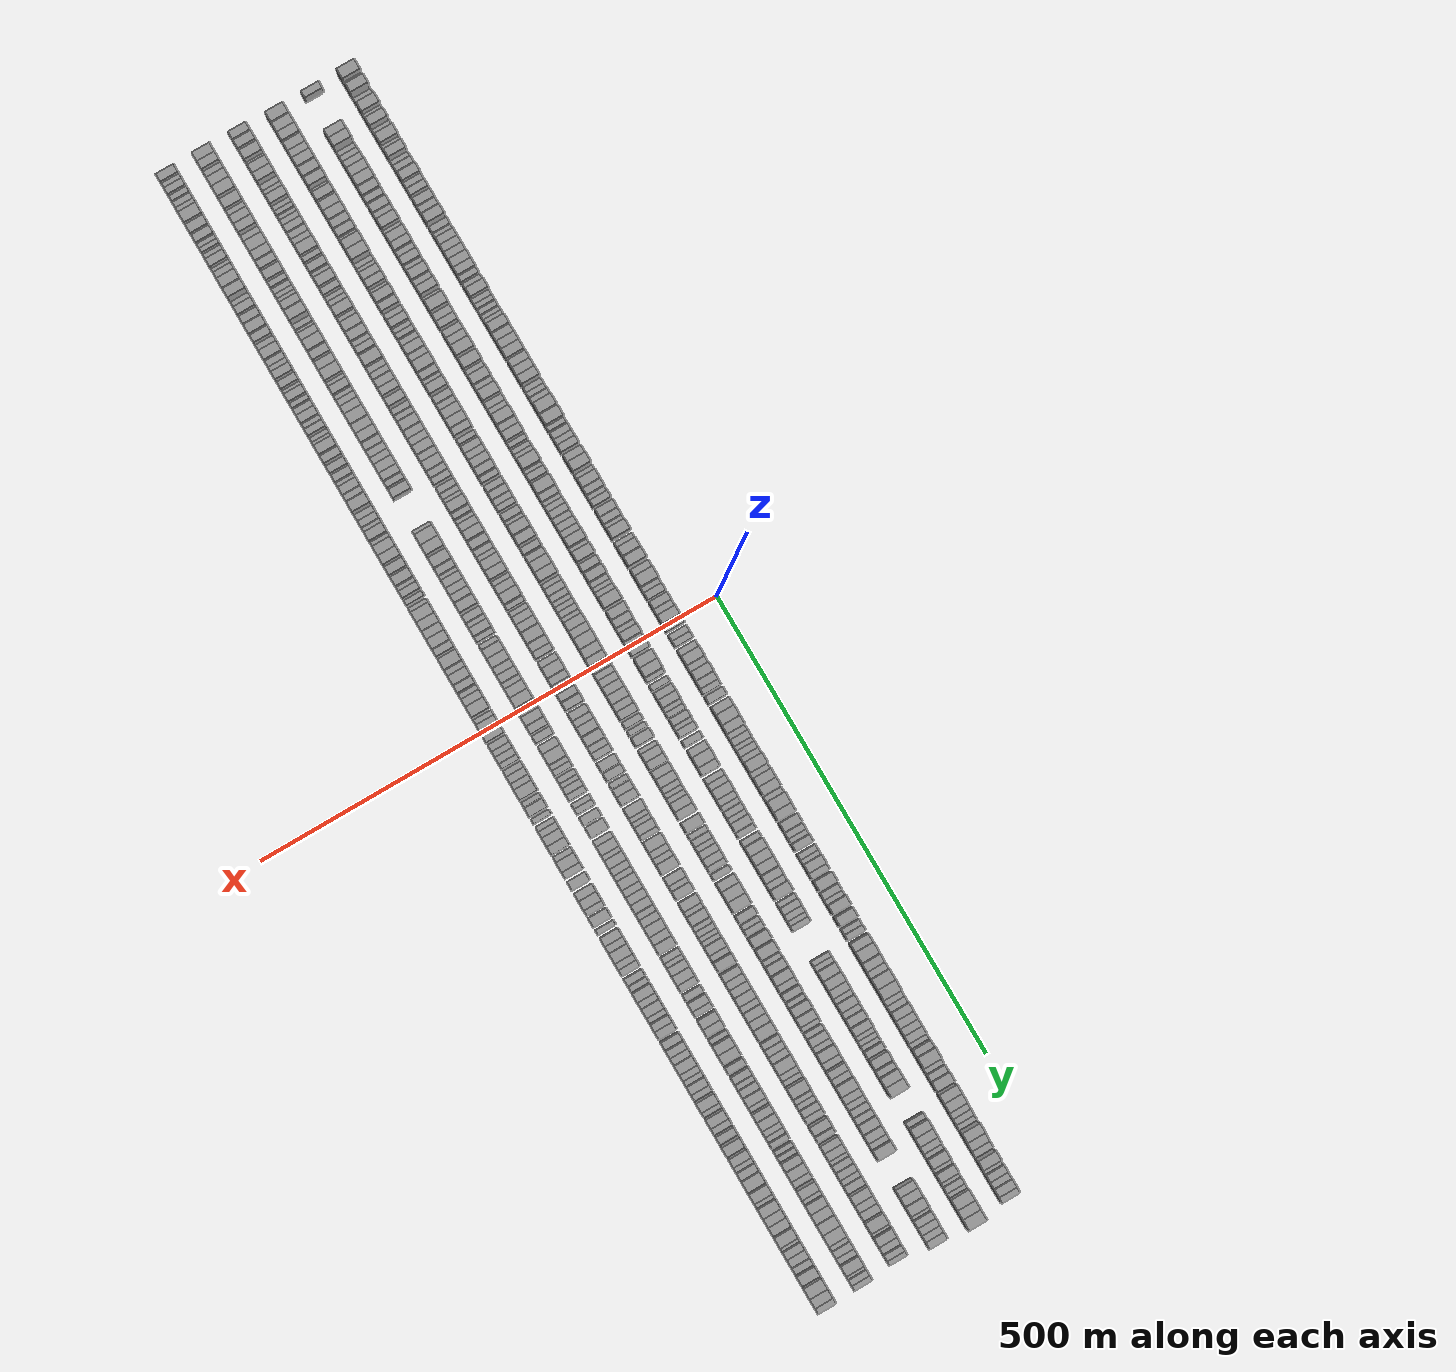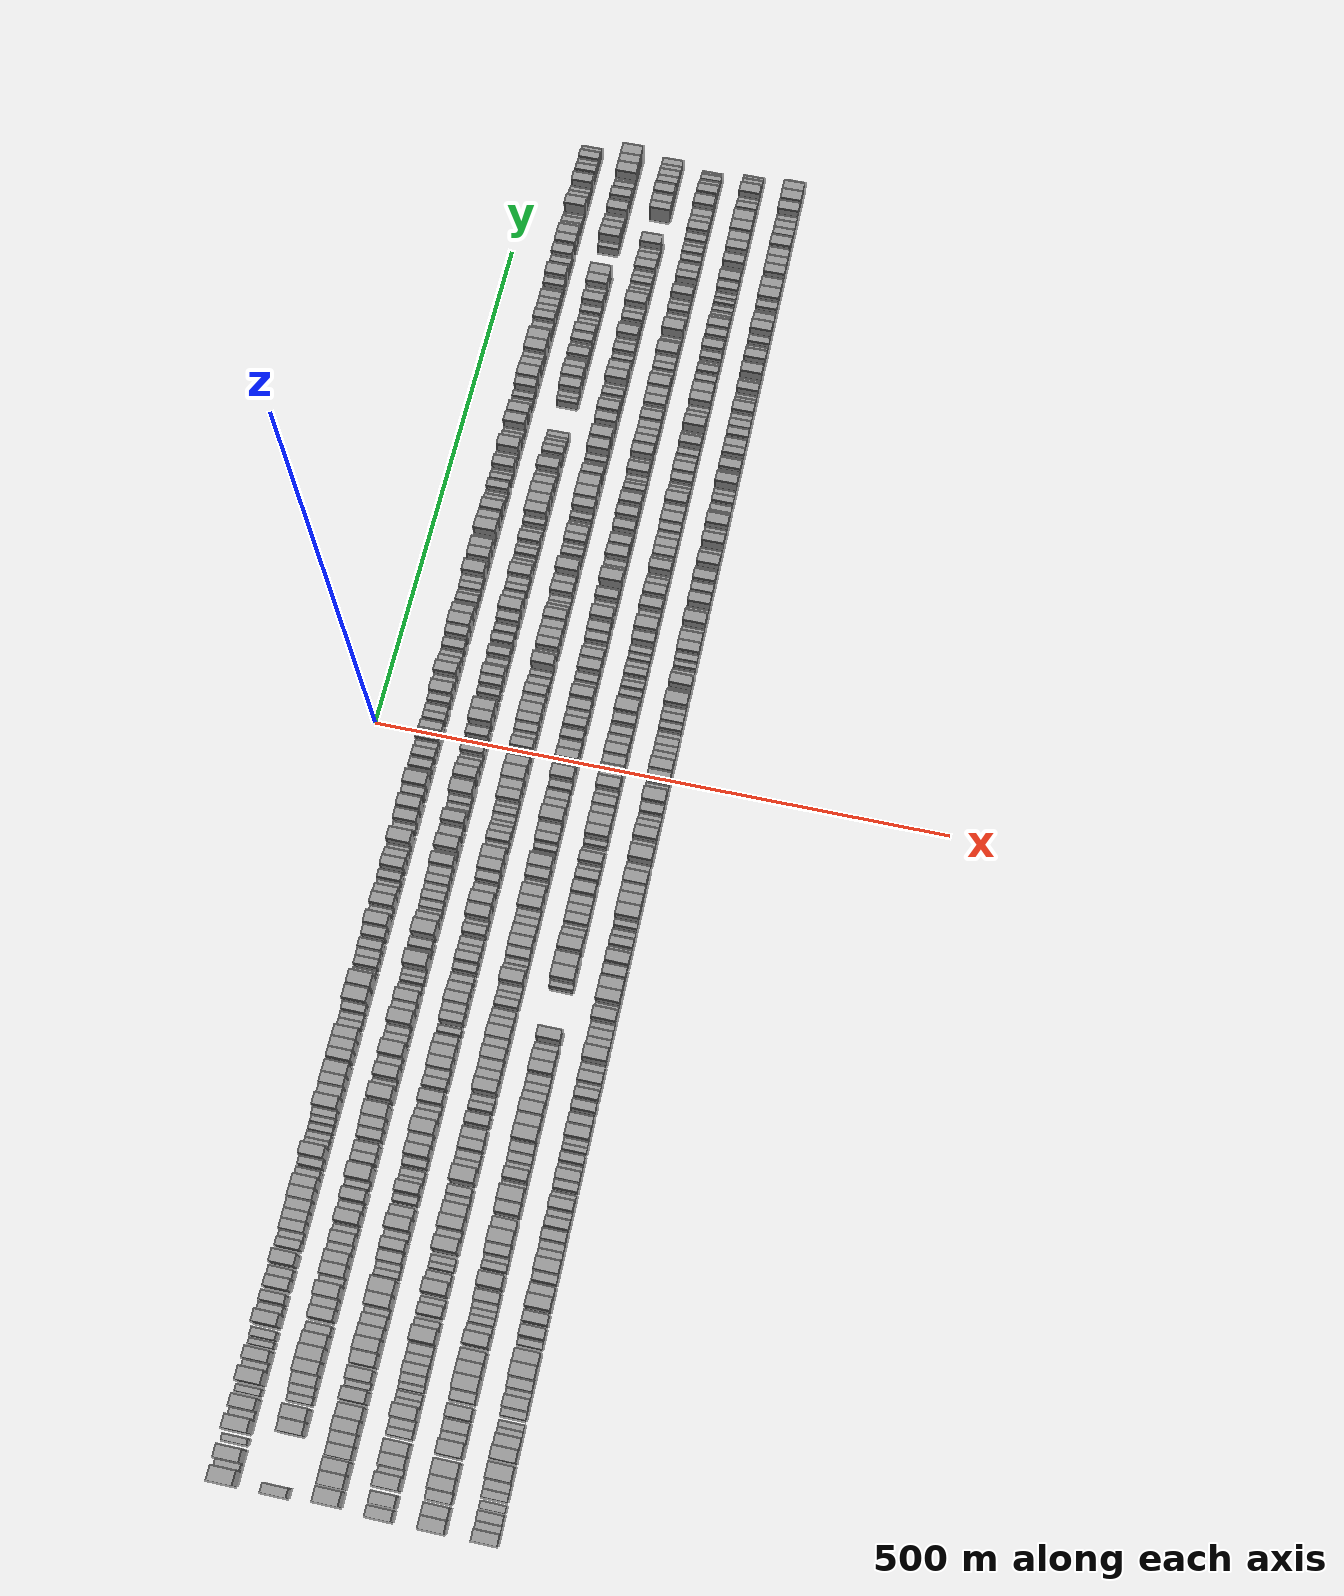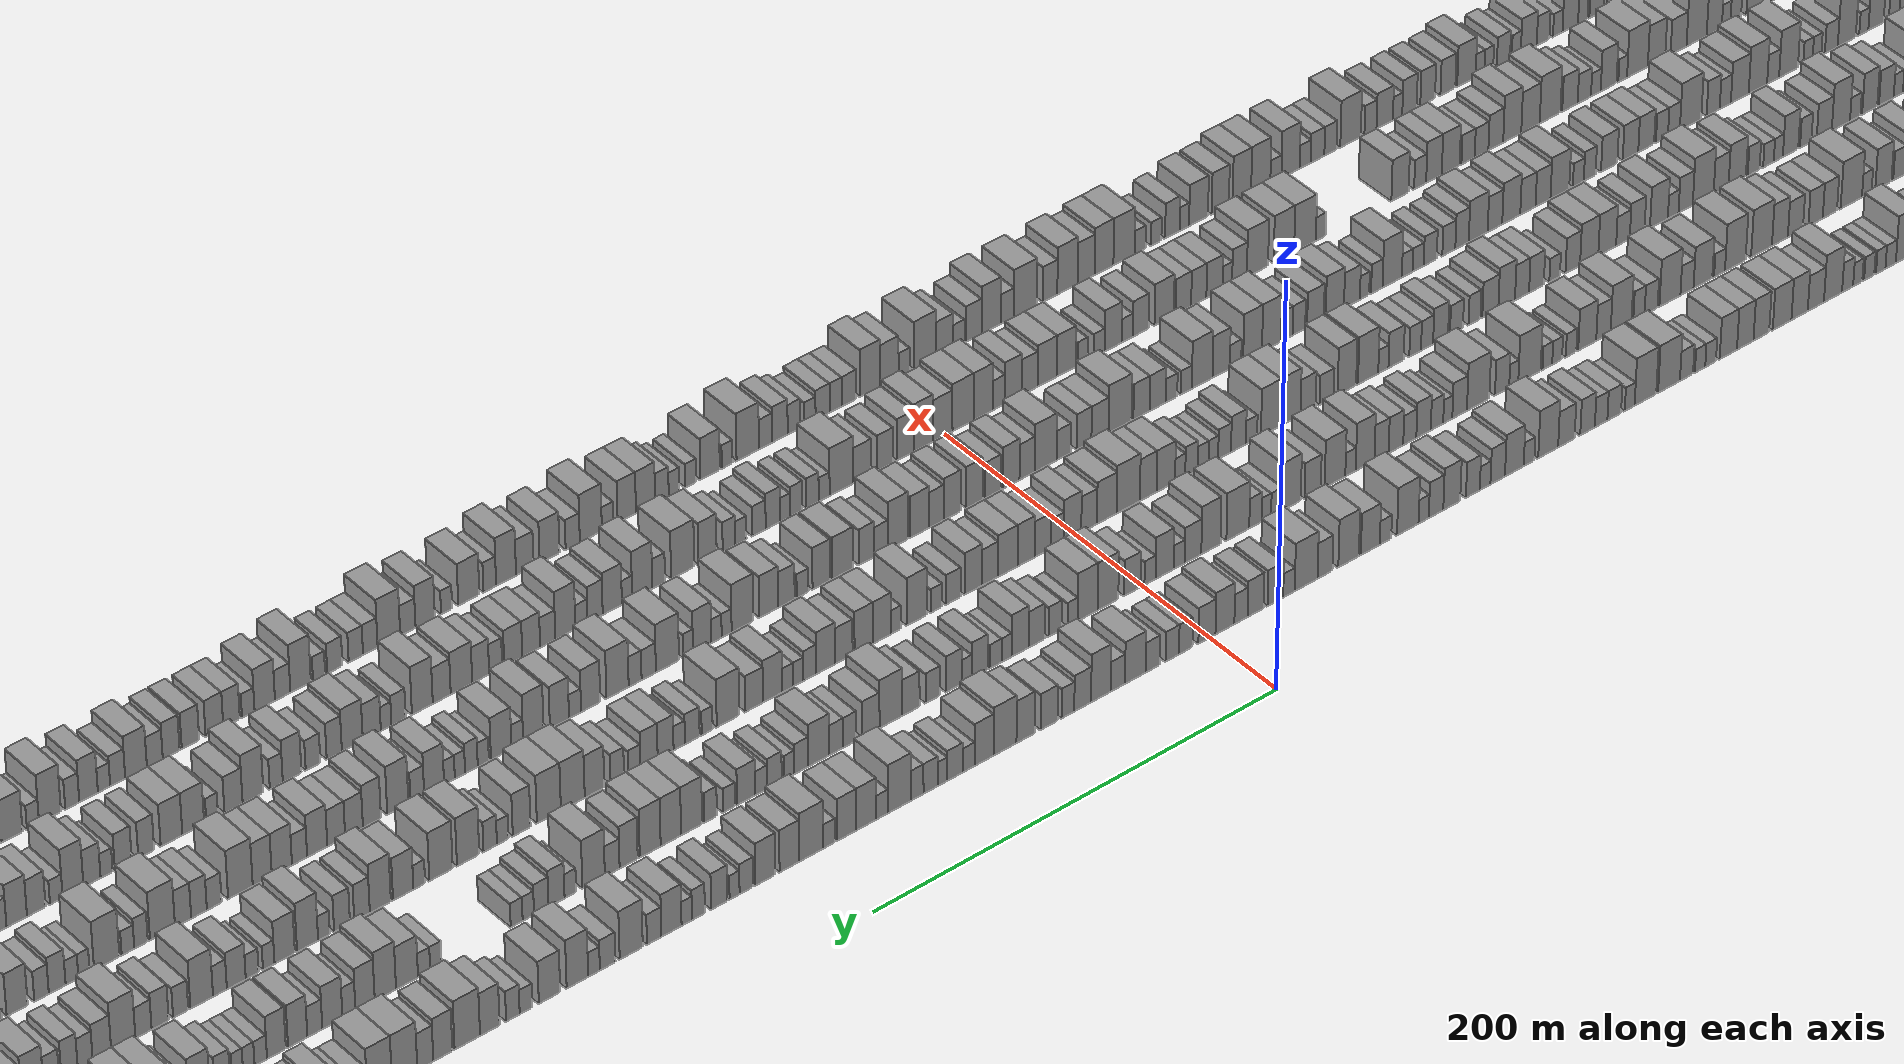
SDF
<sdf version="1.6">
 <world name="default">
  <scene>
   <sky><clouds><speed>12</speed></clouds></sky>
   <ambient>0.4 0.4 0.4 1</ambient>
   <background>0.7 0.7 0.7 1</background>
   <shadows>1</shadows>
  </scene>
  <gravity>0 0 -9.8066</gravity>
  <magnetic_field>6e-06 2.3e-05 -4.2e-05</magnetic_field>
  <physics default="0" name="default_physics" type="ode">
   <ode>
    <solver>
     <type>quick</type>
     <iters>10</iters>
     <sor>1.0</sor>
     <use_dynamic_moi_rescaling>0</use_dynamic_moi_rescaling>
    </solver>
    <constraints>
     <cfm>0</cfm>
     <erp>0.2</erp>
     <contact_max_correcting_vel>100</contact_max_correcting_vel>
     <contact_surface_layer>0.001</contact_surface_layer>
    </constraints>
   </ode>
   <max_step_size>0.004</max_step_size>
   <real_time_factor>1</real_time_factor>
   <real_time_update_rate>250</real_time_update_rate>
  </physics>
  <light name="sun" type="directional">
   <pose>0 0 10 0 0 0</pose>
   <diffuse>0.8 0.8 0.8 1</diffuse>
   <specular>0.2 0.2 0.2 1</specular>
   <attenuation>
    <range>1000</range>
    <constant>0.9</constant>
    <linear>0.01</linear>
    <quadratic>0.001</quadratic>
   </attenuation>
   <direction>-0.5 0.1 -0.9</direction>
  </light>
  <model name="building_1">
   <static>1</static>
   <pose>50.0000 -614.2552 0 0.000000 0.000000 0.000000</pose>
   <link name="link">
    <pose>0 0 12.00 0 0 0</pose>
    <collision name="collision"><geometry><box><size>20.0000 11.4896 24.0000</size></box></geometry></collision>
    <visual name="visual">
     <cast_shadows>0</cast_shadows>
     <geometry><box><size>20.0000 11.4896 24.0000</size></box></geometry>
     <material>
      <script>
       <uri>model://grey_wall/materials/scripts</uri>
       <uri>model://grey_wall/materials/textures</uri>
       <name>vrc/grey_wall</name>
      </script>
     </material>
    </visual>
   </link>
  </model>
  <model name="building_2">
   <static>1</static>
   <pose>50.0000 -605.8968 0 0.000000 0.000000 0.000000</pose>
   <link name="link">
    <pose>0 0 6.00 0 0 0</pose>
    <collision name="collision"><geometry><box><size>20.0000 5.2273 12.0000</size></box></geometry></collision>
    <visual name="visual">
     <cast_shadows>0</cast_shadows>
     <geometry><box><size>20.0000 5.2273 12.0000</size></box></geometry>
     <material>
      <script>
       <uri>model://grey_wall/materials/scripts</uri>
       <uri>model://grey_wall/materials/textures</uri>
       <name>vrc/grey_wall</name>
      </script>
     </material>
    </visual>
   </link>
  </model>
  <model name="building_3">
   <static>1</static>
   <pose>50.0000 -598.3122 0 0.000000 0.000000 0.000000</pose>
   <link name="link">
    <pose>0 0 12.00 0 0 0</pose>
    <collision name="collision"><geometry><box><size>20.0000 9.9418 24.0000</size></box></geometry></collision>
    <visual name="visual">
     <cast_shadows>0</cast_shadows>
     <geometry><box><size>20.0000 9.9418 24.0000</size></box></geometry>
     <material>
      <script>
       <uri>model://grey_wall/materials/scripts</uri>
       <uri>model://grey_wall/materials/textures</uri>
       <name>vrc/grey_wall</name>
      </script>
     </material>
    </visual>
   </link>
  </model>
  <model name="building_4">
   <static>1</static>
   <pose>50.0000 -587.7606 0 0.000000 0.000000 0.000000</pose>
   <link name="link">
    <pose>0 0 6.00 0 0 0</pose>
    <collision name="collision"><geometry><box><size>20.0000 5.1613 12.0000</size></box></geometry></collision>
    <visual name="visual">
     <cast_shadows>0</cast_shadows>
     <geometry><box><size>20.0000 5.1613 12.0000</size></box></geometry>
     <material>
      <script>
       <uri>model://grey_wall/materials/scripts</uri>
       <uri>model://grey_wall/materials/textures</uri>
       <name>vrc/grey_wall</name>
      </script>
     </material>
    </visual>
   </link>
  </model>
  <model name="building_5">
   <static>1</static>
   <pose>50.0000 -576.9690 0 0.000000 0.000000 0.000000</pose>
   <link name="link">
    <pose>0 0 12.00 0 0 0</pose>
    <collision name="collision"><geometry><box><size>20.0000 10.4220 24.0000</size></box></geometry></collision>
    <visual name="visual">
     <cast_shadows>0</cast_shadows>
     <geometry><box><size>20.0000 10.4220 24.0000</size></box></geometry>
     <material>
      <script>
       <uri>model://grey_wall/materials/scripts</uri>
       <uri>model://grey_wall/materials/textures</uri>
       <name>vrc/grey_wall</name>
      </script>
     </material>
    </visual>
   </link>
  </model>
  <model name="building_6">
   <static>1</static>
   <pose>50.0000 -568.8618 0 0.000000 0.000000 0.000000</pose>
   <link name="link">
    <pose>0 0 6.00 0 0 0</pose>
    <collision name="collision"><geometry><box><size>20.0000 5.7923 12.0000</size></box></geometry></collision>
    <visual name="visual">
     <cast_shadows>0</cast_shadows>
     <geometry><box><size>20.0000 5.7923 12.0000</size></box></geometry>
     <material>
      <script>
       <uri>model://grey_wall/materials/scripts</uri>
       <uri>model://grey_wall/materials/textures</uri>
       <name>vrc/grey_wall</name>
      </script>
     </material>
    </visual>
   </link>
  </model>
  <model name="building_7">
   <static>1</static>
   <pose>50.0000 -561.2793 0 0.000000 0.000000 0.000000</pose>
   <link name="link">
    <pose>0 0 10.50 0 0 0</pose>
    <collision name="collision"><geometry><box><size>20.0000 9.3727 21.0000</size></box></geometry></collision>
    <visual name="visual">
     <cast_shadows>0</cast_shadows>
     <geometry><box><size>20.0000 9.3727 21.0000</size></box></geometry>
     <material>
      <script>
       <uri>model://grey_wall/materials/scripts</uri>
       <uri>model://grey_wall/materials/textures</uri>
       <name>vrc/grey_wall</name>
      </script>
     </material>
    </visual>
   </link>
  </model>
  <model name="building_8">
   <static>1</static>
   <pose>50.0000 -551.8442 0 0.000000 0.000000 0.000000</pose>
   <link name="link">
    <pose>0 0 6.00 0 0 0</pose>
    <collision name="collision"><geometry><box><size>20.0000 5.4976 12.0000</size></box></geometry></collision>
    <visual name="visual">
     <cast_shadows>0</cast_shadows>
     <geometry><box><size>20.0000 5.4976 12.0000</size></box></geometry>
     <material>
      <script>
       <uri>model://grey_wall/materials/scripts</uri>
       <uri>model://grey_wall/materials/textures</uri>
       <name>vrc/grey_wall</name>
      </script>
     </material>
    </visual>
   </link>
  </model>
  <model name="building_9">
   <static>1</static>
   <pose>50.0000 -541.7433 0 0.000000 0.000000 0.000000</pose>
   <link name="link">
    <pose>0 0 12.00 0 0 0</pose>
    <collision name="collision"><geometry><box><size>20.0000 10.7042 24.0000</size></box></geometry></collision>
    <visual name="visual">
     <cast_shadows>0</cast_shadows>
     <geometry><box><size>20.0000 10.7042 24.0000</size></box></geometry>
     <material>
      <script>
       <uri>model://grey_wall/materials/scripts</uri>
       <uri>model://grey_wall/materials/textures</uri>
       <name>vrc/grey_wall</name>
      </script>
     </material>
    </visual>
   </link>
  </model>
  <model name="building_10">
   <static>1</static>
   <pose>50.0000 -533.4846 0 0.000000 0.000000 0.000000</pose>
   <link name="link">
    <pose>0 0 6.00 0 0 0</pose>
    <collision name="collision"><geometry><box><size>20.0000 5.8131 12.0000</size></box></geometry></collision>
    <visual name="visual">
     <cast_shadows>0</cast_shadows>
     <geometry><box><size>20.0000 5.8131 12.0000</size></box></geometry>
     <material>
      <script>
       <uri>model://grey_wall/materials/scripts</uri>
       <uri>model://grey_wall/materials/textures</uri>
       <name>vrc/grey_wall</name>
      </script>
     </material>
    </visual>
   </link>
  </model>
  <model name="building_11">
   <static>1</static>
   <pose>50.0000 -525.9968 0 0.000000 0.000000 0.000000</pose>
   <link name="link">
    <pose>0 0 10.50 0 0 0</pose>
    <collision name="collision"><geometry><box><size>20.0000 9.1624 21.0000</size></box></geometry></collision>
    <visual name="visual">
     <cast_shadows>0</cast_shadows>
     <geometry><box><size>20.0000 9.1624 21.0000</size></box></geometry>
     <material>
      <script>
       <uri>model://grey_wall/materials/scripts</uri>
       <uri>model://grey_wall/materials/textures</uri>
       <name>vrc/grey_wall</name>
      </script>
     </material>
    </visual>
   </link>
  </model>
  <model name="building_12">
   <static>1</static>
   <pose>50.0000 -516.9690 0 0.000000 0.000000 0.000000</pose>
   <link name="link">
    <pose>0 0 6.00 0 0 0</pose>
    <collision name="collision"><geometry><box><size>20.0000 4.8932 12.0000</size></box></geometry></collision>
    <visual name="visual">
     <cast_shadows>0</cast_shadows>
     <geometry><box><size>20.0000 4.8932 12.0000</size></box></geometry>
     <material>
      <script>
       <uri>model://grey_wall/materials/scripts</uri>
       <uri>model://grey_wall/materials/textures</uri>
       <name>vrc/grey_wall</name>
      </script>
     </material>
    </visual>
   </link>
  </model>
  <model name="building_13">
   <static>1</static>
   <pose>50.0000 -510.1457 0 0.000000 0.000000 0.000000</pose>
   <link name="link">
    <pose>0 0 7.50 0 0 0</pose>
    <collision name="collision"><geometry><box><size>20.0000 6.7533 15.0000</size></box></geometry></collision>
    <visual name="visual">
     <cast_shadows>0</cast_shadows>
     <geometry><box><size>20.0000 6.7533 15.0000</size></box></geometry>
     <material>
      <script>
       <uri>model://grey_wall/materials/scripts</uri>
       <uri>model://grey_wall/materials/textures</uri>
       <name>vrc/grey_wall</name>
      </script>
     </material>
    </visual>
   </link>
  </model>
  <model name="building_14">
   <static>1</static>
   <pose>50.0000 -498.9157 0 0.000000 0.000000 0.000000</pose>
   <link name="link">
    <pose>0 0 12.00 0 0 0</pose>
    <collision name="collision"><geometry><box><size>20.0000 9.7067 24.0000</size></box></geometry></collision>
    <visual name="visual">
     <cast_shadows>0</cast_shadows>
     <geometry><box><size>20.0000 9.7067 24.0000</size></box></geometry>
     <material>
      <script>
       <uri>model://grey_wall/materials/scripts</uri>
       <uri>model://grey_wall/materials/textures</uri>
       <name>vrc/grey_wall</name>
      </script>
     </material>
    </visual>
   </link>
  </model>
  <model name="building_15">
   <static>1</static>
   <pose>50.0000 -490.9093 0 0.000000 0.000000 0.000000</pose>
   <link name="link">
    <pose>0 0 7.50 0 0 0</pose>
    <collision name="collision"><geometry><box><size>20.0000 6.3063 15.0000</size></box></geometry></collision>
    <visual name="visual">
     <cast_shadows>0</cast_shadows>
     <geometry><box><size>20.0000 6.3063 15.0000</size></box></geometry>
     <material>
      <script>
       <uri>model://grey_wall/materials/scripts</uri>
       <uri>model://grey_wall/materials/textures</uri>
       <name>vrc/grey_wall</name>
      </script>
     </material>
    </visual>
   </link>
  </model>
  <model name="building_16">
   <static>1</static>
   <pose>50.0000 -482.9304 0 0.000000 0.000000 0.000000</pose>
   <link name="link">
    <pose>0 0 9.00 0 0 0</pose>
    <collision name="collision"><geometry><box><size>20.0000 7.6513 18.0000</size></box></geometry></collision>
    <visual name="visual">
     <cast_shadows>0</cast_shadows>
     <geometry><box><size>20.0000 7.6513 18.0000</size></box></geometry>
     <material>
      <script>
       <uri>model://grey_wall/materials/scripts</uri>
       <uri>model://grey_wall/materials/textures</uri>
       <name>vrc/grey_wall</name>
      </script>
     </material>
    </visual>
   </link>
  </model>
  <model name="building_17">
   <static>1</static>
   <pose>50.0000 -471.6135 0 0.000000 0.000000 0.000000</pose>
   <link name="link">
    <pose>0 0 9.00 0 0 0</pose>
    <collision name="collision"><geometry><box><size>20.0000 8.9825 18.0000</size></box></geometry></collision>
    <visual name="visual">
     <cast_shadows>0</cast_shadows>
     <geometry><box><size>20.0000 8.9825 18.0000</size></box></geometry>
     <material>
      <script>
       <uri>model://grey_wall/materials/scripts</uri>
       <uri>model://grey_wall/materials/textures</uri>
       <name>vrc/grey_wall</name>
      </script>
     </material>
    </visual>
   </link>
  </model>
  <model name="building_18">
   <static>1</static>
   <pose>50.0000 -463.5073 0 0.000000 0.000000 0.000000</pose>
   <link name="link">
    <pose>0 0 7.50 0 0 0</pose>
    <collision name="collision"><geometry><box><size>20.0000 7.2300 15.0000</size></box></geometry></collision>
    <visual name="visual">
     <cast_shadows>0</cast_shadows>
     <geometry><box><size>20.0000 7.2300 15.0000</size></box></geometry>
     <material>
      <script>
       <uri>model://grey_wall/materials/scripts</uri>
       <uri>model://grey_wall/materials/textures</uri>
       <name>vrc/grey_wall</name>
      </script>
     </material>
    </visual>
   </link>
  </model>
  <model name="building_19">
   <static>1</static>
   <pose>50.0000 -452.8187 0 0.000000 0.000000 0.000000</pose>
   <link name="link">
    <pose>0 0 10.50 0 0 0</pose>
    <collision name="collision"><geometry><box><size>20.0000 10.1472 21.0000</size></box></geometry></collision>
    <visual name="visual">
     <cast_shadows>0</cast_shadows>
     <geometry><box><size>20.0000 10.1472 21.0000</size></box></geometry>
     <material>
      <script>
       <uri>model://grey_wall/materials/scripts</uri>
       <uri>model://grey_wall/materials/textures</uri>
       <name>vrc/grey_wall</name>
      </script>
     </material>
    </visual>
   </link>
  </model>
  <model name="building_20">
   <static>1</static>
   <pose>50.0000 -441.1250 0 0.000000 0.000000 0.000000</pose>
   <link name="link">
    <pose>0 0 7.50 0 0 0</pose>
    <collision name="collision"><geometry><box><size>20.0000 7.2403 15.0000</size></box></geometry></collision>
    <visual name="visual">
     <cast_shadows>0</cast_shadows>
     <geometry><box><size>20.0000 7.2403 15.0000</size></box></geometry>
     <material>
      <script>
       <uri>model://grey_wall/materials/scripts</uri>
       <uri>model://grey_wall/materials/textures</uri>
       <name>vrc/grey_wall</name>
      </script>
     </material>
    </visual>
   </link>
  </model>
  <model name="building_21">
   <static>1</static>
   <pose>50.0000 -434.6832 0 0.000000 0.000000 0.000000</pose>
   <link name="link">
    <pose>0 0 6.00 0 0 0</pose>
    <collision name="collision"><geometry><box><size>20.0000 5.6432 12.0000</size></box></geometry></collision>
    <visual name="visual">
     <cast_shadows>0</cast_shadows>
     <geometry><box><size>20.0000 5.6432 12.0000</size></box></geometry>
     <material>
      <script>
       <uri>model://grey_wall/materials/scripts</uri>
       <uri>model://grey_wall/materials/textures</uri>
       <name>vrc/grey_wall</name>
      </script>
     </material>
    </visual>
   </link>
  </model>
  <model name="building_22">
   <static>1</static>
   <pose>50.0000 -427.7322 0 0.000000 0.000000 0.000000</pose>
   <link name="link">
    <pose>0 0 9.00 0 0 0</pose>
    <collision name="collision"><geometry><box><size>20.0000 8.2589 18.0000</size></box></geometry></collision>
    <visual name="visual">
     <cast_shadows>0</cast_shadows>
     <geometry><box><size>20.0000 8.2589 18.0000</size></box></geometry>
     <material>
      <script>
       <uri>model://grey_wall/materials/scripts</uri>
       <uri>model://grey_wall/materials/textures</uri>
       <name>vrc/grey_wall</name>
      </script>
     </material>
    </visual>
   </link>
  </model>
  <model name="building_23">
   <static>1</static>
   <pose>50.0000 -419.6220 0 0.000000 0.000000 0.000000</pose>
   <link name="link">
    <pose>0 0 9.00 0 0 0</pose>
    <collision name="collision"><geometry><box><size>20.0000 7.9615 18.0000</size></box></geometry></collision>
    <visual name="visual">
     <cast_shadows>0</cast_shadows>
     <geometry><box><size>20.0000 7.9615 18.0000</size></box></geometry>
     <material>
      <script>
       <uri>model://grey_wall/materials/scripts</uri>
       <uri>model://grey_wall/materials/textures</uri>
       <name>vrc/grey_wall</name>
      </script>
     </material>
    </visual>
   </link>
  </model>
  <model name="building_24">
   <static>1</static>
   <pose>50.0000 -411.3302 0 0.000000 0.000000 0.000000</pose>
   <link name="link">
    <pose>0 0 9.00 0 0 0</pose>
    <collision name="collision"><geometry><box><size>20.0000 8.6222 18.0000</size></box></geometry></collision>
    <visual name="visual">
     <cast_shadows>0</cast_shadows>
     <geometry><box><size>20.0000 8.6222 18.0000</size></box></geometry>
     <material>
      <script>
       <uri>model://grey_wall/materials/scripts</uri>
       <uri>model://grey_wall/materials/textures</uri>
       <name>vrc/grey_wall</name>
      </script>
     </material>
    </visual>
   </link>
  </model>
  <model name="building_25">
   <static>1</static>
   <pose>50.0000 -402.3406 0 0.000000 0.000000 0.000000</pose>
   <link name="link">
    <pose>0 0 10.50 0 0 0</pose>
    <collision name="collision"><geometry><box><size>20.0000 9.3569 21.0000</size></box></geometry></collision>
    <visual name="visual">
     <cast_shadows>0</cast_shadows>
     <geometry><box><size>20.0000 9.3569 21.0000</size></box></geometry>
     <material>
      <script>
       <uri>model://grey_wall/materials/scripts</uri>
       <uri>model://grey_wall/materials/textures</uri>
       <name>vrc/grey_wall</name>
      </script>
     </material>
    </visual>
   </link>
  </model>
  <model name="building_26">
   <static>1</static>
   <pose>50.0000 -393.3666 0 0.000000 0.000000 0.000000</pose>
   <link name="link">
    <pose>0 0 10.50 0 0 0</pose>
    <collision name="collision"><geometry><box><size>20.0000 8.5912 21.0000</size></box></geometry></collision>
    <visual name="visual">
     <cast_shadows>0</cast_shadows>
     <geometry><box><size>20.0000 8.5912 21.0000</size></box></geometry>
     <material>
      <script>
       <uri>model://grey_wall/materials/scripts</uri>
       <uri>model://grey_wall/materials/textures</uri>
       <name>vrc/grey_wall</name>
      </script>
     </material>
    </visual>
   </link>
  </model>
  <model name="building_27">
   <static>1</static>
   <pose>50.0000 -385.9371 0 0.000000 0.000000 0.000000</pose>
   <link name="link">
    <pose>0 0 7.50 0 0 0</pose>
    <collision name="collision"><geometry><box><size>20.0000 6.2679 15.0000</size></box></geometry></collision>
    <visual name="visual">
     <cast_shadows>0</cast_shadows>
     <geometry><box><size>20.0000 6.2679 15.0000</size></box></geometry>
     <material>
      <script>
       <uri>model://grey_wall/materials/scripts</uri>
       <uri>model://grey_wall/materials/textures</uri>
       <name>vrc/grey_wall</name>
      </script>
     </material>
    </visual>
   </link>
  </model>
  <model name="building_28">
   <static>1</static>
   <pose>50.0000 -377.3876 0 0.000000 0.000000 0.000000</pose>
   <link name="link">
    <pose>0 0 7.50 0 0 0</pose>
    <collision name="collision"><geometry><box><size>20.0000 6.8310 15.0000</size></box></geometry></collision>
    <visual name="visual">
     <cast_shadows>0</cast_shadows>
     <geometry><box><size>20.0000 6.8310 15.0000</size></box></geometry>
     <material>
      <script>
       <uri>model://grey_wall/materials/scripts</uri>
       <uri>model://grey_wall/materials/textures</uri>
       <name>vrc/grey_wall</name>
      </script>
     </material>
    </visual>
   </link>
  </model>
  <model name="building_29">
   <static>1</static>
   <pose>50.0000 -369.1044 0 0.000000 0.000000 0.000000</pose>
   <link name="link">
    <pose>0 0 12.00 0 0 0</pose>
    <collision name="collision"><geometry><box><size>20.0000 9.7356 24.0000</size></box></geometry></collision>
    <visual name="visual">
     <cast_shadows>0</cast_shadows>
     <geometry><box><size>20.0000 9.7356 24.0000</size></box></geometry>
     <material>
      <script>
       <uri>model://grey_wall/materials/scripts</uri>
       <uri>model://grey_wall/materials/textures</uri>
       <name>vrc/grey_wall</name>
      </script>
     </material>
    </visual>
   </link>
  </model>
  <model name="building_30">
   <static>1</static>
   <pose>50.0000 -361.3651 0 0.000000 0.000000 0.000000</pose>
   <link name="link">
    <pose>0 0 6.00 0 0 0</pose>
    <collision name="collision"><geometry><box><size>20.0000 5.7431 12.0000</size></box></geometry></collision>
    <visual name="visual">
     <cast_shadows>0</cast_shadows>
     <geometry><box><size>20.0000 5.7431 12.0000</size></box></geometry>
     <material>
      <script>
       <uri>model://grey_wall/materials/scripts</uri>
       <uri>model://grey_wall/materials/textures</uri>
       <name>vrc/grey_wall</name>
      </script>
     </material>
    </visual>
   </link>
  </model>
  <model name="building_31">
   <static>1</static>
   <pose>50.0000 -355.8773 0 0.000000 0.000000 0.000000</pose>
   <link name="link">
    <pose>0 0 6.00 0 0 0</pose>
    <collision name="collision"><geometry><box><size>20.0000 5.2324 12.0000</size></box></geometry></collision>
    <visual name="visual">
     <cast_shadows>0</cast_shadows>
     <geometry><box><size>20.0000 5.2324 12.0000</size></box></geometry>
     <material>
      <script>
       <uri>model://grey_wall/materials/scripts</uri>
       <uri>model://grey_wall/materials/textures</uri>
       <name>vrc/grey_wall</name>
      </script>
     </material>
    </visual>
   </link>
  </model>
  <model name="building_32">
   <static>1</static>
   <pose>50.0000 -349.4674 0 0.000000 0.000000 0.000000</pose>
   <link name="link">
    <pose>0 0 6.00 0 0 0</pose>
    <collision name="collision"><geometry><box><size>20.0000 5.5874 12.0000</size></box></geometry></collision>
    <visual name="visual">
     <cast_shadows>0</cast_shadows>
     <geometry><box><size>20.0000 5.5874 12.0000</size></box></geometry>
     <material>
      <script>
       <uri>model://grey_wall/materials/scripts</uri>
       <uri>model://grey_wall/materials/textures</uri>
       <name>vrc/grey_wall</name>
      </script>
     </material>
    </visual>
   </link>
  </model>
  <model name="building_33">
   <static>1</static>
   <pose>50.0000 -343.1488 0 0.000000 0.000000 0.000000</pose>
   <link name="link">
    <pose>0 0 6.00 0 0 0</pose>
    <collision name="collision"><geometry><box><size>20.0000 5.0498 12.0000</size></box></geometry></collision>
    <visual name="visual">
     <cast_shadows>0</cast_shadows>
     <geometry><box><size>20.0000 5.0498 12.0000</size></box></geometry>
     <material>
      <script>
       <uri>model://grey_wall/materials/scripts</uri>
       <uri>model://grey_wall/materials/textures</uri>
       <name>vrc/grey_wall</name>
      </script>
     </material>
    </visual>
   </link>
  </model>
  <model name="building_34">
   <static>1</static>
   <pose>50.0000 -337.5745 0 0.000000 0.000000 0.000000</pose>
   <link name="link">
    <pose>0 0 7.50 0 0 0</pose>
    <collision name="collision"><geometry><box><size>20.0000 6.0989 15.0000</size></box></geometry></collision>
    <visual name="visual">
     <cast_shadows>0</cast_shadows>
     <geometry><box><size>20.0000 6.0989 15.0000</size></box></geometry>
     <material>
      <script>
       <uri>model://grey_wall/materials/scripts</uri>
       <uri>model://grey_wall/materials/textures</uri>
       <name>vrc/grey_wall</name>
      </script>
     </material>
    </visual>
   </link>
  </model>
  <model name="building_35">
   <static>1</static>
   <pose>50.0000 -329.5333 0 0.000000 0.000000 0.000000</pose>
   <link name="link">
    <pose>0 0 12.00 0 0 0</pose>
    <collision name="collision"><geometry><box><size>20.0000 9.9835 24.0000</size></box></geometry></collision>
    <visual name="visual">
     <cast_shadows>0</cast_shadows>
     <geometry><box><size>20.0000 9.9835 24.0000</size></box></geometry>
     <material>
      <script>
       <uri>model://grey_wall/materials/scripts</uri>
       <uri>model://grey_wall/materials/textures</uri>
       <name>vrc/grey_wall</name>
      </script>
     </material>
    </visual>
   </link>
  </model>
  <model name="building_36">
   <static>1</static>
   <pose>50.0000 -320.1025 0 0.000000 0.000000 0.000000</pose>
   <link name="link">
    <pose>0 0 9.00 0 0 0</pose>
    <collision name="collision"><geometry><box><size>20.0000 8.8781 18.0000</size></box></geometry></collision>
    <visual name="visual">
     <cast_shadows>0</cast_shadows>
     <geometry><box><size>20.0000 8.8781 18.0000</size></box></geometry>
     <material>
      <script>
       <uri>model://grey_wall/materials/scripts</uri>
       <uri>model://grey_wall/materials/textures</uri>
       <name>vrc/grey_wall</name>
      </script>
     </material>
    </visual>
   </link>
  </model>
  <model name="building_37">
   <static>1</static>
   <pose>50.0000 -311.1957 0 0.000000 0.000000 0.000000</pose>
   <link name="link">
    <pose>0 0 10.50 0 0 0</pose>
    <collision name="collision"><geometry><box><size>20.0000 8.9355 21.0000</size></box></geometry></collision>
    <visual name="visual">
     <cast_shadows>0</cast_shadows>
     <geometry><box><size>20.0000 8.9355 21.0000</size></box></geometry>
     <material>
      <script>
       <uri>model://grey_wall/materials/scripts</uri>
       <uri>model://grey_wall/materials/textures</uri>
       <name>vrc/grey_wall</name>
      </script>
     </material>
    </visual>
   </link>
  </model>
  <model name="building_38">
   <static>1</static>
   <pose>50.0000 -301.6341 0 0.000000 0.000000 0.000000</pose>
   <link name="link">
    <pose>0 0 10.50 0 0 0</pose>
    <collision name="collision"><geometry><box><size>20.0000 10.1878 21.0000</size></box></geometry></collision>
    <visual name="visual">
     <cast_shadows>0</cast_shadows>
     <geometry><box><size>20.0000 10.1878 21.0000</size></box></geometry>
     <material>
      <script>
       <uri>model://grey_wall/materials/scripts</uri>
       <uri>model://grey_wall/materials/textures</uri>
       <name>vrc/grey_wall</name>
      </script>
     </material>
    </visual>
   </link>
  </model>
  <model name="building_39">
   <static>1</static>
   <pose>50.0000 -290.2764 0 0.000000 0.000000 0.000000</pose>
   <link name="link">
    <pose>0 0 10.50 0 0 0</pose>
    <collision name="collision"><geometry><box><size>20.0000 8.5275 21.0000</size></box></geometry></collision>
    <visual name="visual">
     <cast_shadows>0</cast_shadows>
     <geometry><box><size>20.0000 8.5275 21.0000</size></box></geometry>
     <material>
      <script>
       <uri>model://grey_wall/materials/scripts</uri>
       <uri>model://grey_wall/materials/textures</uri>
       <name>vrc/grey_wall</name>
      </script>
     </material>
    </visual>
   </link>
  </model>
  <model name="building_40">
   <static>1</static>
   <pose>50.0000 -281.5278 0 0.000000 0.000000 0.000000</pose>
   <link name="link">
    <pose>0 0 10.50 0 0 0</pose>
    <collision name="collision"><geometry><box><size>20.0000 8.9697 21.0000</size></box></geometry></collision>
    <visual name="visual">
     <cast_shadows>0</cast_shadows>
     <geometry><box><size>20.0000 8.9697 21.0000</size></box></geometry>
     <material>
      <script>
       <uri>model://grey_wall/materials/scripts</uri>
       <uri>model://grey_wall/materials/textures</uri>
       <name>vrc/grey_wall</name>
      </script>
     </material>
    </visual>
   </link>
  </model>
  <model name="building_41">
   <static>1</static>
   <pose>50.0000 -272.3328 0 0.000000 0.000000 0.000000</pose>
   <link name="link">
    <pose>0 0 10.50 0 0 0</pose>
    <collision name="collision"><geometry><box><size>20.0000 9.4203 21.0000</size></box></geometry></collision>
    <visual name="visual">
     <cast_shadows>0</cast_shadows>
     <geometry><box><size>20.0000 9.4203 21.0000</size></box></geometry>
     <material>
      <script>
       <uri>model://grey_wall/materials/scripts</uri>
       <uri>model://grey_wall/materials/textures</uri>
       <name>vrc/grey_wall</name>
      </script>
     </material>
    </visual>
   </link>
  </model>
  <model name="building_42">
   <static>1</static>
   <pose>50.0000 -262.7251 0 0.000000 0.000000 0.000000</pose>
   <link name="link">
    <pose>0 0 6.00 0 0 0</pose>
    <collision name="collision"><geometry><box><size>20.0000 5.7952 12.0000</size></box></geometry></collision>
    <visual name="visual">
     <cast_shadows>0</cast_shadows>
     <geometry><box><size>20.0000 5.7952 12.0000</size></box></geometry>
     <material>
      <script>
       <uri>model://grey_wall/materials/scripts</uri>
       <uri>model://grey_wall/materials/textures</uri>
       <name>vrc/grey_wall</name>
      </script>
     </material>
    </visual>
   </link>
  </model>
  <model name="building_43">
   <static>1</static>
   <pose>50.0000 -257.0356 0 0.000000 0.000000 0.000000</pose>
   <link name="link">
    <pose>0 0 6.00 0 0 0</pose>
    <collision name="collision"><geometry><box><size>20.0000 5.5838 12.0000</size></box></geometry></collision>
    <visual name="visual">
     <cast_shadows>0</cast_shadows>
     <geometry><box><size>20.0000 5.5838 12.0000</size></box></geometry>
     <material>
      <script>
       <uri>model://grey_wall/materials/scripts</uri>
       <uri>model://grey_wall/materials/textures</uri>
       <name>vrc/grey_wall</name>
      </script>
     </material>
    </visual>
   </link>
  </model>
  <model name="building_44">
   <static>1</static>
   <pose>50.0000 -249.7115 0 0.000000 0.000000 0.000000</pose>
   <link name="link">
    <pose>0 0 7.50 0 0 0</pose>
    <collision name="collision"><geometry><box><size>20.0000 7.0644 15.0000</size></box></geometry></collision>
    <visual name="visual">
     <cast_shadows>0</cast_shadows>
     <geometry><box><size>20.0000 7.0644 15.0000</size></box></geometry>
     <material>
      <script>
       <uri>model://grey_wall/materials/scripts</uri>
       <uri>model://grey_wall/materials/textures</uri>
       <name>vrc/grey_wall</name>
      </script>
     </material>
    </visual>
   </link>
  </model>
  <model name="building_45">
   <static>1</static>
   <pose>50.0000 -240.2872 0 0.000000 0.000000 0.000000</pose>
   <link name="link">
    <pose>0 0 12.00 0 0 0</pose>
    <collision name="collision"><geometry><box><size>20.0000 11.7841 24.0000</size></box></geometry></collision>
    <visual name="visual">
     <cast_shadows>0</cast_shadows>
     <geometry><box><size>20.0000 11.7841 24.0000</size></box></geometry>
     <material>
      <script>
       <uri>model://grey_wall/materials/scripts</uri>
       <uri>model://grey_wall/materials/textures</uri>
       <name>vrc/grey_wall</name>
      </script>
     </material>
    </visual>
   </link>
  </model>
  <model name="building_46">
   <static>1</static>
   <pose>50.0000 -227.5945 0 0.000000 0.000000 0.000000</pose>
   <link name="link">
    <pose>0 0 12.00 0 0 0</pose>
    <collision name="collision"><geometry><box><size>20.0000 11.6014 24.0000</size></box></geometry></collision>
    <visual name="visual">
     <cast_shadows>0</cast_shadows>
     <geometry><box><size>20.0000 11.6014 24.0000</size></box></geometry>
     <material>
      <script>
       <uri>model://grey_wall/materials/scripts</uri>
       <uri>model://grey_wall/materials/textures</uri>
       <name>vrc/grey_wall</name>
      </script>
     </material>
    </visual>
   </link>
  </model>
  <model name="building_47">
   <static>1</static>
   <pose>50.0000 -219.1614 0 0.000000 0.000000 0.000000</pose>
   <link name="link">
    <pose>0 0 6.00 0 0 0</pose>
    <collision name="collision"><geometry><box><size>20.0000 5.2647 12.0000</size></box></geometry></collision>
    <visual name="visual">
     <cast_shadows>0</cast_shadows>
     <geometry><box><size>20.0000 5.2647 12.0000</size></box></geometry>
     <material>
      <script>
       <uri>model://grey_wall/materials/scripts</uri>
       <uri>model://grey_wall/materials/textures</uri>
       <name>vrc/grey_wall</name>
      </script>
     </material>
    </visual>
   </link>
  </model>
  <model name="building_48">
   <static>1</static>
   <pose>50.0000 -210.8705 0 0.000000 0.000000 0.000000</pose>
   <link name="link">
    <pose>0 0 7.50 0 0 0</pose>
    <collision name="collision"><geometry><box><size>20.0000 7.3172 15.0000</size></box></geometry></collision>
    <visual name="visual">
     <cast_shadows>0</cast_shadows>
     <geometry><box><size>20.0000 7.3172 15.0000</size></box></geometry>
     <material>
      <script>
       <uri>model://grey_wall/materials/scripts</uri>
       <uri>model://grey_wall/materials/textures</uri>
       <name>vrc/grey_wall</name>
      </script>
     </material>
    </visual>
   </link>
  </model>
  <model name="building_49">
   <static>1</static>
   <pose>50.0000 -203.8692 0 0.000000 0.000000 0.000000</pose>
   <link name="link">
    <pose>0 0 7.50 0 0 0</pose>
    <collision name="collision"><geometry><box><size>20.0000 6.6853 15.0000</size></box></geometry></collision>
    <visual name="visual">
     <cast_shadows>0</cast_shadows>
     <geometry><box><size>20.0000 6.6853 15.0000</size></box></geometry>
     <material>
      <script>
       <uri>model://grey_wall/materials/scripts</uri>
       <uri>model://grey_wall/materials/textures</uri>
       <name>vrc/grey_wall</name>
      </script>
     </material>
    </visual>
   </link>
  </model>
  <model name="building_50">
   <static>1</static>
   <pose>50.0000 -196.6402 0 0.000000 0.000000 0.000000</pose>
   <link name="link">
    <pose>0 0 9.00 0 0 0</pose>
    <collision name="collision"><geometry><box><size>20.0000 7.7727 18.0000</size></box></geometry></collision>
    <visual name="visual">
     <cast_shadows>0</cast_shadows>
     <geometry><box><size>20.0000 7.7727 18.0000</size></box></geometry>
     <material>
      <script>
       <uri>model://grey_wall/materials/scripts</uri>
       <uri>model://grey_wall/materials/textures</uri>
       <name>vrc/grey_wall</name>
      </script>
     </material>
    </visual>
   </link>
  </model>
  <model name="building_51">
   <static>1</static>
   <pose>50.0000 -185.3771 0 0.000000 0.000000 0.000000</pose>
   <link name="link">
    <pose>0 0 9.00 0 0 0</pose>
    <collision name="collision"><geometry><box><size>20.0000 8.7536 18.0000</size></box></geometry></collision>
    <visual name="visual">
     <cast_shadows>0</cast_shadows>
     <geometry><box><size>20.0000 8.7536 18.0000</size></box></geometry>
     <material>
      <script>
       <uri>model://grey_wall/materials/scripts</uri>
       <uri>model://grey_wall/materials/textures</uri>
       <name>vrc/grey_wall</name>
      </script>
     </material>
    </visual>
   </link>
  </model>
  <model name="building_52">
   <static>1</static>
   <pose>50.0000 -175.7151 0 0.000000 0.000000 0.000000</pose>
   <link name="link">
    <pose>0 0 12.00 0 0 0</pose>
    <collision name="collision"><geometry><box><size>20.0000 10.5704 24.0000</size></box></geometry></collision>
    <visual name="visual">
     <cast_shadows>0</cast_shadows>
     <geometry><box><size>20.0000 10.5704 24.0000</size></box></geometry>
     <material>
      <script>
       <uri>model://grey_wall/materials/scripts</uri>
       <uri>model://grey_wall/materials/textures</uri>
       <name>vrc/grey_wall</name>
      </script>
     </material>
    </visual>
   </link>
  </model>
  <model name="building_53">
   <static>1</static>
   <pose>50.0000 -165.5970 0 0.000000 0.000000 0.000000</pose>
   <link name="link">
    <pose>0 0 6.00 0 0 0</pose>
    <collision name="collision"><geometry><box><size>20.0000 5.6657 12.0000</size></box></geometry></collision>
    <visual name="visual">
     <cast_shadows>0</cast_shadows>
     <geometry><box><size>20.0000 5.6657 12.0000</size></box></geometry>
     <material>
      <script>
       <uri>model://grey_wall/materials/scripts</uri>
       <uri>model://grey_wall/materials/textures</uri>
       <name>vrc/grey_wall</name>
      </script>
     </material>
    </visual>
   </link>
  </model>
  <model name="building_54">
   <static>1</static>
   <pose>50.0000 -157.8169 0 0.000000 0.000000 0.000000</pose>
   <link name="link">
    <pose>0 0 10.50 0 0 0</pose>
    <collision name="collision"><geometry><box><size>20.0000 9.8945 21.0000</size></box></geometry></collision>
    <visual name="visual">
     <cast_shadows>0</cast_shadows>
     <geometry><box><size>20.0000 9.8945 21.0000</size></box></geometry>
     <material>
      <script>
       <uri>model://grey_wall/materials/scripts</uri>
       <uri>model://grey_wall/materials/textures</uri>
       <name>vrc/grey_wall</name>
      </script>
     </material>
    </visual>
   </link>
  </model>
  <model name="building_55">
   <static>1</static>
   <pose>50.0000 -149.0319 0 0.000000 0.000000 0.000000</pose>
   <link name="link">
    <pose>0 0 9.00 0 0 0</pose>
    <collision name="collision"><geometry><box><size>20.0000 7.6756 18.0000</size></box></geometry></collision>
    <visual name="visual">
     <cast_shadows>0</cast_shadows>
     <geometry><box><size>20.0000 7.6756 18.0000</size></box></geometry>
     <material>
      <script>
       <uri>model://grey_wall/materials/scripts</uri>
       <uri>model://grey_wall/materials/textures</uri>
       <name>vrc/grey_wall</name>
      </script>
     </material>
    </visual>
   </link>
  </model>
  <model name="building_56">
   <static>1</static>
   <pose>50.0000 -142.3919 0 0.000000 0.000000 0.000000</pose>
   <link name="link">
    <pose>0 0 6.00 0 0 0</pose>
    <collision name="collision"><geometry><box><size>20.0000 5.6045 12.0000</size></box></geometry></collision>
    <visual name="visual">
     <cast_shadows>0</cast_shadows>
     <geometry><box><size>20.0000 5.6045 12.0000</size></box></geometry>
     <material>
      <script>
       <uri>model://grey_wall/materials/scripts</uri>
       <uri>model://grey_wall/materials/textures</uri>
       <name>vrc/grey_wall</name>
      </script>
     </material>
    </visual>
   </link>
  </model>
  <model name="building_57">
   <static>1</static>
   <pose>50.0000 -135.9577 0 0.000000 0.000000 0.000000</pose>
   <link name="link">
    <pose>0 0 9.00 0 0 0</pose>
    <collision name="collision"><geometry><box><size>20.0000 7.2639 18.0000</size></box></geometry></collision>
    <visual name="visual">
     <cast_shadows>0</cast_shadows>
     <geometry><box><size>20.0000 7.2639 18.0000</size></box></geometry>
     <material>
      <script>
       <uri>model://grey_wall/materials/scripts</uri>
       <uri>model://grey_wall/materials/textures</uri>
       <name>vrc/grey_wall</name>
      </script>
     </material>
    </visual>
   </link>
  </model>
  <model name="building_58">
   <static>1</static>
   <pose>50.0000 -124.8921 0 0.000000 0.000000 0.000000</pose>
   <link name="link">
    <pose>0 0 10.50 0 0 0</pose>
    <collision name="collision"><geometry><box><size>20.0000 8.8673 21.0000</size></box></geometry></collision>
    <visual name="visual">
     <cast_shadows>0</cast_shadows>
     <geometry><box><size>20.0000 8.8673 21.0000</size></box></geometry>
     <material>
      <script>
       <uri>model://grey_wall/materials/scripts</uri>
       <uri>model://grey_wall/materials/textures</uri>
       <name>vrc/grey_wall</name>
      </script>
     </material>
    </visual>
   </link>
  </model>
  <model name="building_59">
   <static>1</static>
   <pose>50.0000 -116.6675 0 0.000000 0.000000 0.000000</pose>
   <link name="link">
    <pose>0 0 9.00 0 0 0</pose>
    <collision name="collision"><geometry><box><size>20.0000 7.5818 18.0000</size></box></geometry></collision>
    <visual name="visual">
     <cast_shadows>0</cast_shadows>
     <geometry><box><size>20.0000 7.5818 18.0000</size></box></geometry>
     <material>
      <script>
       <uri>model://grey_wall/materials/scripts</uri>
       <uri>model://grey_wall/materials/textures</uri>
       <name>vrc/grey_wall</name>
      </script>
     </material>
    </visual>
   </link>
  </model>
  <model name="building_60">
   <static>1</static>
   <pose>50.0000 -110.1980 0 0.000000 0.000000 0.000000</pose>
   <link name="link">
    <pose>0 0 6.00 0 0 0</pose>
    <collision name="collision"><geometry><box><size>20.0000 5.3574 12.0000</size></box></geometry></collision>
    <visual name="visual">
     <cast_shadows>0</cast_shadows>
     <geometry><box><size>20.0000 5.3574 12.0000</size></box></geometry>
     <material>
      <script>
       <uri>model://grey_wall/materials/scripts</uri>
       <uri>model://grey_wall/materials/textures</uri>
       <name>vrc/grey_wall</name>
      </script>
     </material>
    </visual>
   </link>
  </model>
  <model name="building_61">
   <static>1</static>
   <pose>50.0000 -101.9220 0 0.000000 0.000000 0.000000</pose>
   <link name="link">
    <pose>0 0 12.00 0 0 0</pose>
    <collision name="collision"><geometry><box><size>20.0000 11.1946 24.0000</size></box></geometry></collision>
    <visual name="visual">
     <cast_shadows>0</cast_shadows>
     <geometry><box><size>20.0000 11.1946 24.0000</size></box></geometry>
     <material>
      <script>
       <uri>model://grey_wall/materials/scripts</uri>
       <uri>model://grey_wall/materials/textures</uri>
       <name>vrc/grey_wall</name>
      </script>
     </material>
    </visual>
   </link>
  </model>
  <model name="building_62">
   <static>1</static>
   <pose>50.0000 -90.3593 0 0.000000 0.000000 0.000000</pose>
   <link name="link">
    <pose>0 0 6.00 0 0 0</pose>
    <collision name="collision"><geometry><box><size>20.0000 5.9306 12.0000</size></box></geometry></collision>
    <visual name="visual">
     <cast_shadows>0</cast_shadows>
     <geometry><box><size>20.0000 5.9306 12.0000</size></box></geometry>
     <material>
      <script>
       <uri>model://grey_wall/materials/scripts</uri>
       <uri>model://grey_wall/materials/textures</uri>
       <name>vrc/grey_wall</name>
      </script>
     </material>
    </visual>
   </link>
  </model>
  <model name="building_63">
   <static>1</static>
   <pose>50.0000 -82.4639 0 0.000000 0.000000 0.000000</pose>
   <link name="link">
    <pose>0 0 10.50 0 0 0</pose>
    <collision name="collision"><geometry><box><size>20.0000 9.8602 21.0000</size></box></geometry></collision>
    <visual name="visual">
     <cast_shadows>0</cast_shadows>
     <geometry><box><size>20.0000 9.8602 21.0000</size></box></geometry>
     <material>
      <script>
       <uri>model://grey_wall/materials/scripts</uri>
       <uri>model://grey_wall/materials/textures</uri>
       <name>vrc/grey_wall</name>
      </script>
     </material>
    </visual>
   </link>
  </model>
  <model name="building_64">
   <static>1</static>
   <pose>50.0000 -71.2264 0 0.000000 0.000000 0.000000</pose>
   <link name="link">
    <pose>0 0 12.00 0 0 0</pose>
    <collision name="collision"><geometry><box><size>20.0000 10.6148 24.0000</size></box></geometry></collision>
    <visual name="visual">
     <cast_shadows>0</cast_shadows>
     <geometry><box><size>20.0000 10.6148 24.0000</size></box></geometry>
     <material>
      <script>
       <uri>model://grey_wall/materials/scripts</uri>
       <uri>model://grey_wall/materials/textures</uri>
       <name>vrc/grey_wall</name>
      </script>
     </material>
    </visual>
   </link>
  </model>
  <model name="building_65">
   <static>1</static>
   <pose>50.0000 -59.0581 0 0.000000 0.000000 0.000000</pose>
   <link name="link">
    <pose>0 0 9.00 0 0 0</pose>
    <collision name="collision"><geometry><box><size>20.0000 7.7218 18.0000</size></box></geometry></collision>
    <visual name="visual">
     <cast_shadows>0</cast_shadows>
     <geometry><box><size>20.0000 7.7218 18.0000</size></box></geometry>
     <material>
      <script>
       <uri>model://grey_wall/materials/scripts</uri>
       <uri>model://grey_wall/materials/textures</uri>
       <name>vrc/grey_wall</name>
      </script>
     </material>
    </visual>
   </link>
  </model>
  <model name="building_66">
   <static>1</static>
   <pose>50.0000 -49.3336 0 0.000000 0.000000 0.000000</pose>
   <link name="link">
    <pose>0 0 12.00 0 0 0</pose>
    <collision name="collision"><geometry><box><size>20.0000 11.7272 24.0000</size></box></geometry></collision>
    <visual name="visual">
     <cast_shadows>0</cast_shadows>
     <geometry><box><size>20.0000 11.7272 24.0000</size></box></geometry>
     <material>
      <script>
       <uri>model://grey_wall/materials/scripts</uri>
       <uri>model://grey_wall/materials/textures</uri>
       <name>vrc/grey_wall</name>
      </script>
     </material>
    </visual>
   </link>
  </model>
  <model name="building_67">
   <static>1</static>
   <pose>50.0000 -40.5230 0 0.000000 0.000000 0.000000</pose>
   <link name="link">
    <pose>0 0 6.00 0 0 0</pose>
    <collision name="collision"><geometry><box><size>20.0000 5.8940 12.0000</size></box></geometry></collision>
    <visual name="visual">
     <cast_shadows>0</cast_shadows>
     <geometry><box><size>20.0000 5.8940 12.0000</size></box></geometry>
     <material>
      <script>
       <uri>model://grey_wall/materials/scripts</uri>
       <uri>model://grey_wall/materials/textures</uri>
       <name>vrc/grey_wall</name>
      </script>
     </material>
    </visual>
   </link>
  </model>
  <model name="building_68">
   <static>1</static>
   <pose>50.0000 -33.5861 0 0.000000 0.000000 0.000000</pose>
   <link name="link">
    <pose>0 0 9.00 0 0 0</pose>
    <collision name="collision"><geometry><box><size>20.0000 7.9797 18.0000</size></box></geometry></collision>
    <visual name="visual">
     <cast_shadows>0</cast_shadows>
     <geometry><box><size>20.0000 7.9797 18.0000</size></box></geometry>
     <material>
      <script>
       <uri>model://grey_wall/materials/scripts</uri>
       <uri>model://grey_wall/materials/textures</uri>
       <name>vrc/grey_wall</name>
      </script>
     </material>
    </visual>
   </link>
  </model>
  <model name="building_69">
   <static>1</static>
   <pose>50.0000 -23.4748 0 0.000000 0.000000 0.000000</pose>
   <link name="link">
    <pose>0 0 9.00 0 0 0</pose>
    <collision name="collision"><geometry><box><size>20.0000 8.2430 18.0000</size></box></geometry></collision>
    <visual name="visual">
     <cast_shadows>0</cast_shadows>
     <geometry><box><size>20.0000 8.2430 18.0000</size></box></geometry>
     <material>
      <script>
       <uri>model://grey_wall/materials/scripts</uri>
       <uri>model://grey_wall/materials/textures</uri>
       <name>vrc/grey_wall</name>
      </script>
     </material>
    </visual>
   </link>
  </model>
  <model name="building_70">
   <static>1</static>
   <pose>50.0000 -15.9888 0 0.000000 0.000000 0.000000</pose>
   <link name="link">
    <pose>0 0 7.50 0 0 0</pose>
    <collision name="collision"><geometry><box><size>20.0000 6.7289 15.0000</size></box></geometry></collision>
    <visual name="visual">
     <cast_shadows>0</cast_shadows>
     <geometry><box><size>20.0000 6.7289 15.0000</size></box></geometry>
     <material>
      <script>
       <uri>model://grey_wall/materials/scripts</uri>
       <uri>model://grey_wall/materials/textures</uri>
       <name>vrc/grey_wall</name>
      </script>
     </material>
    </visual>
   </link>
  </model>
  <model name="building_71">
   <static>1</static>
   <pose>50.0000 -7.8164 0 0.000000 0.000000 0.000000</pose>
   <link name="link">
    <pose>0 0 10.50 0 0 0</pose>
    <collision name="collision"><geometry><box><size>20.0000 9.6159 21.0000</size></box></geometry></collision>
    <visual name="visual">
     <cast_shadows>0</cast_shadows>
     <geometry><box><size>20.0000 9.6159 21.0000</size></box></geometry>
     <material>
      <script>
       <uri>model://grey_wall/materials/scripts</uri>
       <uri>model://grey_wall/materials/textures</uri>
       <name>vrc/grey_wall</name>
      </script>
     </material>
    </visual>
   </link>
  </model>
  <model name="building_72">
   <static>1</static>
   <pose>50.0000 1.3254 0 0.000000 0.000000 0.000000</pose>
   <link name="link">
    <pose>0 0 9.00 0 0 0</pose>
    <collision name="collision"><geometry><box><size>20.0000 8.6677 18.0000</size></box></geometry></collision>
    <visual name="visual">
     <cast_shadows>0</cast_shadows>
     <geometry><box><size>20.0000 8.6677 18.0000</size></box></geometry>
     <material>
      <script>
       <uri>model://grey_wall/materials/scripts</uri>
       <uri>model://grey_wall/materials/textures</uri>
       <name>vrc/grey_wall</name>
      </script>
     </material>
    </visual>
   </link>
  </model>
  <model name="building_73">
   <static>1</static>
   <pose>50.0000 12.0459 0 0.000000 0.000000 0.000000</pose>
   <link name="link">
    <pose>0 0 7.50 0 0 0</pose>
    <collision name="collision"><geometry><box><size>20.0000 6.7732 15.0000</size></box></geometry></collision>
    <visual name="visual">
     <cast_shadows>0</cast_shadows>
     <geometry><box><size>20.0000 6.7732 15.0000</size></box></geometry>
     <material>
      <script>
       <uri>model://grey_wall/materials/scripts</uri>
       <uri>model://grey_wall/materials/textures</uri>
       <name>vrc/grey_wall</name>
      </script>
     </material>
    </visual>
   </link>
  </model>
  <model name="building_74">
   <static>1</static>
   <pose>50.0000 18.7949 0 0.000000 0.000000 0.000000</pose>
   <link name="link">
    <pose>0 0 7.50 0 0 0</pose>
    <collision name="collision"><geometry><box><size>20.0000 6.7249 15.0000</size></box></geometry></collision>
    <visual name="visual">
     <cast_shadows>0</cast_shadows>
     <geometry><box><size>20.0000 6.7249 15.0000</size></box></geometry>
     <material>
      <script>
       <uri>model://grey_wall/materials/scripts</uri>
       <uri>model://grey_wall/materials/textures</uri>
       <name>vrc/grey_wall</name>
      </script>
     </material>
    </visual>
   </link>
  </model>
  <model name="building_75">
   <static>1</static>
   <pose>50.0000 28.7229 0 0.000000 0.000000 0.000000</pose>
   <link name="link">
    <pose>0 0 7.50 0 0 0</pose>
    <collision name="collision"><geometry><box><size>20.0000 7.1312 15.0000</size></box></geometry></collision>
    <visual name="visual">
     <cast_shadows>0</cast_shadows>
     <geometry><box><size>20.0000 7.1312 15.0000</size></box></geometry>
     <material>
      <script>
       <uri>model://grey_wall/materials/scripts</uri>
       <uri>model://grey_wall/materials/textures</uri>
       <name>vrc/grey_wall</name>
      </script>
     </material>
    </visual>
   </link>
  </model>
  <model name="building_76">
   <static>1</static>
   <pose>50.0000 37.4743 0 0.000000 0.000000 0.000000</pose>
   <link name="link">
    <pose>0 0 10.50 0 0 0</pose>
    <collision name="collision"><geometry><box><size>20.0000 10.3715 21.0000</size></box></geometry></collision>
    <visual name="visual">
     <cast_shadows>0</cast_shadows>
     <geometry><box><size>20.0000 10.3715 21.0000</size></box></geometry>
     <material>
      <script>
       <uri>model://grey_wall/materials/scripts</uri>
       <uri>model://grey_wall/materials/textures</uri>
       <name>vrc/grey_wall</name>
      </script>
     </material>
    </visual>
   </link>
  </model>
  <model name="building_77">
   <static>1</static>
   <pose>50.0000 46.2324 0 0.000000 0.000000 0.000000</pose>
   <link name="link">
    <pose>0 0 7.50 0 0 0</pose>
    <collision name="collision"><geometry><box><size>20.0000 7.1447 15.0000</size></box></geometry></collision>
    <visual name="visual">
     <cast_shadows>0</cast_shadows>
     <geometry><box><size>20.0000 7.1447 15.0000</size></box></geometry>
     <material>
      <script>
       <uri>model://grey_wall/materials/scripts</uri>
       <uri>model://grey_wall/materials/textures</uri>
       <name>vrc/grey_wall</name>
      </script>
     </material>
    </visual>
   </link>
  </model>
  <model name="building_78">
   <static>1</static>
   <pose>50.0000 54.7265 0 0.000000 0.000000 0.000000</pose>
   <link name="link">
    <pose>0 0 12.00 0 0 0</pose>
    <collision name="collision"><geometry><box><size>20.0000 9.8435 24.0000</size></box></geometry></collision>
    <visual name="visual">
     <cast_shadows>0</cast_shadows>
     <geometry><box><size>20.0000 9.8435 24.0000</size></box></geometry>
     <material>
      <script>
       <uri>model://grey_wall/materials/scripts</uri>
       <uri>model://grey_wall/materials/textures</uri>
       <name>vrc/grey_wall</name>
      </script>
     </material>
    </visual>
   </link>
  </model>
  <model name="building_79">
   <static>1</static>
   <pose>50.0000 63.8626 0 0.000000 0.000000 0.000000</pose>
   <link name="link">
    <pose>0 0 9.00 0 0 0</pose>
    <collision name="collision"><geometry><box><size>20.0000 8.4287 18.0000</size></box></geometry></collision>
    <visual name="visual">
     <cast_shadows>0</cast_shadows>
     <geometry><box><size>20.0000 8.4287 18.0000</size></box></geometry>
     <material>
      <script>
       <uri>model://grey_wall/materials/scripts</uri>
       <uri>model://grey_wall/materials/textures</uri>
       <name>vrc/grey_wall</name>
      </script>
     </material>
    </visual>
   </link>
  </model>
  <model name="building_80">
   <static>1</static>
   <pose>50.0000 71.2270 0 0.000000 0.000000 0.000000</pose>
   <link name="link">
    <pose>0 0 7.50 0 0 0</pose>
    <collision name="collision"><geometry><box><size>20.0000 6.3001 15.0000</size></box></geometry></collision>
    <visual name="visual">
     <cast_shadows>0</cast_shadows>
     <geometry><box><size>20.0000 6.3001 15.0000</size></box></geometry>
     <material>
      <script>
       <uri>model://grey_wall/materials/scripts</uri>
       <uri>model://grey_wall/materials/textures</uri>
       <name>vrc/grey_wall</name>
      </script>
     </material>
    </visual>
   </link>
  </model>
  <model name="building_81">
   <static>1</static>
   <pose>50.0000 80.6220 0 0.000000 0.000000 0.000000</pose>
   <link name="link">
    <pose>0 0 9.00 0 0 0</pose>
    <collision name="collision"><geometry><box><size>20.0000 8.4898 18.0000</size></box></geometry></collision>
    <visual name="visual">
     <cast_shadows>0</cast_shadows>
     <geometry><box><size>20.0000 8.4898 18.0000</size></box></geometry>
     <material>
      <script>
       <uri>model://grey_wall/materials/scripts</uri>
       <uri>model://grey_wall/materials/textures</uri>
       <name>vrc/grey_wall</name>
      </script>
     </material>
    </visual>
   </link>
  </model>
  <model name="building_82">
   <static>1</static>
   <pose>50.0000 92.3684 0 0.000000 0.000000 0.000000</pose>
   <link name="link">
    <pose>0 0 10.50 0 0 0</pose>
    <collision name="collision"><geometry><box><size>20.0000 9.0030 21.0000</size></box></geometry></collision>
    <visual name="visual">
     <cast_shadows>0</cast_shadows>
     <geometry><box><size>20.0000 9.0030 21.0000</size></box></geometry>
     <material>
      <script>
       <uri>model://grey_wall/materials/scripts</uri>
       <uri>model://grey_wall/materials/textures</uri>
       <name>vrc/grey_wall</name>
      </script>
     </material>
    </visual>
   </link>
  </model>
  <model name="building_83">
   <static>1</static>
   <pose>50.0000 102.5158 0 0.000000 0.000000 0.000000</pose>
   <link name="link">
    <pose>0 0 12.00 0 0 0</pose>
    <collision name="collision"><geometry><box><size>20.0000 11.2918 24.0000</size></box></geometry></collision>
    <visual name="visual">
     <cast_shadows>0</cast_shadows>
     <geometry><box><size>20.0000 11.2918 24.0000</size></box></geometry>
     <material>
      <script>
       <uri>model://grey_wall/materials/scripts</uri>
       <uri>model://grey_wall/materials/textures</uri>
       <name>vrc/grey_wall</name>
      </script>
     </material>
    </visual>
   </link>
  </model>
  <model name="building_84">
   <static>1</static>
   <pose>50.0000 112.8845 0 0.000000 0.000000 0.000000</pose>
   <link name="link">
    <pose>0 0 10.50 0 0 0</pose>
    <collision name="collision"><geometry><box><size>20.0000 9.4455 21.0000</size></box></geometry></collision>
    <visual name="visual">
     <cast_shadows>0</cast_shadows>
     <geometry><box><size>20.0000 9.4455 21.0000</size></box></geometry>
     <material>
      <script>
       <uri>model://grey_wall/materials/scripts</uri>
       <uri>model://grey_wall/materials/textures</uri>
       <name>vrc/grey_wall</name>
      </script>
     </material>
    </visual>
   </link>
  </model>
  <model name="building_85">
   <static>1</static>
   <pose>50.0000 120.5579 0 0.000000 0.000000 0.000000</pose>
   <link name="link">
    <pose>0 0 6.00 0 0 0</pose>
    <collision name="collision"><geometry><box><size>20.0000 5.9013 12.0000</size></box></geometry></collision>
    <visual name="visual">
     <cast_shadows>0</cast_shadows>
     <geometry><box><size>20.0000 5.9013 12.0000</size></box></geometry>
     <material>
      <script>
       <uri>model://grey_wall/materials/scripts</uri>
       <uri>model://grey_wall/materials/textures</uri>
       <name>vrc/grey_wall</name>
      </script>
     </material>
    </visual>
   </link>
  </model>
  <model name="building_86">
   <static>1</static>
   <pose>50.0000 127.2255 0 0.000000 0.000000 0.000000</pose>
   <link name="link">
    <pose>0 0 7.50 0 0 0</pose>
    <collision name="collision"><geometry><box><size>20.0000 7.4338 15.0000</size></box></geometry></collision>
    <visual name="visual">
     <cast_shadows>0</cast_shadows>
     <geometry><box><size>20.0000 7.4338 15.0000</size></box></geometry>
     <material>
      <script>
       <uri>model://grey_wall/materials/scripts</uri>
       <uri>model://grey_wall/materials/textures</uri>
       <name>vrc/grey_wall</name>
      </script>
     </material>
    </visual>
   </link>
  </model>
  <model name="building_87">
   <static>1</static>
   <pose>50.0000 133.3563 0 0.000000 0.000000 0.000000</pose>
   <link name="link">
    <pose>0 0 6.00 0 0 0</pose>
    <collision name="collision"><geometry><box><size>20.0000 4.8277 12.0000</size></box></geometry></collision>
    <visual name="visual">
     <cast_shadows>0</cast_shadows>
     <geometry><box><size>20.0000 4.8277 12.0000</size></box></geometry>
     <material>
      <script>
       <uri>model://grey_wall/materials/scripts</uri>
       <uri>model://grey_wall/materials/textures</uri>
       <name>vrc/grey_wall</name>
      </script>
     </material>
    </visual>
   </link>
  </model>
  <model name="building_88">
   <static>1</static>
   <pose>50.0000 139.2260 0 0.000000 0.000000 0.000000</pose>
   <link name="link">
    <pose>0 0 7.50 0 0 0</pose>
    <collision name="collision"><geometry><box><size>20.0000 6.9118 15.0000</size></box></geometry></collision>
    <visual name="visual">
     <cast_shadows>0</cast_shadows>
     <geometry><box><size>20.0000 6.9118 15.0000</size></box></geometry>
     <material>
      <script>
       <uri>model://grey_wall/materials/scripts</uri>
       <uri>model://grey_wall/materials/textures</uri>
       <name>vrc/grey_wall</name>
      </script>
     </material>
    </visual>
   </link>
  </model>
  <model name="building_89">
   <static>1</static>
   <pose>50.0000 145.6920 0 0.000000 0.000000 0.000000</pose>
   <link name="link">
    <pose>0 0 7.50 0 0 0</pose>
    <collision name="collision"><geometry><box><size>20.0000 6.0202 15.0000</size></box></geometry></collision>
    <visual name="visual">
     <cast_shadows>0</cast_shadows>
     <geometry><box><size>20.0000 6.0202 15.0000</size></box></geometry>
     <material>
      <script>
       <uri>model://grey_wall/materials/scripts</uri>
       <uri>model://grey_wall/materials/textures</uri>
       <name>vrc/grey_wall</name>
      </script>
     </material>
    </visual>
   </link>
  </model>
  <model name="building_90">
   <static>1</static>
   <pose>50.0000 154.3298 0 0.000000 0.000000 0.000000</pose>
   <link name="link">
    <pose>0 0 12.00 0 0 0</pose>
    <collision name="collision"><geometry><box><size>20.0000 11.2555 24.0000</size></box></geometry></collision>
    <visual name="visual">
     <cast_shadows>0</cast_shadows>
     <geometry><box><size>20.0000 11.2555 24.0000</size></box></geometry>
     <material>
      <script>
       <uri>model://grey_wall/materials/scripts</uri>
       <uri>model://grey_wall/materials/textures</uri>
       <name>vrc/grey_wall</name>
      </script>
     </material>
    </visual>
   </link>
  </model>
  <model name="building_91">
   <static>1</static>
   <pose>50.0000 162.8554 0 0.000000 0.000000 0.000000</pose>
   <link name="link">
    <pose>0 0 6.00 0 0 0</pose>
    <collision name="collision"><geometry><box><size>20.0000 5.7955 12.0000</size></box></geometry></collision>
    <visual name="visual">
     <cast_shadows>0</cast_shadows>
     <geometry><box><size>20.0000 5.7955 12.0000</size></box></geometry>
     <material>
      <script>
       <uri>model://grey_wall/materials/scripts</uri>
       <uri>model://grey_wall/materials/textures</uri>
       <name>vrc/grey_wall</name>
      </script>
     </material>
    </visual>
   </link>
  </model>
  <model name="building_92">
   <static>1</static>
   <pose>50.0000 170.5846 0 0.000000 0.000000 0.000000</pose>
   <link name="link">
    <pose>0 0 10.50 0 0 0</pose>
    <collision name="collision"><geometry><box><size>20.0000 9.6629 21.0000</size></box></geometry></collision>
    <visual name="visual">
     <cast_shadows>0</cast_shadows>
     <geometry><box><size>20.0000 9.6629 21.0000</size></box></geometry>
     <material>
      <script>
       <uri>model://grey_wall/materials/scripts</uri>
       <uri>model://grey_wall/materials/textures</uri>
       <name>vrc/grey_wall</name>
      </script>
     </material>
    </visual>
   </link>
  </model>
  <model name="building_93">
   <static>1</static>
   <pose>50.0000 180.0766 0 0.000000 0.000000 0.000000</pose>
   <link name="link">
    <pose>0 0 10.50 0 0 0</pose>
    <collision name="collision"><geometry><box><size>20.0000 9.3212 21.0000</size></box></geometry></collision>
    <visual name="visual">
     <cast_shadows>0</cast_shadows>
     <geometry><box><size>20.0000 9.3212 21.0000</size></box></geometry>
     <material>
      <script>
       <uri>model://grey_wall/materials/scripts</uri>
       <uri>model://grey_wall/materials/textures</uri>
       <name>vrc/grey_wall</name>
      </script>
     </material>
    </visual>
   </link>
  </model>
  <model name="building_94">
   <static>1</static>
   <pose>50.0000 188.5994 0 0.000000 0.000000 0.000000</pose>
   <link name="link">
    <pose>0 0 6.00 0 0 0</pose>
    <collision name="collision"><geometry><box><size>20.0000 5.7244 12.0000</size></box></geometry></collision>
    <visual name="visual">
     <cast_shadows>0</cast_shadows>
     <geometry><box><size>20.0000 5.7244 12.0000</size></box></geometry>
     <material>
      <script>
       <uri>model://grey_wall/materials/scripts</uri>
       <uri>model://grey_wall/materials/textures</uri>
       <name>vrc/grey_wall</name>
      </script>
     </material>
    </visual>
   </link>
  </model>
  <model name="building_95">
   <static>1</static>
   <pose>50.0000 197.2768 0 0.000000 0.000000 0.000000</pose>
   <link name="link">
    <pose>0 0 12.00 0 0 0</pose>
    <collision name="collision"><geometry><box><size>20.0000 11.6303 24.0000</size></box></geometry></collision>
    <visual name="visual">
     <cast_shadows>0</cast_shadows>
     <geometry><box><size>20.0000 11.6303 24.0000</size></box></geometry>
     <material>
      <script>
       <uri>model://grey_wall/materials/scripts</uri>
       <uri>model://grey_wall/materials/textures</uri>
       <name>vrc/grey_wall</name>
      </script>
     </material>
    </visual>
   </link>
  </model>
  <model name="building_96">
   <static>1</static>
   <pose>50.0000 207.8356 0 0.000000 0.000000 0.000000</pose>
   <link name="link">
    <pose>0 0 10.50 0 0 0</pose>
    <collision name="collision"><geometry><box><size>20.0000 9.4873 21.0000</size></box></geometry></collision>
    <visual name="visual">
     <cast_shadows>0</cast_shadows>
     <geometry><box><size>20.0000 9.4873 21.0000</size></box></geometry>
     <material>
      <script>
       <uri>model://grey_wall/materials/scripts</uri>
       <uri>model://grey_wall/materials/textures</uri>
       <name>vrc/grey_wall</name>
      </script>
     </material>
    </visual>
   </link>
  </model>
  <model name="building_97">
   <static>1</static>
   <pose>50.0000 219.3796 0 0.000000 0.000000 0.000000</pose>
   <link name="link">
    <pose>0 0 10.50 0 0 0</pose>
    <collision name="collision"><geometry><box><size>20.0000 9.6008 21.0000</size></box></geometry></collision>
    <visual name="visual">
     <cast_shadows>0</cast_shadows>
     <geometry><box><size>20.0000 9.6008 21.0000</size></box></geometry>
     <material>
      <script>
       <uri>model://grey_wall/materials/scripts</uri>
       <uri>model://grey_wall/materials/textures</uri>
       <name>vrc/grey_wall</name>
      </script>
     </material>
    </visual>
   </link>
  </model>
  <model name="building_98">
   <static>1</static>
   <pose>50.0000 228.4856 0 0.000000 0.000000 0.000000</pose>
   <link name="link">
    <pose>0 0 7.50 0 0 0</pose>
    <collision name="collision"><geometry><box><size>20.0000 6.6113 15.0000</size></box></geometry></collision>
    <visual name="visual">
     <cast_shadows>0</cast_shadows>
     <geometry><box><size>20.0000 6.6113 15.0000</size></box></geometry>
     <material>
      <script>
       <uri>model://grey_wall/materials/scripts</uri>
       <uri>model://grey_wall/materials/textures</uri>
       <name>vrc/grey_wall</name>
      </script>
     </material>
    </visual>
   </link>
  </model>
  <model name="building_99">
   <static>1</static>
   <pose>50.0000 234.1914 0 0.000000 0.000000 0.000000</pose>
   <link name="link">
    <pose>0 0 6.00 0 0 0</pose>
    <collision name="collision"><geometry><box><size>20.0000 4.8001 12.0000</size></box></geometry></collision>
    <visual name="visual">
     <cast_shadows>0</cast_shadows>
     <geometry><box><size>20.0000 4.8001 12.0000</size></box></geometry>
     <material>
      <script>
       <uri>model://grey_wall/materials/scripts</uri>
       <uri>model://grey_wall/materials/textures</uri>
       <name>vrc/grey_wall</name>
      </script>
     </material>
    </visual>
   </link>
  </model>
  <model name="building_100">
   <static>1</static>
   <pose>50.0000 241.4872 0 0.000000 0.000000 0.000000</pose>
   <link name="link">
    <pose>0 0 9.00 0 0 0</pose>
    <collision name="collision"><geometry><box><size>20.0000 7.7915 18.0000</size></box></geometry></collision>
    <visual name="visual">
     <cast_shadows>0</cast_shadows>
     <geometry><box><size>20.0000 7.7915 18.0000</size></box></geometry>
     <material>
      <script>
       <uri>model://grey_wall/materials/scripts</uri>
       <uri>model://grey_wall/materials/textures</uri>
       <name>vrc/grey_wall</name>
      </script>
     </material>
    </visual>
   </link>
  </model>
  <model name="building_101">
   <static>1</static>
   <pose>50.0000 251.4532 0 0.000000 0.000000 0.000000</pose>
   <link name="link">
    <pose>0 0 7.50 0 0 0</pose>
    <collision name="collision"><geometry><box><size>20.0000 6.1403 15.0000</size></box></geometry></collision>
    <visual name="visual">
     <cast_shadows>0</cast_shadows>
     <geometry><box><size>20.0000 6.1403 15.0000</size></box></geometry>
     <material>
      <script>
       <uri>model://grey_wall/materials/scripts</uri>
       <uri>model://grey_wall/materials/textures</uri>
       <name>vrc/grey_wall</name>
      </script>
     </material>
    </visual>
   </link>
  </model>
  <model name="building_102">
   <static>1</static>
   <pose>50.0000 257.0127 0 0.000000 0.000000 0.000000</pose>
   <link name="link">
    <pose>0 0 6.00 0 0 0</pose>
    <collision name="collision"><geometry><box><size>20.0000 4.9788 12.0000</size></box></geometry></collision>
    <visual name="visual">
     <cast_shadows>0</cast_shadows>
     <geometry><box><size>20.0000 4.9788 12.0000</size></box></geometry>
     <material>
      <script>
       <uri>model://grey_wall/materials/scripts</uri>
       <uri>model://grey_wall/materials/textures</uri>
       <name>vrc/grey_wall</name>
      </script>
     </material>
    </visual>
   </link>
  </model>
  <model name="building_103">
   <static>1</static>
   <pose>50.0000 264.2818 0 0.000000 0.000000 0.000000</pose>
   <link name="link">
    <pose>0 0 10.50 0 0 0</pose>
    <collision name="collision"><geometry><box><size>20.0000 9.5593 21.0000</size></box></geometry></collision>
    <visual name="visual">
     <cast_shadows>0</cast_shadows>
     <geometry><box><size>20.0000 9.5593 21.0000</size></box></geometry>
     <material>
      <script>
       <uri>model://grey_wall/materials/scripts</uri>
       <uri>model://grey_wall/materials/textures</uri>
       <name>vrc/grey_wall</name>
      </script>
     </material>
    </visual>
   </link>
  </model>
  <model name="building_104">
   <static>1</static>
   <pose>50.0000 272.4915 0 0.000000 0.000000 0.000000</pose>
   <link name="link">
    <pose>0 0 7.50 0 0 0</pose>
    <collision name="collision"><geometry><box><size>20.0000 6.8600 15.0000</size></box></geometry></collision>
    <visual name="visual">
     <cast_shadows>0</cast_shadows>
     <geometry><box><size>20.0000 6.8600 15.0000</size></box></geometry>
     <material>
      <script>
       <uri>model://grey_wall/materials/scripts</uri>
       <uri>model://grey_wall/materials/textures</uri>
       <name>vrc/grey_wall</name>
      </script>
     </material>
    </visual>
   </link>
  </model>
  <model name="building_105">
   <static>1</static>
   <pose>50.0000 283.3697 0 0.000000 0.000000 0.000000</pose>
   <link name="link">
    <pose>0 0 12.00 0 0 0</pose>
    <collision name="collision"><geometry><box><size>20.0000 10.8965 24.0000</size></box></geometry></collision>
    <visual name="visual">
     <cast_shadows>0</cast_shadows>
     <geometry><box><size>20.0000 10.8965 24.0000</size></box></geometry>
     <material>
      <script>
       <uri>model://grey_wall/materials/scripts</uri>
       <uri>model://grey_wall/materials/textures</uri>
       <name>vrc/grey_wall</name>
      </script>
     </material>
    </visual>
   </link>
  </model>
  <model name="building_106">
   <static>1</static>
   <pose>50.0000 294.4948 0 0.000000 0.000000 0.000000</pose>
   <link name="link">
    <pose>0 0 7.50 0 0 0</pose>
    <collision name="collision"><geometry><box><size>20.0000 7.3537 15.0000</size></box></geometry></collision>
    <visual name="visual">
     <cast_shadows>0</cast_shadows>
     <geometry><box><size>20.0000 7.3537 15.0000</size></box></geometry>
     <material>
      <script>
       <uri>model://grey_wall/materials/scripts</uri>
       <uri>model://grey_wall/materials/textures</uri>
       <name>vrc/grey_wall</name>
      </script>
     </material>
    </visual>
   </link>
  </model>
  <model name="building_107">
   <static>1</static>
   <pose>50.0000 300.9152 0 0.000000 0.000000 0.000000</pose>
   <link name="link">
    <pose>0 0 6.00 0 0 0</pose>
    <collision name="collision"><geometry><box><size>20.0000 5.4871 12.0000</size></box></geometry></collision>
    <visual name="visual">
     <cast_shadows>0</cast_shadows>
     <geometry><box><size>20.0000 5.4871 12.0000</size></box></geometry>
     <material>
      <script>
       <uri>model://grey_wall/materials/scripts</uri>
       <uri>model://grey_wall/materials/textures</uri>
       <name>vrc/grey_wall</name>
      </script>
     </material>
    </visual>
   </link>
  </model>
  <model name="building_108">
   <static>1</static>
   <pose>50.0000 308.7284 0 0.000000 0.000000 0.000000</pose>
   <link name="link">
    <pose>0 0 12.00 0 0 0</pose>
    <collision name="collision"><geometry><box><size>20.0000 10.1392 24.0000</size></box></geometry></collision>
    <visual name="visual">
     <cast_shadows>0</cast_shadows>
     <geometry><box><size>20.0000 10.1392 24.0000</size></box></geometry>
     <material>
      <script>
       <uri>model://grey_wall/materials/scripts</uri>
       <uri>model://grey_wall/materials/textures</uri>
       <name>vrc/grey_wall</name>
      </script>
     </material>
    </visual>
   </link>
  </model>
  <model name="building_109">
   <static>1</static>
   <pose>50.0000 321.8084 0 0.000000 0.000000 0.000000</pose>
   <link name="link">
    <pose>0 0 10.50 0 0 0</pose>
    <collision name="collision"><geometry><box><size>20.0000 10.0208 21.0000</size></box></geometry></collision>
    <visual name="visual">
     <cast_shadows>0</cast_shadows>
     <geometry><box><size>20.0000 10.0208 21.0000</size></box></geometry>
     <material>
      <script>
       <uri>model://grey_wall/materials/scripts</uri>
       <uri>model://grey_wall/materials/textures</uri>
       <name>vrc/grey_wall</name>
      </script>
     </material>
    </visual>
   </link>
  </model>
  <model name="building_110">
   <static>1</static>
   <pose>50.0000 332.7910 0 0.000000 0.000000 0.000000</pose>
   <link name="link">
    <pose>0 0 6.00 0 0 0</pose>
    <collision name="collision"><geometry><box><size>20.0000 5.9444 12.0000</size></box></geometry></collision>
    <visual name="visual">
     <cast_shadows>0</cast_shadows>
     <geometry><box><size>20.0000 5.9444 12.0000</size></box></geometry>
     <material>
      <script>
       <uri>model://grey_wall/materials/scripts</uri>
       <uri>model://grey_wall/materials/textures</uri>
       <name>vrc/grey_wall</name>
      </script>
     </material>
    </visual>
   </link>
  </model>
  <model name="building_111">
   <static>1</static>
   <pose>50.0000 338.9267 0 0.000000 0.000000 0.000000</pose>
   <link name="link">
    <pose>0 0 7.50 0 0 0</pose>
    <collision name="collision"><geometry><box><size>20.0000 6.3269 15.0000</size></box></geometry></collision>
    <visual name="visual">
     <cast_shadows>0</cast_shadows>
     <geometry><box><size>20.0000 6.3269 15.0000</size></box></geometry>
     <material>
      <script>
       <uri>model://grey_wall/materials/scripts</uri>
       <uri>model://grey_wall/materials/textures</uri>
       <name>vrc/grey_wall</name>
      </script>
     </material>
    </visual>
   </link>
  </model>
  <model name="building_112">
   <static>1</static>
   <pose>50.0000 349.6469 0 0.000000 0.000000 0.000000</pose>
   <link name="link">
    <pose>0 0 10.50 0 0 0</pose>
    <collision name="collision"><geometry><box><size>20.0000 9.1135 21.0000</size></box></geometry></collision>
    <visual name="visual">
     <cast_shadows>0</cast_shadows>
     <geometry><box><size>20.0000 9.1135 21.0000</size></box></geometry>
     <material>
      <script>
       <uri>model://grey_wall/materials/scripts</uri>
       <uri>model://grey_wall/materials/textures</uri>
       <name>vrc/grey_wall</name>
      </script>
     </material>
    </visual>
   </link>
  </model>
  <model name="building_113">
   <static>1</static>
   <pose>50.0000 360.1060 0 0.000000 0.000000 0.000000</pose>
   <link name="link">
    <pose>0 0 12.00 0 0 0</pose>
    <collision name="collision"><geometry><box><size>20.0000 11.8048 24.0000</size></box></geometry></collision>
    <visual name="visual">
     <cast_shadows>0</cast_shadows>
     <geometry><box><size>20.0000 11.8048 24.0000</size></box></geometry>
     <material>
      <script>
       <uri>model://grey_wall/materials/scripts</uri>
       <uri>model://grey_wall/materials/textures</uri>
       <name>vrc/grey_wall</name>
      </script>
     </material>
    </visual>
   </link>
  </model>
  <model name="building_114">
   <static>1</static>
   <pose>50.0000 371.4158 0 0.000000 0.000000 0.000000</pose>
   <link name="link">
    <pose>0 0 10.50 0 0 0</pose>
    <collision name="collision"><geometry><box><size>20.0000 8.8148 21.0000</size></box></geometry></collision>
    <visual name="visual">
     <cast_shadows>0</cast_shadows>
     <geometry><box><size>20.0000 8.8148 21.0000</size></box></geometry>
     <material>
      <script>
       <uri>model://grey_wall/materials/scripts</uri>
       <uri>model://grey_wall/materials/textures</uri>
       <name>vrc/grey_wall</name>
      </script>
     </material>
    </visual>
   </link>
  </model>
  <model name="building_115">
   <static>1</static>
   <pose>50.0000 379.5084 0 0.000000 0.000000 0.000000</pose>
   <link name="link">
    <pose>0 0 9.00 0 0 0</pose>
    <collision name="collision"><geometry><box><size>20.0000 7.3705 18.0000</size></box></geometry></collision>
    <visual name="visual">
     <cast_shadows>0</cast_shadows>
     <geometry><box><size>20.0000 7.3705 18.0000</size></box></geometry>
     <material>
      <script>
       <uri>model://grey_wall/materials/scripts</uri>
       <uri>model://grey_wall/materials/textures</uri>
       <name>vrc/grey_wall</name>
      </script>
     </material>
    </visual>
   </link>
  </model>
  <model name="building_116">
   <static>1</static>
   <pose>50.0000 389.0170 0 0.000000 0.000000 0.000000</pose>
   <link name="link">
    <pose>0 0 12.00 0 0 0</pose>
    <collision name="collision"><geometry><box><size>20.0000 11.6468 24.0000</size></box></geometry></collision>
    <visual name="visual">
     <cast_shadows>0</cast_shadows>
     <geometry><box><size>20.0000 11.6468 24.0000</size></box></geometry>
     <material>
      <script>
       <uri>model://grey_wall/materials/scripts</uri>
       <uri>model://grey_wall/materials/textures</uri>
       <name>vrc/grey_wall</name>
      </script>
     </material>
    </visual>
   </link>
  </model>
  <model name="building_117">
   <static>1</static>
   <pose>50.0000 400.4887 0 0.000000 0.000000 0.000000</pose>
   <link name="link">
    <pose>0 0 12.00 0 0 0</pose>
    <collision name="collision"><geometry><box><size>20.0000 11.2967 24.0000</size></box></geometry></collision>
    <visual name="visual">
     <cast_shadows>0</cast_shadows>
     <geometry><box><size>20.0000 11.2967 24.0000</size></box></geometry>
     <material>
      <script>
       <uri>model://grey_wall/materials/scripts</uri>
       <uri>model://grey_wall/materials/textures</uri>
       <name>vrc/grey_wall</name>
      </script>
     </material>
    </visual>
   </link>
  </model>
  <model name="building_118">
   <static>1</static>
   <pose>50.0000 409.5889 0 0.000000 0.000000 0.000000</pose>
   <link name="link">
    <pose>0 0 7.50 0 0 0</pose>
    <collision name="collision"><geometry><box><size>20.0000 6.9036 15.0000</size></box></geometry></collision>
    <visual name="visual">
     <cast_shadows>0</cast_shadows>
     <geometry><box><size>20.0000 6.9036 15.0000</size></box></geometry>
     <material>
      <script>
       <uri>model://grey_wall/materials/scripts</uri>
       <uri>model://grey_wall/materials/textures</uri>
       <name>vrc/grey_wall</name>
      </script>
     </material>
    </visual>
   </link>
  </model>
  <model name="building_119">
   <static>1</static>
   <pose>50.0000 416.3820 0 0.000000 0.000000 0.000000</pose>
   <link name="link">
    <pose>0 0 7.50 0 0 0</pose>
    <collision name="collision"><geometry><box><size>20.0000 6.6826 15.0000</size></box></geometry></collision>
    <visual name="visual">
     <cast_shadows>0</cast_shadows>
     <geometry><box><size>20.0000 6.6826 15.0000</size></box></geometry>
     <material>
      <script>
       <uri>model://grey_wall/materials/scripts</uri>
       <uri>model://grey_wall/materials/textures</uri>
       <name>vrc/grey_wall</name>
      </script>
     </material>
    </visual>
   </link>
  </model>
  <model name="building_120">
   <static>1</static>
   <pose>50.0000 424.1537 0 0.000000 0.000000 0.000000</pose>
   <link name="link">
    <pose>0 0 10.50 0 0 0</pose>
    <collision name="collision"><geometry><box><size>20.0000 8.8607 21.0000</size></box></geometry></collision>
    <visual name="visual">
     <cast_shadows>0</cast_shadows>
     <geometry><box><size>20.0000 8.8607 21.0000</size></box></geometry>
     <material>
      <script>
       <uri>model://grey_wall/materials/scripts</uri>
       <uri>model://grey_wall/materials/textures</uri>
       <name>vrc/grey_wall</name>
      </script>
     </material>
    </visual>
   </link>
  </model>
  <model name="building_121">
   <static>1</static>
   <pose>50.0000 432.8886 0 0.000000 0.000000 0.000000</pose>
   <link name="link">
    <pose>0 0 9.00 0 0 0</pose>
    <collision name="collision"><geometry><box><size>20.0000 8.6093 18.0000</size></box></geometry></collision>
    <visual name="visual">
     <cast_shadows>0</cast_shadows>
     <geometry><box><size>20.0000 8.6093 18.0000</size></box></geometry>
     <material>
      <script>
       <uri>model://grey_wall/materials/scripts</uri>
       <uri>model://grey_wall/materials/textures</uri>
       <name>vrc/grey_wall</name>
      </script>
     </material>
    </visual>
   </link>
  </model>
  <model name="building_122">
   <static>1</static>
   <pose>50.0000 441.0161 0 0.000000 0.000000 0.000000</pose>
   <link name="link">
    <pose>0 0 9.00 0 0 0</pose>
    <collision name="collision"><geometry><box><size>20.0000 7.6456 18.0000</size></box></geometry></collision>
    <visual name="visual">
     <cast_shadows>0</cast_shadows>
     <geometry><box><size>20.0000 7.6456 18.0000</size></box></geometry>
     <material>
      <script>
       <uri>model://grey_wall/materials/scripts</uri>
       <uri>model://grey_wall/materials/textures</uri>
       <name>vrc/grey_wall</name>
      </script>
     </material>
    </visual>
   </link>
  </model>
  <model name="building_123">
   <static>1</static>
   <pose>50.0000 449.0002 0 0.000000 0.000000 0.000000</pose>
   <link name="link">
    <pose>0 0 9.00 0 0 0</pose>
    <collision name="collision"><geometry><box><size>20.0000 8.3225 18.0000</size></box></geometry></collision>
    <visual name="visual">
     <cast_shadows>0</cast_shadows>
     <geometry><box><size>20.0000 8.3225 18.0000</size></box></geometry>
     <material>
      <script>
       <uri>model://grey_wall/materials/scripts</uri>
       <uri>model://grey_wall/materials/textures</uri>
       <name>vrc/grey_wall</name>
      </script>
     </material>
    </visual>
   </link>
  </model>
  <model name="building_124">
   <static>1</static>
   <pose>50.0000 456.0613 0 0.000000 0.000000 0.000000</pose>
   <link name="link">
    <pose>0 0 6.00 0 0 0</pose>
    <collision name="collision"><geometry><box><size>20.0000 5.7997 12.0000</size></box></geometry></collision>
    <visual name="visual">
     <cast_shadows>0</cast_shadows>
     <geometry><box><size>20.0000 5.7997 12.0000</size></box></geometry>
     <material>
      <script>
       <uri>model://grey_wall/materials/scripts</uri>
       <uri>model://grey_wall/materials/textures</uri>
       <name>vrc/grey_wall</name>
      </script>
     </material>
    </visual>
   </link>
  </model>
  <model name="building_125">
   <static>1</static>
   <pose>50.0000 463.7421 0 0.000000 0.000000 0.000000</pose>
   <link name="link">
    <pose>0 0 9.00 0 0 0</pose>
    <collision name="collision"><geometry><box><size>20.0000 7.5619 18.0000</size></box></geometry></collision>
    <visual name="visual">
     <cast_shadows>0</cast_shadows>
     <geometry><box><size>20.0000 7.5619 18.0000</size></box></geometry>
     <material>
      <script>
       <uri>model://grey_wall/materials/scripts</uri>
       <uri>model://grey_wall/materials/textures</uri>
       <name>vrc/grey_wall</name>
      </script>
     </material>
    </visual>
   </link>
  </model>
  <model name="building_126">
   <static>1</static>
   <pose>50.0000 473.4452 0 0.000000 0.000000 0.000000</pose>
   <link name="link">
    <pose>0 0 12.00 0 0 0</pose>
    <collision name="collision"><geometry><box><size>20.0000 11.8442 24.0000</size></box></geometry></collision>
    <visual name="visual">
     <cast_shadows>0</cast_shadows>
     <geometry><box><size>20.0000 11.8442 24.0000</size></box></geometry>
     <material>
      <script>
       <uri>model://grey_wall/materials/scripts</uri>
       <uri>model://grey_wall/materials/textures</uri>
       <name>vrc/grey_wall</name>
      </script>
     </material>
    </visual>
   </link>
  </model>
  <model name="building_127">
   <static>1</static>
   <pose>50.0000 482.6233 0 0.000000 0.000000 0.000000</pose>
   <link name="link">
    <pose>0 0 7.50 0 0 0</pose>
    <collision name="collision"><geometry><box><size>20.0000 6.5120 15.0000</size></box></geometry></collision>
    <visual name="visual">
     <cast_shadows>0</cast_shadows>
     <geometry><box><size>20.0000 6.5120 15.0000</size></box></geometry>
     <material>
      <script>
       <uri>model://grey_wall/materials/scripts</uri>
       <uri>model://grey_wall/materials/textures</uri>
       <name>vrc/grey_wall</name>
      </script>
     </material>
    </visual>
   </link>
  </model>
  <model name="building_128">
   <static>1</static>
   <pose>50.0000 490.4860 0 0.000000 0.000000 0.000000</pose>
   <link name="link">
    <pose>0 0 7.50 0 0 0</pose>
    <collision name="collision"><geometry><box><size>20.0000 7.2134 15.0000</size></box></geometry></collision>
    <visual name="visual">
     <cast_shadows>0</cast_shadows>
     <geometry><box><size>20.0000 7.2134 15.0000</size></box></geometry>
     <material>
      <script>
       <uri>model://grey_wall/materials/scripts</uri>
       <uri>model://grey_wall/materials/textures</uri>
       <name>vrc/grey_wall</name>
      </script>
     </material>
    </visual>
   </link>
  </model>
  <model name="building_129">
   <static>1</static>
   <pose>50.0000 499.2937 0 0.000000 0.000000 0.000000</pose>
   <link name="link">
    <pose>0 0 10.50 0 0 0</pose>
    <collision name="collision"><geometry><box><size>20.0000 10.4020 21.0000</size></box></geometry></collision>
    <visual name="visual">
     <cast_shadows>0</cast_shadows>
     <geometry><box><size>20.0000 10.4020 21.0000</size></box></geometry>
     <material>
      <script>
       <uri>model://grey_wall/materials/scripts</uri>
       <uri>model://grey_wall/materials/textures</uri>
       <name>vrc/grey_wall</name>
      </script>
     </material>
    </visual>
   </link>
  </model>
  <model name="building_130">
   <static>1</static>
   <pose>50.0000 512.2963 0 0.000000 0.000000 0.000000</pose>
   <link name="link">
    <pose>0 0 10.50 0 0 0</pose>
    <collision name="collision"><geometry><box><size>20.0000 9.6032 21.0000</size></box></geometry></collision>
    <visual name="visual">
     <cast_shadows>0</cast_shadows>
     <geometry><box><size>20.0000 9.6032 21.0000</size></box></geometry>
     <material>
      <script>
       <uri>model://grey_wall/materials/scripts</uri>
       <uri>model://grey_wall/materials/textures</uri>
       <name>vrc/grey_wall</name>
      </script>
     </material>
    </visual>
   </link>
  </model>
  <model name="building_131">
   <static>1</static>
   <pose>50.0000 522.0898 0 0.000000 0.000000 0.000000</pose>
   <link name="link">
    <pose>0 0 10.50 0 0 0</pose>
    <collision name="collision"><geometry><box><size>20.0000 9.9838 21.0000</size></box></geometry></collision>
    <visual name="visual">
     <cast_shadows>0</cast_shadows>
     <geometry><box><size>20.0000 9.9838 21.0000</size></box></geometry>
     <material>
      <script>
       <uri>model://grey_wall/materials/scripts</uri>
       <uri>model://grey_wall/materials/textures</uri>
       <name>vrc/grey_wall</name>
      </script>
     </material>
    </visual>
   </link>
  </model>
  <model name="building_132">
   <static>1</static>
   <pose>50.0000 530.6656 0 0.000000 0.000000 0.000000</pose>
   <link name="link">
    <pose>0 0 7.50 0 0 0</pose>
    <collision name="collision"><geometry><box><size>20.0000 7.1678 15.0000</size></box></geometry></collision>
    <visual name="visual">
     <cast_shadows>0</cast_shadows>
     <geometry><box><size>20.0000 7.1678 15.0000</size></box></geometry>
     <material>
      <script>
       <uri>model://grey_wall/materials/scripts</uri>
       <uri>model://grey_wall/materials/textures</uri>
       <name>vrc/grey_wall</name>
      </script>
     </material>
    </visual>
   </link>
  </model>
  <model name="building_133">
   <static>1</static>
   <pose>50.0000 537.4886 0 0.000000 0.000000 0.000000</pose>
   <link name="link">
    <pose>0 0 7.50 0 0 0</pose>
    <collision name="collision"><geometry><box><size>20.0000 6.4783 15.0000</size></box></geometry></collision>
    <visual name="visual">
     <cast_shadows>0</cast_shadows>
     <geometry><box><size>20.0000 6.4783 15.0000</size></box></geometry>
     <material>
      <script>
       <uri>model://grey_wall/materials/scripts</uri>
       <uri>model://grey_wall/materials/textures</uri>
       <name>vrc/grey_wall</name>
      </script>
     </material>
    </visual>
   </link>
  </model>
  <model name="building_134">
   <static>1</static>
   <pose>50.0000 543.5851 0 0.000000 0.000000 0.000000</pose>
   <link name="link">
    <pose>0 0 6.00 0 0 0</pose>
    <collision name="collision"><geometry><box><size>20.0000 5.7146 12.0000</size></box></geometry></collision>
    <visual name="visual">
     <cast_shadows>0</cast_shadows>
     <geometry><box><size>20.0000 5.7146 12.0000</size></box></geometry>
     <material>
      <script>
       <uri>model://grey_wall/materials/scripts</uri>
       <uri>model://grey_wall/materials/textures</uri>
       <name>vrc/grey_wall</name>
      </script>
     </material>
    </visual>
   </link>
  </model>
  <model name="building_135">
   <static>1</static>
   <pose>50.0000 553.5461 0 0.000000 0.000000 0.000000</pose>
   <link name="link">
    <pose>0 0 12.00 0 0 0</pose>
    <collision name="collision"><geometry><box><size>20.0000 10.2076 24.0000</size></box></geometry></collision>
    <visual name="visual">
     <cast_shadows>0</cast_shadows>
     <geometry><box><size>20.0000 10.2076 24.0000</size></box></geometry>
     <material>
      <script>
       <uri>model://grey_wall/materials/scripts</uri>
       <uri>model://grey_wall/materials/textures</uri>
       <name>vrc/grey_wall</name>
      </script>
     </material>
    </visual>
   </link>
  </model>
  <model name="building_136">
   <static>1</static>
   <pose>50.0000 563.9717 0 0.000000 0.000000 0.000000</pose>
   <link name="link">
    <pose>0 0 9.00 0 0 0</pose>
    <collision name="collision"><geometry><box><size>20.0000 8.6435 18.0000</size></box></geometry></collision>
    <visual name="visual">
     <cast_shadows>0</cast_shadows>
     <geometry><box><size>20.0000 8.6435 18.0000</size></box></geometry>
     <material>
      <script>
       <uri>model://grey_wall/materials/scripts</uri>
       <uri>model://grey_wall/materials/textures</uri>
       <name>vrc/grey_wall</name>
      </script>
     </material>
    </visual>
   </link>
  </model>
  <model name="building_137">
   <static>1</static>
   <pose>50.0000 571.8443 0 0.000000 0.000000 0.000000</pose>
   <link name="link">
    <pose>0 0 7.50 0 0 0</pose>
    <collision name="collision"><geometry><box><size>20.0000 7.1016 15.0000</size></box></geometry></collision>
    <visual name="visual">
     <cast_shadows>0</cast_shadows>
     <geometry><box><size>20.0000 7.1016 15.0000</size></box></geometry>
     <material>
      <script>
       <uri>model://grey_wall/materials/scripts</uri>
       <uri>model://grey_wall/materials/textures</uri>
       <name>vrc/grey_wall</name>
      </script>
     </material>
    </visual>
   </link>
  </model>
  <model name="building_138">
   <static>1</static>
   <pose>50.0000 583.4645 0 0.000000 0.000000 0.000000</pose>
   <link name="link">
    <pose>0 0 10.50 0 0 0</pose>
    <collision name="collision"><geometry><box><size>20.0000 10.1388 21.0000</size></box></geometry></collision>
    <visual name="visual">
     <cast_shadows>0</cast_shadows>
     <geometry><box><size>20.0000 10.1388 21.0000</size></box></geometry>
     <material>
      <script>
       <uri>model://grey_wall/materials/scripts</uri>
       <uri>model://grey_wall/materials/textures</uri>
       <name>vrc/grey_wall</name>
      </script>
     </material>
    </visual>
   </link>
  </model>
  <model name="building_139">
   <static>1</static>
   <pose>50.0000 591.1338 0 0.000000 0.000000 0.000000</pose>
   <link name="link">
    <pose>0 0 6.00 0 0 0</pose>
    <collision name="collision"><geometry><box><size>20.0000 5.1999 12.0000</size></box></geometry></collision>
    <visual name="visual">
     <cast_shadows>0</cast_shadows>
     <geometry><box><size>20.0000 5.1999 12.0000</size></box></geometry>
     <material>
      <script>
       <uri>model://grey_wall/materials/scripts</uri>
       <uri>model://grey_wall/materials/textures</uri>
       <name>vrc/grey_wall</name>
      </script>
     </material>
    </visual>
   </link>
  </model>
  <model name="building_140">
   <static>1</static>
   <pose>50.0000 597.5724 0 0.000000 0.000000 0.000000</pose>
   <link name="link">
    <pose>0 0 9.00 0 0 0</pose>
    <collision name="collision"><geometry><box><size>20.0000 7.6772 18.0000</size></box></geometry></collision>
    <visual name="visual">
     <cast_shadows>0</cast_shadows>
     <geometry><box><size>20.0000 7.6772 18.0000</size></box></geometry>
     <material>
      <script>
       <uri>model://grey_wall/materials/scripts</uri>
       <uri>model://grey_wall/materials/textures</uri>
       <name>vrc/grey_wall</name>
      </script>
     </material>
    </visual>
   </link>
  </model>
  <model name="building_141">
   <static>1</static>
   <pose>50.0000 605.1161 0 0.000000 0.000000 0.000000</pose>
   <link name="link">
    <pose>0 0 7.50 0 0 0</pose>
    <collision name="collision"><geometry><box><size>20.0000 7.4103 15.0000</size></box></geometry></collision>
    <visual name="visual">
     <cast_shadows>0</cast_shadows>
     <geometry><box><size>20.0000 7.4103 15.0000</size></box></geometry>
     <material>
      <script>
       <uri>model://grey_wall/materials/scripts</uri>
       <uri>model://grey_wall/materials/textures</uri>
       <name>vrc/grey_wall</name>
      </script>
     </material>
    </visual>
   </link>
  </model>
  <model name="building_142">
   <static>1</static>
   <pose>50.0000 613.1414 0 0.000000 0.000000 0.000000</pose>
   <link name="link">
    <pose>0 0 9.00 0 0 0</pose>
    <collision name="collision"><geometry><box><size>20.0000 8.6403 18.0000</size></box></geometry></collision>
    <visual name="visual">
     <cast_shadows>0</cast_shadows>
     <geometry><box><size>20.0000 8.6403 18.0000</size></box></geometry>
     <material>
      <script>
       <uri>model://grey_wall/materials/scripts</uri>
       <uri>model://grey_wall/materials/textures</uri>
       <name>vrc/grey_wall</name>
      </script>
     </material>
    </visual>
   </link>
  </model>
  <model name="building_143">
   <static>1</static>
   <pose>50.0000 620.7788 0 0.000000 0.000000 0.000000</pose>
   <link name="link">
    <pose>0 0 7.50 0 0 0</pose>
    <collision name="collision"><geometry><box><size>20.0000 6.6344 15.0000</size></box></geometry></collision>
    <visual name="visual">
     <cast_shadows>0</cast_shadows>
     <geometry><box><size>20.0000 6.6344 15.0000</size></box></geometry>
     <material>
      <script>
       <uri>model://grey_wall/materials/scripts</uri>
       <uri>model://grey_wall/materials/textures</uri>
       <name>vrc/grey_wall</name>
      </script>
     </material>
    </visual>
   </link>
  </model>
  <model name="building_144">
   <static>1</static>
   <pose>90.0000 -616.2177 0 0.000000 0.000000 0.000000</pose>
   <link name="link">
    <pose>0 0 9.00 0 0 0</pose>
    <collision name="collision"><geometry><box><size>20.0000 7.5646 18.0000</size></box></geometry></collision>
    <visual name="visual">
     <cast_shadows>0</cast_shadows>
     <geometry><box><size>20.0000 7.5646 18.0000</size></box></geometry>
     <material>
      <script>
       <uri>model://grey_wall/materials/scripts</uri>
       <uri>model://grey_wall/materials/textures</uri>
       <name>vrc/grey_wall</name>
      </script>
     </material>
    </visual>
   </link>
  </model>
  <model name="building_145">
   <static>1</static>
   <pose>90.0000 -570.5468 0 0.000000 0.000000 0.000000</pose>
   <link name="link">
    <pose>0 0 10.50 0 0 0</pose>
    <collision name="collision"><geometry><box><size>20.0000 9.9257 21.0000</size></box></geometry></collision>
    <visual name="visual">
     <cast_shadows>0</cast_shadows>
     <geometry><box><size>20.0000 9.9257 21.0000</size></box></geometry>
     <material>
      <script>
       <uri>model://grey_wall/materials/scripts</uri>
       <uri>model://grey_wall/materials/textures</uri>
       <name>vrc/grey_wall</name>
      </script>
     </material>
    </visual>
   </link>
  </model>
  <model name="building_146">
   <static>1</static>
   <pose>90.0000 -560.6741 0 0.000000 0.000000 0.000000</pose>
   <link name="link">
    <pose>0 0 12.00 0 0 0</pose>
    <collision name="collision"><geometry><box><size>20.0000 9.8198 24.0000</size></box></geometry></collision>
    <visual name="visual">
     <cast_shadows>0</cast_shadows>
     <geometry><box><size>20.0000 9.8198 24.0000</size></box></geometry>
     <material>
      <script>
       <uri>model://grey_wall/materials/scripts</uri>
       <uri>model://grey_wall/materials/textures</uri>
       <name>vrc/grey_wall</name>
      </script>
     </material>
    </visual>
   </link>
  </model>
  <model name="building_147">
   <static>1</static>
   <pose>90.0000 -549.8131 0 0.000000 0.000000 0.000000</pose>
   <link name="link">
    <pose>0 0 6.00 0 0 0</pose>
    <collision name="collision"><geometry><box><size>20.0000 5.9021 12.0000</size></box></geometry></collision>
    <visual name="visual">
     <cast_shadows>0</cast_shadows>
     <geometry><box><size>20.0000 5.9021 12.0000</size></box></geometry>
     <material>
      <script>
       <uri>model://grey_wall/materials/scripts</uri>
       <uri>model://grey_wall/materials/textures</uri>
       <name>vrc/grey_wall</name>
      </script>
     </material>
    </visual>
   </link>
  </model>
  <model name="building_148">
   <static>1</static>
   <pose>90.0000 -543.5693 0 0.000000 0.000000 0.000000</pose>
   <link name="link">
    <pose>0 0 7.50 0 0 0</pose>
    <collision name="collision"><geometry><box><size>20.0000 6.5854 15.0000</size></box></geometry></collision>
    <visual name="visual">
     <cast_shadows>0</cast_shadows>
     <geometry><box><size>20.0000 6.5854 15.0000</size></box></geometry>
     <material>
      <script>
       <uri>model://grey_wall/materials/scripts</uri>
       <uri>model://grey_wall/materials/textures</uri>
       <name>vrc/grey_wall</name>
      </script>
     </material>
    </visual>
   </link>
  </model>
  <model name="building_149">
   <static>1</static>
   <pose>90.0000 -535.9341 0 0.000000 0.000000 0.000000</pose>
   <link name="link">
    <pose>0 0 9.00 0 0 0</pose>
    <collision name="collision"><geometry><box><size>20.0000 8.6849 18.0000</size></box></geometry></collision>
    <visual name="visual">
     <cast_shadows>0</cast_shadows>
     <geometry><box><size>20.0000 8.6849 18.0000</size></box></geometry>
     <material>
      <script>
       <uri>model://grey_wall/materials/scripts</uri>
       <uri>model://grey_wall/materials/textures</uri>
       <name>vrc/grey_wall</name>
      </script>
     </material>
    </visual>
   </link>
  </model>
  <model name="building_150">
   <static>1</static>
   <pose>90.0000 -526.7339 0 0.000000 0.000000 0.000000</pose>
   <link name="link">
    <pose>0 0 12.00 0 0 0</pose>
    <collision name="collision"><geometry><box><size>20.0000 9.7155 24.0000</size></box></geometry></collision>
    <visual name="visual">
     <cast_shadows>0</cast_shadows>
     <geometry><box><size>20.0000 9.7155 24.0000</size></box></geometry>
     <material>
      <script>
       <uri>model://grey_wall/materials/scripts</uri>
       <uri>model://grey_wall/materials/textures</uri>
       <name>vrc/grey_wall</name>
      </script>
     </material>
    </visual>
   </link>
  </model>
  <model name="building_151">
   <static>1</static>
   <pose>90.0000 -516.5508 0 0.000000 0.000000 0.000000</pose>
   <link name="link">
    <pose>0 0 12.00 0 0 0</pose>
    <collision name="collision"><geometry><box><size>20.0000 10.6507 24.0000</size></box></geometry></collision>
    <visual name="visual">
     <cast_shadows>0</cast_shadows>
     <geometry><box><size>20.0000 10.6507 24.0000</size></box></geometry>
     <material>
      <script>
       <uri>model://grey_wall/materials/scripts</uri>
       <uri>model://grey_wall/materials/textures</uri>
       <name>vrc/grey_wall</name>
      </script>
     </material>
    </visual>
   </link>
  </model>
  <model name="building_152">
   <static>1</static>
   <pose>90.0000 -506.4639 0 0.000000 0.000000 0.000000</pose>
   <link name="link">
    <pose>0 0 10.50 0 0 0</pose>
    <collision name="collision"><geometry><box><size>20.0000 9.5231 21.0000</size></box></geometry></collision>
    <visual name="visual">
     <cast_shadows>0</cast_shadows>
     <geometry><box><size>20.0000 9.5231 21.0000</size></box></geometry>
     <material>
      <script>
       <uri>model://grey_wall/materials/scripts</uri>
       <uri>model://grey_wall/materials/textures</uri>
       <name>vrc/grey_wall</name>
      </script>
     </material>
    </visual>
   </link>
  </model>
  <model name="building_153">
   <static>1</static>
   <pose>90.0000 -498.0626 0 0.000000 0.000000 0.000000</pose>
   <link name="link">
    <pose>0 0 7.50 0 0 0</pose>
    <collision name="collision"><geometry><box><size>20.0000 7.2795 15.0000</size></box></geometry></collision>
    <visual name="visual">
     <cast_shadows>0</cast_shadows>
     <geometry><box><size>20.0000 7.2795 15.0000</size></box></geometry>
     <material>
      <script>
       <uri>model://grey_wall/materials/scripts</uri>
       <uri>model://grey_wall/materials/textures</uri>
       <name>vrc/grey_wall</name>
      </script>
     </material>
    </visual>
   </link>
  </model>
  <model name="building_154">
   <static>1</static>
   <pose>90.0000 -486.7534 0 0.000000 0.000000 0.000000</pose>
   <link name="link">
    <pose>0 0 10.50 0 0 0</pose>
    <collision name="collision"><geometry><box><size>20.0000 9.3388 21.0000</size></box></geometry></collision>
    <visual name="visual">
     <cast_shadows>0</cast_shadows>
     <geometry><box><size>20.0000 9.3388 21.0000</size></box></geometry>
     <material>
      <script>
       <uri>model://grey_wall/materials/scripts</uri>
       <uri>model://grey_wall/materials/textures</uri>
       <name>vrc/grey_wall</name>
      </script>
     </material>
    </visual>
   </link>
  </model>
  <model name="building_155">
   <static>1</static>
   <pose>90.0000 -478.3522 0 0.000000 0.000000 0.000000</pose>
   <link name="link">
    <pose>0 0 9.00 0 0 0</pose>
    <collision name="collision"><geometry><box><size>20.0000 7.4637 18.0000</size></box></geometry></collision>
    <visual name="visual">
     <cast_shadows>0</cast_shadows>
     <geometry><box><size>20.0000 7.4637 18.0000</size></box></geometry>
     <material>
      <script>
       <uri>model://grey_wall/materials/scripts</uri>
       <uri>model://grey_wall/materials/textures</uri>
       <name>vrc/grey_wall</name>
      </script>
     </material>
    </visual>
   </link>
  </model>
  <model name="building_156">
   <static>1</static>
   <pose>90.0000 -469.3864 0 0.000000 0.000000 0.000000</pose>
   <link name="link">
    <pose>0 0 12.00 0 0 0</pose>
    <collision name="collision"><geometry><box><size>20.0000 10.4678 24.0000</size></box></geometry></collision>
    <visual name="visual">
     <cast_shadows>0</cast_shadows>
     <geometry><box><size>20.0000 10.4678 24.0000</size></box></geometry>
     <material>
      <script>
       <uri>model://grey_wall/materials/scripts</uri>
       <uri>model://grey_wall/materials/textures</uri>
       <name>vrc/grey_wall</name>
      </script>
     </material>
    </visual>
   </link>
  </model>
  <model name="building_157">
   <static>1</static>
   <pose>90.0000 -461.2392 0 0.000000 0.000000 0.000000</pose>
   <link name="link">
    <pose>0 0 6.00 0 0 0</pose>
    <collision name="collision"><geometry><box><size>20.0000 5.8267 12.0000</size></box></geometry></collision>
    <visual name="visual">
     <cast_shadows>0</cast_shadows>
     <geometry><box><size>20.0000 5.8267 12.0000</size></box></geometry>
     <material>
      <script>
       <uri>model://grey_wall/materials/scripts</uri>
       <uri>model://grey_wall/materials/textures</uri>
       <name>vrc/grey_wall</name>
      </script>
     </material>
    </visual>
   </link>
  </model>
  <model name="building_158">
   <static>1</static>
   <pose>90.0000 -453.4991 0 0.000000 0.000000 0.000000</pose>
   <link name="link">
    <pose>0 0 10.50 0 0 0</pose>
    <collision name="collision"><geometry><box><size>20.0000 9.6535 21.0000</size></box></geometry></collision>
    <visual name="visual">
     <cast_shadows>0</cast_shadows>
     <geometry><box><size>20.0000 9.6535 21.0000</size></box></geometry>
     <material>
      <script>
       <uri>model://grey_wall/materials/scripts</uri>
       <uri>model://grey_wall/materials/textures</uri>
       <name>vrc/grey_wall</name>
      </script>
     </material>
    </visual>
   </link>
  </model>
  <model name="building_159">
   <static>1</static>
   <pose>90.0000 -444.3655 0 0.000000 0.000000 0.000000</pose>
   <link name="link">
    <pose>0 0 10.50 0 0 0</pose>
    <collision name="collision"><geometry><box><size>20.0000 8.6137 21.0000</size></box></geometry></collision>
    <visual name="visual">
     <cast_shadows>0</cast_shadows>
     <geometry><box><size>20.0000 8.6137 21.0000</size></box></geometry>
     <material>
      <script>
       <uri>model://grey_wall/materials/scripts</uri>
       <uri>model://grey_wall/materials/textures</uri>
       <name>vrc/grey_wall</name>
      </script>
     </material>
    </visual>
   </link>
  </model>
  <model name="building_160">
   <static>1</static>
   <pose>90.0000 -436.6508 0 0.000000 0.000000 0.000000</pose>
   <link name="link">
    <pose>0 0 7.50 0 0 0</pose>
    <collision name="collision"><geometry><box><size>20.0000 6.8157 15.0000</size></box></geometry></collision>
    <visual name="visual">
     <cast_shadows>0</cast_shadows>
     <geometry><box><size>20.0000 6.8157 15.0000</size></box></geometry>
     <material>
      <script>
       <uri>model://grey_wall/materials/scripts</uri>
       <uri>model://grey_wall/materials/textures</uri>
       <name>vrc/grey_wall</name>
      </script>
     </material>
    </visual>
   </link>
  </model>
  <model name="building_161">
   <static>1</static>
   <pose>90.0000 -428.8148 0 0.000000 0.000000 0.000000</pose>
   <link name="link">
    <pose>0 0 9.00 0 0 0</pose>
    <collision name="collision"><geometry><box><size>20.0000 8.8563 18.0000</size></box></geometry></collision>
    <visual name="visual">
     <cast_shadows>0</cast_shadows>
     <geometry><box><size>20.0000 8.8563 18.0000</size></box></geometry>
     <material>
      <script>
       <uri>model://grey_wall/materials/scripts</uri>
       <uri>model://grey_wall/materials/textures</uri>
       <name>vrc/grey_wall</name>
      </script>
     </material>
    </visual>
   </link>
  </model>
  <model name="building_162">
   <static>1</static>
   <pose>90.0000 -421.4946 0 0.000000 0.000000 0.000000</pose>
   <link name="link">
    <pose>0 0 6.00 0 0 0</pose>
    <collision name="collision"><geometry><box><size>20.0000 5.7842 12.0000</size></box></geometry></collision>
    <visual name="visual">
     <cast_shadows>0</cast_shadows>
     <geometry><box><size>20.0000 5.7842 12.0000</size></box></geometry>
     <material>
      <script>
       <uri>model://grey_wall/materials/scripts</uri>
       <uri>model://grey_wall/materials/textures</uri>
       <name>vrc/grey_wall</name>
      </script>
     </material>
    </visual>
   </link>
  </model>
  <model name="building_163">
   <static>1</static>
   <pose>90.0000 -412.4998 0 0.000000 0.000000 0.000000</pose>
   <link name="link">
    <pose>0 0 10.50 0 0 0</pose>
    <collision name="collision"><geometry><box><size>20.0000 10.2055 21.0000</size></box></geometry></collision>
    <visual name="visual">
     <cast_shadows>0</cast_shadows>
     <geometry><box><size>20.0000 10.2055 21.0000</size></box></geometry>
     <material>
      <script>
       <uri>model://grey_wall/materials/scripts</uri>
       <uri>model://grey_wall/materials/textures</uri>
       <name>vrc/grey_wall</name>
      </script>
     </material>
    </visual>
   </link>
  </model>
  <model name="building_164">
   <static>1</static>
   <pose>90.0000 -404.1304 0 0.000000 0.000000 0.000000</pose>
   <link name="link">
    <pose>0 0 7.50 0 0 0</pose>
    <collision name="collision"><geometry><box><size>20.0000 6.5334 15.0000</size></box></geometry></collision>
    <visual name="visual">
     <cast_shadows>0</cast_shadows>
     <geometry><box><size>20.0000 6.5334 15.0000</size></box></geometry>
     <material>
      <script>
       <uri>model://grey_wall/materials/scripts</uri>
       <uri>model://grey_wall/materials/textures</uri>
       <name>vrc/grey_wall</name>
      </script>
     </material>
    </visual>
   </link>
  </model>
  <model name="building_165">
   <static>1</static>
   <pose>90.0000 -395.3255 0 0.000000 0.000000 0.000000</pose>
   <link name="link">
    <pose>0 0 10.50 0 0 0</pose>
    <collision name="collision"><geometry><box><size>20.0000 9.0763 21.0000</size></box></geometry></collision>
    <visual name="visual">
     <cast_shadows>0</cast_shadows>
     <geometry><box><size>20.0000 9.0763 21.0000</size></box></geometry>
     <material>
      <script>
       <uri>model://grey_wall/materials/scripts</uri>
       <uri>model://grey_wall/materials/textures</uri>
       <name>vrc/grey_wall</name>
      </script>
     </material>
    </visual>
   </link>
  </model>
  <model name="building_166">
   <static>1</static>
   <pose>90.0000 -386.1036 0 0.000000 0.000000 0.000000</pose>
   <link name="link">
    <pose>0 0 6.00 0 0 0</pose>
    <collision name="collision"><geometry><box><size>20.0000 5.3674 12.0000</size></box></geometry></collision>
    <visual name="visual">
     <cast_shadows>0</cast_shadows>
     <geometry><box><size>20.0000 5.3674 12.0000</size></box></geometry>
     <material>
      <script>
       <uri>model://grey_wall/materials/scripts</uri>
       <uri>model://grey_wall/materials/textures</uri>
       <name>vrc/grey_wall</name>
      </script>
     </material>
    </visual>
   </link>
  </model>
  <model name="building_167">
   <static>1</static>
   <pose>90.0000 -377.4563 0 0.000000 0.000000 0.000000</pose>
   <link name="link">
    <pose>0 0 12.00 0 0 0</pose>
    <collision name="collision"><geometry><box><size>20.0000 11.9272 24.0000</size></box></geometry></collision>
    <visual name="visual">
     <cast_shadows>0</cast_shadows>
     <geometry><box><size>20.0000 11.9272 24.0000</size></box></geometry>
     <material>
      <script>
       <uri>model://grey_wall/materials/scripts</uri>
       <uri>model://grey_wall/materials/textures</uri>
       <name>vrc/grey_wall</name>
      </script>
     </material>
    </visual>
   </link>
  </model>
  <model name="building_168">
   <static>1</static>
   <pose>90.0000 -365.5362 0 0.000000 0.000000 0.000000</pose>
   <link name="link">
    <pose>0 0 9.00 0 0 0</pose>
    <collision name="collision"><geometry><box><size>20.0000 7.9130 18.0000</size></box></geometry></collision>
    <visual name="visual">
     <cast_shadows>0</cast_shadows>
     <geometry><box><size>20.0000 7.9130 18.0000</size></box></geometry>
     <material>
      <script>
       <uri>model://grey_wall/materials/scripts</uri>
       <uri>model://grey_wall/materials/textures</uri>
       <name>vrc/grey_wall</name>
      </script>
     </material>
    </visual>
   </link>
  </model>
  <model name="building_169">
   <static>1</static>
   <pose>90.0000 -357.5903 0 0.000000 0.000000 0.000000</pose>
   <link name="link">
    <pose>0 0 9.00 0 0 0</pose>
    <collision name="collision"><geometry><box><size>20.0000 7.9788 18.0000</size></box></geometry></collision>
    <visual name="visual">
     <cast_shadows>0</cast_shadows>
     <geometry><box><size>20.0000 7.9788 18.0000</size></box></geometry>
     <material>
      <script>
       <uri>model://grey_wall/materials/scripts</uri>
       <uri>model://grey_wall/materials/textures</uri>
       <name>vrc/grey_wall</name>
      </script>
     </material>
    </visual>
   </link>
  </model>
  <model name="building_170">
   <static>1</static>
   <pose>90.0000 -346.4264 0 0.000000 0.000000 0.000000</pose>
   <link name="link">
    <pose>0 0 9.00 0 0 0</pose>
    <collision name="collision"><geometry><box><size>20.0000 8.3491 18.0000</size></box></geometry></collision>
    <visual name="visual">
     <cast_shadows>0</cast_shadows>
     <geometry><box><size>20.0000 8.3491 18.0000</size></box></geometry>
     <material>
      <script>
       <uri>model://grey_wall/materials/scripts</uri>
       <uri>model://grey_wall/materials/textures</uri>
       <name>vrc/grey_wall</name>
      </script>
     </material>
    </visual>
   </link>
  </model>
  <model name="building_171">
   <static>1</static>
   <pose>90.0000 -337.8645 0 0.000000 0.000000 0.000000</pose>
   <link name="link">
    <pose>0 0 10.50 0 0 0</pose>
    <collision name="collision"><geometry><box><size>20.0000 8.7746 21.0000</size></box></geometry></collision>
    <visual name="visual">
     <cast_shadows>0</cast_shadows>
     <geometry><box><size>20.0000 8.7746 21.0000</size></box></geometry>
     <material>
      <script>
       <uri>model://grey_wall/materials/scripts</uri>
       <uri>model://grey_wall/materials/textures</uri>
       <name>vrc/grey_wall</name>
      </script>
     </material>
    </visual>
   </link>
  </model>
  <model name="building_172">
   <static>1</static>
   <pose>90.0000 -327.7320 0 0.000000 0.000000 0.000000</pose>
   <link name="link">
    <pose>0 0 12.00 0 0 0</pose>
    <collision name="collision"><geometry><box><size>20.0000 11.4905 24.0000</size></box></geometry></collision>
    <visual name="visual">
     <cast_shadows>0</cast_shadows>
     <geometry><box><size>20.0000 11.4905 24.0000</size></box></geometry>
     <material>
      <script>
       <uri>model://grey_wall/materials/scripts</uri>
       <uri>model://grey_wall/materials/textures</uri>
       <name>vrc/grey_wall</name>
      </script>
     </material>
    </visual>
   </link>
  </model>
  <model name="building_173">
   <static>1</static>
   <pose>90.0000 -313.3235 0 0.000000 0.000000 0.000000</pose>
   <link name="link">
    <pose>0 0 12.00 0 0 0</pose>
    <collision name="collision"><geometry><box><size>20.0000 11.3266 24.0000</size></box></geometry></collision>
    <visual name="visual">
     <cast_shadows>0</cast_shadows>
     <geometry><box><size>20.0000 11.3266 24.0000</size></box></geometry>
     <material>
      <script>
       <uri>model://grey_wall/materials/scripts</uri>
       <uri>model://grey_wall/materials/textures</uri>
       <name>vrc/grey_wall</name>
      </script>
     </material>
    </visual>
   </link>
  </model>
  <model name="building_174">
   <static>1</static>
   <pose>90.0000 -304.6852 0 0.000000 0.000000 0.000000</pose>
   <link name="link">
    <pose>0 0 6.00 0 0 0</pose>
    <collision name="collision"><geometry><box><size>20.0000 5.9500 12.0000</size></box></geometry></collision>
    <visual name="visual">
     <cast_shadows>0</cast_shadows>
     <geometry><box><size>20.0000 5.9500 12.0000</size></box></geometry>
     <material>
      <script>
       <uri>model://grey_wall/materials/scripts</uri>
       <uri>model://grey_wall/materials/textures</uri>
       <name>vrc/grey_wall</name>
      </script>
     </material>
    </visual>
   </link>
  </model>
  <model name="building_175">
   <static>1</static>
   <pose>90.0000 -295.5794 0 0.000000 0.000000 0.000000</pose>
   <link name="link">
    <pose>0 0 10.50 0 0 0</pose>
    <collision name="collision"><geometry><box><size>20.0000 10.2616 21.0000</size></box></geometry></collision>
    <visual name="visual">
     <cast_shadows>0</cast_shadows>
     <geometry><box><size>20.0000 10.2616 21.0000</size></box></geometry>
     <material>
      <script>
       <uri>model://grey_wall/materials/scripts</uri>
       <uri>model://grey_wall/materials/textures</uri>
       <name>vrc/grey_wall</name>
      </script>
     </material>
    </visual>
   </link>
  </model>
  <model name="building_176">
   <static>1</static>
   <pose>90.0000 -286.8788 0 0.000000 0.000000 0.000000</pose>
   <link name="link">
    <pose>0 0 7.50 0 0 0</pose>
    <collision name="collision"><geometry><box><size>20.0000 7.1395 15.0000</size></box></geometry></collision>
    <visual name="visual">
     <cast_shadows>0</cast_shadows>
     <geometry><box><size>20.0000 7.1395 15.0000</size></box></geometry>
     <material>
      <script>
       <uri>model://grey_wall/materials/scripts</uri>
       <uri>model://grey_wall/materials/textures</uri>
       <name>vrc/grey_wall</name>
      </script>
     </material>
    </visual>
   </link>
  </model>
  <model name="building_177">
   <static>1</static>
   <pose>90.0000 -277.6063 0 0.000000 0.000000 0.000000</pose>
   <link name="link">
    <pose>0 0 12.00 0 0 0</pose>
    <collision name="collision"><geometry><box><size>20.0000 11.4056 24.0000</size></box></geometry></collision>
    <visual name="visual">
     <cast_shadows>0</cast_shadows>
     <geometry><box><size>20.0000 11.4056 24.0000</size></box></geometry>
     <material>
      <script>
       <uri>model://grey_wall/materials/scripts</uri>
       <uri>model://grey_wall/materials/textures</uri>
       <name>vrc/grey_wall</name>
      </script>
     </material>
    </visual>
   </link>
  </model>
  <model name="building_178">
   <static>1</static>
   <pose>90.0000 -267.3664 0 0.000000 0.000000 0.000000</pose>
   <link name="link">
    <pose>0 0 7.50 0 0 0</pose>
    <collision name="collision"><geometry><box><size>20.0000 7.0742 15.0000</size></box></geometry></collision>
    <visual name="visual">
     <cast_shadows>0</cast_shadows>
     <geometry><box><size>20.0000 7.0742 15.0000</size></box></geometry>
     <material>
      <script>
       <uri>model://grey_wall/materials/scripts</uri>
       <uri>model://grey_wall/materials/textures</uri>
       <name>vrc/grey_wall</name>
      </script>
     </material>
    </visual>
   </link>
  </model>
  <model name="building_179">
   <static>1</static>
   <pose>90.0000 -260.7672 0 0.000000 0.000000 0.000000</pose>
   <link name="link">
    <pose>0 0 7.50 0 0 0</pose>
    <collision name="collision"><geometry><box><size>20.0000 6.1242 15.0000</size></box></geometry></collision>
    <visual name="visual">
     <cast_shadows>0</cast_shadows>
     <geometry><box><size>20.0000 6.1242 15.0000</size></box></geometry>
     <material>
      <script>
       <uri>model://grey_wall/materials/scripts</uri>
       <uri>model://grey_wall/materials/textures</uri>
       <name>vrc/grey_wall</name>
      </script>
     </material>
    </visual>
   </link>
  </model>
  <model name="building_180">
   <static>1</static>
   <pose>90.0000 -251.0850 0 0.000000 0.000000 0.000000</pose>
   <link name="link">
    <pose>0 0 12.00 0 0 0</pose>
    <collision name="collision"><geometry><box><size>20.0000 11.2403 24.0000</size></box></geometry></collision>
    <visual name="visual">
     <cast_shadows>0</cast_shadows>
     <geometry><box><size>20.0000 11.2403 24.0000</size></box></geometry>
     <material>
      <script>
       <uri>model://grey_wall/materials/scripts</uri>
       <uri>model://grey_wall/materials/textures</uri>
       <name>vrc/grey_wall</name>
      </script>
     </material>
    </visual>
   </link>
  </model>
  <model name="building_181">
   <static>1</static>
   <pose>90.0000 -241.5781 0 0.000000 0.000000 0.000000</pose>
   <link name="link">
    <pose>0 0 9.00 0 0 0</pose>
    <collision name="collision"><geometry><box><size>20.0000 7.7735 18.0000</size></box></geometry></collision>
    <visual name="visual">
     <cast_shadows>0</cast_shadows>
     <geometry><box><size>20.0000 7.7735 18.0000</size></box></geometry>
     <material>
      <script>
       <uri>model://grey_wall/materials/scripts</uri>
       <uri>model://grey_wall/materials/textures</uri>
       <name>vrc/grey_wall</name>
      </script>
     </material>
    </visual>
   </link>
  </model>
  <model name="building_182">
   <static>1</static>
   <pose>90.0000 -232.8394 0 0.000000 0.000000 0.000000</pose>
   <link name="link">
    <pose>0 0 10.50 0 0 0</pose>
    <collision name="collision"><geometry><box><size>20.0000 9.7039 21.0000</size></box></geometry></collision>
    <visual name="visual">
     <cast_shadows>0</cast_shadows>
     <geometry><box><size>20.0000 9.7039 21.0000</size></box></geometry>
     <material>
      <script>
       <uri>model://grey_wall/materials/scripts</uri>
       <uri>model://grey_wall/materials/textures</uri>
       <name>vrc/grey_wall</name>
      </script>
     </material>
    </visual>
   </link>
  </model>
  <model name="building_183">
   <static>1</static>
   <pose>90.0000 -224.1517 0 0.000000 0.000000 0.000000</pose>
   <link name="link">
    <pose>0 0 6.00 0 0 0</pose>
    <collision name="collision"><geometry><box><size>20.0000 5.6714 12.0000</size></box></geometry></collision>
    <visual name="visual">
     <cast_shadows>0</cast_shadows>
     <geometry><box><size>20.0000 5.6714 12.0000</size></box></geometry>
     <material>
      <script>
       <uri>model://grey_wall/materials/scripts</uri>
       <uri>model://grey_wall/materials/textures</uri>
       <name>vrc/grey_wall</name>
      </script>
     </material>
    </visual>
   </link>
  </model>
  <model name="building_184">
   <static>1</static>
   <pose>90.0000 -216.6752 0 0.000000 0.000000 0.000000</pose>
   <link name="link">
    <pose>0 0 6.00 0 0 0</pose>
    <collision name="collision"><geometry><box><size>20.0000 5.2816 12.0000</size></box></geometry></collision>
    <visual name="visual">
     <cast_shadows>0</cast_shadows>
     <geometry><box><size>20.0000 5.2816 12.0000</size></box></geometry>
     <material>
      <script>
       <uri>model://grey_wall/materials/scripts</uri>
       <uri>model://grey_wall/materials/textures</uri>
       <name>vrc/grey_wall</name>
      </script>
     </material>
    </visual>
   </link>
  </model>
  <model name="building_185">
   <static>1</static>
   <pose>90.0000 -211.4348 0 0.000000 0.000000 0.000000</pose>
   <link name="link">
    <pose>0 0 6.00 0 0 0</pose>
    <collision name="collision"><geometry><box><size>20.0000 5.1991 12.0000</size></box></geometry></collision>
    <visual name="visual">
     <cast_shadows>0</cast_shadows>
     <geometry><box><size>20.0000 5.1991 12.0000</size></box></geometry>
     <material>
      <script>
       <uri>model://grey_wall/materials/scripts</uri>
       <uri>model://grey_wall/materials/textures</uri>
       <name>vrc/grey_wall</name>
      </script>
     </material>
    </visual>
   </link>
  </model>
  <model name="building_186">
   <static>1</static>
   <pose>90.0000 -201.8557 0 0.000000 0.000000 0.000000</pose>
   <link name="link">
    <pose>0 0 12.00 0 0 0</pose>
    <collision name="collision"><geometry><box><size>20.0000 11.9591 24.0000</size></box></geometry></collision>
    <visual name="visual">
     <cast_shadows>0</cast_shadows>
     <geometry><box><size>20.0000 11.9591 24.0000</size></box></geometry>
     <material>
      <script>
       <uri>model://grey_wall/materials/scripts</uri>
       <uri>model://grey_wall/materials/textures</uri>
       <name>vrc/grey_wall</name>
      </script>
     </material>
    </visual>
   </link>
  </model>
  <model name="building_187">
   <static>1</static>
   <pose>90.0000 -193.4562 0 0.000000 0.000000 0.000000</pose>
   <link name="link">
    <pose>0 0 6.00 0 0 0</pose>
    <collision name="collision"><geometry><box><size>20.0000 4.8399 12.0000</size></box></geometry></collision>
    <visual name="visual">
     <cast_shadows>0</cast_shadows>
     <geometry><box><size>20.0000 4.8399 12.0000</size></box></geometry>
     <material>
      <script>
       <uri>model://grey_wall/materials/scripts</uri>
       <uri>model://grey_wall/materials/textures</uri>
       <name>vrc/grey_wall</name>
      </script>
     </material>
    </visual>
   </link>
  </model>
  <model name="building_188">
   <static>1</static>
   <pose>90.0000 -187.2485 0 0.000000 0.000000 0.000000</pose>
   <link name="link">
    <pose>0 0 9.00 0 0 0</pose>
    <collision name="collision"><geometry><box><size>20.0000 7.5754 18.0000</size></box></geometry></collision>
    <visual name="visual">
     <cast_shadows>0</cast_shadows>
     <geometry><box><size>20.0000 7.5754 18.0000</size></box></geometry>
     <material>
      <script>
       <uri>model://grey_wall/materials/scripts</uri>
       <uri>model://grey_wall/materials/textures</uri>
       <name>vrc/grey_wall</name>
      </script>
     </material>
    </visual>
   </link>
  </model>
  <model name="building_189">
   <static>1</static>
   <pose>90.0000 -174.5279 0 0.000000 0.000000 0.000000</pose>
   <link name="link">
    <pose>0 0 12.00 0 0 0</pose>
    <collision name="collision"><geometry><box><size>20.0000 11.8659 24.0000</size></box></geometry></collision>
    <visual name="visual">
     <cast_shadows>0</cast_shadows>
     <geometry><box><size>20.0000 11.8659 24.0000</size></box></geometry>
     <material>
      <script>
       <uri>model://grey_wall/materials/scripts</uri>
       <uri>model://grey_wall/materials/textures</uri>
       <name>vrc/grey_wall</name>
      </script>
     </material>
    </visual>
   </link>
  </model>
  <model name="building_190">
   <static>1</static>
   <pose>90.0000 -164.7152 0 0.000000 0.000000 0.000000</pose>
   <link name="link">
    <pose>0 0 9.00 0 0 0</pose>
    <collision name="collision"><geometry><box><size>20.0000 7.7595 18.0000</size></box></geometry></collision>
    <visual name="visual">
     <cast_shadows>0</cast_shadows>
     <geometry><box><size>20.0000 7.7595 18.0000</size></box></geometry>
     <material>
      <script>
       <uri>model://grey_wall/materials/scripts</uri>
       <uri>model://grey_wall/materials/textures</uri>
       <name>vrc/grey_wall</name>
      </script>
     </material>
    </visual>
   </link>
  </model>
  <model name="building_191">
   <static>1</static>
   <pose>90.0000 -158.4291 0 0.000000 0.000000 0.000000</pose>
   <link name="link">
    <pose>0 0 6.00 0 0 0</pose>
    <collision name="collision"><geometry><box><size>20.0000 4.8127 12.0000</size></box></geometry></collision>
    <visual name="visual">
     <cast_shadows>0</cast_shadows>
     <geometry><box><size>20.0000 4.8127 12.0000</size></box></geometry>
     <material>
      <script>
       <uri>model://grey_wall/materials/scripts</uri>
       <uri>model://grey_wall/materials/textures</uri>
       <name>vrc/grey_wall</name>
      </script>
     </material>
    </visual>
   </link>
  </model>
  <model name="building_192">
   <static>1</static>
   <pose>90.0000 -152.7436 0 0.000000 0.000000 0.000000</pose>
   <link name="link">
    <pose>0 0 7.50 0 0 0</pose>
    <collision name="collision"><geometry><box><size>20.0000 6.5583 15.0000</size></box></geometry></collision>
    <visual name="visual">
     <cast_shadows>0</cast_shadows>
     <geometry><box><size>20.0000 6.5583 15.0000</size></box></geometry>
     <material>
      <script>
       <uri>model://grey_wall/materials/scripts</uri>
       <uri>model://grey_wall/materials/textures</uri>
       <name>vrc/grey_wall</name>
      </script>
     </material>
    </visual>
   </link>
  </model>
  <model name="building_193">
   <static>1</static>
   <pose>90.0000 -145.6648 0 0.000000 0.000000 0.000000</pose>
   <link name="link">
    <pose>0 0 9.00 0 0 0</pose>
    <collision name="collision"><geometry><box><size>20.0000 7.5993 18.0000</size></box></geometry></collision>
    <visual name="visual">
     <cast_shadows>0</cast_shadows>
     <geometry><box><size>20.0000 7.5993 18.0000</size></box></geometry>
     <material>
      <script>
       <uri>model://grey_wall/materials/scripts</uri>
       <uri>model://grey_wall/materials/textures</uri>
       <name>vrc/grey_wall</name>
      </script>
     </material>
    </visual>
   </link>
  </model>
  <model name="building_194">
   <static>1</static>
   <pose>90.0000 -138.4148 0 0.000000 0.000000 0.000000</pose>
   <link name="link">
    <pose>0 0 7.50 0 0 0</pose>
    <collision name="collision"><geometry><box><size>20.0000 6.9006 15.0000</size></box></geometry></collision>
    <visual name="visual">
     <cast_shadows>0</cast_shadows>
     <geometry><box><size>20.0000 6.9006 15.0000</size></box></geometry>
     <material>
      <script>
       <uri>model://grey_wall/materials/scripts</uri>
       <uri>model://grey_wall/materials/textures</uri>
       <name>vrc/grey_wall</name>
      </script>
     </material>
    </visual>
   </link>
  </model>
  <model name="building_195">
   <static>1</static>
   <pose>90.0000 -131.1266 0 0.000000 0.000000 0.000000</pose>
   <link name="link">
    <pose>0 0 9.00 0 0 0</pose>
    <collision name="collision"><geometry><box><size>20.0000 7.6757 18.0000</size></box></geometry></collision>
    <visual name="visual">
     <cast_shadows>0</cast_shadows>
     <geometry><box><size>20.0000 7.6757 18.0000</size></box></geometry>
     <material>
      <script>
       <uri>model://grey_wall/materials/scripts</uri>
       <uri>model://grey_wall/materials/textures</uri>
       <name>vrc/grey_wall</name>
      </script>
     </material>
    </visual>
   </link>
  </model>
  <model name="building_196">
   <static>1</static>
   <pose>90.0000 -123.5743 0 0.000000 0.000000 0.000000</pose>
   <link name="link">
    <pose>0 0 9.00 0 0 0</pose>
    <collision name="collision"><geometry><box><size>20.0000 7.4290 18.0000</size></box></geometry></collision>
    <visual name="visual">
     <cast_shadows>0</cast_shadows>
     <geometry><box><size>20.0000 7.4290 18.0000</size></box></geometry>
     <material>
      <script>
       <uri>model://grey_wall/materials/scripts</uri>
       <uri>model://grey_wall/materials/textures</uri>
       <name>vrc/grey_wall</name>
      </script>
     </material>
    </visual>
   </link>
  </model>
  <model name="building_197">
   <static>1</static>
   <pose>90.0000 -114.9617 0 0.000000 0.000000 0.000000</pose>
   <link name="link">
    <pose>0 0 12.00 0 0 0</pose>
    <collision name="collision"><geometry><box><size>20.0000 9.7962 24.0000</size></box></geometry></collision>
    <visual name="visual">
     <cast_shadows>0</cast_shadows>
     <geometry><box><size>20.0000 9.7962 24.0000</size></box></geometry>
     <material>
      <script>
       <uri>model://grey_wall/materials/scripts</uri>
       <uri>model://grey_wall/materials/textures</uri>
       <name>vrc/grey_wall</name>
      </script>
     </material>
    </visual>
   </link>
  </model>
  <model name="building_198">
   <static>1</static>
   <pose>90.0000 -107.3405 0 0.000000 0.000000 0.000000</pose>
   <link name="link">
    <pose>0 0 6.00 0 0 0</pose>
    <collision name="collision"><geometry><box><size>20.0000 5.4462 12.0000</size></box></geometry></collision>
    <visual name="visual">
     <cast_shadows>0</cast_shadows>
     <geometry><box><size>20.0000 5.4462 12.0000</size></box></geometry>
     <material>
      <script>
       <uri>model://grey_wall/materials/scripts</uri>
       <uri>model://grey_wall/materials/textures</uri>
       <name>vrc/grey_wall</name>
      </script>
     </material>
    </visual>
   </link>
  </model>
  <model name="building_199">
   <static>1</static>
   <pose>90.0000 -99.2210 0 0.000000 0.000000 0.000000</pose>
   <link name="link">
    <pose>0 0 12.00 0 0 0</pose>
    <collision name="collision"><geometry><box><size>20.0000 10.7928 24.0000</size></box></geometry></collision>
    <visual name="visual">
     <cast_shadows>0</cast_shadows>
     <geometry><box><size>20.0000 10.7928 24.0000</size></box></geometry>
     <material>
      <script>
       <uri>model://grey_wall/materials/scripts</uri>
       <uri>model://grey_wall/materials/textures</uri>
       <name>vrc/grey_wall</name>
      </script>
     </material>
    </visual>
   </link>
  </model>
  <model name="building_200">
   <static>1</static>
   <pose>90.0000 -87.6191 0 0.000000 0.000000 0.000000</pose>
   <link name="link">
    <pose>0 0 9.00 0 0 0</pose>
    <collision name="collision"><geometry><box><size>20.0000 8.4111 18.0000</size></box></geometry></collision>
    <visual name="visual">
     <cast_shadows>0</cast_shadows>
     <geometry><box><size>20.0000 8.4111 18.0000</size></box></geometry>
     <material>
      <script>
       <uri>model://grey_wall/materials/scripts</uri>
       <uri>model://grey_wall/materials/textures</uri>
       <name>vrc/grey_wall</name>
      </script>
     </material>
    </visual>
   </link>
  </model>
  <model name="building_201">
   <static>1</static>
   <pose>90.0000 -76.5967 0 0.000000 0.000000 0.000000</pose>
   <link name="link">
    <pose>0 0 12.00 0 0 0</pose>
    <collision name="collision"><geometry><box><size>20.0000 9.6337 24.0000</size></box></geometry></collision>
    <visual name="visual">
     <cast_shadows>0</cast_shadows>
     <geometry><box><size>20.0000 9.6337 24.0000</size></box></geometry>
     <material>
      <script>
       <uri>model://grey_wall/materials/scripts</uri>
       <uri>model://grey_wall/materials/textures</uri>
       <name>vrc/grey_wall</name>
      </script>
     </material>
    </visual>
   </link>
  </model>
  <model name="building_202">
   <static>1</static>
   <pose>90.0000 -68.9331 0 0.000000 0.000000 0.000000</pose>
   <link name="link">
    <pose>0 0 6.00 0 0 0</pose>
    <collision name="collision"><geometry><box><size>20.0000 5.6935 12.0000</size></box></geometry></collision>
    <visual name="visual">
     <cast_shadows>0</cast_shadows>
     <geometry><box><size>20.0000 5.6935 12.0000</size></box></geometry>
     <material>
      <script>
       <uri>model://grey_wall/materials/scripts</uri>
       <uri>model://grey_wall/materials/textures</uri>
       <name>vrc/grey_wall</name>
      </script>
     </material>
    </visual>
   </link>
  </model>
  <model name="building_203">
   <static>1</static>
   <pose>90.0000 -63.6146 0 0.000000 0.000000 0.000000</pose>
   <link name="link">
    <pose>0 0 6.00 0 0 0</pose>
    <collision name="collision"><geometry><box><size>20.0000 4.9434 12.0000</size></box></geometry></collision>
    <visual name="visual">
     <cast_shadows>0</cast_shadows>
     <geometry><box><size>20.0000 4.9434 12.0000</size></box></geometry>
     <material>
      <script>
       <uri>model://grey_wall/materials/scripts</uri>
       <uri>model://grey_wall/materials/textures</uri>
       <name>vrc/grey_wall</name>
      </script>
     </material>
    </visual>
   </link>
  </model>
  <model name="building_204">
   <static>1</static>
   <pose>90.0000 -57.9776 0 0.000000 0.000000 0.000000</pose>
   <link name="link">
    <pose>0 0 7.50 0 0 0</pose>
    <collision name="collision"><geometry><box><size>20.0000 6.3308 15.0000</size></box></geometry></collision>
    <visual name="visual">
     <cast_shadows>0</cast_shadows>
     <geometry><box><size>20.0000 6.3308 15.0000</size></box></geometry>
     <material>
      <script>
       <uri>model://grey_wall/materials/scripts</uri>
       <uri>model://grey_wall/materials/textures</uri>
       <name>vrc/grey_wall</name>
      </script>
     </material>
    </visual>
   </link>
  </model>
  <model name="building_205">
   <static>1</static>
   <pose>90.0000 -48.9241 0 0.000000 0.000000 0.000000</pose>
   <link name="link">
    <pose>0 0 12.00 0 0 0</pose>
    <collision name="collision"><geometry><box><size>20.0000 11.7762 24.0000</size></box></geometry></collision>
    <visual name="visual">
     <cast_shadows>0</cast_shadows>
     <geometry><box><size>20.0000 11.7762 24.0000</size></box></geometry>
     <material>
      <script>
       <uri>model://grey_wall/materials/scripts</uri>
       <uri>model://grey_wall/materials/textures</uri>
       <name>vrc/grey_wall</name>
      </script>
     </material>
    </visual>
   </link>
  </model>
  <model name="building_206">
   <static>1</static>
   <pose>90.0000 -35.0987 0 0.000000 0.000000 0.000000</pose>
   <link name="link">
    <pose>0 0 12.00 0 0 0</pose>
    <collision name="collision"><geometry><box><size>20.0000 9.8747 24.0000</size></box></geometry></collision>
    <visual name="visual">
     <cast_shadows>0</cast_shadows>
     <geometry><box><size>20.0000 9.8747 24.0000</size></box></geometry>
     <material>
      <script>
       <uri>model://grey_wall/materials/scripts</uri>
       <uri>model://grey_wall/materials/textures</uri>
       <name>vrc/grey_wall</name>
      </script>
     </material>
    </visual>
   </link>
  </model>
  <model name="building_207">
   <static>1</static>
   <pose>90.0000 -25.8969 0 0.000000 0.000000 0.000000</pose>
   <link name="link">
    <pose>0 0 9.00 0 0 0</pose>
    <collision name="collision"><geometry><box><size>20.0000 8.5288 18.0000</size></box></geometry></collision>
    <visual name="visual">
     <cast_shadows>0</cast_shadows>
     <geometry><box><size>20.0000 8.5288 18.0000</size></box></geometry>
     <material>
      <script>
       <uri>model://grey_wall/materials/scripts</uri>
       <uri>model://grey_wall/materials/textures</uri>
       <name>vrc/grey_wall</name>
      </script>
     </material>
    </visual>
   </link>
  </model>
  <model name="building_208">
   <static>1</static>
   <pose>90.0000 -18.7853 0 0.000000 0.000000 0.000000</pose>
   <link name="link">
    <pose>0 0 6.00 0 0 0</pose>
    <collision name="collision"><geometry><box><size>20.0000 5.6943 12.0000</size></box></geometry></collision>
    <visual name="visual">
     <cast_shadows>0</cast_shadows>
     <geometry><box><size>20.0000 5.6943 12.0000</size></box></geometry>
     <material>
      <script>
       <uri>model://grey_wall/materials/scripts</uri>
       <uri>model://grey_wall/materials/textures</uri>
       <name>vrc/grey_wall</name>
      </script>
     </material>
    </visual>
   </link>
  </model>
  <model name="building_209">
   <static>1</static>
   <pose>90.0000 -11.3557 0 0.000000 0.000000 0.000000</pose>
   <link name="link">
    <pose>0 0 10.50 0 0 0</pose>
    <collision name="collision"><geometry><box><size>20.0000 9.1650 21.0000</size></box></geometry></collision>
    <visual name="visual">
     <cast_shadows>0</cast_shadows>
     <geometry><box><size>20.0000 9.1650 21.0000</size></box></geometry>
     <material>
      <script>
       <uri>model://grey_wall/materials/scripts</uri>
       <uri>model://grey_wall/materials/textures</uri>
       <name>vrc/grey_wall</name>
      </script>
     </material>
    </visual>
   </link>
  </model>
  <model name="building_210">
   <static>1</static>
   <pose>90.0000 -3.9449 0 0.000000 0.000000 0.000000</pose>
   <link name="link">
    <pose>0 0 6.00 0 0 0</pose>
    <collision name="collision"><geometry><box><size>20.0000 5.6567 12.0000</size></box></geometry></collision>
    <visual name="visual">
     <cast_shadows>0</cast_shadows>
     <geometry><box><size>20.0000 5.6567 12.0000</size></box></geometry>
     <material>
      <script>
       <uri>model://grey_wall/materials/scripts</uri>
       <uri>model://grey_wall/materials/textures</uri>
       <name>vrc/grey_wall</name>
      </script>
     </material>
    </visual>
   </link>
  </model>
  <model name="building_211">
   <static>1</static>
   <pose>90.0000 5.0111 0 0.000000 0.000000 0.000000</pose>
   <link name="link">
    <pose>0 0 9.00 0 0 0</pose>
    <collision name="collision"><geometry><box><size>20.0000 8.2553 18.0000</size></box></geometry></collision>
    <visual name="visual">
     <cast_shadows>0</cast_shadows>
     <geometry><box><size>20.0000 8.2553 18.0000</size></box></geometry>
     <material>
      <script>
       <uri>model://grey_wall/materials/scripts</uri>
       <uri>model://grey_wall/materials/textures</uri>
       <name>vrc/grey_wall</name>
      </script>
     </material>
    </visual>
   </link>
  </model>
  <model name="building_212">
   <static>1</static>
   <pose>90.0000 17.2808 0 0.000000 0.000000 0.000000</pose>
   <link name="link">
    <pose>0 0 12.00 0 0 0</pose>
    <collision name="collision"><geometry><box><size>20.0000 10.2840 24.0000</size></box></geometry></collision>
    <visual name="visual">
     <cast_shadows>0</cast_shadows>
     <geometry><box><size>20.0000 10.2840 24.0000</size></box></geometry>
     <material>
      <script>
       <uri>model://grey_wall/materials/scripts</uri>
       <uri>model://grey_wall/materials/textures</uri>
       <name>vrc/grey_wall</name>
      </script>
     </material>
    </visual>
   </link>
  </model>
  <model name="building_213">
   <static>1</static>
   <pose>90.0000 27.5423 0 0.000000 0.000000 0.000000</pose>
   <link name="link">
    <pose>0 0 12.00 0 0 0</pose>
    <collision name="collision"><geometry><box><size>20.0000 10.2389 24.0000</size></box></geometry></collision>
    <visual name="visual">
     <cast_shadows>0</cast_shadows>
     <geometry><box><size>20.0000 10.2389 24.0000</size></box></geometry>
     <material>
      <script>
       <uri>model://grey_wall/materials/scripts</uri>
       <uri>model://grey_wall/materials/textures</uri>
       <name>vrc/grey_wall</name>
      </script>
     </material>
    </visual>
   </link>
  </model>
  <model name="building_214">
   <static>1</static>
   <pose>90.0000 35.2422 0 0.000000 0.000000 0.000000</pose>
   <link name="link">
    <pose>0 0 6.00 0 0 0</pose>
    <collision name="collision"><geometry><box><size>20.0000 5.1610 12.0000</size></box></geometry></collision>
    <visual name="visual">
     <cast_shadows>0</cast_shadows>
     <geometry><box><size>20.0000 5.1610 12.0000</size></box></geometry>
     <material>
      <script>
       <uri>model://grey_wall/materials/scripts</uri>
       <uri>model://grey_wall/materials/textures</uri>
       <name>vrc/grey_wall</name>
      </script>
     </material>
    </visual>
   </link>
  </model>
  <model name="building_215">
   <static>1</static>
   <pose>90.0000 44.1003 0 0.000000 0.000000 0.000000</pose>
   <link name="link">
    <pose>0 0 7.50 0 0 0</pose>
    <collision name="collision"><geometry><box><size>20.0000 6.5551 15.0000</size></box></geometry></collision>
    <visual name="visual">
     <cast_shadows>0</cast_shadows>
     <geometry><box><size>20.0000 6.5551 15.0000</size></box></geometry>
     <material>
      <script>
       <uri>model://grey_wall/materials/scripts</uri>
       <uri>model://grey_wall/materials/textures</uri>
       <name>vrc/grey_wall</name>
      </script>
     </material>
    </visual>
   </link>
  </model>
  <model name="building_216">
   <static>1</static>
   <pose>90.0000 53.3080 0 0.000000 0.000000 0.000000</pose>
   <link name="link">
    <pose>0 0 9.00 0 0 0</pose>
    <collision name="collision"><geometry><box><size>20.0000 7.8604 18.0000</size></box></geometry></collision>
    <visual name="visual">
     <cast_shadows>0</cast_shadows>
     <geometry><box><size>20.0000 7.8604 18.0000</size></box></geometry>
     <material>
      <script>
       <uri>model://grey_wall/materials/scripts</uri>
       <uri>model://grey_wall/materials/textures</uri>
       <name>vrc/grey_wall</name>
      </script>
     </material>
    </visual>
   </link>
  </model>
  <model name="building_217">
   <static>1</static>
   <pose>90.0000 61.5824 0 0.000000 0.000000 0.000000</pose>
   <link name="link">
    <pose>0 0 10.50 0 0 0</pose>
    <collision name="collision"><geometry><box><size>20.0000 8.6885 21.0000</size></box></geometry></collision>
    <visual name="visual">
     <cast_shadows>0</cast_shadows>
     <geometry><box><size>20.0000 8.6885 21.0000</size></box></geometry>
     <material>
      <script>
       <uri>model://grey_wall/materials/scripts</uri>
       <uri>model://grey_wall/materials/textures</uri>
       <name>vrc/grey_wall</name>
      </script>
     </material>
    </visual>
   </link>
  </model>
  <model name="building_218">
   <static>1</static>
   <pose>90.0000 68.4163 0 0.000000 0.000000 0.000000</pose>
   <link name="link">
    <pose>0 0 6.00 0 0 0</pose>
    <collision name="collision"><geometry><box><size>20.0000 4.9794 12.0000</size></box></geometry></collision>
    <visual name="visual">
     <cast_shadows>0</cast_shadows>
     <geometry><box><size>20.0000 4.9794 12.0000</size></box></geometry>
     <material>
      <script>
       <uri>model://grey_wall/materials/scripts</uri>
       <uri>model://grey_wall/materials/textures</uri>
       <name>vrc/grey_wall</name>
      </script>
     </material>
    </visual>
   </link>
  </model>
  <model name="building_219">
   <static>1</static>
   <pose>90.0000 73.8951 0 0.000000 0.000000 0.000000</pose>
   <link name="link">
    <pose>0 0 6.00 0 0 0</pose>
    <collision name="collision"><geometry><box><size>20.0000 5.9780 12.0000</size></box></geometry></collision>
    <visual name="visual">
     <cast_shadows>0</cast_shadows>
     <geometry><box><size>20.0000 5.9780 12.0000</size></box></geometry>
     <material>
      <script>
       <uri>model://grey_wall/materials/scripts</uri>
       <uri>model://grey_wall/materials/textures</uri>
       <name>vrc/grey_wall</name>
      </script>
     </material>
    </visual>
   </link>
  </model>
  <model name="building_220">
   <static>1</static>
   <pose>90.0000 81.8570 0 0.000000 0.000000 0.000000</pose>
   <link name="link">
    <pose>0 0 9.00 0 0 0</pose>
    <collision name="collision"><geometry><box><size>20.0000 7.9458 18.0000</size></box></geometry></collision>
    <visual name="visual">
     <cast_shadows>0</cast_shadows>
     <geometry><box><size>20.0000 7.9458 18.0000</size></box></geometry>
     <material>
      <script>
       <uri>model://grey_wall/materials/scripts</uri>
       <uri>model://grey_wall/materials/textures</uri>
       <name>vrc/grey_wall</name>
      </script>
     </material>
    </visual>
   </link>
  </model>
  <model name="building_221">
   <static>1</static>
   <pose>90.0000 88.2534 0 0.000000 0.000000 0.000000</pose>
   <link name="link">
    <pose>0 0 6.00 0 0 0</pose>
    <collision name="collision"><geometry><box><size>20.0000 4.8470 12.0000</size></box></geometry></collision>
    <visual name="visual">
     <cast_shadows>0</cast_shadows>
     <geometry><box><size>20.0000 4.8470 12.0000</size></box></geometry>
     <material>
      <script>
       <uri>model://grey_wall/materials/scripts</uri>
       <uri>model://grey_wall/materials/textures</uri>
       <name>vrc/grey_wall</name>
      </script>
     </material>
    </visual>
   </link>
  </model>
  <model name="building_222">
   <static>1</static>
   <pose>90.0000 94.5775 0 0.000000 0.000000 0.000000</pose>
   <link name="link">
    <pose>0 0 9.00 0 0 0</pose>
    <collision name="collision"><geometry><box><size>20.0000 7.8013 18.0000</size></box></geometry></collision>
    <visual name="visual">
     <cast_shadows>0</cast_shadows>
     <geometry><box><size>20.0000 7.8013 18.0000</size></box></geometry>
     <material>
      <script>
       <uri>model://grey_wall/materials/scripts</uri>
       <uri>model://grey_wall/materials/textures</uri>
       <name>vrc/grey_wall</name>
      </script>
     </material>
    </visual>
   </link>
  </model>
  <model name="building_223">
   <static>1</static>
   <pose>90.0000 105.0967 0 0.000000 0.000000 0.000000</pose>
   <link name="link">
    <pose>0 0 7.50 0 0 0</pose>
    <collision name="collision"><geometry><box><size>20.0000 7.2370 15.0000</size></box></geometry></collision>
    <visual name="visual">
     <cast_shadows>0</cast_shadows>
     <geometry><box><size>20.0000 7.2370 15.0000</size></box></geometry>
     <material>
      <script>
       <uri>model://grey_wall/materials/scripts</uri>
       <uri>model://grey_wall/materials/textures</uri>
       <name>vrc/grey_wall</name>
      </script>
     </material>
    </visual>
   </link>
  </model>
  <model name="building_224">
   <static>1</static>
   <pose>90.0000 115.9563 0 0.000000 0.000000 0.000000</pose>
   <link name="link">
    <pose>0 0 9.00 0 0 0</pose>
    <collision name="collision"><geometry><box><size>20.0000 8.4823 18.0000</size></box></geometry></collision>
    <visual name="visual">
     <cast_shadows>0</cast_shadows>
     <geometry><box><size>20.0000 8.4823 18.0000</size></box></geometry>
     <material>
      <script>
       <uri>model://grey_wall/materials/scripts</uri>
       <uri>model://grey_wall/materials/textures</uri>
       <name>vrc/grey_wall</name>
      </script>
     </material>
    </visual>
   </link>
  </model>
  <model name="building_225">
   <static>1</static>
   <pose>90.0000 125.8186 0 0.000000 0.000000 0.000000</pose>
   <link name="link">
    <pose>0 0 12.00 0 0 0</pose>
    <collision name="collision"><geometry><box><size>20.0000 11.2424 24.0000</size></box></geometry></collision>
    <visual name="visual">
     <cast_shadows>0</cast_shadows>
     <geometry><box><size>20.0000 11.2424 24.0000</size></box></geometry>
     <material>
      <script>
       <uri>model://grey_wall/materials/scripts</uri>
       <uri>model://grey_wall/materials/textures</uri>
       <name>vrc/grey_wall</name>
      </script>
     </material>
    </visual>
   </link>
  </model>
  <model name="building_226">
   <static>1</static>
   <pose>90.0000 135.6949 0 0.000000 0.000000 0.000000</pose>
   <link name="link">
    <pose>0 0 9.00 0 0 0</pose>
    <collision name="collision"><geometry><box><size>20.0000 8.5102 18.0000</size></box></geometry></collision>
    <visual name="visual">
     <cast_shadows>0</cast_shadows>
     <geometry><box><size>20.0000 8.5102 18.0000</size></box></geometry>
     <material>
      <script>
       <uri>model://grey_wall/materials/scripts</uri>
       <uri>model://grey_wall/materials/textures</uri>
       <name>vrc/grey_wall</name>
      </script>
     </material>
    </visual>
   </link>
  </model>
  <model name="building_227">
   <static>1</static>
   <pose>90.0000 146.0924 0 0.000000 0.000000 0.000000</pose>
   <link name="link">
    <pose>0 0 7.50 0 0 0</pose>
    <collision name="collision"><geometry><box><size>20.0000 6.2847 15.0000</size></box></geometry></collision>
    <visual name="visual">
     <cast_shadows>0</cast_shadows>
     <geometry><box><size>20.0000 6.2847 15.0000</size></box></geometry>
     <material>
      <script>
       <uri>model://grey_wall/materials/scripts</uri>
       <uri>model://grey_wall/materials/textures</uri>
       <name>vrc/grey_wall</name>
      </script>
     </material>
    </visual>
   </link>
  </model>
  <model name="building_228">
   <static>1</static>
   <pose>90.0000 152.6664 0 0.000000 0.000000 0.000000</pose>
   <link name="link">
    <pose>0 0 7.50 0 0 0</pose>
    <collision name="collision"><geometry><box><size>20.0000 6.8633 15.0000</size></box></geometry></collision>
    <visual name="visual">
     <cast_shadows>0</cast_shadows>
     <geometry><box><size>20.0000 6.8633 15.0000</size></box></geometry>
     <material>
      <script>
       <uri>model://grey_wall/materials/scripts</uri>
       <uri>model://grey_wall/materials/textures</uri>
       <name>vrc/grey_wall</name>
      </script>
     </material>
    </visual>
   </link>
  </model>
  <model name="building_229">
   <static>1</static>
   <pose>90.0000 161.2307 0 0.000000 0.000000 0.000000</pose>
   <link name="link">
    <pose>0 0 10.50 0 0 0</pose>
    <collision name="collision"><geometry><box><size>20.0000 10.2653 21.0000</size></box></geometry></collision>
    <visual name="visual">
     <cast_shadows>0</cast_shadows>
     <geometry><box><size>20.0000 10.2653 21.0000</size></box></geometry>
     <material>
      <script>
       <uri>model://grey_wall/materials/scripts</uri>
       <uri>model://grey_wall/materials/textures</uri>
       <name>vrc/grey_wall</name>
      </script>
     </material>
    </visual>
   </link>
  </model>
  <model name="building_230">
   <static>1</static>
   <pose>90.0000 169.8623 0 0.000000 0.000000 0.000000</pose>
   <link name="link">
    <pose>0 0 7.50 0 0 0</pose>
    <collision name="collision"><geometry><box><size>20.0000 6.9980 15.0000</size></box></geometry></collision>
    <visual name="visual">
     <cast_shadows>0</cast_shadows>
     <geometry><box><size>20.0000 6.9980 15.0000</size></box></geometry>
     <material>
      <script>
       <uri>model://grey_wall/materials/scripts</uri>
       <uri>model://grey_wall/materials/textures</uri>
       <name>vrc/grey_wall</name>
      </script>
     </material>
    </visual>
   </link>
  </model>
  <model name="building_231">
   <static>1</static>
   <pose>90.0000 175.8409 0 0.000000 0.000000 0.000000</pose>
   <link name="link">
    <pose>0 0 6.00 0 0 0</pose>
    <collision name="collision"><geometry><box><size>20.0000 4.9593 12.0000</size></box></geometry></collision>
    <visual name="visual">
     <cast_shadows>0</cast_shadows>
     <geometry><box><size>20.0000 4.9593 12.0000</size></box></geometry>
     <material>
      <script>
       <uri>model://grey_wall/materials/scripts</uri>
       <uri>model://grey_wall/materials/textures</uri>
       <name>vrc/grey_wall</name>
      </script>
     </material>
    </visual>
   </link>
  </model>
  <model name="building_232">
   <static>1</static>
   <pose>90.0000 182.8585 0 0.000000 0.000000 0.000000</pose>
   <link name="link">
    <pose>0 0 7.50 0 0 0</pose>
    <collision name="collision"><geometry><box><size>20.0000 7.0759 15.0000</size></box></geometry></collision>
    <visual name="visual">
     <cast_shadows>0</cast_shadows>
     <geometry><box><size>20.0000 7.0759 15.0000</size></box></geometry>
     <material>
      <script>
       <uri>model://grey_wall/materials/scripts</uri>
       <uri>model://grey_wall/materials/textures</uri>
       <name>vrc/grey_wall</name>
      </script>
     </material>
    </visual>
   </link>
  </model>
  <model name="building_233">
   <static>1</static>
   <pose>90.0000 189.2637 0 0.000000 0.000000 0.000000</pose>
   <link name="link">
    <pose>0 0 6.00 0 0 0</pose>
    <collision name="collision"><geometry><box><size>20.0000 5.7344 12.0000</size></box></geometry></collision>
    <visual name="visual">
     <cast_shadows>0</cast_shadows>
     <geometry><box><size>20.0000 5.7344 12.0000</size></box></geometry>
     <material>
      <script>
       <uri>model://grey_wall/materials/scripts</uri>
       <uri>model://grey_wall/materials/textures</uri>
       <name>vrc/grey_wall</name>
      </script>
     </material>
    </visual>
   </link>
  </model>
  <model name="building_234">
   <static>1</static>
   <pose>90.0000 196.5742 0 0.000000 0.000000 0.000000</pose>
   <link name="link">
    <pose>0 0 9.00 0 0 0</pose>
    <collision name="collision"><geometry><box><size>20.0000 8.8866 18.0000</size></box></geometry></collision>
    <visual name="visual">
     <cast_shadows>0</cast_shadows>
     <geometry><box><size>20.0000 8.8866 18.0000</size></box></geometry>
     <material>
      <script>
       <uri>model://grey_wall/materials/scripts</uri>
       <uri>model://grey_wall/materials/textures</uri>
       <name>vrc/grey_wall</name>
      </script>
     </material>
    </visual>
   </link>
  </model>
  <model name="building_235">
   <static>1</static>
   <pose>90.0000 204.8858 0 0.000000 0.000000 0.000000</pose>
   <link name="link">
    <pose>0 0 6.00 0 0 0</pose>
    <collision name="collision"><geometry><box><size>20.0000 5.7367 12.0000</size></box></geometry></collision>
    <visual name="visual">
     <cast_shadows>0</cast_shadows>
     <geometry><box><size>20.0000 5.7367 12.0000</size></box></geometry>
     <material>
      <script>
       <uri>model://grey_wall/materials/scripts</uri>
       <uri>model://grey_wall/materials/textures</uri>
       <name>vrc/grey_wall</name>
      </script>
     </material>
    </visual>
   </link>
  </model>
  <model name="building_236">
   <static>1</static>
   <pose>90.0000 213.8010 0 0.000000 0.000000 0.000000</pose>
   <link name="link">
    <pose>0 0 7.50 0 0 0</pose>
    <collision name="collision"><geometry><box><size>20.0000 6.0938 15.0000</size></box></geometry></collision>
    <visual name="visual">
     <cast_shadows>0</cast_shadows>
     <geometry><box><size>20.0000 6.0938 15.0000</size></box></geometry>
     <material>
      <script>
       <uri>model://grey_wall/materials/scripts</uri>
       <uri>model://grey_wall/materials/textures</uri>
       <name>vrc/grey_wall</name>
      </script>
     </material>
    </visual>
   </link>
  </model>
  <model name="building_237">
   <static>1</static>
   <pose>90.0000 222.8979 0 0.000000 0.000000 0.000000</pose>
   <link name="link">
    <pose>0 0 12.00 0 0 0</pose>
    <collision name="collision"><geometry><box><size>20.0000 10.0999 24.0000</size></box></geometry></collision>
    <visual name="visual">
     <cast_shadows>0</cast_shadows>
     <geometry><box><size>20.0000 10.0999 24.0000</size></box></geometry>
     <material>
      <script>
       <uri>model://grey_wall/materials/scripts</uri>
       <uri>model://grey_wall/materials/textures</uri>
       <name>vrc/grey_wall</name>
      </script>
     </material>
    </visual>
   </link>
  </model>
  <model name="building_238">
   <static>1</static>
   <pose>90.0000 232.8708 0 0.000000 0.000000 0.000000</pose>
   <link name="link">
    <pose>0 0 12.00 0 0 0</pose>
    <collision name="collision"><geometry><box><size>20.0000 9.8459 24.0000</size></box></geometry></collision>
    <visual name="visual">
     <cast_shadows>0</cast_shadows>
     <geometry><box><size>20.0000 9.8459 24.0000</size></box></geometry>
     <material>
      <script>
       <uri>model://grey_wall/materials/scripts</uri>
       <uri>model://grey_wall/materials/textures</uri>
       <name>vrc/grey_wall</name>
      </script>
     </material>
    </visual>
   </link>
  </model>
  <model name="building_239">
   <static>1</static>
   <pose>90.0000 242.7976 0 0.000000 0.000000 0.000000</pose>
   <link name="link">
    <pose>0 0 12.00 0 0 0</pose>
    <collision name="collision"><geometry><box><size>20.0000 10.0077 24.0000</size></box></geometry></collision>
    <visual name="visual">
     <cast_shadows>0</cast_shadows>
     <geometry><box><size>20.0000 10.0077 24.0000</size></box></geometry>
     <material>
      <script>
       <uri>model://grey_wall/materials/scripts</uri>
       <uri>model://grey_wall/materials/textures</uri>
       <name>vrc/grey_wall</name>
      </script>
     </material>
    </visual>
   </link>
  </model>
  <model name="building_240">
   <static>1</static>
   <pose>90.0000 253.1156 0 0.000000 0.000000 0.000000</pose>
   <link name="link">
    <pose>0 0 10.50 0 0 0</pose>
    <collision name="collision"><geometry><box><size>20.0000 8.6283 21.0000</size></box></geometry></collision>
    <visual name="visual">
     <cast_shadows>0</cast_shadows>
     <geometry><box><size>20.0000 8.6283 21.0000</size></box></geometry>
     <material>
      <script>
       <uri>model://grey_wall/materials/scripts</uri>
       <uri>model://grey_wall/materials/textures</uri>
       <name>vrc/grey_wall</name>
      </script>
     </material>
    </visual>
   </link>
  </model>
  <model name="building_241">
   <static>1</static>
   <pose>90.0000 260.9445 0 0.000000 0.000000 0.000000</pose>
   <link name="link">
    <pose>0 0 7.50 0 0 0</pose>
    <collision name="collision"><geometry><box><size>20.0000 7.0295 15.0000</size></box></geometry></collision>
    <visual name="visual">
     <cast_shadows>0</cast_shadows>
     <geometry><box><size>20.0000 7.0295 15.0000</size></box></geometry>
     <material>
      <script>
       <uri>model://grey_wall/materials/scripts</uri>
       <uri>model://grey_wall/materials/textures</uri>
       <name>vrc/grey_wall</name>
      </script>
     </material>
    </visual>
   </link>
  </model>
  <model name="building_242">
   <static>1</static>
   <pose>90.0000 269.7858 0 0.000000 0.000000 0.000000</pose>
   <link name="link">
    <pose>0 0 12.00 0 0 0</pose>
    <collision name="collision"><geometry><box><size>20.0000 10.6531 24.0000</size></box></geometry></collision>
    <visual name="visual">
     <cast_shadows>0</cast_shadows>
     <geometry><box><size>20.0000 10.6531 24.0000</size></box></geometry>
     <material>
      <script>
       <uri>model://grey_wall/materials/scripts</uri>
       <uri>model://grey_wall/materials/textures</uri>
       <name>vrc/grey_wall</name>
      </script>
     </material>
    </visual>
   </link>
  </model>
  <model name="building_243">
   <static>1</static>
   <pose>90.0000 280.8586 0 0.000000 0.000000 0.000000</pose>
   <link name="link">
    <pose>0 0 6.00 0 0 0</pose>
    <collision name="collision"><geometry><box><size>20.0000 5.4924 12.0000</size></box></geometry></collision>
    <visual name="visual">
     <cast_shadows>0</cast_shadows>
     <geometry><box><size>20.0000 5.4924 12.0000</size></box></geometry>
     <material>
      <script>
       <uri>model://grey_wall/materials/scripts</uri>
       <uri>model://grey_wall/materials/textures</uri>
       <name>vrc/grey_wall</name>
      </script>
     </material>
    </visual>
   </link>
  </model>
  <model name="building_244">
   <static>1</static>
   <pose>90.0000 287.3994 0 0.000000 0.000000 0.000000</pose>
   <link name="link">
    <pose>0 0 9.00 0 0 0</pose>
    <collision name="collision"><geometry><box><size>20.0000 7.5894 18.0000</size></box></geometry></collision>
    <visual name="visual">
     <cast_shadows>0</cast_shadows>
     <geometry><box><size>20.0000 7.5894 18.0000</size></box></geometry>
     <material>
      <script>
       <uri>model://grey_wall/materials/scripts</uri>
       <uri>model://grey_wall/materials/textures</uri>
       <name>vrc/grey_wall</name>
      </script>
     </material>
    </visual>
   </link>
  </model>
  <model name="building_245">
   <static>1</static>
   <pose>90.0000 294.6220 0 0.000000 0.000000 0.000000</pose>
   <link name="link">
    <pose>0 0 7.50 0 0 0</pose>
    <collision name="collision"><geometry><box><size>20.0000 6.8557 15.0000</size></box></geometry></collision>
    <visual name="visual">
     <cast_shadows>0</cast_shadows>
     <geometry><box><size>20.0000 6.8557 15.0000</size></box></geometry>
     <material>
      <script>
       <uri>model://grey_wall/materials/scripts</uri>
       <uri>model://grey_wall/materials/textures</uri>
       <name>vrc/grey_wall</name>
      </script>
     </material>
    </visual>
   </link>
  </model>
  <model name="building_246">
   <static>1</static>
   <pose>90.0000 300.7354 0 0.000000 0.000000 0.000000</pose>
   <link name="link">
    <pose>0 0 6.00 0 0 0</pose>
    <collision name="collision"><geometry><box><size>20.0000 5.3711 12.0000</size></box></geometry></collision>
    <visual name="visual">
     <cast_shadows>0</cast_shadows>
     <geometry><box><size>20.0000 5.3711 12.0000</size></box></geometry>
     <material>
      <script>
       <uri>model://grey_wall/materials/scripts</uri>
       <uri>model://grey_wall/materials/textures</uri>
       <name>vrc/grey_wall</name>
      </script>
     </material>
    </visual>
   </link>
  </model>
  <model name="building_247">
   <static>1</static>
   <pose>90.0000 306.2318 0 0.000000 0.000000 0.000000</pose>
   <link name="link">
    <pose>0 0 6.00 0 0 0</pose>
    <collision name="collision"><geometry><box><size>20.0000 5.6217 12.0000</size></box></geometry></collision>
    <visual name="visual">
     <cast_shadows>0</cast_shadows>
     <geometry><box><size>20.0000 5.6217 12.0000</size></box></geometry>
     <material>
      <script>
       <uri>model://grey_wall/materials/scripts</uri>
       <uri>model://grey_wall/materials/textures</uri>
       <name>vrc/grey_wall</name>
      </script>
     </material>
    </visual>
   </link>
  </model>
  <model name="building_248">
   <static>1</static>
   <pose>90.0000 344.0759 0 0.000000 0.000000 0.000000</pose>
   <link name="link">
    <pose>0 0 6.00 0 0 0</pose>
    <collision name="collision"><geometry><box><size>20.0000 5.3554 12.0000</size></box></geometry></collision>
    <visual name="visual">
     <cast_shadows>0</cast_shadows>
     <geometry><box><size>20.0000 5.3554 12.0000</size></box></geometry>
     <material>
      <script>
       <uri>model://grey_wall/materials/scripts</uri>
       <uri>model://grey_wall/materials/textures</uri>
       <name>vrc/grey_wall</name>
      </script>
     </material>
    </visual>
   </link>
  </model>
  <model name="building_249">
   <static>1</static>
   <pose>90.0000 349.5880 0 0.000000 0.000000 0.000000</pose>
   <link name="link">
    <pose>0 0 6.00 0 0 0</pose>
    <collision name="collision"><geometry><box><size>20.0000 5.6689 12.0000</size></box></geometry></collision>
    <visual name="visual">
     <cast_shadows>0</cast_shadows>
     <geometry><box><size>20.0000 5.6689 12.0000</size></box></geometry>
     <material>
      <script>
       <uri>model://grey_wall/materials/scripts</uri>
       <uri>model://grey_wall/materials/textures</uri>
       <name>vrc/grey_wall</name>
      </script>
     </material>
    </visual>
   </link>
  </model>
  <model name="building_250">
   <static>1</static>
   <pose>90.0000 357.5338 0 0.000000 0.000000 0.000000</pose>
   <link name="link">
    <pose>0 0 10.50 0 0 0</pose>
    <collision name="collision"><geometry><box><size>20.0000 10.2226 21.0000</size></box></geometry></collision>
    <visual name="visual">
     <cast_shadows>0</cast_shadows>
     <geometry><box><size>20.0000 10.2226 21.0000</size></box></geometry>
     <material>
      <script>
       <uri>model://grey_wall/materials/scripts</uri>
       <uri>model://grey_wall/materials/textures</uri>
       <name>vrc/grey_wall</name>
      </script>
     </material>
    </visual>
   </link>
  </model>
  <model name="building_251">
   <static>1</static>
   <pose>90.0000 367.5804 0 0.000000 0.000000 0.000000</pose>
   <link name="link">
    <pose>0 0 12.00 0 0 0</pose>
    <collision name="collision"><geometry><box><size>20.0000 9.8704 24.0000</size></box></geometry></collision>
    <visual name="visual">
     <cast_shadows>0</cast_shadows>
     <geometry><box><size>20.0000 9.8704 24.0000</size></box></geometry>
     <material>
      <script>
       <uri>model://grey_wall/materials/scripts</uri>
       <uri>model://grey_wall/materials/textures</uri>
       <name>vrc/grey_wall</name>
      </script>
     </material>
    </visual>
   </link>
  </model>
  <model name="building_252">
   <static>1</static>
   <pose>90.0000 376.9674 0 0.000000 0.000000 0.000000</pose>
   <link name="link">
    <pose>0 0 10.50 0 0 0</pose>
    <collision name="collision"><geometry><box><size>20.0000 8.9036 21.0000</size></box></geometry></collision>
    <visual name="visual">
     <cast_shadows>0</cast_shadows>
     <geometry><box><size>20.0000 8.9036 21.0000</size></box></geometry>
     <material>
      <script>
       <uri>model://grey_wall/materials/scripts</uri>
       <uri>model://grey_wall/materials/textures</uri>
       <name>vrc/grey_wall</name>
      </script>
     </material>
    </visual>
   </link>
  </model>
  <model name="building_253">
   <static>1</static>
   <pose>90.0000 384.4218 0 0.000000 0.000000 0.000000</pose>
   <link name="link">
    <pose>0 0 7.50 0 0 0</pose>
    <collision name="collision"><geometry><box><size>20.0000 6.0051 15.0000</size></box></geometry></collision>
    <visual name="visual">
     <cast_shadows>0</cast_shadows>
     <geometry><box><size>20.0000 6.0051 15.0000</size></box></geometry>
     <material>
      <script>
       <uri>model://grey_wall/materials/scripts</uri>
       <uri>model://grey_wall/materials/textures</uri>
       <name>vrc/grey_wall</name>
      </script>
     </material>
    </visual>
   </link>
  </model>
  <model name="building_254">
   <static>1</static>
   <pose>90.0000 392.0622 0 0.000000 0.000000 0.000000</pose>
   <link name="link">
    <pose>0 0 10.50 0 0 0</pose>
    <collision name="collision"><geometry><box><size>20.0000 9.2757 21.0000</size></box></geometry></collision>
    <visual name="visual">
     <cast_shadows>0</cast_shadows>
     <geometry><box><size>20.0000 9.2757 21.0000</size></box></geometry>
     <material>
      <script>
       <uri>model://grey_wall/materials/scripts</uri>
       <uri>model://grey_wall/materials/textures</uri>
       <name>vrc/grey_wall</name>
      </script>
     </material>
    </visual>
   </link>
  </model>
  <model name="building_255">
   <static>1</static>
   <pose>90.0000 400.1419 0 0.000000 0.000000 0.000000</pose>
   <link name="link">
    <pose>0 0 7.50 0 0 0</pose>
    <collision name="collision"><geometry><box><size>20.0000 6.8838 15.0000</size></box></geometry></collision>
    <visual name="visual">
     <cast_shadows>0</cast_shadows>
     <geometry><box><size>20.0000 6.8838 15.0000</size></box></geometry>
     <material>
      <script>
       <uri>model://grey_wall/materials/scripts</uri>
       <uri>model://grey_wall/materials/textures</uri>
       <name>vrc/grey_wall</name>
      </script>
     </material>
    </visual>
   </link>
  </model>
  <model name="building_256">
   <static>1</static>
   <pose>90.0000 408.0249 0 0.000000 0.000000 0.000000</pose>
   <link name="link">
    <pose>0 0 10.50 0 0 0</pose>
    <collision name="collision"><geometry><box><size>20.0000 8.8821 21.0000</size></box></geometry></collision>
    <visual name="visual">
     <cast_shadows>0</cast_shadows>
     <geometry><box><size>20.0000 8.8821 21.0000</size></box></geometry>
     <material>
      <script>
       <uri>model://grey_wall/materials/scripts</uri>
       <uri>model://grey_wall/materials/textures</uri>
       <name>vrc/grey_wall</name>
      </script>
     </material>
    </visual>
   </link>
  </model>
  <model name="building_257">
   <static>1</static>
   <pose>90.0000 417.7783 0 0.000000 0.000000 0.000000</pose>
   <link name="link">
    <pose>0 0 10.50 0 0 0</pose>
    <collision name="collision"><geometry><box><size>20.0000 8.6246 21.0000</size></box></geometry></collision>
    <visual name="visual">
     <cast_shadows>0</cast_shadows>
     <geometry><box><size>20.0000 8.6246 21.0000</size></box></geometry>
     <material>
      <script>
       <uri>model://grey_wall/materials/scripts</uri>
       <uri>model://grey_wall/materials/textures</uri>
       <name>vrc/grey_wall</name>
      </script>
     </material>
    </visual>
   </link>
  </model>
  <model name="building_258">
   <static>1</static>
   <pose>90.0000 424.9296 0 0.000000 0.000000 0.000000</pose>
   <link name="link">
    <pose>0 0 6.00 0 0 0</pose>
    <collision name="collision"><geometry><box><size>20.0000 5.6781 12.0000</size></box></geometry></collision>
    <visual name="visual">
     <cast_shadows>0</cast_shadows>
     <geometry><box><size>20.0000 5.6781 12.0000</size></box></geometry>
     <material>
      <script>
       <uri>model://grey_wall/materials/scripts</uri>
       <uri>model://grey_wall/materials/textures</uri>
       <name>vrc/grey_wall</name>
      </script>
     </material>
    </visual>
   </link>
  </model>
  <model name="building_259">
   <static>1</static>
   <pose>90.0000 430.3987 0 0.000000 0.000000 0.000000</pose>
   <link name="link">
    <pose>0 0 6.00 0 0 0</pose>
    <collision name="collision"><geometry><box><size>20.0000 5.2599 12.0000</size></box></geometry></collision>
    <visual name="visual">
     <cast_shadows>0</cast_shadows>
     <geometry><box><size>20.0000 5.2599 12.0000</size></box></geometry>
     <material>
      <script>
       <uri>model://grey_wall/materials/scripts</uri>
       <uri>model://grey_wall/materials/textures</uri>
       <name>vrc/grey_wall</name>
      </script>
     </material>
    </visual>
   </link>
  </model>
  <model name="building_260">
   <static>1</static>
   <pose>90.0000 435.5072 0 0.000000 0.000000 0.000000</pose>
   <link name="link">
    <pose>0 0 6.00 0 0 0</pose>
    <collision name="collision"><geometry><box><size>20.0000 4.9571 12.0000</size></box></geometry></collision>
    <visual name="visual">
     <cast_shadows>0</cast_shadows>
     <geometry><box><size>20.0000 4.9571 12.0000</size></box></geometry>
     <material>
      <script>
       <uri>model://grey_wall/materials/scripts</uri>
       <uri>model://grey_wall/materials/textures</uri>
       <name>vrc/grey_wall</name>
      </script>
     </material>
    </visual>
   </link>
  </model>
  <model name="building_261">
   <static>1</static>
   <pose>90.0000 442.5650 0 0.000000 0.000000 0.000000</pose>
   <link name="link">
    <pose>0 0 7.50 0 0 0</pose>
    <collision name="collision"><geometry><box><size>20.0000 7.1585 15.0000</size></box></geometry></collision>
    <visual name="visual">
     <cast_shadows>0</cast_shadows>
     <geometry><box><size>20.0000 7.1585 15.0000</size></box></geometry>
     <material>
      <script>
       <uri>model://grey_wall/materials/scripts</uri>
       <uri>model://grey_wall/materials/textures</uri>
       <name>vrc/grey_wall</name>
      </script>
     </material>
    </visual>
   </link>
  </model>
  <model name="building_262">
   <static>1</static>
   <pose>90.0000 452.9980 0 0.000000 0.000000 0.000000</pose>
   <link name="link">
    <pose>0 0 10.50 0 0 0</pose>
    <collision name="collision"><geometry><box><size>20.0000 9.7073 21.0000</size></box></geometry></collision>
    <visual name="visual">
     <cast_shadows>0</cast_shadows>
     <geometry><box><size>20.0000 9.7073 21.0000</size></box></geometry>
     <material>
      <script>
       <uri>model://grey_wall/materials/scripts</uri>
       <uri>model://grey_wall/materials/textures</uri>
       <name>vrc/grey_wall</name>
      </script>
     </material>
    </visual>
   </link>
  </model>
  <model name="building_263">
   <static>1</static>
   <pose>90.0000 463.2258 0 0.000000 0.000000 0.000000</pose>
   <link name="link">
    <pose>0 0 7.50 0 0 0</pose>
    <collision name="collision"><geometry><box><size>20.0000 6.7483 15.0000</size></box></geometry></collision>
    <visual name="visual">
     <cast_shadows>0</cast_shadows>
     <geometry><box><size>20.0000 6.7483 15.0000</size></box></geometry>
     <material>
      <script>
       <uri>model://grey_wall/materials/scripts</uri>
       <uri>model://grey_wall/materials/textures</uri>
       <name>vrc/grey_wall</name>
      </script>
     </material>
    </visual>
   </link>
  </model>
  <model name="building_264">
   <static>1</static>
   <pose>90.0000 471.5763 0 0.000000 0.000000 0.000000</pose>
   <link name="link">
    <pose>0 0 12.00 0 0 0</pose>
    <collision name="collision"><geometry><box><size>20.0000 9.9528 24.0000</size></box></geometry></collision>
    <visual name="visual">
     <cast_shadows>0</cast_shadows>
     <geometry><box><size>20.0000 9.9528 24.0000</size></box></geometry>
     <material>
      <script>
       <uri>model://grey_wall/materials/scripts</uri>
       <uri>model://grey_wall/materials/textures</uri>
       <name>vrc/grey_wall</name>
      </script>
     </material>
    </visual>
   </link>
  </model>
  <model name="building_265">
   <static>1</static>
   <pose>90.0000 481.8844 0 0.000000 0.000000 0.000000</pose>
   <link name="link">
    <pose>0 0 12.00 0 0 0</pose>
    <collision name="collision"><geometry><box><size>20.0000 10.6632 24.0000</size></box></geometry></collision>
    <visual name="visual">
     <cast_shadows>0</cast_shadows>
     <geometry><box><size>20.0000 10.6632 24.0000</size></box></geometry>
     <material>
      <script>
       <uri>model://grey_wall/materials/scripts</uri>
       <uri>model://grey_wall/materials/textures</uri>
       <name>vrc/grey_wall</name>
      </script>
     </material>
    </visual>
   </link>
  </model>
  <model name="building_266">
   <static>1</static>
   <pose>90.0000 517.9905 0 0.000000 0.000000 0.000000</pose>
   <link name="link">
    <pose>0 0 6.00 0 0 0</pose>
    <collision name="collision"><geometry><box><size>20.0000 5.8497 12.0000</size></box></geometry></collision>
    <visual name="visual">
     <cast_shadows>0</cast_shadows>
     <geometry><box><size>20.0000 5.8497 12.0000</size></box></geometry>
     <material>
      <script>
       <uri>model://grey_wall/materials/scripts</uri>
       <uri>model://grey_wall/materials/textures</uri>
       <name>vrc/grey_wall</name>
      </script>
     </material>
    </visual>
   </link>
  </model>
  <model name="building_267">
   <static>1</static>
   <pose>90.0000 525.7651 0 0.000000 0.000000 0.000000</pose>
   <link name="link">
    <pose>0 0 12.00 0 0 0</pose>
    <collision name="collision"><geometry><box><size>20.0000 9.6996 24.0000</size></box></geometry></collision>
    <visual name="visual">
     <cast_shadows>0</cast_shadows>
     <geometry><box><size>20.0000 9.6996 24.0000</size></box></geometry>
     <material>
      <script>
       <uri>model://grey_wall/materials/scripts</uri>
       <uri>model://grey_wall/materials/textures</uri>
       <name>vrc/grey_wall</name>
      </script>
     </material>
    </visual>
   </link>
  </model>
  <model name="building_268">
   <static>1</static>
   <pose>90.0000 535.4079 0 0.000000 0.000000 0.000000</pose>
   <link name="link">
    <pose>0 0 10.50 0 0 0</pose>
    <collision name="collision"><geometry><box><size>20.0000 9.5860 21.0000</size></box></geometry></collision>
    <visual name="visual">
     <cast_shadows>0</cast_shadows>
     <geometry><box><size>20.0000 9.5860 21.0000</size></box></geometry>
     <material>
      <script>
       <uri>model://grey_wall/materials/scripts</uri>
       <uri>model://grey_wall/materials/textures</uri>
       <name>vrc/grey_wall</name>
      </script>
     </material>
    </visual>
   </link>
  </model>
  <model name="building_269">
   <static>1</static>
   <pose>90.0000 544.0535 0 0.000000 0.000000 0.000000</pose>
   <link name="link">
    <pose>0 0 9.00 0 0 0</pose>
    <collision name="collision"><geometry><box><size>20.0000 7.7052 18.0000</size></box></geometry></collision>
    <visual name="visual">
     <cast_shadows>0</cast_shadows>
     <geometry><box><size>20.0000 7.7052 18.0000</size></box></geometry>
     <material>
      <script>
       <uri>model://grey_wall/materials/scripts</uri>
       <uri>model://grey_wall/materials/textures</uri>
       <name>vrc/grey_wall</name>
      </script>
     </material>
    </visual>
   </link>
  </model>
  <model name="building_270">
   <static>1</static>
   <pose>90.0000 551.3559 0 0.000000 0.000000 0.000000</pose>
   <link name="link">
    <pose>0 0 6.00 0 0 0</pose>
    <collision name="collision"><geometry><box><size>20.0000 4.8997 12.0000</size></box></geometry></collision>
    <visual name="visual">
     <cast_shadows>0</cast_shadows>
     <geometry><box><size>20.0000 4.8997 12.0000</size></box></geometry>
     <material>
      <script>
       <uri>model://grey_wall/materials/scripts</uri>
       <uri>model://grey_wall/materials/textures</uri>
       <name>vrc/grey_wall</name>
      </script>
     </material>
    </visual>
   </link>
  </model>
  <model name="building_271">
   <static>1</static>
   <pose>90.0000 558.8829 0 0.000000 0.000000 0.000000</pose>
   <link name="link">
    <pose>0 0 10.50 0 0 0</pose>
    <collision name="collision"><geometry><box><size>20.0000 10.1544 21.0000</size></box></geometry></collision>
    <visual name="visual">
     <cast_shadows>0</cast_shadows>
     <geometry><box><size>20.0000 10.1544 21.0000</size></box></geometry>
     <material>
      <script>
       <uri>model://grey_wall/materials/scripts</uri>
       <uri>model://grey_wall/materials/textures</uri>
       <name>vrc/grey_wall</name>
      </script>
     </material>
    </visual>
   </link>
  </model>
  <model name="building_272">
   <static>1</static>
   <pose>90.0000 566.6121 0 0.000000 0.000000 0.000000</pose>
   <link name="link">
    <pose>0 0 6.00 0 0 0</pose>
    <collision name="collision"><geometry><box><size>20.0000 5.3039 12.0000</size></box></geometry></collision>
    <visual name="visual">
     <cast_shadows>0</cast_shadows>
     <geometry><box><size>20.0000 5.3039 12.0000</size></box></geometry>
     <material>
      <script>
       <uri>model://grey_wall/materials/scripts</uri>
       <uri>model://grey_wall/materials/textures</uri>
       <name>vrc/grey_wall</name>
      </script>
     </material>
    </visual>
   </link>
  </model>
  <model name="building_273">
   <static>1</static>
   <pose>90.0000 573.9076 0 0.000000 0.000000 0.000000</pose>
   <link name="link">
    <pose>0 0 10.50 0 0 0</pose>
    <collision name="collision"><geometry><box><size>20.0000 9.2871 21.0000</size></box></geometry></collision>
    <visual name="visual">
     <cast_shadows>0</cast_shadows>
     <geometry><box><size>20.0000 9.2871 21.0000</size></box></geometry>
     <material>
      <script>
       <uri>model://grey_wall/materials/scripts</uri>
       <uri>model://grey_wall/materials/textures</uri>
       <name>vrc/grey_wall</name>
      </script>
     </material>
    </visual>
   </link>
  </model>
  <model name="building_274">
   <static>1</static>
   <pose>90.0000 581.2030 0 0.000000 0.000000 0.000000</pose>
   <link name="link">
    <pose>0 0 6.00 0 0 0</pose>
    <collision name="collision"><geometry><box><size>20.0000 5.3037 12.0000</size></box></geometry></collision>
    <visual name="visual">
     <cast_shadows>0</cast_shadows>
     <geometry><box><size>20.0000 5.3037 12.0000</size></box></geometry>
     <material>
      <script>
       <uri>model://grey_wall/materials/scripts</uri>
       <uri>model://grey_wall/materials/textures</uri>
       <name>vrc/grey_wall</name>
      </script>
     </material>
    </visual>
   </link>
  </model>
  <model name="building_275">
   <static>1</static>
   <pose>90.0000 587.2136 0 0.000000 0.000000 0.000000</pose>
   <link name="link">
    <pose>0 0 7.50 0 0 0</pose>
    <collision name="collision"><geometry><box><size>20.0000 6.7175 15.0000</size></box></geometry></collision>
    <visual name="visual">
     <cast_shadows>0</cast_shadows>
     <geometry><box><size>20.0000 6.7175 15.0000</size></box></geometry>
     <material>
      <script>
       <uri>model://grey_wall/materials/scripts</uri>
       <uri>model://grey_wall/materials/textures</uri>
       <name>vrc/grey_wall</name>
      </script>
     </material>
    </visual>
   </link>
  </model>
  <model name="building_276">
   <static>1</static>
   <pose>90.0000 593.1107 0 0.000000 0.000000 0.000000</pose>
   <link name="link">
    <pose>0 0 6.00 0 0 0</pose>
    <collision name="collision"><geometry><box><size>20.0000 5.0767 12.0000</size></box></geometry></collision>
    <visual name="visual">
     <cast_shadows>0</cast_shadows>
     <geometry><box><size>20.0000 5.0767 12.0000</size></box></geometry>
     <material>
      <script>
       <uri>model://grey_wall/materials/scripts</uri>
       <uri>model://grey_wall/materials/textures</uri>
       <name>vrc/grey_wall</name>
      </script>
     </material>
    </visual>
   </link>
  </model>
  <model name="building_277">
   <static>1</static>
   <pose>90.0000 601.4571 0 0.000000 0.000000 0.000000</pose>
   <link name="link">
    <pose>0 0 12.00 0 0 0</pose>
    <collision name="collision"><geometry><box><size>20.0000 11.6161 24.0000</size></box></geometry></collision>
    <visual name="visual">
     <cast_shadows>0</cast_shadows>
     <geometry><box><size>20.0000 11.6161 24.0000</size></box></geometry>
     <material>
      <script>
       <uri>model://grey_wall/materials/scripts</uri>
       <uri>model://grey_wall/materials/textures</uri>
       <name>vrc/grey_wall</name>
      </script>
     </material>
    </visual>
   </link>
  </model>
  <model name="building_278">
   <static>1</static>
   <pose>90.0000 612.1352 0 0.000000 0.000000 0.000000</pose>
   <link name="link">
    <pose>0 0 12.00 0 0 0</pose>
    <collision name="collision"><geometry><box><size>20.0000 9.7401 24.0000</size></box></geometry></collision>
    <visual name="visual">
     <cast_shadows>0</cast_shadows>
     <geometry><box><size>20.0000 9.7401 24.0000</size></box></geometry>
     <material>
      <script>
       <uri>model://grey_wall/materials/scripts</uri>
       <uri>model://grey_wall/materials/textures</uri>
       <name>vrc/grey_wall</name>
      </script>
     </material>
    </visual>
   </link>
  </model>
  <model name="building_279">
   <static>1</static>
   <pose>90.0000 622.8397 0 0.000000 0.000000 0.000000</pose>
   <link name="link">
    <pose>0 0 12.00 0 0 0</pose>
    <collision name="collision"><geometry><box><size>20.0000 11.6688 24.0000</size></box></geometry></collision>
    <visual name="visual">
     <cast_shadows>0</cast_shadows>
     <geometry><box><size>20.0000 11.6688 24.0000</size></box></geometry>
     <material>
      <script>
       <uri>model://grey_wall/materials/scripts</uri>
       <uri>model://grey_wall/materials/textures</uri>
       <name>vrc/grey_wall</name>
      </script>
     </material>
    </visual>
   </link>
  </model>
  <model name="building_280">
   <static>1</static>
   <pose>130.0000 -612.2643 0 0.000000 0.000000 0.000000</pose>
   <link name="link">
    <pose>0 0 12.00 0 0 0</pose>
    <collision name="collision"><geometry><box><size>20.0000 11.4713 24.0000</size></box></geometry></collision>
    <visual name="visual">
     <cast_shadows>0</cast_shadows>
     <geometry><box><size>20.0000 11.4713 24.0000</size></box></geometry>
     <material>
      <script>
       <uri>model://grey_wall/materials/scripts</uri>
       <uri>model://grey_wall/materials/textures</uri>
       <name>vrc/grey_wall</name>
      </script>
     </material>
    </visual>
   </link>
  </model>
  <model name="building_281">
   <static>1</static>
   <pose>130.0000 -600.4099 0 0.000000 0.000000 0.000000</pose>
   <link name="link">
    <pose>0 0 12.00 0 0 0</pose>
    <collision name="collision"><geometry><box><size>20.0000 10.2377 24.0000</size></box></geometry></collision>
    <visual name="visual">
     <cast_shadows>0</cast_shadows>
     <geometry><box><size>20.0000 10.2377 24.0000</size></box></geometry>
     <material>
      <script>
       <uri>model://grey_wall/materials/scripts</uri>
       <uri>model://grey_wall/materials/textures</uri>
       <name>vrc/grey_wall</name>
      </script>
     </material>
    </visual>
   </link>
  </model>
  <model name="building_282">
   <static>1</static>
   <pose>130.0000 -590.4721 0 0.000000 0.000000 0.000000</pose>
   <link name="link">
    <pose>0 0 12.00 0 0 0</pose>
    <collision name="collision"><geometry><box><size>20.0000 9.6379 24.0000</size></box></geometry></collision>
    <visual name="visual">
     <cast_shadows>0</cast_shadows>
     <geometry><box><size>20.0000 9.6379 24.0000</size></box></geometry>
     <material>
      <script>
       <uri>model://grey_wall/materials/scripts</uri>
       <uri>model://grey_wall/materials/textures</uri>
       <name>vrc/grey_wall</name>
      </script>
     </material>
    </visual>
   </link>
  </model>
  <model name="building_283">
   <static>1</static>
   <pose>130.0000 -579.8656 0 0.000000 0.000000 0.000000</pose>
   <link name="link">
    <pose>0 0 10.50 0 0 0</pose>
    <collision name="collision"><geometry><box><size>20.0000 9.5750 21.0000</size></box></geometry></collision>
    <visual name="visual">
     <cast_shadows>0</cast_shadows>
     <geometry><box><size>20.0000 9.5750 21.0000</size></box></geometry>
     <material>
      <script>
       <uri>model://grey_wall/materials/scripts</uri>
       <uri>model://grey_wall/materials/textures</uri>
       <name>vrc/grey_wall</name>
      </script>
     </material>
    </visual>
   </link>
  </model>
  <model name="building_284">
   <static>1</static>
   <pose>130.0000 -570.7141 0 0.000000 0.000000 0.000000</pose>
   <link name="link">
    <pose>0 0 10.50 0 0 0</pose>
    <collision name="collision"><geometry><box><size>20.0000 8.7280 21.0000</size></box></geometry></collision>
    <visual name="visual">
     <cast_shadows>0</cast_shadows>
     <geometry><box><size>20.0000 8.7280 21.0000</size></box></geometry>
     <material>
      <script>
       <uri>model://grey_wall/materials/scripts</uri>
       <uri>model://grey_wall/materials/textures</uri>
       <name>vrc/grey_wall</name>
      </script>
     </material>
    </visual>
   </link>
  </model>
  <model name="building_285">
   <static>1</static>
   <pose>130.0000 -561.3985 0 0.000000 0.000000 0.000000</pose>
   <link name="link">
    <pose>0 0 12.00 0 0 0</pose>
    <collision name="collision"><geometry><box><size>20.0000 9.9030 24.0000</size></box></geometry></collision>
    <visual name="visual">
     <cast_shadows>0</cast_shadows>
     <geometry><box><size>20.0000 9.9030 24.0000</size></box></geometry>
     <material>
      <script>
       <uri>model://grey_wall/materials/scripts</uri>
       <uri>model://grey_wall/materials/textures</uri>
       <name>vrc/grey_wall</name>
      </script>
     </material>
    </visual>
   </link>
  </model>
  <model name="building_286">
   <static>1</static>
   <pose>130.0000 -551.3024 0 0.000000 0.000000 0.000000</pose>
   <link name="link">
    <pose>0 0 10.50 0 0 0</pose>
    <collision name="collision"><geometry><box><size>20.0000 10.2893 21.0000</size></box></geometry></collision>
    <visual name="visual">
     <cast_shadows>0</cast_shadows>
     <geometry><box><size>20.0000 10.2893 21.0000</size></box></geometry>
     <material>
      <script>
       <uri>model://grey_wall/materials/scripts</uri>
       <uri>model://grey_wall/materials/textures</uri>
       <name>vrc/grey_wall</name>
      </script>
     </material>
    </visual>
   </link>
  </model>
  <model name="building_287">
   <static>1</static>
   <pose>130.0000 -539.3271 0 0.000000 0.000000 0.000000</pose>
   <link name="link">
    <pose>0 0 12.00 0 0 0</pose>
    <collision name="collision"><geometry><box><size>20.0000 9.6613 24.0000</size></box></geometry></collision>
    <visual name="visual">
     <cast_shadows>0</cast_shadows>
     <geometry><box><size>20.0000 9.6613 24.0000</size></box></geometry>
     <material>
      <script>
       <uri>model://grey_wall/materials/scripts</uri>
       <uri>model://grey_wall/materials/textures</uri>
       <name>vrc/grey_wall</name>
      </script>
     </material>
    </visual>
   </link>
  </model>
  <model name="building_288">
   <static>1</static>
   <pose>130.0000 -531.0781 0 0.000000 0.000000 0.000000</pose>
   <link name="link">
    <pose>0 0 6.00 0 0 0</pose>
    <collision name="collision"><geometry><box><size>20.0000 4.8367 12.0000</size></box></geometry></collision>
    <visual name="visual">
     <cast_shadows>0</cast_shadows>
     <geometry><box><size>20.0000 4.8367 12.0000</size></box></geometry>
     <material>
      <script>
       <uri>model://grey_wall/materials/scripts</uri>
       <uri>model://grey_wall/materials/textures</uri>
       <name>vrc/grey_wall</name>
      </script>
     </material>
    </visual>
   </link>
  </model>
  <model name="building_289">
   <static>1</static>
   <pose>130.0000 -523.9202 0 0.000000 0.000000 0.000000</pose>
   <link name="link">
    <pose>0 0 10.50 0 0 0</pose>
    <collision name="collision"><geometry><box><size>20.0000 9.4791 21.0000</size></box></geometry></collision>
    <visual name="visual">
     <cast_shadows>0</cast_shadows>
     <geometry><box><size>20.0000 9.4791 21.0000</size></box></geometry>
     <material>
      <script>
       <uri>model://grey_wall/materials/scripts</uri>
       <uri>model://grey_wall/materials/textures</uri>
       <name>vrc/grey_wall</name>
      </script>
     </material>
    </visual>
   </link>
  </model>
  <model name="building_290">
   <static>1</static>
   <pose>130.0000 -512.0263 0 0.000000 0.000000 0.000000</pose>
   <link name="link">
    <pose>0 0 10.50 0 0 0</pose>
    <collision name="collision"><geometry><box><size>20.0000 10.3087 21.0000</size></box></geometry></collision>
    <visual name="visual">
     <cast_shadows>0</cast_shadows>
     <geometry><box><size>20.0000 10.3087 21.0000</size></box></geometry>
     <material>
      <script>
       <uri>model://grey_wall/materials/scripts</uri>
       <uri>model://grey_wall/materials/textures</uri>
       <name>vrc/grey_wall</name>
      </script>
     </material>
    </visual>
   </link>
  </model>
  <model name="building_291">
   <static>1</static>
   <pose>130.0000 -501.7654 0 0.000000 0.000000 0.000000</pose>
   <link name="link">
    <pose>0 0 12.00 0 0 0</pose>
    <collision name="collision"><geometry><box><size>20.0000 10.2132 24.0000</size></box></geometry></collision>
    <visual name="visual">
     <cast_shadows>0</cast_shadows>
     <geometry><box><size>20.0000 10.2132 24.0000</size></box></geometry>
     <material>
      <script>
       <uri>model://grey_wall/materials/scripts</uri>
       <uri>model://grey_wall/materials/textures</uri>
       <name>vrc/grey_wall</name>
      </script>
     </material>
    </visual>
   </link>
  </model>
  <model name="building_292">
   <static>1</static>
   <pose>130.0000 -492.2619 0 0.000000 0.000000 0.000000</pose>
   <link name="link">
    <pose>0 0 10.50 0 0 0</pose>
    <collision name="collision"><geometry><box><size>20.0000 8.7939 21.0000</size></box></geometry></collision>
    <visual name="visual">
     <cast_shadows>0</cast_shadows>
     <geometry><box><size>20.0000 8.7939 21.0000</size></box></geometry>
     <material>
      <script>
       <uri>model://grey_wall/materials/scripts</uri>
       <uri>model://grey_wall/materials/textures</uri>
       <name>vrc/grey_wall</name>
      </script>
     </material>
    </visual>
   </link>
  </model>
  <model name="building_293">
   <static>1</static>
   <pose>130.0000 -483.4574 0 0.000000 0.000000 0.000000</pose>
   <link name="link">
    <pose>0 0 9.00 0 0 0</pose>
    <collision name="collision"><geometry><box><size>20.0000 8.8152 18.0000</size></box></geometry></collision>
    <visual name="visual">
     <cast_shadows>0</cast_shadows>
     <geometry><box><size>20.0000 8.8152 18.0000</size></box></geometry>
     <material>
      <script>
       <uri>model://grey_wall/materials/scripts</uri>
       <uri>model://grey_wall/materials/textures</uri>
       <name>vrc/grey_wall</name>
      </script>
     </material>
    </visual>
   </link>
  </model>
  <model name="building_294">
   <static>1</static>
   <pose>130.0000 -476.3297 0 0.000000 0.000000 0.000000</pose>
   <link name="link">
    <pose>0 0 6.00 0 0 0</pose>
    <collision name="collision"><geometry><box><size>20.0000 5.4403 12.0000</size></box></geometry></collision>
    <visual name="visual">
     <cast_shadows>0</cast_shadows>
     <geometry><box><size>20.0000 5.4403 12.0000</size></box></geometry>
     <material>
      <script>
       <uri>model://grey_wall/materials/scripts</uri>
       <uri>model://grey_wall/materials/textures</uri>
       <name>vrc/grey_wall</name>
      </script>
     </material>
    </visual>
   </link>
  </model>
  <model name="building_295">
   <static>1</static>
   <pose>130.0000 -468.5632 0 0.000000 0.000000 0.000000</pose>
   <link name="link">
    <pose>0 0 12.00 0 0 0</pose>
    <collision name="collision"><geometry><box><size>20.0000 10.0926 24.0000</size></box></geometry></collision>
    <visual name="visual">
     <cast_shadows>0</cast_shadows>
     <geometry><box><size>20.0000 10.0926 24.0000</size></box></geometry>
     <material>
      <script>
       <uri>model://grey_wall/materials/scripts</uri>
       <uri>model://grey_wall/materials/textures</uri>
       <name>vrc/grey_wall</name>
      </script>
     </material>
    </visual>
   </link>
  </model>
  <model name="building_296">
   <static>1</static>
   <pose>130.0000 -457.7151 0 0.000000 0.000000 0.000000</pose>
   <link name="link">
    <pose>0 0 12.00 0 0 0</pose>
    <collision name="collision"><geometry><box><size>20.0000 11.6036 24.0000</size></box></geometry></collision>
    <visual name="visual">
     <cast_shadows>0</cast_shadows>
     <geometry><box><size>20.0000 11.6036 24.0000</size></box></geometry>
     <material>
      <script>
       <uri>model://grey_wall/materials/scripts</uri>
       <uri>model://grey_wall/materials/textures</uri>
       <name>vrc/grey_wall</name>
      </script>
     </material>
    </visual>
   </link>
  </model>
  <model name="building_297">
   <static>1</static>
   <pose>130.0000 -447.1811 0 0.000000 0.000000 0.000000</pose>
   <link name="link">
    <pose>0 0 6.00 0 0 0</pose>
    <collision name="collision"><geometry><box><size>20.0000 5.4644 12.0000</size></box></geometry></collision>
    <visual name="visual">
     <cast_shadows>0</cast_shadows>
     <geometry><box><size>20.0000 5.4644 12.0000</size></box></geometry>
     <material>
      <script>
       <uri>model://grey_wall/materials/scripts</uri>
       <uri>model://grey_wall/materials/textures</uri>
       <name>vrc/grey_wall</name>
      </script>
     </material>
    </visual>
   </link>
  </model>
  <model name="building_298">
   <static>1</static>
   <pose>130.0000 -441.8219 0 0.000000 0.000000 0.000000</pose>
   <link name="link">
    <pose>0 0 6.00 0 0 0</pose>
    <collision name="collision"><geometry><box><size>20.0000 5.2540 12.0000</size></box></geometry></collision>
    <visual name="visual">
     <cast_shadows>0</cast_shadows>
     <geometry><box><size>20.0000 5.2540 12.0000</size></box></geometry>
     <material>
      <script>
       <uri>model://grey_wall/materials/scripts</uri>
       <uri>model://grey_wall/materials/textures</uri>
       <name>vrc/grey_wall</name>
      </script>
     </material>
    </visual>
   </link>
  </model>
  <model name="building_299">
   <static>1</static>
   <pose>130.0000 -435.0427 0 0.000000 0.000000 0.000000</pose>
   <link name="link">
    <pose>0 0 9.00 0 0 0</pose>
    <collision name="collision"><geometry><box><size>20.0000 8.3045 18.0000</size></box></geometry></collision>
    <visual name="visual">
     <cast_shadows>0</cast_shadows>
     <geometry><box><size>20.0000 8.3045 18.0000</size></box></geometry>
     <material>
      <script>
       <uri>model://grey_wall/materials/scripts</uri>
       <uri>model://grey_wall/materials/textures</uri>
       <name>vrc/grey_wall</name>
      </script>
     </material>
    </visual>
   </link>
  </model>
  <model name="building_300">
   <static>1</static>
   <pose>130.0000 -425.6519 0 0.000000 0.000000 0.000000</pose>
   <link name="link">
    <pose>0 0 10.50 0 0 0</pose>
    <collision name="collision"><geometry><box><size>20.0000 8.4772 21.0000</size></box></geometry></collision>
    <visual name="visual">
     <cast_shadows>0</cast_shadows>
     <geometry><box><size>20.0000 8.4772 21.0000</size></box></geometry>
     <material>
      <script>
       <uri>model://grey_wall/materials/scripts</uri>
       <uri>model://grey_wall/materials/textures</uri>
       <name>vrc/grey_wall</name>
      </script>
     </material>
    </visual>
   </link>
  </model>
  <model name="building_301">
   <static>1</static>
   <pose>130.0000 -417.4935 0 0.000000 0.000000 0.000000</pose>
   <link name="link">
    <pose>0 0 6.00 0 0 0</pose>
    <collision name="collision"><geometry><box><size>20.0000 5.8395 12.0000</size></box></geometry></collision>
    <visual name="visual">
     <cast_shadows>0</cast_shadows>
     <geometry><box><size>20.0000 5.8395 12.0000</size></box></geometry>
     <material>
      <script>
       <uri>model://grey_wall/materials/scripts</uri>
       <uri>model://grey_wall/materials/textures</uri>
       <name>vrc/grey_wall</name>
      </script>
     </material>
    </visual>
   </link>
  </model>
  <model name="building_302">
   <static>1</static>
   <pose>130.0000 -409.4521 0 0.000000 0.000000 0.000000</pose>
   <link name="link">
    <pose>0 0 12.00 0 0 0</pose>
    <collision name="collision"><geometry><box><size>20.0000 10.2434 24.0000</size></box></geometry></collision>
    <visual name="visual">
     <cast_shadows>0</cast_shadows>
     <geometry><box><size>20.0000 10.2434 24.0000</size></box></geometry>
     <material>
      <script>
       <uri>model://grey_wall/materials/scripts</uri>
       <uri>model://grey_wall/materials/textures</uri>
       <name>vrc/grey_wall</name>
      </script>
     </material>
    </visual>
   </link>
  </model>
  <model name="building_303">
   <static>1</static>
   <pose>130.0000 -400.1069 0 0.000000 0.000000 0.000000</pose>
   <link name="link">
    <pose>0 0 9.00 0 0 0</pose>
    <collision name="collision"><geometry><box><size>20.0000 8.4470 18.0000</size></box></geometry></collision>
    <visual name="visual">
     <cast_shadows>0</cast_shadows>
     <geometry><box><size>20.0000 8.4470 18.0000</size></box></geometry>
     <material>
      <script>
       <uri>model://grey_wall/materials/scripts</uri>
       <uri>model://grey_wall/materials/textures</uri>
       <name>vrc/grey_wall</name>
      </script>
     </material>
    </visual>
   </link>
  </model>
  <model name="building_304">
   <static>1</static>
   <pose>130.0000 -389.7032 0 0.000000 0.000000 0.000000</pose>
   <link name="link">
    <pose>0 0 7.50 0 0 0</pose>
    <collision name="collision"><geometry><box><size>20.0000 6.3603 15.0000</size></box></geometry></collision>
    <visual name="visual">
     <cast_shadows>0</cast_shadows>
     <geometry><box><size>20.0000 6.3603 15.0000</size></box></geometry>
     <material>
      <script>
       <uri>model://grey_wall/materials/scripts</uri>
       <uri>model://grey_wall/materials/textures</uri>
       <name>vrc/grey_wall</name>
      </script>
     </material>
    </visual>
   </link>
  </model>
  <model name="building_305">
   <static>1</static>
   <pose>130.0000 -381.2488 0 0.000000 0.000000 0.000000</pose>
   <link name="link">
    <pose>0 0 10.50 0 0 0</pose>
    <collision name="collision"><geometry><box><size>20.0000 8.5486 21.0000</size></box></geometry></collision>
    <visual name="visual">
     <cast_shadows>0</cast_shadows>
     <geometry><box><size>20.0000 8.5486 21.0000</size></box></geometry>
     <material>
      <script>
       <uri>model://grey_wall/materials/scripts</uri>
       <uri>model://grey_wall/materials/textures</uri>
       <name>vrc/grey_wall</name>
      </script>
     </material>
    </visual>
   </link>
  </model>
  <model name="building_306">
   <static>1</static>
   <pose>130.0000 -374.4454 0 0.000000 0.000000 0.000000</pose>
   <link name="link">
    <pose>0 0 6.00 0 0 0</pose>
    <collision name="collision"><geometry><box><size>20.0000 5.0581 12.0000</size></box></geometry></collision>
    <visual name="visual">
     <cast_shadows>0</cast_shadows>
     <geometry><box><size>20.0000 5.0581 12.0000</size></box></geometry>
     <material>
      <script>
       <uri>model://grey_wall/materials/scripts</uri>
       <uri>model://grey_wall/materials/textures</uri>
       <name>vrc/grey_wall</name>
      </script>
     </material>
    </visual>
   </link>
  </model>
  <model name="building_307">
   <static>1</static>
   <pose>130.0000 -368.9524 0 0.000000 0.000000 0.000000</pose>
   <link name="link">
    <pose>0 0 6.00 0 0 0</pose>
    <collision name="collision"><geometry><box><size>20.0000 5.9278 12.0000</size></box></geometry></collision>
    <visual name="visual">
     <cast_shadows>0</cast_shadows>
     <geometry><box><size>20.0000 5.9278 12.0000</size></box></geometry>
     <material>
      <script>
       <uri>model://grey_wall/materials/scripts</uri>
       <uri>model://grey_wall/materials/textures</uri>
       <name>vrc/grey_wall</name>
      </script>
     </material>
    </visual>
   </link>
  </model>
  <model name="building_308">
   <static>1</static>
   <pose>130.0000 -360.6878 0 0.000000 0.000000 0.000000</pose>
   <link name="link">
    <pose>0 0 7.50 0 0 0</pose>
    <collision name="collision"><geometry><box><size>20.0000 6.6016 15.0000</size></box></geometry></collision>
    <visual name="visual">
     <cast_shadows>0</cast_shadows>
     <geometry><box><size>20.0000 6.6016 15.0000</size></box></geometry>
     <material>
      <script>
       <uri>model://grey_wall/materials/scripts</uri>
       <uri>model://grey_wall/materials/textures</uri>
       <name>vrc/grey_wall</name>
      </script>
     </material>
    </visual>
   </link>
  </model>
  <model name="building_309">
   <static>1</static>
   <pose>130.0000 -351.5949 0 0.000000 0.000000 0.000000</pose>
   <link name="link">
    <pose>0 0 10.50 0 0 0</pose>
    <collision name="collision"><geometry><box><size>20.0000 9.5842 21.0000</size></box></geometry></collision>
    <visual name="visual">
     <cast_shadows>0</cast_shadows>
     <geometry><box><size>20.0000 9.5842 21.0000</size></box></geometry>
     <material>
      <script>
       <uri>model://grey_wall/materials/scripts</uri>
       <uri>model://grey_wall/materials/textures</uri>
       <name>vrc/grey_wall</name>
      </script>
     </material>
    </visual>
   </link>
  </model>
  <model name="building_310">
   <static>1</static>
   <pose>130.0000 -342.6700 0 0.000000 0.000000 0.000000</pose>
   <link name="link">
    <pose>0 0 9.00 0 0 0</pose>
    <collision name="collision"><geometry><box><size>20.0000 8.2657 18.0000</size></box></geometry></collision>
    <visual name="visual">
     <cast_shadows>0</cast_shadows>
     <geometry><box><size>20.0000 8.2657 18.0000</size></box></geometry>
     <material>
      <script>
       <uri>model://grey_wall/materials/scripts</uri>
       <uri>model://grey_wall/materials/textures</uri>
       <name>vrc/grey_wall</name>
      </script>
     </material>
    </visual>
   </link>
  </model>
  <model name="building_311">
   <static>1</static>
   <pose>130.0000 -332.7740 0 0.000000 0.000000 0.000000</pose>
   <link name="link">
    <pose>0 0 12.00 0 0 0</pose>
    <collision name="collision"><geometry><box><size>20.0000 11.5263 24.0000</size></box></geometry></collision>
    <visual name="visual">
     <cast_shadows>0</cast_shadows>
     <geometry><box><size>20.0000 11.5263 24.0000</size></box></geometry>
     <material>
      <script>
       <uri>model://grey_wall/materials/scripts</uri>
       <uri>model://grey_wall/materials/textures</uri>
       <name>vrc/grey_wall</name>
      </script>
     </material>
    </visual>
   </link>
  </model>
  <model name="building_312">
   <static>1</static>
   <pose>130.0000 -323.0928 0 0.000000 0.000000 0.000000</pose>
   <link name="link">
    <pose>0 0 9.00 0 0 0</pose>
    <collision name="collision"><geometry><box><size>20.0000 7.8361 18.0000</size></box></geometry></collision>
    <visual name="visual">
     <cast_shadows>0</cast_shadows>
     <geometry><box><size>20.0000 7.8361 18.0000</size></box></geometry>
     <material>
      <script>
       <uri>model://grey_wall/materials/scripts</uri>
       <uri>model://grey_wall/materials/textures</uri>
       <name>vrc/grey_wall</name>
      </script>
     </material>
    </visual>
   </link>
  </model>
  <model name="building_313">
   <static>1</static>
   <pose>130.0000 -316.2505 0 0.000000 0.000000 0.000000</pose>
   <link name="link">
    <pose>0 0 6.00 0 0 0</pose>
    <collision name="collision"><geometry><box><size>20.0000 5.8485 12.0000</size></box></geometry></collision>
    <visual name="visual">
     <cast_shadows>0</cast_shadows>
     <geometry><box><size>20.0000 5.8485 12.0000</size></box></geometry>
     <material>
      <script>
       <uri>model://grey_wall/materials/scripts</uri>
       <uri>model://grey_wall/materials/textures</uri>
       <name>vrc/grey_wall</name>
      </script>
     </material>
    </visual>
   </link>
  </model>
  <model name="building_314">
   <static>1</static>
   <pose>130.0000 -308.4026 0 0.000000 0.000000 0.000000</pose>
   <link name="link">
    <pose>0 0 10.50 0 0 0</pose>
    <collision name="collision"><geometry><box><size>20.0000 9.8472 21.0000</size></box></geometry></collision>
    <visual name="visual">
     <cast_shadows>0</cast_shadows>
     <geometry><box><size>20.0000 9.8472 21.0000</size></box></geometry>
     <material>
      <script>
       <uri>model://grey_wall/materials/scripts</uri>
       <uri>model://grey_wall/materials/textures</uri>
       <name>vrc/grey_wall</name>
      </script>
     </material>
    </visual>
   </link>
  </model>
  <model name="building_315">
   <static>1</static>
   <pose>130.0000 -296.4589 0 0.000000 0.000000 0.000000</pose>
   <link name="link">
    <pose>0 0 9.00 0 0 0</pose>
    <collision name="collision"><geometry><box><size>20.0000 8.0401 18.0000</size></box></geometry></collision>
    <visual name="visual">
     <cast_shadows>0</cast_shadows>
     <geometry><box><size>20.0000 8.0401 18.0000</size></box></geometry>
     <material>
      <script>
       <uri>model://grey_wall/materials/scripts</uri>
       <uri>model://grey_wall/materials/textures</uri>
       <name>vrc/grey_wall</name>
      </script>
     </material>
    </visual>
   </link>
  </model>
  <model name="building_316">
   <static>1</static>
   <pose>130.0000 -288.7097 0 0.000000 0.000000 0.000000</pose>
   <link name="link">
    <pose>0 0 7.50 0 0 0</pose>
    <collision name="collision"><geometry><box><size>20.0000 7.4584 15.0000</size></box></geometry></collision>
    <visual name="visual">
     <cast_shadows>0</cast_shadows>
     <geometry><box><size>20.0000 7.4584 15.0000</size></box></geometry>
     <material>
      <script>
       <uri>model://grey_wall/materials/scripts</uri>
       <uri>model://grey_wall/materials/textures</uri>
       <name>vrc/grey_wall</name>
      </script>
     </material>
    </visual>
   </link>
  </model>
  <model name="building_317">
   <static>1</static>
   <pose>130.0000 -280.1186 0 0.000000 0.000000 0.000000</pose>
   <link name="link">
    <pose>0 0 10.50 0 0 0</pose>
    <collision name="collision"><geometry><box><size>20.0000 9.7237 21.0000</size></box></geometry></collision>
    <visual name="visual">
     <cast_shadows>0</cast_shadows>
     <geometry><box><size>20.0000 9.7237 21.0000</size></box></geometry>
     <material>
      <script>
       <uri>model://grey_wall/materials/scripts</uri>
       <uri>model://grey_wall/materials/textures</uri>
       <name>vrc/grey_wall</name>
      </script>
     </material>
    </visual>
   </link>
  </model>
  <model name="building_318">
   <static>1</static>
   <pose>130.0000 -270.2949 0 0.000000 0.000000 0.000000</pose>
   <link name="link">
    <pose>0 0 10.50 0 0 0</pose>
    <collision name="collision"><geometry><box><size>20.0000 9.9236 21.0000</size></box></geometry></collision>
    <visual name="visual">
     <cast_shadows>0</cast_shadows>
     <geometry><box><size>20.0000 9.9236 21.0000</size></box></geometry>
     <material>
      <script>
       <uri>model://grey_wall/materials/scripts</uri>
       <uri>model://grey_wall/materials/textures</uri>
       <name>vrc/grey_wall</name>
      </script>
     </material>
    </visual>
   </link>
  </model>
  <model name="building_319">
   <static>1</static>
   <pose>130.0000 -261.3766 0 0.000000 0.000000 0.000000</pose>
   <link name="link">
    <pose>0 0 9.00 0 0 0</pose>
    <collision name="collision"><geometry><box><size>20.0000 7.9131 18.0000</size></box></geometry></collision>
    <visual name="visual">
     <cast_shadows>0</cast_shadows>
     <geometry><box><size>20.0000 7.9131 18.0000</size></box></geometry>
     <material>
      <script>
       <uri>model://grey_wall/materials/scripts</uri>
       <uri>model://grey_wall/materials/textures</uri>
       <name>vrc/grey_wall</name>
      </script>
     </material>
    </visual>
   </link>
  </model>
  <model name="building_320">
   <static>1</static>
   <pose>130.0000 -251.5529 0 0.000000 0.000000 0.000000</pose>
   <link name="link">
    <pose>0 0 6.00 0 0 0</pose>
    <collision name="collision"><geometry><box><size>20.0000 5.7344 12.0000</size></box></geometry></collision>
    <visual name="visual">
     <cast_shadows>0</cast_shadows>
     <geometry><box><size>20.0000 5.7344 12.0000</size></box></geometry>
     <material>
      <script>
       <uri>model://grey_wall/materials/scripts</uri>
       <uri>model://grey_wall/materials/textures</uri>
       <name>vrc/grey_wall</name>
      </script>
     </material>
    </visual>
   </link>
  </model>
  <model name="building_321">
   <static>1</static>
   <pose>130.0000 -241.7165 0 0.000000 0.000000 0.000000</pose>
   <link name="link">
    <pose>0 0 9.00 0 0 0</pose>
    <collision name="collision"><geometry><box><size>20.0000 7.9384 18.0000</size></box></geometry></collision>
    <visual name="visual">
     <cast_shadows>0</cast_shadows>
     <geometry><box><size>20.0000 7.9384 18.0000</size></box></geometry>
     <material>
      <script>
       <uri>model://grey_wall/materials/scripts</uri>
       <uri>model://grey_wall/materials/textures</uri>
       <name>vrc/grey_wall</name>
      </script>
     </material>
    </visual>
   </link>
  </model>
  <model name="building_322">
   <static>1</static>
   <pose>130.0000 -233.9458 0 0.000000 0.000000 0.000000</pose>
   <link name="link">
    <pose>0 0 9.00 0 0 0</pose>
    <collision name="collision"><geometry><box><size>20.0000 7.6030 18.0000</size></box></geometry></collision>
    <visual name="visual">
     <cast_shadows>0</cast_shadows>
     <geometry><box><size>20.0000 7.6030 18.0000</size></box></geometry>
     <material>
      <script>
       <uri>model://grey_wall/materials/scripts</uri>
       <uri>model://grey_wall/materials/textures</uri>
       <name>vrc/grey_wall</name>
      </script>
     </material>
    </visual>
   </link>
  </model>
  <model name="building_323">
   <static>1</static>
   <pose>130.0000 -225.6575 0 0.000000 0.000000 0.000000</pose>
   <link name="link">
    <pose>0 0 10.50 0 0 0</pose>
    <collision name="collision"><geometry><box><size>20.0000 8.9736 21.0000</size></box></geometry></collision>
    <visual name="visual">
     <cast_shadows>0</cast_shadows>
     <geometry><box><size>20.0000 8.9736 21.0000</size></box></geometry>
     <material>
      <script>
       <uri>model://grey_wall/materials/scripts</uri>
       <uri>model://grey_wall/materials/textures</uri>
       <name>vrc/grey_wall</name>
      </script>
     </material>
    </visual>
   </link>
  </model>
  <model name="building_324">
   <static>1</static>
   <pose>130.0000 -216.8677 0 0.000000 0.000000 0.000000</pose>
   <link name="link">
    <pose>0 0 9.00 0 0 0</pose>
    <collision name="collision"><geometry><box><size>20.0000 8.6060 18.0000</size></box></geometry></collision>
    <visual name="visual">
     <cast_shadows>0</cast_shadows>
     <geometry><box><size>20.0000 8.6060 18.0000</size></box></geometry>
     <material>
      <script>
       <uri>model://grey_wall/materials/scripts</uri>
       <uri>model://grey_wall/materials/textures</uri>
       <name>vrc/grey_wall</name>
      </script>
     </material>
    </visual>
   </link>
  </model>
  <model name="building_325">
   <static>1</static>
   <pose>130.0000 -208.3729 0 0.000000 0.000000 0.000000</pose>
   <link name="link">
    <pose>0 0 7.50 0 0 0</pose>
    <collision name="collision"><geometry><box><size>20.0000 6.3836 15.0000</size></box></geometry></collision>
    <visual name="visual">
     <cast_shadows>0</cast_shadows>
     <geometry><box><size>20.0000 6.3836 15.0000</size></box></geometry>
     <material>
      <script>
       <uri>model://grey_wall/materials/scripts</uri>
       <uri>model://grey_wall/materials/textures</uri>
       <name>vrc/grey_wall</name>
      </script>
     </material>
    </visual>
   </link>
  </model>
  <model name="building_326">
   <static>1</static>
   <pose>130.0000 -198.7115 0 0.000000 0.000000 0.000000</pose>
   <link name="link">
    <pose>0 0 7.50 0 0 0</pose>
    <collision name="collision"><geometry><box><size>20.0000 6.9392 15.0000</size></box></geometry></collision>
    <visual name="visual">
     <cast_shadows>0</cast_shadows>
     <geometry><box><size>20.0000 6.9392 15.0000</size></box></geometry>
     <material>
      <script>
       <uri>model://grey_wall/materials/scripts</uri>
       <uri>model://grey_wall/materials/textures</uri>
       <name>vrc/grey_wall</name>
      </script>
     </material>
    </visual>
   </link>
  </model>
  <model name="building_327">
   <static>1</static>
   <pose>130.0000 -190.2545 0 0.000000 0.000000 0.000000</pose>
   <link name="link">
    <pose>0 0 9.00 0 0 0</pose>
    <collision name="collision"><geometry><box><size>20.0000 7.9747 18.0000</size></box></geometry></collision>
    <visual name="visual">
     <cast_shadows>0</cast_shadows>
     <geometry><box><size>20.0000 7.9747 18.0000</size></box></geometry>
     <material>
      <script>
       <uri>model://grey_wall/materials/scripts</uri>
       <uri>model://grey_wall/materials/textures</uri>
       <name>vrc/grey_wall</name>
      </script>
     </material>
    </visual>
   </link>
  </model>
  <model name="building_328">
   <static>1</static>
   <pose>130.0000 -183.0365 0 0.000000 0.000000 0.000000</pose>
   <link name="link">
    <pose>0 0 7.50 0 0 0</pose>
    <collision name="collision"><geometry><box><size>20.0000 6.4613 15.0000</size></box></geometry></collision>
    <visual name="visual">
     <cast_shadows>0</cast_shadows>
     <geometry><box><size>20.0000 6.4613 15.0000</size></box></geometry>
     <material>
      <script>
       <uri>model://grey_wall/materials/scripts</uri>
       <uri>model://grey_wall/materials/textures</uri>
       <name>vrc/grey_wall</name>
      </script>
     </material>
    </visual>
   </link>
  </model>
  <model name="building_329">
   <static>1</static>
   <pose>130.0000 -176.6964 0 0.000000 0.000000 0.000000</pose>
   <link name="link">
    <pose>0 0 7.50 0 0 0</pose>
    <collision name="collision"><geometry><box><size>20.0000 6.2189 15.0000</size></box></geometry></collision>
    <visual name="visual">
     <cast_shadows>0</cast_shadows>
     <geometry><box><size>20.0000 6.2189 15.0000</size></box></geometry>
     <material>
      <script>
       <uri>model://grey_wall/materials/scripts</uri>
       <uri>model://grey_wall/materials/textures</uri>
       <name>vrc/grey_wall</name>
      </script>
     </material>
    </visual>
   </link>
  </model>
  <model name="building_330">
   <static>1</static>
   <pose>130.0000 -166.5585 0 0.000000 0.000000 0.000000</pose>
   <link name="link">
    <pose>0 0 9.00 0 0 0</pose>
    <collision name="collision"><geometry><box><size>20.0000 8.0570 18.0000</size></box></geometry></collision>
    <visual name="visual">
     <cast_shadows>0</cast_shadows>
     <geometry><box><size>20.0000 8.0570 18.0000</size></box></geometry>
     <material>
      <script>
       <uri>model://grey_wall/materials/scripts</uri>
       <uri>model://grey_wall/materials/textures</uri>
       <name>vrc/grey_wall</name>
      </script>
     </material>
    </visual>
   </link>
  </model>
  <model name="building_331">
   <static>1</static>
   <pose>130.0000 -159.8235 0 0.000000 0.000000 0.000000</pose>
   <link name="link">
    <pose>0 0 6.00 0 0 0</pose>
    <collision name="collision"><geometry><box><size>20.0000 5.4130 12.0000</size></box></geometry></collision>
    <visual name="visual">
     <cast_shadows>0</cast_shadows>
     <geometry><box><size>20.0000 5.4130 12.0000</size></box></geometry>
     <material>
      <script>
       <uri>model://grey_wall/materials/scripts</uri>
       <uri>model://grey_wall/materials/textures</uri>
       <name>vrc/grey_wall</name>
      </script>
     </material>
    </visual>
   </link>
  </model>
  <model name="building_332">
   <static>1</static>
   <pose>130.0000 -151.7555 0 0.000000 0.000000 0.000000</pose>
   <link name="link">
    <pose>0 0 12.00 0 0 0</pose>
    <collision name="collision"><geometry><box><size>20.0000 10.7230 24.0000</size></box></geometry></collision>
    <visual name="visual">
     <cast_shadows>0</cast_shadows>
     <geometry><box><size>20.0000 10.7230 24.0000</size></box></geometry>
     <material>
      <script>
       <uri>model://grey_wall/materials/scripts</uri>
       <uri>model://grey_wall/materials/textures</uri>
       <name>vrc/grey_wall</name>
      </script>
     </material>
    </visual>
   </link>
  </model>
  <model name="building_333">
   <static>1</static>
   <pose>130.0000 -140.5081 0 0.000000 0.000000 0.000000</pose>
   <link name="link">
    <pose>0 0 12.00 0 0 0</pose>
    <collision name="collision"><geometry><box><size>20.0000 9.7718 24.0000</size></box></geometry></collision>
    <visual name="visual">
     <cast_shadows>0</cast_shadows>
     <geometry><box><size>20.0000 9.7718 24.0000</size></box></geometry>
     <material>
      <script>
       <uri>model://grey_wall/materials/scripts</uri>
       <uri>model://grey_wall/materials/textures</uri>
       <name>vrc/grey_wall</name>
      </script>
     </material>
    </visual>
   </link>
  </model>
  <model name="building_334">
   <static>1</static>
   <pose>130.0000 -129.8752 0 0.000000 0.000000 0.000000</pose>
   <link name="link">
    <pose>0 0 7.50 0 0 0</pose>
    <collision name="collision"><geometry><box><size>20.0000 7.4941 15.0000</size></box></geometry></collision>
    <visual name="visual">
     <cast_shadows>0</cast_shadows>
     <geometry><box><size>20.0000 7.4941 15.0000</size></box></geometry>
     <material>
      <script>
       <uri>model://grey_wall/materials/scripts</uri>
       <uri>model://grey_wall/materials/textures</uri>
       <name>vrc/grey_wall</name>
      </script>
     </material>
    </visual>
   </link>
  </model>
  <model name="building_335">
   <static>1</static>
   <pose>130.0000 -120.1341 0 0.000000 0.000000 0.000000</pose>
   <link name="link">
    <pose>0 0 9.00 0 0 0</pose>
    <collision name="collision"><geometry><box><size>20.0000 7.9881 18.0000</size></box></geometry></collision>
    <visual name="visual">
     <cast_shadows>0</cast_shadows>
     <geometry><box><size>20.0000 7.9881 18.0000</size></box></geometry>
     <material>
      <script>
       <uri>model://grey_wall/materials/scripts</uri>
       <uri>model://grey_wall/materials/textures</uri>
       <name>vrc/grey_wall</name>
      </script>
     </material>
    </visual>
   </link>
  </model>
  <model name="building_336">
   <static>1</static>
   <pose>130.0000 -110.9661 0 0.000000 0.000000 0.000000</pose>
   <link name="link">
    <pose>0 0 12.00 0 0 0</pose>
    <collision name="collision"><geometry><box><size>20.0000 10.3480 24.0000</size></box></geometry></collision>
    <visual name="visual">
     <cast_shadows>0</cast_shadows>
     <geometry><box><size>20.0000 10.3480 24.0000</size></box></geometry>
     <material>
      <script>
       <uri>model://grey_wall/materials/scripts</uri>
       <uri>model://grey_wall/materials/textures</uri>
       <name>vrc/grey_wall</name>
      </script>
     </material>
    </visual>
   </link>
  </model>
  <model name="building_337">
   <static>1</static>
   <pose>130.0000 -100.6401 0 0.000000 0.000000 0.000000</pose>
   <link name="link">
    <pose>0 0 12.00 0 0 0</pose>
    <collision name="collision"><geometry><box><size>20.0000 10.3039 24.0000</size></box></geometry></collision>
    <visual name="visual">
     <cast_shadows>0</cast_shadows>
     <geometry><box><size>20.0000 10.3039 24.0000</size></box></geometry>
     <material>
      <script>
       <uri>model://grey_wall/materials/scripts</uri>
       <uri>model://grey_wall/materials/textures</uri>
       <name>vrc/grey_wall</name>
      </script>
     </material>
    </visual>
   </link>
  </model>
  <model name="building_338">
   <static>1</static>
   <pose>130.0000 -90.5752 0 0.000000 0.000000 0.000000</pose>
   <link name="link">
    <pose>0 0 6.00 0 0 0</pose>
    <collision name="collision"><geometry><box><size>20.0000 5.8258 12.0000</size></box></geometry></collision>
    <visual name="visual">
     <cast_shadows>0</cast_shadows>
     <geometry><box><size>20.0000 5.8258 12.0000</size></box></geometry>
     <material>
      <script>
       <uri>model://grey_wall/materials/scripts</uri>
       <uri>model://grey_wall/materials/textures</uri>
       <name>vrc/grey_wall</name>
      </script>
     </material>
    </visual>
   </link>
  </model>
  <model name="building_339">
   <static>1</static>
   <pose>130.0000 -83.8008 0 0.000000 0.000000 0.000000</pose>
   <link name="link">
    <pose>0 0 9.00 0 0 0</pose>
    <collision name="collision"><geometry><box><size>20.0000 7.7231 18.0000</size></box></geometry></collision>
    <visual name="visual">
     <cast_shadows>0</cast_shadows>
     <geometry><box><size>20.0000 7.7231 18.0000</size></box></geometry>
     <material>
      <script>
       <uri>model://grey_wall/materials/scripts</uri>
       <uri>model://grey_wall/materials/textures</uri>
       <name>vrc/grey_wall</name>
      </script>
     </material>
    </visual>
   </link>
  </model>
  <model name="building_340">
   <static>1</static>
   <pose>130.0000 -76.5899 0 0.000000 0.000000 0.000000</pose>
   <link name="link">
    <pose>0 0 7.50 0 0 0</pose>
    <collision name="collision"><geometry><box><size>20.0000 6.6986 15.0000</size></box></geometry></collision>
    <visual name="visual">
     <cast_shadows>0</cast_shadows>
     <geometry><box><size>20.0000 6.6986 15.0000</size></box></geometry>
     <material>
      <script>
       <uri>model://grey_wall/materials/scripts</uri>
       <uri>model://grey_wall/materials/textures</uri>
       <name>vrc/grey_wall</name>
      </script>
     </material>
    </visual>
   </link>
  </model>
  <model name="building_341">
   <static>1</static>
   <pose>130.0000 -70.7711 0 0.000000 0.000000 0.000000</pose>
   <link name="link">
    <pose>0 0 6.00 0 0 0</pose>
    <collision name="collision"><geometry><box><size>20.0000 4.9391 12.0000</size></box></geometry></collision>
    <visual name="visual">
     <cast_shadows>0</cast_shadows>
     <geometry><box><size>20.0000 4.9391 12.0000</size></box></geometry>
     <material>
      <script>
       <uri>model://grey_wall/materials/scripts</uri>
       <uri>model://grey_wall/materials/textures</uri>
       <name>vrc/grey_wall</name>
      </script>
     </material>
    </visual>
   </link>
  </model>
  <model name="building_342">
   <static>1</static>
   <pose>130.0000 -65.4029 0 0.000000 0.000000 0.000000</pose>
   <link name="link">
    <pose>0 0 6.00 0 0 0</pose>
    <collision name="collision"><geometry><box><size>20.0000 5.7972 12.0000</size></box></geometry></collision>
    <visual name="visual">
     <cast_shadows>0</cast_shadows>
     <geometry><box><size>20.0000 5.7972 12.0000</size></box></geometry>
     <material>
      <script>
       <uri>model://grey_wall/materials/scripts</uri>
       <uri>model://grey_wall/materials/textures</uri>
       <name>vrc/grey_wall</name>
      </script>
     </material>
    </visual>
   </link>
  </model>
  <model name="building_343">
   <static>1</static>
   <pose>130.0000 -59.3517 0 0.000000 0.000000 0.000000</pose>
   <link name="link">
    <pose>0 0 7.50 0 0 0</pose>
    <collision name="collision"><geometry><box><size>20.0000 6.3052 15.0000</size></box></geometry></collision>
    <visual name="visual">
     <cast_shadows>0</cast_shadows>
     <geometry><box><size>20.0000 6.3052 15.0000</size></box></geometry>
     <material>
      <script>
       <uri>model://grey_wall/materials/scripts</uri>
       <uri>model://grey_wall/materials/textures</uri>
       <name>vrc/grey_wall</name>
      </script>
     </material>
    </visual>
   </link>
  </model>
  <model name="building_344">
   <static>1</static>
   <pose>130.0000 -53.5907 0 0.000000 0.000000 0.000000</pose>
   <link name="link">
    <pose>0 0 6.00 0 0 0</pose>
    <collision name="collision"><geometry><box><size>20.0000 5.2168 12.0000</size></box></geometry></collision>
    <visual name="visual">
     <cast_shadows>0</cast_shadows>
     <geometry><box><size>20.0000 5.2168 12.0000</size></box></geometry>
     <material>
      <script>
       <uri>model://grey_wall/materials/scripts</uri>
       <uri>model://grey_wall/materials/textures</uri>
       <name>vrc/grey_wall</name>
      </script>
     </material>
    </visual>
   </link>
  </model>
  <model name="building_345">
   <static>1</static>
   <pose>130.0000 -46.2655 0 0.000000 0.000000 0.000000</pose>
   <link name="link">
    <pose>0 0 10.50 0 0 0</pose>
    <collision name="collision"><geometry><box><size>20.0000 9.4336 21.0000</size></box></geometry></collision>
    <visual name="visual">
     <cast_shadows>0</cast_shadows>
     <geometry><box><size>20.0000 9.4336 21.0000</size></box></geometry>
     <material>
      <script>
       <uri>model://grey_wall/materials/scripts</uri>
       <uri>model://grey_wall/materials/textures</uri>
       <name>vrc/grey_wall</name>
      </script>
     </material>
    </visual>
   </link>
  </model>
  <model name="building_346">
   <static>1</static>
   <pose>130.0000 -37.2231 0 0.000000 0.000000 0.000000</pose>
   <link name="link">
    <pose>0 0 10.50 0 0 0</pose>
    <collision name="collision"><geometry><box><size>20.0000 8.6513 21.0000</size></box></geometry></collision>
    <visual name="visual">
     <cast_shadows>0</cast_shadows>
     <geometry><box><size>20.0000 8.6513 21.0000</size></box></geometry>
     <material>
      <script>
       <uri>model://grey_wall/materials/scripts</uri>
       <uri>model://grey_wall/materials/textures</uri>
       <name>vrc/grey_wall</name>
      </script>
     </material>
    </visual>
   </link>
  </model>
  <model name="building_347">
   <static>1</static>
   <pose>130.0000 -26.9486 0 0.000000 0.000000 0.000000</pose>
   <link name="link">
    <pose>0 0 12.00 0 0 0</pose>
    <collision name="collision"><geometry><box><size>20.0000 11.8978 24.0000</size></box></geometry></collision>
    <visual name="visual">
     <cast_shadows>0</cast_shadows>
     <geometry><box><size>20.0000 11.8978 24.0000</size></box></geometry>
     <material>
      <script>
       <uri>model://grey_wall/materials/scripts</uri>
       <uri>model://grey_wall/materials/textures</uri>
       <name>vrc/grey_wall</name>
      </script>
     </material>
    </visual>
   </link>
  </model>
  <model name="building_348">
   <static>1</static>
   <pose>130.0000 -15.9642 0 0.000000 0.000000 0.000000</pose>
   <link name="link">
    <pose>0 0 10.50 0 0 0</pose>
    <collision name="collision"><geometry><box><size>20.0000 10.0710 21.0000</size></box></geometry></collision>
    <visual name="visual">
     <cast_shadows>0</cast_shadows>
     <geometry><box><size>20.0000 10.0710 21.0000</size></box></geometry>
     <material>
      <script>
       <uri>model://grey_wall/materials/scripts</uri>
       <uri>model://grey_wall/materials/textures</uri>
       <name>vrc/grey_wall</name>
      </script>
     </material>
    </visual>
   </link>
  </model>
  <model name="building_349">
   <static>1</static>
   <pose>130.0000 -6.8928 0 0.000000 0.000000 0.000000</pose>
   <link name="link">
    <pose>0 0 9.00 0 0 0</pose>
    <collision name="collision"><geometry><box><size>20.0000 8.0718 18.0000</size></box></geometry></collision>
    <visual name="visual">
     <cast_shadows>0</cast_shadows>
     <geometry><box><size>20.0000 8.0718 18.0000</size></box></geometry>
     <material>
      <script>
       <uri>model://grey_wall/materials/scripts</uri>
       <uri>model://grey_wall/materials/textures</uri>
       <name>vrc/grey_wall</name>
      </script>
     </material>
    </visual>
   </link>
  </model>
  <model name="building_350">
   <static>1</static>
   <pose>130.0000 1.5265 0 0.000000 0.000000 0.000000</pose>
   <link name="link">
    <pose>0 0 10.50 0 0 0</pose>
    <collision name="collision"><geometry><box><size>20.0000 8.7669 21.0000</size></box></geometry></collision>
    <visual name="visual">
     <cast_shadows>0</cast_shadows>
     <geometry><box><size>20.0000 8.7669 21.0000</size></box></geometry>
     <material>
      <script>
       <uri>model://grey_wall/materials/scripts</uri>
       <uri>model://grey_wall/materials/textures</uri>
       <name>vrc/grey_wall</name>
      </script>
     </material>
    </visual>
   </link>
  </model>
  <model name="building_351">
   <static>1</static>
   <pose>130.0000 9.3370 0 0.000000 0.000000 0.000000</pose>
   <link name="link">
    <pose>0 0 7.50 0 0 0</pose>
    <collision name="collision"><geometry><box><size>20.0000 6.8540 15.0000</size></box></geometry></collision>
    <visual name="visual">
     <cast_shadows>0</cast_shadows>
     <geometry><box><size>20.0000 6.8540 15.0000</size></box></geometry>
     <material>
      <script>
       <uri>model://grey_wall/materials/scripts</uri>
       <uri>model://grey_wall/materials/textures</uri>
       <name>vrc/grey_wall</name>
      </script>
     </material>
    </visual>
   </link>
  </model>
  <model name="building_352">
   <static>1</static>
   <pose>130.0000 16.7291 0 0.000000 0.000000 0.000000</pose>
   <link name="link">
    <pose>0 0 9.00 0 0 0</pose>
    <collision name="collision"><geometry><box><size>20.0000 7.9303 18.0000</size></box></geometry></collision>
    <visual name="visual">
     <cast_shadows>0</cast_shadows>
     <geometry><box><size>20.0000 7.9303 18.0000</size></box></geometry>
     <material>
      <script>
       <uri>model://grey_wall/materials/scripts</uri>
       <uri>model://grey_wall/materials/textures</uri>
       <name>vrc/grey_wall</name>
      </script>
     </material>
    </visual>
   </link>
  </model>
  <model name="building_353">
   <static>1</static>
   <pose>130.0000 25.0855 0 0.000000 0.000000 0.000000</pose>
   <link name="link">
    <pose>0 0 10.50 0 0 0</pose>
    <collision name="collision"><geometry><box><size>20.0000 8.7824 21.0000</size></box></geometry></collision>
    <visual name="visual">
     <cast_shadows>0</cast_shadows>
     <geometry><box><size>20.0000 8.7824 21.0000</size></box></geometry>
     <material>
      <script>
       <uri>model://grey_wall/materials/scripts</uri>
       <uri>model://grey_wall/materials/textures</uri>
       <name>vrc/grey_wall</name>
      </script>
     </material>
    </visual>
   </link>
  </model>
  <model name="building_354">
   <static>1</static>
   <pose>130.0000 34.3622 0 0.000000 0.000000 0.000000</pose>
   <link name="link">
    <pose>0 0 10.50 0 0 0</pose>
    <collision name="collision"><geometry><box><size>20.0000 9.7710 21.0000</size></box></geometry></collision>
    <visual name="visual">
     <cast_shadows>0</cast_shadows>
     <geometry><box><size>20.0000 9.7710 21.0000</size></box></geometry>
     <material>
      <script>
       <uri>model://grey_wall/materials/scripts</uri>
       <uri>model://grey_wall/materials/textures</uri>
       <name>vrc/grey_wall</name>
      </script>
     </material>
    </visual>
   </link>
  </model>
  <model name="building_355">
   <static>1</static>
   <pose>130.0000 43.2538 0 0.000000 0.000000 0.000000</pose>
   <link name="link">
    <pose>0 0 9.00 0 0 0</pose>
    <collision name="collision"><geometry><box><size>20.0000 8.0122 18.0000</size></box></geometry></collision>
    <visual name="visual">
     <cast_shadows>0</cast_shadows>
     <geometry><box><size>20.0000 8.0122 18.0000</size></box></geometry>
     <material>
      <script>
       <uri>model://grey_wall/materials/scripts</uri>
       <uri>model://grey_wall/materials/textures</uri>
       <name>vrc/grey_wall</name>
      </script>
     </material>
    </visual>
   </link>
  </model>
  <model name="building_356">
   <static>1</static>
   <pose>130.0000 51.7144 0 0.000000 0.000000 0.000000</pose>
   <link name="link">
    <pose>0 0 10.50 0 0 0</pose>
    <collision name="collision"><geometry><box><size>20.0000 8.9091 21.0000</size></box></geometry></collision>
    <visual name="visual">
     <cast_shadows>0</cast_shadows>
     <geometry><box><size>20.0000 8.9091 21.0000</size></box></geometry>
     <material>
      <script>
       <uri>model://grey_wall/materials/scripts</uri>
       <uri>model://grey_wall/materials/textures</uri>
       <name>vrc/grey_wall</name>
      </script>
     </material>
    </visual>
   </link>
  </model>
  <model name="building_357">
   <static>1</static>
   <pose>130.0000 61.8252 0 0.000000 0.000000 0.000000</pose>
   <link name="link">
    <pose>0 0 7.50 0 0 0</pose>
    <collision name="collision"><geometry><box><size>20.0000 7.3125 15.0000</size></box></geometry></collision>
    <visual name="visual">
     <cast_shadows>0</cast_shadows>
     <geometry><box><size>20.0000 7.3125 15.0000</size></box></geometry>
     <material>
      <script>
       <uri>model://grey_wall/materials/scripts</uri>
       <uri>model://grey_wall/materials/textures</uri>
       <name>vrc/grey_wall</name>
      </script>
     </material>
    </visual>
   </link>
  </model>
  <model name="building_358">
   <static>1</static>
   <pose>130.0000 70.3357 0 0.000000 0.000000 0.000000</pose>
   <link name="link">
    <pose>0 0 6.00 0 0 0</pose>
    <collision name="collision"><geometry><box><size>20.0000 5.7084 12.0000</size></box></geometry></collision>
    <visual name="visual">
     <cast_shadows>0</cast_shadows>
     <geometry><box><size>20.0000 5.7084 12.0000</size></box></geometry>
     <material>
      <script>
       <uri>model://grey_wall/materials/scripts</uri>
       <uri>model://grey_wall/materials/textures</uri>
       <name>vrc/grey_wall</name>
      </script>
     </material>
    </visual>
   </link>
  </model>
  <model name="building_359">
   <static>1</static>
   <pose>130.0000 80.1763 0 0.000000 0.000000 0.000000</pose>
   <link name="link">
    <pose>0 0 12.00 0 0 0</pose>
    <collision name="collision"><geometry><box><size>20.0000 9.9728 24.0000</size></box></geometry></collision>
    <visual name="visual">
     <cast_shadows>0</cast_shadows>
     <geometry><box><size>20.0000 9.9728 24.0000</size></box></geometry>
     <material>
      <script>
       <uri>model://grey_wall/materials/scripts</uri>
       <uri>model://grey_wall/materials/textures</uri>
       <name>vrc/grey_wall</name>
      </script>
     </material>
    </visual>
   </link>
  </model>
  <model name="building_360">
   <static>1</static>
   <pose>130.0000 90.6129 0 0.000000 0.000000 0.000000</pose>
   <link name="link">
    <pose>0 0 6.00 0 0 0</pose>
    <collision name="collision"><geometry><box><size>20.0000 4.9004 12.0000</size></box></geometry></collision>
    <visual name="visual">
     <cast_shadows>0</cast_shadows>
     <geometry><box><size>20.0000 4.9004 12.0000</size></box></geometry>
     <material>
      <script>
       <uri>model://grey_wall/materials/scripts</uri>
       <uri>model://grey_wall/materials/textures</uri>
       <name>vrc/grey_wall</name>
      </script>
     </material>
    </visual>
   </link>
  </model>
  <model name="building_361">
   <static>1</static>
   <pose>130.0000 97.5812 0 0.000000 0.000000 0.000000</pose>
   <link name="link">
    <pose>0 0 10.50 0 0 0</pose>
    <collision name="collision"><geometry><box><size>20.0000 9.0362 21.0000</size></box></geometry></collision>
    <visual name="visual">
     <cast_shadows>0</cast_shadows>
     <geometry><box><size>20.0000 9.0362 21.0000</size></box></geometry>
     <material>
      <script>
       <uri>model://grey_wall/materials/scripts</uri>
       <uri>model://grey_wall/materials/textures</uri>
       <name>vrc/grey_wall</name>
      </script>
     </material>
    </visual>
   </link>
  </model>
  <model name="building_362">
   <static>1</static>
   <pose>130.0000 106.6220 0 0.000000 0.000000 0.000000</pose>
   <link name="link">
    <pose>0 0 10.50 0 0 0</pose>
    <collision name="collision"><geometry><box><size>20.0000 9.0452 21.0000</size></box></geometry></collision>
    <visual name="visual">
     <cast_shadows>0</cast_shadows>
     <geometry><box><size>20.0000 9.0452 21.0000</size></box></geometry>
     <material>
      <script>
       <uri>model://grey_wall/materials/scripts</uri>
       <uri>model://grey_wall/materials/textures</uri>
       <name>vrc/grey_wall</name>
      </script>
     </material>
    </visual>
   </link>
  </model>
  <model name="building_363">
   <static>1</static>
   <pose>130.0000 116.4598 0 0.000000 0.000000 0.000000</pose>
   <link name="link">
    <pose>0 0 9.00 0 0 0</pose>
    <collision name="collision"><geometry><box><size>20.0000 8.6305 18.0000</size></box></geometry></collision>
    <visual name="visual">
     <cast_shadows>0</cast_shadows>
     <geometry><box><size>20.0000 8.6305 18.0000</size></box></geometry>
     <material>
      <script>
       <uri>model://grey_wall/materials/scripts</uri>
       <uri>model://grey_wall/materials/textures</uri>
       <name>vrc/grey_wall</name>
      </script>
     </material>
    </visual>
   </link>
  </model>
  <model name="building_364">
   <static>1</static>
   <pose>130.0000 125.4727 0 0.000000 0.000000 0.000000</pose>
   <link name="link">
    <pose>0 0 10.50 0 0 0</pose>
    <collision name="collision"><geometry><box><size>20.0000 9.3953 21.0000</size></box></geometry></collision>
    <visual name="visual">
     <cast_shadows>0</cast_shadows>
     <geometry><box><size>20.0000 9.3953 21.0000</size></box></geometry>
     <material>
      <script>
       <uri>model://grey_wall/materials/scripts</uri>
       <uri>model://grey_wall/materials/textures</uri>
       <name>vrc/grey_wall</name>
      </script>
     </material>
    </visual>
   </link>
  </model>
  <model name="building_365">
   <static>1</static>
   <pose>130.0000 133.2939 0 0.000000 0.000000 0.000000</pose>
   <link name="link">
    <pose>0 0 7.50 0 0 0</pose>
    <collision name="collision"><geometry><box><size>20.0000 6.2470 15.0000</size></box></geometry></collision>
    <visual name="visual">
     <cast_shadows>0</cast_shadows>
     <geometry><box><size>20.0000 6.2470 15.0000</size></box></geometry>
     <material>
      <script>
       <uri>model://grey_wall/materials/scripts</uri>
       <uri>model://grey_wall/materials/textures</uri>
       <name>vrc/grey_wall</name>
      </script>
     </material>
    </visual>
   </link>
  </model>
  <model name="building_366">
   <static>1</static>
   <pose>130.0000 138.8889 0 0.000000 0.000000 0.000000</pose>
   <link name="link">
    <pose>0 0 6.00 0 0 0</pose>
    <collision name="collision"><geometry><box><size>20.0000 4.9431 12.0000</size></box></geometry></collision>
    <visual name="visual">
     <cast_shadows>0</cast_shadows>
     <geometry><box><size>20.0000 4.9431 12.0000</size></box></geometry>
     <material>
      <script>
       <uri>model://grey_wall/materials/scripts</uri>
       <uri>model://grey_wall/materials/textures</uri>
       <name>vrc/grey_wall</name>
      </script>
     </material>
    </visual>
   </link>
  </model>
  <model name="building_367">
   <static>1</static>
   <pose>130.0000 144.1494 0 0.000000 0.000000 0.000000</pose>
   <link name="link">
    <pose>0 0 6.00 0 0 0</pose>
    <collision name="collision"><geometry><box><size>20.0000 5.5778 12.0000</size></box></geometry></collision>
    <visual name="visual">
     <cast_shadows>0</cast_shadows>
     <geometry><box><size>20.0000 5.5778 12.0000</size></box></geometry>
     <material>
      <script>
       <uri>model://grey_wall/materials/scripts</uri>
       <uri>model://grey_wall/materials/textures</uri>
       <name>vrc/grey_wall</name>
      </script>
     </material>
    </visual>
   </link>
  </model>
  <model name="building_368">
   <static>1</static>
   <pose>130.0000 151.6136 0 0.000000 0.000000 0.000000</pose>
   <link name="link">
    <pose>0 0 10.50 0 0 0</pose>
    <collision name="collision"><geometry><box><size>20.0000 9.3505 21.0000</size></box></geometry></collision>
    <visual name="visual">
     <cast_shadows>0</cast_shadows>
     <geometry><box><size>20.0000 9.3505 21.0000</size></box></geometry>
     <material>
      <script>
       <uri>model://grey_wall/materials/scripts</uri>
       <uri>model://grey_wall/materials/textures</uri>
       <name>vrc/grey_wall</name>
      </script>
     </material>
    </visual>
   </link>
  </model>
  <model name="building_369">
   <static>1</static>
   <pose>130.0000 160.5918 0 0.000000 0.000000 0.000000</pose>
   <link name="link">
    <pose>0 0 9.00 0 0 0</pose>
    <collision name="collision"><geometry><box><size>20.0000 8.6060 18.0000</size></box></geometry></collision>
    <visual name="visual">
     <cast_shadows>0</cast_shadows>
     <geometry><box><size>20.0000 8.6060 18.0000</size></box></geometry>
     <material>
      <script>
       <uri>model://grey_wall/materials/scripts</uri>
       <uri>model://grey_wall/materials/textures</uri>
       <name>vrc/grey_wall</name>
      </script>
     </material>
    </visual>
   </link>
  </model>
  <model name="building_370">
   <static>1</static>
   <pose>130.0000 173.4102 0 0.000000 0.000000 0.000000</pose>
   <link name="link">
    <pose>0 0 12.00 0 0 0</pose>
    <collision name="collision"><geometry><box><size>20.0000 11.0306 24.0000</size></box></geometry></collision>
    <visual name="visual">
     <cast_shadows>0</cast_shadows>
     <geometry><box><size>20.0000 11.0306 24.0000</size></box></geometry>
     <material>
      <script>
       <uri>model://grey_wall/materials/scripts</uri>
       <uri>model://grey_wall/materials/textures</uri>
       <name>vrc/grey_wall</name>
      </script>
     </material>
    </visual>
   </link>
  </model>
  <model name="building_371">
   <static>1</static>
   <pose>130.0000 183.5893 0 0.000000 0.000000 0.000000</pose>
   <link name="link">
    <pose>0 0 6.00 0 0 0</pose>
    <collision name="collision"><geometry><box><size>20.0000 5.3275 12.0000</size></box></geometry></collision>
    <visual name="visual">
     <cast_shadows>0</cast_shadows>
     <geometry><box><size>20.0000 5.3275 12.0000</size></box></geometry>
     <material>
      <script>
       <uri>model://grey_wall/materials/scripts</uri>
       <uri>model://grey_wall/materials/textures</uri>
       <name>vrc/grey_wall</name>
      </script>
     </material>
    </visual>
   </link>
  </model>
  <model name="building_372">
   <static>1</static>
   <pose>130.0000 190.8150 0 0.000000 0.000000 0.000000</pose>
   <link name="link">
    <pose>0 0 7.50 0 0 0</pose>
    <collision name="collision"><geometry><box><size>20.0000 7.1239 15.0000</size></box></geometry></collision>
    <visual name="visual">
     <cast_shadows>0</cast_shadows>
     <geometry><box><size>20.0000 7.1239 15.0000</size></box></geometry>
     <material>
      <script>
       <uri>model://grey_wall/materials/scripts</uri>
       <uri>model://grey_wall/materials/textures</uri>
       <name>vrc/grey_wall</name>
      </script>
     </material>
    </visual>
   </link>
  </model>
  <model name="building_373">
   <static>1</static>
   <pose>130.0000 197.1464 0 0.000000 0.000000 0.000000</pose>
   <link name="link">
    <pose>0 0 6.00 0 0 0</pose>
    <collision name="collision"><geometry><box><size>20.0000 5.5390 12.0000</size></box></geometry></collision>
    <visual name="visual">
     <cast_shadows>0</cast_shadows>
     <geometry><box><size>20.0000 5.5390 12.0000</size></box></geometry>
     <material>
      <script>
       <uri>model://grey_wall/materials/scripts</uri>
       <uri>model://grey_wall/materials/textures</uri>
       <name>vrc/grey_wall</name>
      </script>
     </material>
    </visual>
   </link>
  </model>
  <model name="building_374">
   <static>1</static>
   <pose>130.0000 203.7652 0 0.000000 0.000000 0.000000</pose>
   <link name="link">
    <pose>0 0 9.00 0 0 0</pose>
    <collision name="collision"><geometry><box><size>20.0000 7.6985 18.0000</size></box></geometry></collision>
    <visual name="visual">
     <cast_shadows>0</cast_shadows>
     <geometry><box><size>20.0000 7.6985 18.0000</size></box></geometry>
     <material>
      <script>
       <uri>model://grey_wall/materials/scripts</uri>
       <uri>model://grey_wall/materials/textures</uri>
       <name>vrc/grey_wall</name>
      </script>
     </material>
    </visual>
   </link>
  </model>
  <model name="building_375">
   <static>1</static>
   <pose>130.0000 211.7803 0 0.000000 0.000000 0.000000</pose>
   <link name="link">
    <pose>0 0 9.00 0 0 0</pose>
    <collision name="collision"><geometry><box><size>20.0000 8.3317 18.0000</size></box></geometry></collision>
    <visual name="visual">
     <cast_shadows>0</cast_shadows>
     <geometry><box><size>20.0000 8.3317 18.0000</size></box></geometry>
     <material>
      <script>
       <uri>model://grey_wall/materials/scripts</uri>
       <uri>model://grey_wall/materials/textures</uri>
       <name>vrc/grey_wall</name>
      </script>
     </material>
    </visual>
   </link>
  </model>
  <model name="building_376">
   <static>1</static>
   <pose>130.0000 218.9054 0 0.000000 0.000000 0.000000</pose>
   <link name="link">
    <pose>0 0 6.00 0 0 0</pose>
    <collision name="collision"><geometry><box><size>20.0000 5.9186 12.0000</size></box></geometry></collision>
    <visual name="visual">
     <cast_shadows>0</cast_shadows>
     <geometry><box><size>20.0000 5.9186 12.0000</size></box></geometry>
     <material>
      <script>
       <uri>model://grey_wall/materials/scripts</uri>
       <uri>model://grey_wall/materials/textures</uri>
       <name>vrc/grey_wall</name>
      </script>
     </material>
    </visual>
   </link>
  </model>
  <model name="building_377">
   <static>1</static>
   <pose>130.0000 227.1018 0 0.000000 0.000000 0.000000</pose>
   <link name="link">
    <pose>0 0 7.50 0 0 0</pose>
    <collision name="collision"><geometry><box><size>20.0000 6.4743 15.0000</size></box></geometry></collision>
    <visual name="visual">
     <cast_shadows>0</cast_shadows>
     <geometry><box><size>20.0000 6.4743 15.0000</size></box></geometry>
     <material>
      <script>
       <uri>model://grey_wall/materials/scripts</uri>
       <uri>model://grey_wall/materials/textures</uri>
       <name>vrc/grey_wall</name>
      </script>
     </material>
    </visual>
   </link>
  </model>
  <model name="building_378">
   <static>1</static>
   <pose>130.0000 238.0516 0 0.000000 0.000000 0.000000</pose>
   <link name="link">
    <pose>0 0 10.50 0 0 0</pose>
    <collision name="collision"><geometry><box><size>20.0000 9.4253 21.0000</size></box></geometry></collision>
    <visual name="visual">
     <cast_shadows>0</cast_shadows>
     <geometry><box><size>20.0000 9.4253 21.0000</size></box></geometry>
     <material>
      <script>
       <uri>model://grey_wall/materials/scripts</uri>
       <uri>model://grey_wall/materials/textures</uri>
       <name>vrc/grey_wall</name>
      </script>
     </material>
    </visual>
   </link>
  </model>
  <model name="building_379">
   <static>1</static>
   <pose>130.0000 248.4766 0 0.000000 0.000000 0.000000</pose>
   <link name="link">
    <pose>0 0 12.00 0 0 0</pose>
    <collision name="collision"><geometry><box><size>20.0000 11.4246 24.0000</size></box></geometry></collision>
    <visual name="visual">
     <cast_shadows>0</cast_shadows>
     <geometry><box><size>20.0000 11.4246 24.0000</size></box></geometry>
     <material>
      <script>
       <uri>model://grey_wall/materials/scripts</uri>
       <uri>model://grey_wall/materials/textures</uri>
       <name>vrc/grey_wall</name>
      </script>
     </material>
    </visual>
   </link>
  </model>
  <model name="building_380">
   <static>1</static>
   <pose>130.0000 259.9280 0 0.000000 0.000000 0.000000</pose>
   <link name="link">
    <pose>0 0 12.00 0 0 0</pose>
    <collision name="collision"><geometry><box><size>20.0000 11.4783 24.0000</size></box></geometry></collision>
    <visual name="visual">
     <cast_shadows>0</cast_shadows>
     <geometry><box><size>20.0000 11.4783 24.0000</size></box></geometry>
     <material>
      <script>
       <uri>model://grey_wall/materials/scripts</uri>
       <uri>model://grey_wall/materials/textures</uri>
       <name>vrc/grey_wall</name>
      </script>
     </material>
    </visual>
   </link>
  </model>
  <model name="building_381">
   <static>1</static>
   <pose>130.0000 272.9007 0 0.000000 0.000000 0.000000</pose>
   <link name="link">
    <pose>0 0 10.50 0 0 0</pose>
    <collision name="collision"><geometry><box><size>20.0000 8.4670 21.0000</size></box></geometry></collision>
    <visual name="visual">
     <cast_shadows>0</cast_shadows>
     <geometry><box><size>20.0000 8.4670 21.0000</size></box></geometry>
     <material>
      <script>
       <uri>model://grey_wall/materials/scripts</uri>
       <uri>model://grey_wall/materials/textures</uri>
       <name>vrc/grey_wall</name>
      </script>
     </material>
    </visual>
   </link>
  </model>
  <model name="building_382">
   <static>1</static>
   <pose>130.0000 281.8961 0 0.000000 0.000000 0.000000</pose>
   <link name="link">
    <pose>0 0 6.00 0 0 0</pose>
    <collision name="collision"><geometry><box><size>20.0000 5.5237 12.0000</size></box></geometry></collision>
    <visual name="visual">
     <cast_shadows>0</cast_shadows>
     <geometry><box><size>20.0000 5.5237 12.0000</size></box></geometry>
     <material>
      <script>
       <uri>model://grey_wall/materials/scripts</uri>
       <uri>model://grey_wall/materials/textures</uri>
       <name>vrc/grey_wall</name>
      </script>
     </material>
    </visual>
   </link>
  </model>
  <model name="building_383">
   <static>1</static>
   <pose>130.0000 287.8518 0 0.000000 0.000000 0.000000</pose>
   <link name="link">
    <pose>0 0 7.50 0 0 0</pose>
    <collision name="collision"><geometry><box><size>20.0000 6.3878 15.0000</size></box></geometry></collision>
    <visual name="visual">
     <cast_shadows>0</cast_shadows>
     <geometry><box><size>20.0000 6.3878 15.0000</size></box></geometry>
     <material>
      <script>
       <uri>model://grey_wall/materials/scripts</uri>
       <uri>model://grey_wall/materials/textures</uri>
       <name>vrc/grey_wall</name>
      </script>
     </material>
    </visual>
   </link>
  </model>
  <model name="building_384">
   <static>1</static>
   <pose>130.0000 298.3275 0 0.000000 0.000000 0.000000</pose>
   <link name="link">
    <pose>0 0 12.00 0 0 0</pose>
    <collision name="collision"><geometry><box><size>20.0000 10.5637 24.0000</size></box></geometry></collision>
    <visual name="visual">
     <cast_shadows>0</cast_shadows>
     <geometry><box><size>20.0000 10.5637 24.0000</size></box></geometry>
     <material>
      <script>
       <uri>model://grey_wall/materials/scripts</uri>
       <uri>model://grey_wall/materials/textures</uri>
       <name>vrc/grey_wall</name>
      </script>
     </material>
    </visual>
   </link>
  </model>
  <model name="building_385">
   <static>1</static>
   <pose>130.0000 311.1266 0 0.000000 0.000000 0.000000</pose>
   <link name="link">
    <pose>0 0 12.00 0 0 0</pose>
    <collision name="collision"><geometry><box><size>20.0000 11.0346 24.0000</size></box></geometry></collision>
    <visual name="visual">
     <cast_shadows>0</cast_shadows>
     <geometry><box><size>20.0000 11.0346 24.0000</size></box></geometry>
     <material>
      <script>
       <uri>model://grey_wall/materials/scripts</uri>
       <uri>model://grey_wall/materials/textures</uri>
       <name>vrc/grey_wall</name>
      </script>
     </material>
    </visual>
   </link>
  </model>
  <model name="building_386">
   <static>1</static>
   <pose>130.0000 321.3801 0 0.000000 0.000000 0.000000</pose>
   <link name="link">
    <pose>0 0 6.00 0 0 0</pose>
    <collision name="collision"><geometry><box><size>20.0000 5.4724 12.0000</size></box></geometry></collision>
    <visual name="visual">
     <cast_shadows>0</cast_shadows>
     <geometry><box><size>20.0000 5.4724 12.0000</size></box></geometry>
     <material>
      <script>
       <uri>model://grey_wall/materials/scripts</uri>
       <uri>model://grey_wall/materials/textures</uri>
       <name>vrc/grey_wall</name>
      </script>
     </material>
    </visual>
   </link>
  </model>
  <model name="building_387">
   <static>1</static>
   <pose>130.0000 328.9147 0 0.000000 0.000000 0.000000</pose>
   <link name="link">
    <pose>0 0 10.50 0 0 0</pose>
    <collision name="collision"><geometry><box><size>20.0000 9.5968 21.0000</size></box></geometry></collision>
    <visual name="visual">
     <cast_shadows>0</cast_shadows>
     <geometry><box><size>20.0000 9.5968 21.0000</size></box></geometry>
     <material>
      <script>
       <uri>model://grey_wall/materials/scripts</uri>
       <uri>model://grey_wall/materials/textures</uri>
       <name>vrc/grey_wall</name>
      </script>
     </material>
    </visual>
   </link>
  </model>
  <model name="building_388">
   <static>1</static>
   <pose>130.0000 339.6363 0 0.000000 0.000000 0.000000</pose>
   <link name="link">
    <pose>0 0 12.00 0 0 0</pose>
    <collision name="collision"><geometry><box><size>20.0000 9.8463 24.0000</size></box></geometry></collision>
    <visual name="visual">
     <cast_shadows>0</cast_shadows>
     <geometry><box><size>20.0000 9.8463 24.0000</size></box></geometry>
     <material>
      <script>
       <uri>model://grey_wall/materials/scripts</uri>
       <uri>model://grey_wall/materials/textures</uri>
       <name>vrc/grey_wall</name>
      </script>
     </material>
    </visual>
   </link>
  </model>
  <model name="building_389">
   <static>1</static>
   <pose>130.0000 348.1880 0 0.000000 0.000000 0.000000</pose>
   <link name="link">
    <pose>0 0 9.00 0 0 0</pose>
    <collision name="collision"><geometry><box><size>20.0000 7.2570 18.0000</size></box></geometry></collision>
    <visual name="visual">
     <cast_shadows>0</cast_shadows>
     <geometry><box><size>20.0000 7.2570 18.0000</size></box></geometry>
     <material>
      <script>
       <uri>model://grey_wall/materials/scripts</uri>
       <uri>model://grey_wall/materials/textures</uri>
       <name>vrc/grey_wall</name>
      </script>
     </material>
    </visual>
   </link>
  </model>
  <model name="building_390">
   <static>1</static>
   <pose>130.0000 357.5097 0 0.000000 0.000000 0.000000</pose>
   <link name="link">
    <pose>0 0 9.00 0 0 0</pose>
    <collision name="collision"><geometry><box><size>20.0000 7.3865 18.0000</size></box></geometry></collision>
    <visual name="visual">
     <cast_shadows>0</cast_shadows>
     <geometry><box><size>20.0000 7.3865 18.0000</size></box></geometry>
     <material>
      <script>
       <uri>model://grey_wall/materials/scripts</uri>
       <uri>model://grey_wall/materials/textures</uri>
       <name>vrc/grey_wall</name>
      </script>
     </material>
    </visual>
   </link>
  </model>
  <model name="building_391">
   <static>1</static>
   <pose>130.0000 365.9341 0 0.000000 0.000000 0.000000</pose>
   <link name="link">
    <pose>0 0 6.00 0 0 0</pose>
    <collision name="collision"><geometry><box><size>20.0000 5.4623 12.0000</size></box></geometry></collision>
    <visual name="visual">
     <cast_shadows>0</cast_shadows>
     <geometry><box><size>20.0000 5.4623 12.0000</size></box></geometry>
     <material>
      <script>
       <uri>model://grey_wall/materials/scripts</uri>
       <uri>model://grey_wall/materials/textures</uri>
       <name>vrc/grey_wall</name>
      </script>
     </material>
    </visual>
   </link>
  </model>
  <model name="building_392">
   <static>1</static>
   <pose>130.0000 373.5541 0 0.000000 0.000000 0.000000</pose>
   <link name="link">
    <pose>0 0 12.00 0 0 0</pose>
    <collision name="collision"><geometry><box><size>20.0000 9.7776 24.0000</size></box></geometry></collision>
    <visual name="visual">
     <cast_shadows>0</cast_shadows>
     <geometry><box><size>20.0000 9.7776 24.0000</size></box></geometry>
     <material>
      <script>
       <uri>model://grey_wall/materials/scripts</uri>
       <uri>model://grey_wall/materials/textures</uri>
       <name>vrc/grey_wall</name>
      </script>
     </material>
    </visual>
   </link>
  </model>
  <model name="building_393">
   <static>1</static>
   <pose>130.0000 384.1464 0 0.000000 0.000000 0.000000</pose>
   <link name="link">
    <pose>0 0 10.50 0 0 0</pose>
    <collision name="collision"><geometry><box><size>20.0000 9.4071 21.0000</size></box></geometry></collision>
    <visual name="visual">
     <cast_shadows>0</cast_shadows>
     <geometry><box><size>20.0000 9.4071 21.0000</size></box></geometry>
     <material>
      <script>
       <uri>model://grey_wall/materials/scripts</uri>
       <uri>model://grey_wall/materials/textures</uri>
       <name>vrc/grey_wall</name>
      </script>
     </material>
    </visual>
   </link>
  </model>
  <model name="building_394">
   <static>1</static>
   <pose>130.0000 391.5254 0 0.000000 0.000000 0.000000</pose>
   <link name="link">
    <pose>0 0 6.00 0 0 0</pose>
    <collision name="collision"><geometry><box><size>20.0000 5.3509 12.0000</size></box></geometry></collision>
    <visual name="visual">
     <cast_shadows>0</cast_shadows>
     <geometry><box><size>20.0000 5.3509 12.0000</size></box></geometry>
     <material>
      <script>
       <uri>model://grey_wall/materials/scripts</uri>
       <uri>model://grey_wall/materials/textures</uri>
       <name>vrc/grey_wall</name>
      </script>
     </material>
    </visual>
   </link>
  </model>
  <model name="building_395">
   <static>1</static>
   <pose>130.0000 399.1690 0 0.000000 0.000000 0.000000</pose>
   <link name="link">
    <pose>0 0 6.00 0 0 0</pose>
    <collision name="collision"><geometry><box><size>20.0000 5.9361 12.0000</size></box></geometry></collision>
    <visual name="visual">
     <cast_shadows>0</cast_shadows>
     <geometry><box><size>20.0000 5.9361 12.0000</size></box></geometry>
     <material>
      <script>
       <uri>model://grey_wall/materials/scripts</uri>
       <uri>model://grey_wall/materials/textures</uri>
       <name>vrc/grey_wall</name>
      </script>
     </material>
    </visual>
   </link>
  </model>
  <model name="building_396">
   <static>1</static>
   <pose>130.0000 406.4799 0 0.000000 0.000000 0.000000</pose>
   <link name="link">
    <pose>0 0 9.00 0 0 0</pose>
    <collision name="collision"><geometry><box><size>20.0000 8.6857 18.0000</size></box></geometry></collision>
    <visual name="visual">
     <cast_shadows>0</cast_shadows>
     <geometry><box><size>20.0000 8.6857 18.0000</size></box></geometry>
     <material>
      <script>
       <uri>model://grey_wall/materials/scripts</uri>
       <uri>model://grey_wall/materials/textures</uri>
       <name>vrc/grey_wall</name>
      </script>
     </material>
    </visual>
   </link>
  </model>
  <model name="building_397">
   <static>1</static>
   <pose>130.0000 413.9989 0 0.000000 0.000000 0.000000</pose>
   <link name="link">
    <pose>0 0 7.50 0 0 0</pose>
    <collision name="collision"><geometry><box><size>20.0000 6.3524 15.0000</size></box></geometry></collision>
    <visual name="visual">
     <cast_shadows>0</cast_shadows>
     <geometry><box><size>20.0000 6.3524 15.0000</size></box></geometry>
     <material>
      <script>
       <uri>model://grey_wall/materials/scripts</uri>
       <uri>model://grey_wall/materials/textures</uri>
       <name>vrc/grey_wall</name>
      </script>
     </material>
    </visual>
   </link>
  </model>
  <model name="building_398">
   <static>1</static>
   <pose>130.0000 422.3499 0 0.000000 0.000000 0.000000</pose>
   <link name="link">
    <pose>0 0 12.00 0 0 0</pose>
    <collision name="collision"><geometry><box><size>20.0000 10.3497 24.0000</size></box></geometry></collision>
    <visual name="visual">
     <cast_shadows>0</cast_shadows>
     <geometry><box><size>20.0000 10.3497 24.0000</size></box></geometry>
     <material>
      <script>
       <uri>model://grey_wall/materials/scripts</uri>
       <uri>model://grey_wall/materials/textures</uri>
       <name>vrc/grey_wall</name>
      </script>
     </material>
    </visual>
   </link>
  </model>
  <model name="building_399">
   <static>1</static>
   <pose>130.0000 431.9917 0 0.000000 0.000000 0.000000</pose>
   <link name="link">
    <pose>0 0 7.50 0 0 0</pose>
    <collision name="collision"><geometry><box><size>20.0000 6.9340 15.0000</size></box></geometry></collision>
    <visual name="visual">
     <cast_shadows>0</cast_shadows>
     <geometry><box><size>20.0000 6.9340 15.0000</size></box></geometry>
     <material>
      <script>
       <uri>model://grey_wall/materials/scripts</uri>
       <uri>model://grey_wall/materials/textures</uri>
       <name>vrc/grey_wall</name>
      </script>
     </material>
    </visual>
   </link>
  </model>
  <model name="building_400">
   <static>1</static>
   <pose>130.0000 441.3629 0 0.000000 0.000000 0.000000</pose>
   <link name="link">
    <pose>0 0 9.00 0 0 0</pose>
    <collision name="collision"><geometry><box><size>20.0000 7.8083 18.0000</size></box></geometry></collision>
    <visual name="visual">
     <cast_shadows>0</cast_shadows>
     <geometry><box><size>20.0000 7.8083 18.0000</size></box></geometry>
     <material>
      <script>
       <uri>model://grey_wall/materials/scripts</uri>
       <uri>model://grey_wall/materials/textures</uri>
       <name>vrc/grey_wall</name>
      </script>
     </material>
    </visual>
   </link>
  </model>
  <model name="building_401">
   <static>1</static>
   <pose>130.0000 448.9552 0 0.000000 0.000000 0.000000</pose>
   <link name="link">
    <pose>0 0 7.50 0 0 0</pose>
    <collision name="collision"><geometry><box><size>20.0000 7.3763 15.0000</size></box></geometry></collision>
    <visual name="visual">
     <cast_shadows>0</cast_shadows>
     <geometry><box><size>20.0000 7.3763 15.0000</size></box></geometry>
     <material>
      <script>
       <uri>model://grey_wall/materials/scripts</uri>
       <uri>model://grey_wall/materials/textures</uri>
       <name>vrc/grey_wall</name>
      </script>
     </material>
    </visual>
   </link>
  </model>
  <model name="building_402">
   <static>1</static>
   <pose>130.0000 458.1351 0 0.000000 0.000000 0.000000</pose>
   <link name="link">
    <pose>0 0 12.00 0 0 0</pose>
    <collision name="collision"><geometry><box><size>20.0000 10.9835 24.0000</size></box></geometry></collision>
    <visual name="visual">
     <cast_shadows>0</cast_shadows>
     <geometry><box><size>20.0000 10.9835 24.0000</size></box></geometry>
     <material>
      <script>
       <uri>model://grey_wall/materials/scripts</uri>
       <uri>model://grey_wall/materials/textures</uri>
       <name>vrc/grey_wall</name>
      </script>
     </material>
    </visual>
   </link>
  </model>
  <model name="building_403">
   <static>1</static>
   <pose>130.0000 467.8140 0 0.000000 0.000000 0.000000</pose>
   <link name="link">
    <pose>0 0 9.00 0 0 0</pose>
    <collision name="collision"><geometry><box><size>20.0000 8.3742 18.0000</size></box></geometry></collision>
    <visual name="visual">
     <cast_shadows>0</cast_shadows>
     <geometry><box><size>20.0000 8.3742 18.0000</size></box></geometry>
     <material>
      <script>
       <uri>model://grey_wall/materials/scripts</uri>
       <uri>model://grey_wall/materials/textures</uri>
       <name>vrc/grey_wall</name>
      </script>
     </material>
    </visual>
   </link>
  </model>
  <model name="building_404">
   <static>1</static>
   <pose>130.0000 475.3813 0 0.000000 0.000000 0.000000</pose>
   <link name="link">
    <pose>0 0 7.50 0 0 0</pose>
    <collision name="collision"><geometry><box><size>20.0000 6.7606 15.0000</size></box></geometry></collision>
    <visual name="visual">
     <cast_shadows>0</cast_shadows>
     <geometry><box><size>20.0000 6.7606 15.0000</size></box></geometry>
     <material>
      <script>
       <uri>model://grey_wall/materials/scripts</uri>
       <uri>model://grey_wall/materials/textures</uri>
       <name>vrc/grey_wall</name>
      </script>
     </material>
    </visual>
   </link>
  </model>
  <model name="building_405">
   <static>1</static>
   <pose>130.0000 482.4422 0 0.000000 0.000000 0.000000</pose>
   <link name="link">
    <pose>0 0 9.00 0 0 0</pose>
    <collision name="collision"><geometry><box><size>20.0000 7.3611 18.0000</size></box></geometry></collision>
    <visual name="visual">
     <cast_shadows>0</cast_shadows>
     <geometry><box><size>20.0000 7.3611 18.0000</size></box></geometry>
     <material>
      <script>
       <uri>model://grey_wall/materials/scripts</uri>
       <uri>model://grey_wall/materials/textures</uri>
       <name>vrc/grey_wall</name>
      </script>
     </material>
    </visual>
   </link>
  </model>
  <model name="building_406">
   <static>1</static>
   <pose>130.0000 490.6589 0 0.000000 0.000000 0.000000</pose>
   <link name="link">
    <pose>0 0 7.50 0 0 0</pose>
    <collision name="collision"><geometry><box><size>20.0000 7.0724 15.0000</size></box></geometry></collision>
    <visual name="visual">
     <cast_shadows>0</cast_shadows>
     <geometry><box><size>20.0000 7.0724 15.0000</size></box></geometry>
     <material>
      <script>
       <uri>model://grey_wall/materials/scripts</uri>
       <uri>model://grey_wall/materials/textures</uri>
       <name>vrc/grey_wall</name>
      </script>
     </material>
    </visual>
   </link>
  </model>
  <model name="building_407">
   <static>1</static>
   <pose>130.0000 499.1270 0 0.000000 0.000000 0.000000</pose>
   <link name="link">
    <pose>0 0 10.50 0 0 0</pose>
    <collision name="collision"><geometry><box><size>20.0000 9.8638 21.0000</size></box></geometry></collision>
    <visual name="visual">
     <cast_shadows>0</cast_shadows>
     <geometry><box><size>20.0000 9.8638 21.0000</size></box></geometry>
     <material>
      <script>
       <uri>model://grey_wall/materials/scripts</uri>
       <uri>model://grey_wall/materials/textures</uri>
       <name>vrc/grey_wall</name>
      </script>
     </material>
    </visual>
   </link>
  </model>
  <model name="building_408">
   <static>1</static>
   <pose>130.0000 509.4749 0 0.000000 0.000000 0.000000</pose>
   <link name="link">
    <pose>0 0 9.00 0 0 0</pose>
    <collision name="collision"><geometry><box><size>20.0000 8.8320 18.0000</size></box></geometry></collision>
    <visual name="visual">
     <cast_shadows>0</cast_shadows>
     <geometry><box><size>20.0000 8.8320 18.0000</size></box></geometry>
     <material>
      <script>
       <uri>model://grey_wall/materials/scripts</uri>
       <uri>model://grey_wall/materials/textures</uri>
       <name>vrc/grey_wall</name>
      </script>
     </material>
    </visual>
   </link>
  </model>
  <model name="building_409">
   <static>1</static>
   <pose>130.0000 517.2135 0 0.000000 0.000000 0.000000</pose>
   <link name="link">
    <pose>0 0 7.50 0 0 0</pose>
    <collision name="collision"><geometry><box><size>20.0000 6.6451 15.0000</size></box></geometry></collision>
    <visual name="visual">
     <cast_shadows>0</cast_shadows>
     <geometry><box><size>20.0000 6.6451 15.0000</size></box></geometry>
     <material>
      <script>
       <uri>model://grey_wall/materials/scripts</uri>
       <uri>model://grey_wall/materials/textures</uri>
       <name>vrc/grey_wall</name>
      </script>
     </material>
    </visual>
   </link>
  </model>
  <model name="building_410">
   <static>1</static>
   <pose>130.0000 525.8343 0 0.000000 0.000000 0.000000</pose>
   <link name="link">
    <pose>0 0 12.00 0 0 0</pose>
    <collision name="collision"><geometry><box><size>20.0000 10.5964 24.0000</size></box></geometry></collision>
    <visual name="visual">
     <cast_shadows>0</cast_shadows>
     <geometry><box><size>20.0000 10.5964 24.0000</size></box></geometry>
     <material>
      <script>
       <uri>model://grey_wall/materials/scripts</uri>
       <uri>model://grey_wall/materials/textures</uri>
       <name>vrc/grey_wall</name>
      </script>
     </material>
    </visual>
   </link>
  </model>
  <model name="building_411">
   <static>1</static>
   <pose>130.0000 566.7801 0 0.000000 0.000000 0.000000</pose>
   <link name="link">
    <pose>0 0 10.50 0 0 0</pose>
    <collision name="collision"><geometry><box><size>20.0000 8.4317 21.0000</size></box></geometry></collision>
    <visual name="visual">
     <cast_shadows>0</cast_shadows>
     <geometry><box><size>20.0000 8.4317 21.0000</size></box></geometry>
     <material>
      <script>
       <uri>model://grey_wall/materials/scripts</uri>
       <uri>model://grey_wall/materials/textures</uri>
       <name>vrc/grey_wall</name>
      </script>
     </material>
    </visual>
   </link>
  </model>
  <model name="building_412">
   <static>1</static>
   <pose>130.0000 575.6464 0 0.000000 0.000000 0.000000</pose>
   <link name="link">
    <pose>0 0 10.50 0 0 0</pose>
    <collision name="collision"><geometry><box><size>20.0000 9.3010 21.0000</size></box></geometry></collision>
    <visual name="visual">
     <cast_shadows>0</cast_shadows>
     <geometry><box><size>20.0000 9.3010 21.0000</size></box></geometry>
     <material>
      <script>
       <uri>model://grey_wall/materials/scripts</uri>
       <uri>model://grey_wall/materials/textures</uri>
       <name>vrc/grey_wall</name>
      </script>
     </material>
    </visual>
   </link>
  </model>
  <model name="building_413">
   <static>1</static>
   <pose>130.0000 585.4665 0 0.000000 0.000000 0.000000</pose>
   <link name="link">
    <pose>0 0 12.00 0 0 0</pose>
    <collision name="collision"><geometry><box><size>20.0000 10.3392 24.0000</size></box></geometry></collision>
    <visual name="visual">
     <cast_shadows>0</cast_shadows>
     <geometry><box><size>20.0000 10.3392 24.0000</size></box></geometry>
     <material>
      <script>
       <uri>model://grey_wall/materials/scripts</uri>
       <uri>model://grey_wall/materials/textures</uri>
       <name>vrc/grey_wall</name>
      </script>
     </material>
    </visual>
   </link>
  </model>
  <model name="building_414">
   <static>1</static>
   <pose>130.0000 593.3868 0 0.000000 0.000000 0.000000</pose>
   <link name="link">
    <pose>0 0 6.00 0 0 0</pose>
    <collision name="collision"><geometry><box><size>20.0000 5.5014 12.0000</size></box></geometry></collision>
    <visual name="visual">
     <cast_shadows>0</cast_shadows>
     <geometry><box><size>20.0000 5.5014 12.0000</size></box></geometry>
     <material>
      <script>
       <uri>model://grey_wall/materials/scripts</uri>
       <uri>model://grey_wall/materials/textures</uri>
       <name>vrc/grey_wall</name>
      </script>
     </material>
    </visual>
   </link>
  </model>
  <model name="building_415">
   <static>1</static>
   <pose>130.0000 599.9892 0 0.000000 0.000000 0.000000</pose>
   <link name="link">
    <pose>0 0 9.00 0 0 0</pose>
    <collision name="collision"><geometry><box><size>20.0000 7.7034 18.0000</size></box></geometry></collision>
    <visual name="visual">
     <cast_shadows>0</cast_shadows>
     <geometry><box><size>20.0000 7.7034 18.0000</size></box></geometry>
     <material>
      <script>
       <uri>model://grey_wall/materials/scripts</uri>
       <uri>model://grey_wall/materials/textures</uri>
       <name>vrc/grey_wall</name>
      </script>
     </material>
    </visual>
   </link>
  </model>
  <model name="building_416">
   <static>1</static>
   <pose>130.0000 607.7310 0 0.000000 0.000000 0.000000</pose>
   <link name="link">
    <pose>0 0 9.00 0 0 0</pose>
    <collision name="collision"><geometry><box><size>20.0000 7.7802 18.0000</size></box></geometry></collision>
    <visual name="visual">
     <cast_shadows>0</cast_shadows>
     <geometry><box><size>20.0000 7.7802 18.0000</size></box></geometry>
     <material>
      <script>
       <uri>model://grey_wall/materials/scripts</uri>
       <uri>model://grey_wall/materials/textures</uri>
       <name>vrc/grey_wall</name>
      </script>
     </material>
    </visual>
   </link>
  </model>
  <model name="building_417">
   <static>1</static>
   <pose>130.0000 615.3475 0 0.000000 0.000000 0.000000</pose>
   <link name="link">
    <pose>0 0 7.50 0 0 0</pose>
    <collision name="collision"><geometry><box><size>20.0000 7.4529 15.0000</size></box></geometry></collision>
    <visual name="visual">
     <cast_shadows>0</cast_shadows>
     <geometry><box><size>20.0000 7.4529 15.0000</size></box></geometry>
     <material>
      <script>
       <uri>model://grey_wall/materials/scripts</uri>
       <uri>model://grey_wall/materials/textures</uri>
       <name>vrc/grey_wall</name>
      </script>
     </material>
    </visual>
   </link>
  </model>
  <model name="building_418">
   <static>1</static>
   <pose>130.0000 622.8032 0 0.000000 0.000000 0.000000</pose>
   <link name="link">
    <pose>0 0 7.50 0 0 0</pose>
    <collision name="collision"><geometry><box><size>20.0000 7.4585 15.0000</size></box></geometry></collision>
    <visual name="visual">
     <cast_shadows>0</cast_shadows>
     <geometry><box><size>20.0000 7.4585 15.0000</size></box></geometry>
     <material>
      <script>
       <uri>model://grey_wall/materials/scripts</uri>
       <uri>model://grey_wall/materials/textures</uri>
       <name>vrc/grey_wall</name>
      </script>
     </material>
    </visual>
   </link>
  </model>
  <model name="building_419">
   <static>1</static>
   <pose>170.0000 -615.6729 0 0.000000 0.000000 0.000000</pose>
   <link name="link">
    <pose>0 0 10.50 0 0 0</pose>
    <collision name="collision"><geometry><box><size>20.0000 8.6541 21.0000</size></box></geometry></collision>
    <visual name="visual">
     <cast_shadows>0</cast_shadows>
     <geometry><box><size>20.0000 8.6541 21.0000</size></box></geometry>
     <material>
      <script>
       <uri>model://grey_wall/materials/scripts</uri>
       <uri>model://grey_wall/materials/textures</uri>
       <name>vrc/grey_wall</name>
      </script>
     </material>
    </visual>
   </link>
  </model>
  <model name="building_420">
   <static>1</static>
   <pose>170.0000 -605.7183 0 0.000000 0.000000 0.000000</pose>
   <link name="link">
    <pose>0 0 10.50 0 0 0</pose>
    <collision name="collision"><geometry><box><size>20.0000 9.2551 21.0000</size></box></geometry></collision>
    <visual name="visual">
     <cast_shadows>0</cast_shadows>
     <geometry><box><size>20.0000 9.2551 21.0000</size></box></geometry>
     <material>
      <script>
       <uri>model://grey_wall/materials/scripts</uri>
       <uri>model://grey_wall/materials/textures</uri>
       <name>vrc/grey_wall</name>
      </script>
     </material>
    </visual>
   </link>
  </model>
  <model name="building_421">
   <static>1</static>
   <pose>170.0000 -592.9359 0 0.000000 0.000000 0.000000</pose>
   <link name="link">
    <pose>0 0 12.00 0 0 0</pose>
    <collision name="collision"><geometry><box><size>20.0000 10.3098 24.0000</size></box></geometry></collision>
    <visual name="visual">
     <cast_shadows>0</cast_shadows>
     <geometry><box><size>20.0000 10.3098 24.0000</size></box></geometry>
     <material>
      <script>
       <uri>model://grey_wall/materials/scripts</uri>
       <uri>model://grey_wall/materials/textures</uri>
       <name>vrc/grey_wall</name>
      </script>
     </material>
    </visual>
   </link>
  </model>
  <model name="building_422">
   <static>1</static>
   <pose>170.0000 -585.3154 0 0.000000 0.000000 0.000000</pose>
   <link name="link">
    <pose>0 0 6.00 0 0 0</pose>
    <collision name="collision"><geometry><box><size>20.0000 4.9312 12.0000</size></box></geometry></collision>
    <visual name="visual">
     <cast_shadows>0</cast_shadows>
     <geometry><box><size>20.0000 4.9312 12.0000</size></box></geometry>
     <material>
      <script>
       <uri>model://grey_wall/materials/scripts</uri>
       <uri>model://grey_wall/materials/textures</uri>
       <name>vrc/grey_wall</name>
      </script>
     </material>
    </visual>
   </link>
  </model>
  <model name="building_423">
   <static>1</static>
   <pose>170.0000 -578.1846 0 0.000000 0.000000 0.000000</pose>
   <link name="link">
    <pose>0 0 10.50 0 0 0</pose>
    <collision name="collision"><geometry><box><size>20.0000 9.3304 21.0000</size></box></geometry></collision>
    <visual name="visual">
     <cast_shadows>0</cast_shadows>
     <geometry><box><size>20.0000 9.3304 21.0000</size></box></geometry>
     <material>
      <script>
       <uri>model://grey_wall/materials/scripts</uri>
       <uri>model://grey_wall/materials/textures</uri>
       <name>vrc/grey_wall</name>
      </script>
     </material>
    </visual>
   </link>
  </model>
  <model name="building_424">
   <static>1</static>
   <pose>170.0000 -568.7692 0 0.000000 0.000000 0.000000</pose>
   <link name="link">
    <pose>0 0 10.50 0 0 0</pose>
    <collision name="collision"><geometry><box><size>20.0000 9.5005 21.0000</size></box></geometry></collision>
    <visual name="visual">
     <cast_shadows>0</cast_shadows>
     <geometry><box><size>20.0000 9.5005 21.0000</size></box></geometry>
     <material>
      <script>
       <uri>model://grey_wall/materials/scripts</uri>
       <uri>model://grey_wall/materials/textures</uri>
       <name>vrc/grey_wall</name>
      </script>
     </material>
    </visual>
   </link>
  </model>
  <model name="building_425">
   <static>1</static>
   <pose>170.0000 -557.9243 0 0.000000 0.000000 0.000000</pose>
   <link name="link">
    <pose>0 0 7.50 0 0 0</pose>
    <collision name="collision"><geometry><box><size>20.0000 6.1893 15.0000</size></box></geometry></collision>
    <visual name="visual">
     <cast_shadows>0</cast_shadows>
     <geometry><box><size>20.0000 6.1893 15.0000</size></box></geometry>
     <material>
      <script>
       <uri>model://grey_wall/materials/scripts</uri>
       <uri>model://grey_wall/materials/textures</uri>
       <name>vrc/grey_wall</name>
      </script>
     </material>
    </visual>
   </link>
  </model>
  <model name="building_426">
   <static>1</static>
   <pose>170.0000 -551.4134 0 0.000000 0.000000 0.000000</pose>
   <link name="link">
    <pose>0 0 7.50 0 0 0</pose>
    <collision name="collision"><geometry><box><size>20.0000 6.8325 15.0000</size></box></geometry></collision>
    <visual name="visual">
     <cast_shadows>0</cast_shadows>
     <geometry><box><size>20.0000 6.8325 15.0000</size></box></geometry>
     <material>
      <script>
       <uri>model://grey_wall/materials/scripts</uri>
       <uri>model://grey_wall/materials/textures</uri>
       <name>vrc/grey_wall</name>
      </script>
     </material>
    </visual>
   </link>
  </model>
  <model name="building_427">
   <static>1</static>
   <pose>170.0000 -543.1071 0 0.000000 0.000000 0.000000</pose>
   <link name="link">
    <pose>0 0 12.00 0 0 0</pose>
    <collision name="collision"><geometry><box><size>20.0000 9.7802 24.0000</size></box></geometry></collision>
    <visual name="visual">
     <cast_shadows>0</cast_shadows>
     <geometry><box><size>20.0000 9.7802 24.0000</size></box></geometry>
     <material>
      <script>
       <uri>model://grey_wall/materials/scripts</uri>
       <uri>model://grey_wall/materials/textures</uri>
       <name>vrc/grey_wall</name>
      </script>
     </material>
    </visual>
   </link>
  </model>
  <model name="building_428">
   <static>1</static>
   <pose>170.0000 -535.7124 0 0.000000 0.000000 0.000000</pose>
   <link name="link">
    <pose>0 0 6.00 0 0 0</pose>
    <collision name="collision"><geometry><box><size>20.0000 5.0092 12.0000</size></box></geometry></collision>
    <visual name="visual">
     <cast_shadows>0</cast_shadows>
     <geometry><box><size>20.0000 5.0092 12.0000</size></box></geometry>
     <material>
      <script>
       <uri>model://grey_wall/materials/scripts</uri>
       <uri>model://grey_wall/materials/textures</uri>
       <name>vrc/grey_wall</name>
      </script>
     </material>
    </visual>
   </link>
  </model>
  <model name="building_429">
   <static>1</static>
   <pose>170.0000 -530.7049 0 0.000000 0.000000 0.000000</pose>
   <link name="link">
    <pose>0 0 6.00 0 0 0</pose>
    <collision name="collision"><geometry><box><size>20.0000 5.0058 12.0000</size></box></geometry></collision>
    <visual name="visual">
     <cast_shadows>0</cast_shadows>
     <geometry><box><size>20.0000 5.0058 12.0000</size></box></geometry>
     <material>
      <script>
       <uri>model://grey_wall/materials/scripts</uri>
       <uri>model://grey_wall/materials/textures</uri>
       <name>vrc/grey_wall</name>
      </script>
     </material>
    </visual>
   </link>
  </model>
  <model name="building_430">
   <static>1</static>
   <pose>170.0000 -524.6978 0 0.000000 0.000000 0.000000</pose>
   <link name="link">
    <pose>0 0 6.00 0 0 0</pose>
    <collision name="collision"><geometry><box><size>20.0000 5.0084 12.0000</size></box></geometry></collision>
    <visual name="visual">
     <cast_shadows>0</cast_shadows>
     <geometry><box><size>20.0000 5.0084 12.0000</size></box></geometry>
     <material>
      <script>
       <uri>model://grey_wall/materials/scripts</uri>
       <uri>model://grey_wall/materials/textures</uri>
       <name>vrc/grey_wall</name>
      </script>
     </material>
    </visual>
   </link>
  </model>
  <model name="building_431">
   <static>1</static>
   <pose>170.0000 -518.7608 0 0.000000 0.000000 0.000000</pose>
   <link name="link">
    <pose>0 0 7.50 0 0 0</pose>
    <collision name="collision"><geometry><box><size>20.0000 6.8657 15.0000</size></box></geometry></collision>
    <visual name="visual">
     <cast_shadows>0</cast_shadows>
     <geometry><box><size>20.0000 6.8657 15.0000</size></box></geometry>
     <material>
      <script>
       <uri>model://grey_wall/materials/scripts</uri>
       <uri>model://grey_wall/materials/textures</uri>
       <name>vrc/grey_wall</name>
      </script>
     </material>
    </visual>
   </link>
  </model>
  <model name="building_432">
   <static>1</static>
   <pose>170.0000 -511.3955 0 0.000000 0.000000 0.000000</pose>
   <link name="link">
    <pose>0 0 9.00 0 0 0</pose>
    <collision name="collision"><geometry><box><size>20.0000 7.8649 18.0000</size></box></geometry></collision>
    <visual name="visual">
     <cast_shadows>0</cast_shadows>
     <geometry><box><size>20.0000 7.8649 18.0000</size></box></geometry>
     <material>
      <script>
       <uri>model://grey_wall/materials/scripts</uri>
       <uri>model://grey_wall/materials/textures</uri>
       <name>vrc/grey_wall</name>
      </script>
     </material>
    </visual>
   </link>
  </model>
  <model name="building_433">
   <static>1</static>
   <pose>170.0000 -503.9211 0 0.000000 0.000000 0.000000</pose>
   <link name="link">
    <pose>0 0 7.50 0 0 0</pose>
    <collision name="collision"><geometry><box><size>20.0000 7.0839 15.0000</size></box></geometry></collision>
    <visual name="visual">
     <cast_shadows>0</cast_shadows>
     <geometry><box><size>20.0000 7.0839 15.0000</size></box></geometry>
     <material>
      <script>
       <uri>model://grey_wall/materials/scripts</uri>
       <uri>model://grey_wall/materials/textures</uri>
       <name>vrc/grey_wall</name>
      </script>
     </material>
    </visual>
   </link>
  </model>
  <model name="building_434">
   <static>1</static>
   <pose>170.0000 -496.6546 0 0.000000 0.000000 0.000000</pose>
   <link name="link">
    <pose>0 0 7.50 0 0 0</pose>
    <collision name="collision"><geometry><box><size>20.0000 7.4492 15.0000</size></box></geometry></collision>
    <visual name="visual">
     <cast_shadows>0</cast_shadows>
     <geometry><box><size>20.0000 7.4492 15.0000</size></box></geometry>
     <material>
      <script>
       <uri>model://grey_wall/materials/scripts</uri>
       <uri>model://grey_wall/materials/textures</uri>
       <name>vrc/grey_wall</name>
      </script>
     </material>
    </visual>
   </link>
  </model>
  <model name="building_435">
   <static>1</static>
   <pose>170.0000 -486.2557 0 0.000000 0.000000 0.000000</pose>
   <link name="link">
    <pose>0 0 12.00 0 0 0</pose>
    <collision name="collision"><geometry><box><size>20.0000 11.3486 24.0000</size></box></geometry></collision>
    <visual name="visual">
     <cast_shadows>0</cast_shadows>
     <geometry><box><size>20.0000 11.3486 24.0000</size></box></geometry>
     <material>
      <script>
       <uri>model://grey_wall/materials/scripts</uri>
       <uri>model://grey_wall/materials/textures</uri>
       <name>vrc/grey_wall</name>
      </script>
     </material>
    </visual>
   </link>
  </model>
  <model name="building_436">
   <static>1</static>
   <pose>170.0000 -477.5650 0 0.000000 0.000000 0.000000</pose>
   <link name="link">
    <pose>0 0 7.50 0 0 0</pose>
    <collision name="collision"><geometry><box><size>20.0000 6.0329 15.0000</size></box></geometry></collision>
    <visual name="visual">
     <cast_shadows>0</cast_shadows>
     <geometry><box><size>20.0000 6.0329 15.0000</size></box></geometry>
     <material>
      <script>
       <uri>model://grey_wall/materials/scripts</uri>
       <uri>model://grey_wall/materials/textures</uri>
       <name>vrc/grey_wall</name>
      </script>
     </material>
    </visual>
   </link>
  </model>
  <model name="building_437">
   <static>1</static>
   <pose>170.0000 -467.2080 0 0.000000 0.000000 0.000000</pose>
   <link name="link">
    <pose>0 0 9.00 0 0 0</pose>
    <collision name="collision"><geometry><box><size>20.0000 8.6811 18.0000</size></box></geometry></collision>
    <visual name="visual">
     <cast_shadows>0</cast_shadows>
     <geometry><box><size>20.0000 8.6811 18.0000</size></box></geometry>
     <material>
      <script>
       <uri>model://grey_wall/materials/scripts</uri>
       <uri>model://grey_wall/materials/textures</uri>
       <name>vrc/grey_wall</name>
      </script>
     </material>
    </visual>
   </link>
  </model>
  <model name="building_438">
   <static>1</static>
   <pose>170.0000 -460.2719 0 0.000000 0.000000 0.000000</pose>
   <link name="link">
    <pose>0 0 6.00 0 0 0</pose>
    <collision name="collision"><geometry><box><size>20.0000 5.1911 12.0000</size></box></geometry></collision>
    <visual name="visual">
     <cast_shadows>0</cast_shadows>
     <geometry><box><size>20.0000 5.1911 12.0000</size></box></geometry>
     <material>
      <script>
       <uri>model://grey_wall/materials/scripts</uri>
       <uri>model://grey_wall/materials/textures</uri>
       <name>vrc/grey_wall</name>
      </script>
     </material>
    </visual>
   </link>
  </model>
  <model name="building_439">
   <static>1</static>
   <pose>170.0000 -450.5755 0 0.000000 0.000000 0.000000</pose>
   <link name="link">
    <pose>0 0 12.00 0 0 0</pose>
    <collision name="collision"><geometry><box><size>20.0000 10.2019 24.0000</size></box></geometry></collision>
    <visual name="visual">
     <cast_shadows>0</cast_shadows>
     <geometry><box><size>20.0000 10.2019 24.0000</size></box></geometry>
     <material>
      <script>
       <uri>model://grey_wall/materials/scripts</uri>
       <uri>model://grey_wall/materials/textures</uri>
       <name>vrc/grey_wall</name>
      </script>
     </material>
    </visual>
   </link>
  </model>
  <model name="building_440">
   <static>1</static>
   <pose>170.0000 -441.8204 0 0.000000 0.000000 0.000000</pose>
   <link name="link">
    <pose>0 0 7.50 0 0 0</pose>
    <collision name="collision"><geometry><box><size>20.0000 7.3082 15.0000</size></box></geometry></collision>
    <visual name="visual">
     <cast_shadows>0</cast_shadows>
     <geometry><box><size>20.0000 7.3082 15.0000</size></box></geometry>
     <material>
      <script>
       <uri>model://grey_wall/materials/scripts</uri>
       <uri>model://grey_wall/materials/textures</uri>
       <name>vrc/grey_wall</name>
      </script>
     </material>
    </visual>
   </link>
  </model>
  <model name="building_441">
   <static>1</static>
   <pose>170.0000 -433.6958 0 0.000000 0.000000 0.000000</pose>
   <link name="link">
    <pose>0 0 6.00 0 0 0</pose>
    <collision name="collision"><geometry><box><size>20.0000 4.9410 12.0000</size></box></geometry></collision>
    <visual name="visual">
     <cast_shadows>0</cast_shadows>
     <geometry><box><size>20.0000 4.9410 12.0000</size></box></geometry>
     <material>
      <script>
       <uri>model://grey_wall/materials/scripts</uri>
       <uri>model://grey_wall/materials/textures</uri>
       <name>vrc/grey_wall</name>
      </script>
     </material>
    </visual>
   </link>
  </model>
  <model name="building_442">
   <static>1</static>
   <pose>170.0000 -428.5701 0 0.000000 0.000000 0.000000</pose>
   <link name="link">
    <pose>0 0 6.00 0 0 0</pose>
    <collision name="collision"><geometry><box><size>20.0000 5.3104 12.0000</size></box></geometry></collision>
    <visual name="visual">
     <cast_shadows>0</cast_shadows>
     <geometry><box><size>20.0000 5.3104 12.0000</size></box></geometry>
     <material>
      <script>
       <uri>model://grey_wall/materials/scripts</uri>
       <uri>model://grey_wall/materials/textures</uri>
       <name>vrc/grey_wall</name>
      </script>
     </material>
    </visual>
   </link>
  </model>
  <model name="building_443">
   <static>1</static>
   <pose>170.0000 -417.6106 0 0.000000 0.000000 0.000000</pose>
   <link name="link">
    <pose>0 0 12.00 0 0 0</pose>
    <collision name="collision"><geometry><box><size>20.0000 10.6087 24.0000</size></box></geometry></collision>
    <visual name="visual">
     <cast_shadows>0</cast_shadows>
     <geometry><box><size>20.0000 10.6087 24.0000</size></box></geometry>
     <material>
      <script>
       <uri>model://grey_wall/materials/scripts</uri>
       <uri>model://grey_wall/materials/textures</uri>
       <name>vrc/grey_wall</name>
      </script>
     </material>
    </visual>
   </link>
  </model>
  <model name="building_444">
   <static>1</static>
   <pose>170.0000 -408.9530 0 0.000000 0.000000 0.000000</pose>
   <link name="link">
    <pose>0 0 7.50 0 0 0</pose>
    <collision name="collision"><geometry><box><size>20.0000 6.7063 15.0000</size></box></geometry></collision>
    <visual name="visual">
     <cast_shadows>0</cast_shadows>
     <geometry><box><size>20.0000 6.7063 15.0000</size></box></geometry>
     <material>
      <script>
       <uri>model://grey_wall/materials/scripts</uri>
       <uri>model://grey_wall/materials/textures</uri>
       <name>vrc/grey_wall</name>
      </script>
     </material>
    </visual>
   </link>
  </model>
  <model name="building_445">
   <static>1</static>
   <pose>170.0000 -400.4089 0 0.000000 0.000000 0.000000</pose>
   <link name="link">
    <pose>0 0 12.00 0 0 0</pose>
    <collision name="collision"><geometry><box><size>20.0000 10.3820 24.0000</size></box></geometry></collision>
    <visual name="visual">
     <cast_shadows>0</cast_shadows>
     <geometry><box><size>20.0000 10.3820 24.0000</size></box></geometry>
     <material>
      <script>
       <uri>model://grey_wall/materials/scripts</uri>
       <uri>model://grey_wall/materials/textures</uri>
       <name>vrc/grey_wall</name>
      </script>
     </material>
    </visual>
   </link>
  </model>
  <model name="building_446">
   <static>1</static>
   <pose>170.0000 -390.2303 0 0.000000 0.000000 0.000000</pose>
   <link name="link">
    <pose>0 0 10.50 0 0 0</pose>
    <collision name="collision"><geometry><box><size>20.0000 9.9750 21.0000</size></box></geometry></collision>
    <visual name="visual">
     <cast_shadows>0</cast_shadows>
     <geometry><box><size>20.0000 9.9750 21.0000</size></box></geometry>
     <material>
      <script>
       <uri>model://grey_wall/materials/scripts</uri>
       <uri>model://grey_wall/materials/textures</uri>
       <name>vrc/grey_wall</name>
      </script>
     </material>
    </visual>
   </link>
  </model>
  <model name="building_447">
   <static>1</static>
   <pose>170.0000 -382.1222 0 0.000000 0.000000 0.000000</pose>
   <link name="link">
    <pose>0 0 7.50 0 0 0</pose>
    <collision name="collision"><geometry><box><size>20.0000 6.2413 15.0000</size></box></geometry></collision>
    <visual name="visual">
     <cast_shadows>0</cast_shadows>
     <geometry><box><size>20.0000 6.2413 15.0000</size></box></geometry>
     <material>
      <script>
       <uri>model://grey_wall/materials/scripts</uri>
       <uri>model://grey_wall/materials/textures</uri>
       <name>vrc/grey_wall</name>
      </script>
     </material>
    </visual>
   </link>
  </model>
  <model name="building_448">
   <static>1</static>
   <pose>170.0000 -375.3404 0 0.000000 0.000000 0.000000</pose>
   <link name="link">
    <pose>0 0 9.00 0 0 0</pose>
    <collision name="collision"><geometry><box><size>20.0000 7.3223 18.0000</size></box></geometry></collision>
    <visual name="visual">
     <cast_shadows>0</cast_shadows>
     <geometry><box><size>20.0000 7.3223 18.0000</size></box></geometry>
     <material>
      <script>
       <uri>model://grey_wall/materials/scripts</uri>
       <uri>model://grey_wall/materials/textures</uri>
       <name>vrc/grey_wall</name>
      </script>
     </material>
    </visual>
   </link>
  </model>
  <model name="building_449">
   <static>1</static>
   <pose>170.0000 -362.7413 0 0.000000 0.000000 0.000000</pose>
   <link name="link">
    <pose>0 0 12.00 0 0 0</pose>
    <collision name="collision"><geometry><box><size>20.0000 11.8760 24.0000</size></box></geometry></collision>
    <visual name="visual">
     <cast_shadows>0</cast_shadows>
     <geometry><box><size>20.0000 11.8760 24.0000</size></box></geometry>
     <material>
      <script>
       <uri>model://grey_wall/materials/scripts</uri>
       <uri>model://grey_wall/materials/textures</uri>
       <name>vrc/grey_wall</name>
      </script>
     </material>
    </visual>
   </link>
  </model>
  <model name="building_450">
   <static>1</static>
   <pose>170.0000 -353.4921 0 0.000000 0.000000 0.000000</pose>
   <link name="link">
    <pose>0 0 7.50 0 0 0</pose>
    <collision name="collision"><geometry><box><size>20.0000 6.6224 15.0000</size></box></geometry></collision>
    <visual name="visual">
     <cast_shadows>0</cast_shadows>
     <geometry><box><size>20.0000 6.6224 15.0000</size></box></geometry>
     <material>
      <script>
       <uri>model://grey_wall/materials/scripts</uri>
       <uri>model://grey_wall/materials/textures</uri>
       <name>vrc/grey_wall</name>
      </script>
     </material>
    </visual>
   </link>
  </model>
  <model name="building_451">
   <static>1</static>
   <pose>170.0000 -346.8442 0 0.000000 0.000000 0.000000</pose>
   <link name="link">
    <pose>0 0 7.50 0 0 0</pose>
    <collision name="collision"><geometry><box><size>20.0000 6.6734 15.0000</size></box></geometry></collision>
    <visual name="visual">
     <cast_shadows>0</cast_shadows>
     <geometry><box><size>20.0000 6.6734 15.0000</size></box></geometry>
     <material>
      <script>
       <uri>model://grey_wall/materials/scripts</uri>
       <uri>model://grey_wall/materials/textures</uri>
       <name>vrc/grey_wall</name>
      </script>
     </material>
    </visual>
   </link>
  </model>
  <model name="building_452">
   <static>1</static>
   <pose>170.0000 -338.1260 0 0.000000 0.000000 0.000000</pose>
   <link name="link">
    <pose>0 0 9.00 0 0 0</pose>
    <collision name="collision"><geometry><box><size>20.0000 8.7629 18.0000</size></box></geometry></collision>
    <visual name="visual">
     <cast_shadows>0</cast_shadows>
     <geometry><box><size>20.0000 8.7629 18.0000</size></box></geometry>
     <material>
      <script>
       <uri>model://grey_wall/materials/scripts</uri>
       <uri>model://grey_wall/materials/textures</uri>
       <name>vrc/grey_wall</name>
      </script>
     </material>
    </visual>
   </link>
  </model>
  <model name="building_453">
   <static>1</static>
   <pose>170.0000 -329.4504 0 0.000000 0.000000 0.000000</pose>
   <link name="link">
    <pose>0 0 9.00 0 0 0</pose>
    <collision name="collision"><geometry><box><size>20.0000 8.5882 18.0000</size></box></geometry></collision>
    <visual name="visual">
     <cast_shadows>0</cast_shadows>
     <geometry><box><size>20.0000 8.5882 18.0000</size></box></geometry>
     <material>
      <script>
       <uri>model://grey_wall/materials/scripts</uri>
       <uri>model://grey_wall/materials/textures</uri>
       <name>vrc/grey_wall</name>
      </script>
     </material>
    </visual>
   </link>
  </model>
  <model name="building_454">
   <static>1</static>
   <pose>170.0000 -317.6877 0 0.000000 0.000000 0.000000</pose>
   <link name="link">
    <pose>0 0 9.00 0 0 0</pose>
    <collision name="collision"><geometry><box><size>20.0000 8.9372 18.0000</size></box></geometry></collision>
    <visual name="visual">
     <cast_shadows>0</cast_shadows>
     <geometry><box><size>20.0000 8.9372 18.0000</size></box></geometry>
     <material>
      <script>
       <uri>model://grey_wall/materials/scripts</uri>
       <uri>model://grey_wall/materials/textures</uri>
       <name>vrc/grey_wall</name>
      </script>
     </material>
    </visual>
   </link>
  </model>
  <model name="building_455">
   <static>1</static>
   <pose>170.0000 -306.9738 0 0.000000 0.000000 0.000000</pose>
   <link name="link">
    <pose>0 0 7.50 0 0 0</pose>
    <collision name="collision"><geometry><box><size>20.0000 6.4906 15.0000</size></box></geometry></collision>
    <visual name="visual">
     <cast_shadows>0</cast_shadows>
     <geometry><box><size>20.0000 6.4906 15.0000</size></box></geometry>
     <material>
      <script>
       <uri>model://grey_wall/materials/scripts</uri>
       <uri>model://grey_wall/materials/textures</uri>
       <name>vrc/grey_wall</name>
      </script>
     </material>
    </visual>
   </link>
  </model>
  <model name="building_456">
   <static>1</static>
   <pose>170.0000 -300.7333 0 0.000000 0.000000 0.000000</pose>
   <link name="link">
    <pose>0 0 6.00 0 0 0</pose>
    <collision name="collision"><geometry><box><size>20.0000 5.9905 12.0000</size></box></geometry></collision>
    <visual name="visual">
     <cast_shadows>0</cast_shadows>
     <geometry><box><size>20.0000 5.9905 12.0000</size></box></geometry>
     <material>
      <script>
       <uri>model://grey_wall/materials/scripts</uri>
       <uri>model://grey_wall/materials/textures</uri>
       <name>vrc/grey_wall</name>
      </script>
     </material>
    </visual>
   </link>
  </model>
  <model name="building_457">
   <static>1</static>
   <pose>170.0000 -290.6164 0 0.000000 0.000000 0.000000</pose>
   <link name="link">
    <pose>0 0 10.50 0 0 0</pose>
    <collision name="collision"><geometry><box><size>20.0000 10.2432 21.0000</size></box></geometry></collision>
    <visual name="visual">
     <cast_shadows>0</cast_shadows>
     <geometry><box><size>20.0000 10.2432 21.0000</size></box></geometry>
     <material>
      <script>
       <uri>model://grey_wall/materials/scripts</uri>
       <uri>model://grey_wall/materials/textures</uri>
       <name>vrc/grey_wall</name>
      </script>
     </material>
    </visual>
   </link>
  </model>
  <model name="building_458">
   <static>1</static>
   <pose>170.0000 -281.4173 0 0.000000 0.000000 0.000000</pose>
   <link name="link">
    <pose>0 0 9.00 0 0 0</pose>
    <collision name="collision"><geometry><box><size>20.0000 8.1549 18.0000</size></box></geometry></collision>
    <visual name="visual">
     <cast_shadows>0</cast_shadows>
     <geometry><box><size>20.0000 8.1549 18.0000</size></box></geometry>
     <material>
      <script>
       <uri>model://grey_wall/materials/scripts</uri>
       <uri>model://grey_wall/materials/textures</uri>
       <name>vrc/grey_wall</name>
      </script>
     </material>
    </visual>
   </link>
  </model>
  <model name="building_459">
   <static>1</static>
   <pose>170.0000 -273.1754 0 0.000000 0.000000 0.000000</pose>
   <link name="link">
    <pose>0 0 9.00 0 0 0</pose>
    <collision name="collision"><geometry><box><size>20.0000 8.3290 18.0000</size></box></geometry></collision>
    <visual name="visual">
     <cast_shadows>0</cast_shadows>
     <geometry><box><size>20.0000 8.3290 18.0000</size></box></geometry>
     <material>
      <script>
       <uri>model://grey_wall/materials/scripts</uri>
       <uri>model://grey_wall/materials/textures</uri>
       <name>vrc/grey_wall</name>
      </script>
     </material>
    </visual>
   </link>
  </model>
  <model name="building_460">
   <static>1</static>
   <pose>170.0000 -264.1014 0 0.000000 0.000000 0.000000</pose>
   <link name="link">
    <pose>0 0 10.50 0 0 0</pose>
    <collision name="collision"><geometry><box><size>20.0000 9.8189 21.0000</size></box></geometry></collision>
    <visual name="visual">
     <cast_shadows>0</cast_shadows>
     <geometry><box><size>20.0000 9.8189 21.0000</size></box></geometry>
     <material>
      <script>
       <uri>model://grey_wall/materials/scripts</uri>
       <uri>model://grey_wall/materials/textures</uri>
       <name>vrc/grey_wall</name>
      </script>
     </material>
    </visual>
   </link>
  </model>
  <model name="building_461">
   <static>1</static>
   <pose>170.0000 -255.2435 0 0.000000 0.000000 0.000000</pose>
   <link name="link">
    <pose>0 0 9.00 0 0 0</pose>
    <collision name="collision"><geometry><box><size>20.0000 7.8969 18.0000</size></box></geometry></collision>
    <visual name="visual">
     <cast_shadows>0</cast_shadows>
     <geometry><box><size>20.0000 7.8969 18.0000</size></box></geometry>
     <material>
      <script>
       <uri>model://grey_wall/materials/scripts</uri>
       <uri>model://grey_wall/materials/textures</uri>
       <name>vrc/grey_wall</name>
      </script>
     </material>
    </visual>
   </link>
  </model>
  <model name="building_462">
   <static>1</static>
   <pose>170.0000 -246.1654 0 0.000000 0.000000 0.000000</pose>
   <link name="link">
    <pose>0 0 10.50 0 0 0</pose>
    <collision name="collision"><geometry><box><size>20.0000 10.2593 21.0000</size></box></geometry></collision>
    <visual name="visual">
     <cast_shadows>0</cast_shadows>
     <geometry><box><size>20.0000 10.2593 21.0000</size></box></geometry>
     <material>
      <script>
       <uri>model://grey_wall/materials/scripts</uri>
       <uri>model://grey_wall/materials/textures</uri>
       <name>vrc/grey_wall</name>
      </script>
     </material>
    </visual>
   </link>
  </model>
  <model name="building_463">
   <static>1</static>
   <pose>170.0000 -237.4197 0 0.000000 0.000000 0.000000</pose>
   <link name="link">
    <pose>0 0 9.00 0 0 0</pose>
    <collision name="collision"><geometry><box><size>20.0000 7.2321 18.0000</size></box></geometry></collision>
    <visual name="visual">
     <cast_shadows>0</cast_shadows>
     <geometry><box><size>20.0000 7.2321 18.0000</size></box></geometry>
     <material>
      <script>
       <uri>model://grey_wall/materials/scripts</uri>
       <uri>model://grey_wall/materials/textures</uri>
       <name>vrc/grey_wall</name>
      </script>
     </material>
    </visual>
   </link>
  </model>
  <model name="building_464">
   <static>1</static>
   <pose>170.0000 -230.2940 0 0.000000 0.000000 0.000000</pose>
   <link name="link">
    <pose>0 0 7.50 0 0 0</pose>
    <collision name="collision"><geometry><box><size>20.0000 7.0192 15.0000</size></box></geometry></collision>
    <visual name="visual">
     <cast_shadows>0</cast_shadows>
     <geometry><box><size>20.0000 7.0192 15.0000</size></box></geometry>
     <material>
      <script>
       <uri>model://grey_wall/materials/scripts</uri>
       <uri>model://grey_wall/materials/textures</uri>
       <name>vrc/grey_wall</name>
      </script>
     </material>
    </visual>
   </link>
  </model>
  <model name="building_465">
   <static>1</static>
   <pose>170.0000 -220.2733 0 0.000000 0.000000 0.000000</pose>
   <link name="link">
    <pose>0 0 7.50 0 0 0</pose>
    <collision name="collision"><geometry><box><size>20.0000 7.0222 15.0000</size></box></geometry></collision>
    <visual name="visual">
     <cast_shadows>0</cast_shadows>
     <geometry><box><size>20.0000 7.0222 15.0000</size></box></geometry>
     <material>
      <script>
       <uri>model://grey_wall/materials/scripts</uri>
       <uri>model://grey_wall/materials/textures</uri>
       <name>vrc/grey_wall</name>
      </script>
     </material>
    </visual>
   </link>
  </model>
  <model name="building_466">
   <static>1</static>
   <pose>170.0000 -213.7889 0 0.000000 0.000000 0.000000</pose>
   <link name="link">
    <pose>0 0 6.00 0 0 0</pose>
    <collision name="collision"><geometry><box><size>20.0000 5.9466 12.0000</size></box></geometry></collision>
    <visual name="visual">
     <cast_shadows>0</cast_shadows>
     <geometry><box><size>20.0000 5.9466 12.0000</size></box></geometry>
     <material>
      <script>
       <uri>model://grey_wall/materials/scripts</uri>
       <uri>model://grey_wall/materials/textures</uri>
       <name>vrc/grey_wall</name>
      </script>
     </material>
    </visual>
   </link>
  </model>
  <model name="building_467">
   <static>1</static>
   <pose>170.0000 -207.9164 0 0.000000 0.000000 0.000000</pose>
   <link name="link">
    <pose>0 0 6.00 0 0 0</pose>
    <collision name="collision"><geometry><box><size>20.0000 5.7985 12.0000</size></box></geometry></collision>
    <visual name="visual">
     <cast_shadows>0</cast_shadows>
     <geometry><box><size>20.0000 5.7985 12.0000</size></box></geometry>
     <material>
      <script>
       <uri>model://grey_wall/materials/scripts</uri>
       <uri>model://grey_wall/materials/textures</uri>
       <name>vrc/grey_wall</name>
      </script>
     </material>
    </visual>
   </link>
  </model>
  <model name="building_468">
   <static>1</static>
   <pose>170.0000 -199.8529 0 0.000000 0.000000 0.000000</pose>
   <link name="link">
    <pose>0 0 12.00 0 0 0</pose>
    <collision name="collision"><geometry><box><size>20.0000 10.3283 24.0000</size></box></geometry></collision>
    <visual name="visual">
     <cast_shadows>0</cast_shadows>
     <geometry><box><size>20.0000 10.3283 24.0000</size></box></geometry>
     <material>
      <script>
       <uri>model://grey_wall/materials/scripts</uri>
       <uri>model://grey_wall/materials/textures</uri>
       <name>vrc/grey_wall</name>
      </script>
     </material>
    </visual>
   </link>
  </model>
  <model name="building_469">
   <static>1</static>
   <pose>170.0000 -191.6110 0 0.000000 0.000000 0.000000</pose>
   <link name="link">
    <pose>0 0 7.50 0 0 0</pose>
    <collision name="collision"><geometry><box><size>20.0000 6.1556 15.0000</size></box></geometry></collision>
    <visual name="visual">
     <cast_shadows>0</cast_shadows>
     <geometry><box><size>20.0000 6.1556 15.0000</size></box></geometry>
     <material>
      <script>
       <uri>model://grey_wall/materials/scripts</uri>
       <uri>model://grey_wall/materials/textures</uri>
       <name>vrc/grey_wall</name>
      </script>
     </material>
    </visual>
   </link>
  </model>
  <model name="building_470">
   <static>1</static>
   <pose>170.0000 -185.0662 0 0.000000 0.000000 0.000000</pose>
   <link name="link">
    <pose>0 0 6.00 0 0 0</pose>
    <collision name="collision"><geometry><box><size>20.0000 4.9342 12.0000</size></box></geometry></collision>
    <visual name="visual">
     <cast_shadows>0</cast_shadows>
     <geometry><box><size>20.0000 4.9342 12.0000</size></box></geometry>
     <material>
      <script>
       <uri>model://grey_wall/materials/scripts</uri>
       <uri>model://grey_wall/materials/textures</uri>
       <name>vrc/grey_wall</name>
      </script>
     </material>
    </visual>
   </link>
  </model>
  <model name="building_471">
   <static>1</static>
   <pose>170.0000 -178.3505 0 0.000000 0.000000 0.000000</pose>
   <link name="link">
    <pose>0 0 9.00 0 0 0</pose>
    <collision name="collision"><geometry><box><size>20.0000 8.4971 18.0000</size></box></geometry></collision>
    <visual name="visual">
     <cast_shadows>0</cast_shadows>
     <geometry><box><size>20.0000 8.4971 18.0000</size></box></geometry>
     <material>
      <script>
       <uri>model://grey_wall/materials/scripts</uri>
       <uri>model://grey_wall/materials/textures</uri>
       <name>vrc/grey_wall</name>
      </script>
     </material>
    </visual>
   </link>
  </model>
  <model name="building_472">
   <static>1</static>
   <pose>170.0000 -169.2389 0 0.000000 0.000000 0.000000</pose>
   <link name="link">
    <pose>0 0 10.50 0 0 0</pose>
    <collision name="collision"><geometry><box><size>20.0000 9.7262 21.0000</size></box></geometry></collision>
    <visual name="visual">
     <cast_shadows>0</cast_shadows>
     <geometry><box><size>20.0000 9.7262 21.0000</size></box></geometry>
     <material>
      <script>
       <uri>model://grey_wall/materials/scripts</uri>
       <uri>model://grey_wall/materials/textures</uri>
       <name>vrc/grey_wall</name>
      </script>
     </material>
    </visual>
   </link>
  </model>
  <model name="building_473">
   <static>1</static>
   <pose>170.0000 -158.9366 0 0.000000 0.000000 0.000000</pose>
   <link name="link">
    <pose>0 0 9.00 0 0 0</pose>
    <collision name="collision"><geometry><box><size>20.0000 8.8783 18.0000</size></box></geometry></collision>
    <visual name="visual">
     <cast_shadows>0</cast_shadows>
     <geometry><box><size>20.0000 8.8783 18.0000</size></box></geometry>
     <material>
      <script>
       <uri>model://grey_wall/materials/scripts</uri>
       <uri>model://grey_wall/materials/textures</uri>
       <name>vrc/grey_wall</name>
      </script>
     </material>
    </visual>
   </link>
  </model>
  <model name="building_474">
   <static>1</static>
   <pose>170.0000 -150.1886 0 0.000000 0.000000 0.000000</pose>
   <link name="link">
    <pose>0 0 7.50 0 0 0</pose>
    <collision name="collision"><geometry><box><size>20.0000 6.6178 15.0000</size></box></geometry></collision>
    <visual name="visual">
     <cast_shadows>0</cast_shadows>
     <geometry><box><size>20.0000 6.6178 15.0000</size></box></geometry>
     <material>
      <script>
       <uri>model://grey_wall/materials/scripts</uri>
       <uri>model://grey_wall/materials/textures</uri>
       <name>vrc/grey_wall</name>
      </script>
     </material>
    </visual>
   </link>
  </model>
  <model name="building_475">
   <static>1</static>
   <pose>170.0000 -143.7810 0 0.000000 0.000000 0.000000</pose>
   <link name="link">
    <pose>0 0 7.50 0 0 0</pose>
    <collision name="collision"><geometry><box><size>20.0000 6.1973 15.0000</size></box></geometry></collision>
    <visual name="visual">
     <cast_shadows>0</cast_shadows>
     <geometry><box><size>20.0000 6.1973 15.0000</size></box></geometry>
     <material>
      <script>
       <uri>model://grey_wall/materials/scripts</uri>
       <uri>model://grey_wall/materials/textures</uri>
       <name>vrc/grey_wall</name>
      </script>
     </material>
    </visual>
   </link>
  </model>
  <model name="building_476">
   <static>1</static>
   <pose>170.0000 -135.6864 0 0.000000 0.000000 0.000000</pose>
   <link name="link">
    <pose>0 0 12.00 0 0 0</pose>
    <collision name="collision"><geometry><box><size>20.0000 9.9919 24.0000</size></box></geometry></collision>
    <visual name="visual">
     <cast_shadows>0</cast_shadows>
     <geometry><box><size>20.0000 9.9919 24.0000</size></box></geometry>
     <material>
      <script>
       <uri>model://grey_wall/materials/scripts</uri>
       <uri>model://grey_wall/materials/textures</uri>
       <name>vrc/grey_wall</name>
      </script>
     </material>
    </visual>
   </link>
  </model>
  <model name="building_477">
   <static>1</static>
   <pose>170.0000 -125.7331 0 0.000000 0.000000 0.000000</pose>
   <link name="link">
    <pose>0 0 12.00 0 0 0</pose>
    <collision name="collision"><geometry><box><size>20.0000 9.9149 24.0000</size></box></geometry></collision>
    <visual name="visual">
     <cast_shadows>0</cast_shadows>
     <geometry><box><size>20.0000 9.9149 24.0000</size></box></geometry>
     <material>
      <script>
       <uri>model://grey_wall/materials/scripts</uri>
       <uri>model://grey_wall/materials/textures</uri>
       <name>vrc/grey_wall</name>
      </script>
     </material>
    </visual>
   </link>
  </model>
  <model name="building_478">
   <static>1</static>
   <pose>170.0000 -116.7799 0 0.000000 0.000000 0.000000</pose>
   <link name="link">
    <pose>0 0 6.00 0 0 0</pose>
    <collision name="collision"><geometry><box><size>20.0000 5.9915 12.0000</size></box></geometry></collision>
    <visual name="visual">
     <cast_shadows>0</cast_shadows>
     <geometry><box><size>20.0000 5.9915 12.0000</size></box></geometry>
     <material>
      <script>
       <uri>model://grey_wall/materials/scripts</uri>
       <uri>model://grey_wall/materials/textures</uri>
       <name>vrc/grey_wall</name>
      </script>
     </material>
    </visual>
   </link>
  </model>
  <model name="building_479">
   <static>1</static>
   <pose>170.0000 -109.2508 0 0.000000 0.000000 0.000000</pose>
   <link name="link">
    <pose>0 0 10.50 0 0 0</pose>
    <collision name="collision"><geometry><box><size>20.0000 9.0666 21.0000</size></box></geometry></collision>
    <visual name="visual">
     <cast_shadows>0</cast_shadows>
     <geometry><box><size>20.0000 9.0666 21.0000</size></box></geometry>
     <material>
      <script>
       <uri>model://grey_wall/materials/scripts</uri>
       <uri>model://grey_wall/materials/textures</uri>
       <name>vrc/grey_wall</name>
      </script>
     </material>
    </visual>
   </link>
  </model>
  <model name="building_480">
   <static>1</static>
   <pose>170.0000 -99.3218 0 0.000000 0.000000 0.000000</pose>
   <link name="link">
    <pose>0 0 12.00 0 0 0</pose>
    <collision name="collision"><geometry><box><size>20.0000 10.7915 24.0000</size></box></geometry></collision>
    <visual name="visual">
     <cast_shadows>0</cast_shadows>
     <geometry><box><size>20.0000 10.7915 24.0000</size></box></geometry>
     <material>
      <script>
       <uri>model://grey_wall/materials/scripts</uri>
       <uri>model://grey_wall/materials/textures</uri>
       <name>vrc/grey_wall</name>
      </script>
     </material>
    </visual>
   </link>
  </model>
  <model name="building_481">
   <static>1</static>
   <pose>170.0000 -91.1072 0 0.000000 0.000000 0.000000</pose>
   <link name="link">
    <pose>0 0 6.00 0 0 0</pose>
    <collision name="collision"><geometry><box><size>20.0000 5.6377 12.0000</size></box></geometry></collision>
    <visual name="visual">
     <cast_shadows>0</cast_shadows>
     <geometry><box><size>20.0000 5.6377 12.0000</size></box></geometry>
     <material>
      <script>
       <uri>model://grey_wall/materials/scripts</uri>
       <uri>model://grey_wall/materials/textures</uri>
       <name>vrc/grey_wall</name>
      </script>
     </material>
    </visual>
   </link>
  </model>
  <model name="building_482">
   <static>1</static>
   <pose>170.0000 -83.3127 0 0.000000 0.000000 0.000000</pose>
   <link name="link">
    <pose>0 0 6.00 0 0 0</pose>
    <collision name="collision"><geometry><box><size>20.0000 5.9513 12.0000</size></box></geometry></collision>
    <visual name="visual">
     <cast_shadows>0</cast_shadows>
     <geometry><box><size>20.0000 5.9513 12.0000</size></box></geometry>
     <material>
      <script>
       <uri>model://grey_wall/materials/scripts</uri>
       <uri>model://grey_wall/materials/textures</uri>
       <name>vrc/grey_wall</name>
      </script>
     </material>
    </visual>
   </link>
  </model>
  <model name="building_483">
   <static>1</static>
   <pose>170.0000 -76.1805 0 0.000000 0.000000 0.000000</pose>
   <link name="link">
    <pose>0 0 9.00 0 0 0</pose>
    <collision name="collision"><geometry><box><size>20.0000 8.3131 18.0000</size></box></geometry></collision>
    <visual name="visual">
     <cast_shadows>0</cast_shadows>
     <geometry><box><size>20.0000 8.3131 18.0000</size></box></geometry>
     <material>
      <script>
       <uri>model://grey_wall/materials/scripts</uri>
       <uri>model://grey_wall/materials/textures</uri>
       <name>vrc/grey_wall</name>
      </script>
     </material>
    </visual>
   </link>
  </model>
  <model name="building_484">
   <static>1</static>
   <pose>170.0000 -67.7469 0 0.000000 0.000000 0.000000</pose>
   <link name="link">
    <pose>0 0 9.00 0 0 0</pose>
    <collision name="collision"><geometry><box><size>20.0000 8.5540 18.0000</size></box></geometry></collision>
    <visual name="visual">
     <cast_shadows>0</cast_shadows>
     <geometry><box><size>20.0000 8.5540 18.0000</size></box></geometry>
     <material>
      <script>
       <uri>model://grey_wall/materials/scripts</uri>
       <uri>model://grey_wall/materials/textures</uri>
       <name>vrc/grey_wall</name>
      </script>
     </material>
    </visual>
   </link>
  </model>
  <model name="building_485">
   <static>1</static>
   <pose>170.0000 -56.5778 0 0.000000 0.000000 0.000000</pose>
   <link name="link">
    <pose>0 0 12.00 0 0 0</pose>
    <collision name="collision"><geometry><box><size>20.0000 11.7844 24.0000</size></box></geometry></collision>
    <visual name="visual">
     <cast_shadows>0</cast_shadows>
     <geometry><box><size>20.0000 11.7844 24.0000</size></box></geometry>
     <material>
      <script>
       <uri>model://grey_wall/materials/scripts</uri>
       <uri>model://grey_wall/materials/textures</uri>
       <name>vrc/grey_wall</name>
      </script>
     </material>
    </visual>
   </link>
  </model>
  <model name="building_486">
   <static>1</static>
   <pose>170.0000 -46.2279 0 0.000000 0.000000 0.000000</pose>
   <link name="link">
    <pose>0 0 9.00 0 0 0</pose>
    <collision name="collision"><geometry><box><size>20.0000 8.9153 18.0000</size></box></geometry></collision>
    <visual name="visual">
     <cast_shadows>0</cast_shadows>
     <geometry><box><size>20.0000 8.9153 18.0000</size></box></geometry>
     <material>
      <script>
       <uri>model://grey_wall/materials/scripts</uri>
       <uri>model://grey_wall/materials/textures</uri>
       <name>vrc/grey_wall</name>
      </script>
     </material>
    </visual>
   </link>
  </model>
  <model name="building_487">
   <static>1</static>
   <pose>170.0000 -38.0439 0 0.000000 0.000000 0.000000</pose>
   <link name="link">
    <pose>0 0 9.00 0 0 0</pose>
    <collision name="collision"><geometry><box><size>20.0000 7.4527 18.0000</size></box></geometry></collision>
    <visual name="visual">
     <cast_shadows>0</cast_shadows>
     <geometry><box><size>20.0000 7.4527 18.0000</size></box></geometry>
     <material>
      <script>
       <uri>model://grey_wall/materials/scripts</uri>
       <uri>model://grey_wall/materials/textures</uri>
       <name>vrc/grey_wall</name>
      </script>
     </material>
    </visual>
   </link>
  </model>
  <model name="building_488">
   <static>1</static>
   <pose>170.0000 -27.6184 0 0.000000 0.000000 0.000000</pose>
   <link name="link">
    <pose>0 0 7.50 0 0 0</pose>
    <collision name="collision"><geometry><box><size>20.0000 7.3983 15.0000</size></box></geometry></collision>
    <visual name="visual">
     <cast_shadows>0</cast_shadows>
     <geometry><box><size>20.0000 7.3983 15.0000</size></box></geometry>
     <material>
      <script>
       <uri>model://grey_wall/materials/scripts</uri>
       <uri>model://grey_wall/materials/textures</uri>
       <name>vrc/grey_wall</name>
      </script>
     </material>
    </visual>
   </link>
  </model>
  <model name="building_489">
   <static>1</static>
   <pose>170.0000 -18.3587 0 0.000000 0.000000 0.000000</pose>
   <link name="link">
    <pose>0 0 12.00 0 0 0</pose>
    <collision name="collision"><geometry><box><size>20.0000 11.1211 24.0000</size></box></geometry></collision>
    <visual name="visual">
     <cast_shadows>0</cast_shadows>
     <geometry><box><size>20.0000 11.1211 24.0000</size></box></geometry>
     <material>
      <script>
       <uri>model://grey_wall/materials/scripts</uri>
       <uri>model://grey_wall/materials/textures</uri>
       <name>vrc/grey_wall</name>
      </script>
     </material>
    </visual>
   </link>
  </model>
  <model name="building_490">
   <static>1</static>
   <pose>170.0000 -8.8186 0 0.000000 0.000000 0.000000</pose>
   <link name="link">
    <pose>0 0 9.00 0 0 0</pose>
    <collision name="collision"><geometry><box><size>20.0000 7.9590 18.0000</size></box></geometry></collision>
    <visual name="visual">
     <cast_shadows>0</cast_shadows>
     <geometry><box><size>20.0000 7.9590 18.0000</size></box></geometry>
     <material>
      <script>
       <uri>model://grey_wall/materials/scripts</uri>
       <uri>model://grey_wall/materials/textures</uri>
       <name>vrc/grey_wall</name>
      </script>
     </material>
    </visual>
   </link>
  </model>
  <model name="building_491">
   <static>1</static>
   <pose>170.0000 -0.5933 0 0.000000 0.000000 0.000000</pose>
   <link name="link">
    <pose>0 0 10.50 0 0 0</pose>
    <collision name="collision"><geometry><box><size>20.0000 8.4917 21.0000</size></box></geometry></collision>
    <visual name="visual">
     <cast_shadows>0</cast_shadows>
     <geometry><box><size>20.0000 8.4917 21.0000</size></box></geometry>
     <material>
      <script>
       <uri>model://grey_wall/materials/scripts</uri>
       <uri>model://grey_wall/materials/textures</uri>
       <name>vrc/grey_wall</name>
      </script>
     </material>
    </visual>
   </link>
  </model>
  <model name="building_492">
   <static>1</static>
   <pose>170.0000 8.6833 0 0.000000 0.000000 0.000000</pose>
   <link name="link">
    <pose>0 0 9.00 0 0 0</pose>
    <collision name="collision"><geometry><box><size>20.0000 8.0615 18.0000</size></box></geometry></collision>
    <visual name="visual">
     <cast_shadows>0</cast_shadows>
     <geometry><box><size>20.0000 8.0615 18.0000</size></box></geometry>
     <material>
      <script>
       <uri>model://grey_wall/materials/scripts</uri>
       <uri>model://grey_wall/materials/textures</uri>
       <name>vrc/grey_wall</name>
      </script>
     </material>
    </visual>
   </link>
  </model>
  <model name="building_493">
   <static>1</static>
   <pose>170.0000 17.9398 0 0.000000 0.000000 0.000000</pose>
   <link name="link">
    <pose>0 0 10.50 0 0 0</pose>
    <collision name="collision"><geometry><box><size>20.0000 8.4514 21.0000</size></box></geometry></collision>
    <visual name="visual">
     <cast_shadows>0</cast_shadows>
     <geometry><box><size>20.0000 8.4514 21.0000</size></box></geometry>
     <material>
      <script>
       <uri>model://grey_wall/materials/scripts</uri>
       <uri>model://grey_wall/materials/textures</uri>
       <name>vrc/grey_wall</name>
      </script>
     </material>
    </visual>
   </link>
  </model>
  <model name="building_494">
   <static>1</static>
   <pose>170.0000 29.4525 0 0.000000 0.000000 0.000000</pose>
   <link name="link">
    <pose>0 0 10.50 0 0 0</pose>
    <collision name="collision"><geometry><box><size>20.0000 8.5741 21.0000</size></box></geometry></collision>
    <visual name="visual">
     <cast_shadows>0</cast_shadows>
     <geometry><box><size>20.0000 8.5741 21.0000</size></box></geometry>
     <material>
      <script>
       <uri>model://grey_wall/materials/scripts</uri>
       <uri>model://grey_wall/materials/textures</uri>
       <name>vrc/grey_wall</name>
      </script>
     </material>
    </visual>
   </link>
  </model>
  <model name="building_495">
   <static>1</static>
   <pose>170.0000 37.3714 0 0.000000 0.000000 0.000000</pose>
   <link name="link">
    <pose>0 0 9.00 0 0 0</pose>
    <collision name="collision"><geometry><box><size>20.0000 7.2636 18.0000</size></box></geometry></collision>
    <visual name="visual">
     <cast_shadows>0</cast_shadows>
     <geometry><box><size>20.0000 7.2636 18.0000</size></box></geometry>
     <material>
      <script>
       <uri>model://grey_wall/materials/scripts</uri>
       <uri>model://grey_wall/materials/textures</uri>
       <name>vrc/grey_wall</name>
      </script>
     </material>
    </visual>
   </link>
  </model>
  <model name="building_496">
   <static>1</static>
   <pose>170.0000 45.9030 0 0.000000 0.000000 0.000000</pose>
   <link name="link">
    <pose>0 0 10.50 0 0 0</pose>
    <collision name="collision"><geometry><box><size>20.0000 9.7996 21.0000</size></box></geometry></collision>
    <visual name="visual">
     <cast_shadows>0</cast_shadows>
     <geometry><box><size>20.0000 9.7996 21.0000</size></box></geometry>
     <material>
      <script>
       <uri>model://grey_wall/materials/scripts</uri>
       <uri>model://grey_wall/materials/textures</uri>
       <name>vrc/grey_wall</name>
      </script>
     </material>
    </visual>
   </link>
  </model>
  <model name="building_497">
   <static>1</static>
   <pose>170.0000 56.8488 0 0.000000 0.000000 0.000000</pose>
   <link name="link">
    <pose>0 0 12.00 0 0 0</pose>
    <collision name="collision"><geometry><box><size>20.0000 10.0920 24.0000</size></box></geometry></collision>
    <visual name="visual">
     <cast_shadows>0</cast_shadows>
     <geometry><box><size>20.0000 10.0920 24.0000</size></box></geometry>
     <material>
      <script>
       <uri>model://grey_wall/materials/scripts</uri>
       <uri>model://grey_wall/materials/textures</uri>
       <name>vrc/grey_wall</name>
      </script>
     </material>
    </visual>
   </link>
  </model>
  <model name="building_498">
   <static>1</static>
   <pose>170.0000 65.4060 0 0.000000 0.000000 0.000000</pose>
   <link name="link">
    <pose>0 0 7.50 0 0 0</pose>
    <collision name="collision"><geometry><box><size>20.0000 7.0225 15.0000</size></box></geometry></collision>
    <visual name="visual">
     <cast_shadows>0</cast_shadows>
     <geometry><box><size>20.0000 7.0225 15.0000</size></box></geometry>
     <material>
      <script>
       <uri>model://grey_wall/materials/scripts</uri>
       <uri>model://grey_wall/materials/textures</uri>
       <name>vrc/grey_wall</name>
      </script>
     </material>
    </visual>
   </link>
  </model>
  <model name="building_499">
   <static>1</static>
   <pose>170.0000 72.6806 0 0.000000 0.000000 0.000000</pose>
   <link name="link">
    <pose>0 0 9.00 0 0 0</pose>
    <collision name="collision"><geometry><box><size>20.0000 7.5266 18.0000</size></box></geometry></collision>
    <visual name="visual">
     <cast_shadows>0</cast_shadows>
     <geometry><box><size>20.0000 7.5266 18.0000</size></box></geometry>
     <material>
      <script>
       <uri>model://grey_wall/materials/scripts</uri>
       <uri>model://grey_wall/materials/textures</uri>
       <name>vrc/grey_wall</name>
      </script>
     </material>
    </visual>
   </link>
  </model>
  <model name="building_500">
   <static>1</static>
   <pose>170.0000 84.6254 0 0.000000 0.000000 0.000000</pose>
   <link name="link">
    <pose>0 0 10.50 0 0 0</pose>
    <collision name="collision"><geometry><box><size>20.0000 10.3632 21.0000</size></box></geometry></collision>
    <visual name="visual">
     <cast_shadows>0</cast_shadows>
     <geometry><box><size>20.0000 10.3632 21.0000</size></box></geometry>
     <material>
      <script>
       <uri>model://grey_wall/materials/scripts</uri>
       <uri>model://grey_wall/materials/textures</uri>
       <name>vrc/grey_wall</name>
      </script>
     </material>
    </visual>
   </link>
  </model>
  <model name="building_501">
   <static>1</static>
   <pose>170.0000 95.1908 0 0.000000 0.000000 0.000000</pose>
   <link name="link">
    <pose>0 0 10.50 0 0 0</pose>
    <collision name="collision"><geometry><box><size>20.0000 8.7676 21.0000</size></box></geometry></collision>
    <visual name="visual">
     <cast_shadows>0</cast_shadows>
     <geometry><box><size>20.0000 8.7676 21.0000</size></box></geometry>
     <material>
      <script>
       <uri>model://grey_wall/materials/scripts</uri>
       <uri>model://grey_wall/materials/textures</uri>
       <name>vrc/grey_wall</name>
      </script>
     </material>
    </visual>
   </link>
  </model>
  <model name="building_502">
   <static>1</static>
   <pose>170.0000 104.5213 0 0.000000 0.000000 0.000000</pose>
   <link name="link">
    <pose>0 0 6.00 0 0 0</pose>
    <collision name="collision"><geometry><box><size>20.0000 5.8932 12.0000</size></box></geometry></collision>
    <visual name="visual">
     <cast_shadows>0</cast_shadows>
     <geometry><box><size>20.0000 5.8932 12.0000</size></box></geometry>
     <material>
      <script>
       <uri>model://grey_wall/materials/scripts</uri>
       <uri>model://grey_wall/materials/textures</uri>
       <name>vrc/grey_wall</name>
      </script>
     </material>
    </visual>
   </link>
  </model>
  <model name="building_503">
   <static>1</static>
   <pose>170.0000 112.5774 0 0.000000 0.000000 0.000000</pose>
   <link name="link">
    <pose>0 0 9.00 0 0 0</pose>
    <collision name="collision"><geometry><box><size>20.0000 8.2189 18.0000</size></box></geometry></collision>
    <visual name="visual">
     <cast_shadows>0</cast_shadows>
     <geometry><box><size>20.0000 8.2189 18.0000</size></box></geometry>
     <material>
      <script>
       <uri>model://grey_wall/materials/scripts</uri>
       <uri>model://grey_wall/materials/textures</uri>
       <name>vrc/grey_wall</name>
      </script>
     </material>
    </visual>
   </link>
  </model>
  <model name="building_504">
   <static>1</static>
   <pose>170.0000 121.3362 0 0.000000 0.000000 0.000000</pose>
   <link name="link">
    <pose>0 0 10.50 0 0 0</pose>
    <collision name="collision"><geometry><box><size>20.0000 9.2988 21.0000</size></box></geometry></collision>
    <visual name="visual">
     <cast_shadows>0</cast_shadows>
     <geometry><box><size>20.0000 9.2988 21.0000</size></box></geometry>
     <material>
      <script>
       <uri>model://grey_wall/materials/scripts</uri>
       <uri>model://grey_wall/materials/textures</uri>
       <name>vrc/grey_wall</name>
      </script>
     </material>
    </visual>
   </link>
  </model>
  <model name="building_505">
   <static>1</static>
   <pose>170.0000 134.3328 0 0.000000 0.000000 0.000000</pose>
   <link name="link">
    <pose>0 0 12.00 0 0 0</pose>
    <collision name="collision"><geometry><box><size>20.0000 10.6944 24.0000</size></box></geometry></collision>
    <visual name="visual">
     <cast_shadows>0</cast_shadows>
     <geometry><box><size>20.0000 10.6944 24.0000</size></box></geometry>
     <material>
      <script>
       <uri>model://grey_wall/materials/scripts</uri>
       <uri>model://grey_wall/materials/textures</uri>
       <name>vrc/grey_wall</name>
      </script>
     </material>
    </visual>
   </link>
  </model>
  <model name="building_506">
   <static>1</static>
   <pose>170.0000 142.1340 0 0.000000 0.000000 0.000000</pose>
   <link name="link">
    <pose>0 0 6.00 0 0 0</pose>
    <collision name="collision"><geometry><box><size>20.0000 4.9079 12.0000</size></box></geometry></collision>
    <visual name="visual">
     <cast_shadows>0</cast_shadows>
     <geometry><box><size>20.0000 4.9079 12.0000</size></box></geometry>
     <material>
      <script>
       <uri>model://grey_wall/materials/scripts</uri>
       <uri>model://grey_wall/materials/textures</uri>
       <name>vrc/grey_wall</name>
      </script>
     </material>
    </visual>
   </link>
  </model>
  <model name="building_507">
   <static>1</static>
   <pose>170.0000 147.1474 0 0.000000 0.000000 0.000000</pose>
   <link name="link">
    <pose>0 0 6.00 0 0 0</pose>
    <collision name="collision"><geometry><box><size>20.0000 5.1189 12.0000</size></box></geometry></collision>
    <visual name="visual">
     <cast_shadows>0</cast_shadows>
     <geometry><box><size>20.0000 5.1189 12.0000</size></box></geometry>
     <material>
      <script>
       <uri>model://grey_wall/materials/scripts</uri>
       <uri>model://grey_wall/materials/textures</uri>
       <name>vrc/grey_wall</name>
      </script>
     </material>
    </visual>
   </link>
  </model>
  <model name="building_508">
   <static>1</static>
   <pose>170.0000 154.2035 0 0.000000 0.000000 0.000000</pose>
   <link name="link">
    <pose>0 0 10.50 0 0 0</pose>
    <collision name="collision"><geometry><box><size>20.0000 8.9933 21.0000</size></box></geometry></collision>
    <visual name="visual">
     <cast_shadows>0</cast_shadows>
     <geometry><box><size>20.0000 8.9933 21.0000</size></box></geometry>
     <material>
      <script>
       <uri>model://grey_wall/materials/scripts</uri>
       <uri>model://grey_wall/materials/textures</uri>
       <name>vrc/grey_wall</name>
      </script>
     </material>
    </visual>
   </link>
  </model>
  <model name="building_509">
   <static>1</static>
   <pose>170.0000 161.1380 0 0.000000 0.000000 0.000000</pose>
   <link name="link">
    <pose>0 0 6.00 0 0 0</pose>
    <collision name="collision"><geometry><box><size>20.0000 4.8758 12.0000</size></box></geometry></collision>
    <visual name="visual">
     <cast_shadows>0</cast_shadows>
     <geometry><box><size>20.0000 4.8758 12.0000</size></box></geometry>
     <material>
      <script>
       <uri>model://grey_wall/materials/scripts</uri>
       <uri>model://grey_wall/materials/textures</uri>
       <name>vrc/grey_wall</name>
      </script>
     </material>
    </visual>
   </link>
  </model>
  <model name="building_510">
   <static>1</static>
   <pose>170.0000 171.2174 0 0.000000 0.000000 0.000000</pose>
   <link name="link">
    <pose>0 0 12.00 0 0 0</pose>
    <collision name="collision"><geometry><box><size>20.0000 11.2830 24.0000</size></box></geometry></collision>
    <visual name="visual">
     <cast_shadows>0</cast_shadows>
     <geometry><box><size>20.0000 11.2830 24.0000</size></box></geometry>
     <material>
      <script>
       <uri>model://grey_wall/materials/scripts</uri>
       <uri>model://grey_wall/materials/textures</uri>
       <name>vrc/grey_wall</name>
      </script>
     </material>
    </visual>
   </link>
  </model>
  <model name="building_511">
   <static>1</static>
   <pose>170.0000 180.3620 0 0.000000 0.000000 0.000000</pose>
   <link name="link">
    <pose>0 0 7.50 0 0 0</pose>
    <collision name="collision"><geometry><box><size>20.0000 7.0061 15.0000</size></box></geometry></collision>
    <visual name="visual">
     <cast_shadows>0</cast_shadows>
     <geometry><box><size>20.0000 7.0061 15.0000</size></box></geometry>
     <material>
      <script>
       <uri>model://grey_wall/materials/scripts</uri>
       <uri>model://grey_wall/materials/textures</uri>
       <name>vrc/grey_wall</name>
      </script>
     </material>
    </visual>
   </link>
  </model>
  <model name="building_512">
   <static>1</static>
   <pose>170.0000 187.0131 0 0.000000 0.000000 0.000000</pose>
   <link name="link">
    <pose>0 0 7.50 0 0 0</pose>
    <collision name="collision"><geometry><box><size>20.0000 6.2961 15.0000</size></box></geometry></collision>
    <visual name="visual">
     <cast_shadows>0</cast_shadows>
     <geometry><box><size>20.0000 6.2961 15.0000</size></box></geometry>
     <material>
      <script>
       <uri>model://grey_wall/materials/scripts</uri>
       <uri>model://grey_wall/materials/textures</uri>
       <name>vrc/grey_wall</name>
      </script>
     </material>
    </visual>
   </link>
  </model>
  <model name="building_513">
   <static>1</static>
   <pose>170.0000 195.5670 0 0.000000 0.000000 0.000000</pose>
   <link name="link">
    <pose>0 0 12.00 0 0 0</pose>
    <collision name="collision"><geometry><box><size>20.0000 10.8118 24.0000</size></box></geometry></collision>
    <visual name="visual">
     <cast_shadows>0</cast_shadows>
     <geometry><box><size>20.0000 10.8118 24.0000</size></box></geometry>
     <material>
      <script>
       <uri>model://grey_wall/materials/scripts</uri>
       <uri>model://grey_wall/materials/textures</uri>
       <name>vrc/grey_wall</name>
      </script>
     </material>
    </visual>
   </link>
  </model>
  <model name="building_514">
   <static>1</static>
   <pose>170.0000 208.6148 0 0.000000 0.000000 0.000000</pose>
   <link name="link">
    <pose>0 0 10.50 0 0 0</pose>
    <collision name="collision"><geometry><box><size>20.0000 9.2839 21.0000</size></box></geometry></collision>
    <visual name="visual">
     <cast_shadows>0</cast_shadows>
     <geometry><box><size>20.0000 9.2839 21.0000</size></box></geometry>
     <material>
      <script>
       <uri>model://grey_wall/materials/scripts</uri>
       <uri>model://grey_wall/materials/textures</uri>
       <name>vrc/grey_wall</name>
      </script>
     </material>
    </visual>
   </link>
  </model>
  <model name="building_515">
   <static>1</static>
   <pose>170.0000 216.1847 0 0.000000 0.000000 0.000000</pose>
   <link name="link">
    <pose>0 0 6.00 0 0 0</pose>
    <collision name="collision"><geometry><box><size>20.0000 5.8559 12.0000</size></box></geometry></collision>
    <visual name="visual">
     <cast_shadows>0</cast_shadows>
     <geometry><box><size>20.0000 5.8559 12.0000</size></box></geometry>
     <material>
      <script>
       <uri>model://grey_wall/materials/scripts</uri>
       <uri>model://grey_wall/materials/textures</uri>
       <name>vrc/grey_wall</name>
      </script>
     </material>
    </visual>
   </link>
  </model>
  <model name="building_516">
   <static>1</static>
   <pose>170.0000 223.7292 0 0.000000 0.000000 0.000000</pose>
   <link name="link">
    <pose>0 0 10.50 0 0 0</pose>
    <collision name="collision"><geometry><box><size>20.0000 9.2330 21.0000</size></box></geometry></collision>
    <visual name="visual">
     <cast_shadows>0</cast_shadows>
     <geometry><box><size>20.0000 9.2330 21.0000</size></box></geometry>
     <material>
      <script>
       <uri>model://grey_wall/materials/scripts</uri>
       <uri>model://grey_wall/materials/textures</uri>
       <name>vrc/grey_wall</name>
      </script>
     </material>
    </visual>
   </link>
  </model>
  <model name="building_517">
   <static>1</static>
   <pose>170.0000 236.2787 0 0.000000 0.000000 0.000000</pose>
   <link name="link">
    <pose>0 0 12.00 0 0 0</pose>
    <collision name="collision"><geometry><box><size>20.0000 9.8661 24.0000</size></box></geometry></collision>
    <visual name="visual">
     <cast_shadows>0</cast_shadows>
     <geometry><box><size>20.0000 9.8661 24.0000</size></box></geometry>
     <material>
      <script>
       <uri>model://grey_wall/materials/scripts</uri>
       <uri>model://grey_wall/materials/textures</uri>
       <name>vrc/grey_wall</name>
      </script>
     </material>
    </visual>
   </link>
  </model>
  <model name="building_518">
   <static>1</static>
   <pose>170.0000 244.0102 0 0.000000 0.000000 0.000000</pose>
   <link name="link">
    <pose>0 0 6.00 0 0 0</pose>
    <collision name="collision"><geometry><box><size>20.0000 5.5968 12.0000</size></box></geometry></collision>
    <visual name="visual">
     <cast_shadows>0</cast_shadows>
     <geometry><box><size>20.0000 5.5968 12.0000</size></box></geometry>
     <material>
      <script>
       <uri>model://grey_wall/materials/scripts</uri>
       <uri>model://grey_wall/materials/textures</uri>
       <name>vrc/grey_wall</name>
      </script>
     </material>
    </visual>
   </link>
  </model>
  <model name="building_519">
   <static>1</static>
   <pose>170.0000 251.7540 0 0.000000 0.000000 0.000000</pose>
   <link name="link">
    <pose>0 0 10.50 0 0 0</pose>
    <collision name="collision"><geometry><box><size>20.0000 9.8908 21.0000</size></box></geometry></collision>
    <visual name="visual">
     <cast_shadows>0</cast_shadows>
     <geometry><box><size>20.0000 9.8908 21.0000</size></box></geometry>
     <material>
      <script>
       <uri>model://grey_wall/materials/scripts</uri>
       <uri>model://grey_wall/materials/textures</uri>
       <name>vrc/grey_wall</name>
      </script>
     </material>
    </visual>
   </link>
  </model>
  <model name="building_520">
   <static>1</static>
   <pose>170.0000 260.3541 0 0.000000 0.000000 0.000000</pose>
   <link name="link">
    <pose>0 0 6.00 0 0 0</pose>
    <collision name="collision"><geometry><box><size>20.0000 5.3095 12.0000</size></box></geometry></collision>
    <visual name="visual">
     <cast_shadows>0</cast_shadows>
     <geometry><box><size>20.0000 5.3095 12.0000</size></box></geometry>
     <material>
      <script>
       <uri>model://grey_wall/materials/scripts</uri>
       <uri>model://grey_wall/materials/textures</uri>
       <name>vrc/grey_wall</name>
      </script>
     </material>
    </visual>
   </link>
  </model>
  <model name="building_521">
   <static>1</static>
   <pose>170.0000 266.0452 0 0.000000 0.000000 0.000000</pose>
   <link name="link">
    <pose>0 0 7.50 0 0 0</pose>
    <collision name="collision"><geometry><box><size>20.0000 6.0726 15.0000</size></box></geometry></collision>
    <visual name="visual">
     <cast_shadows>0</cast_shadows>
     <geometry><box><size>20.0000 6.0726 15.0000</size></box></geometry>
     <material>
      <script>
       <uri>model://grey_wall/materials/scripts</uri>
       <uri>model://grey_wall/materials/textures</uri>
       <name>vrc/grey_wall</name>
      </script>
     </material>
    </visual>
   </link>
  </model>
  <model name="building_522">
   <static>1</static>
   <pose>170.0000 271.5279 0 0.000000 0.000000 0.000000</pose>
   <link name="link">
    <pose>0 0 6.00 0 0 0</pose>
    <collision name="collision"><geometry><box><size>20.0000 4.8929 12.0000</size></box></geometry></collision>
    <visual name="visual">
     <cast_shadows>0</cast_shadows>
     <geometry><box><size>20.0000 4.8929 12.0000</size></box></geometry>
     <material>
      <script>
       <uri>model://grey_wall/materials/scripts</uri>
       <uri>model://grey_wall/materials/textures</uri>
       <name>vrc/grey_wall</name>
      </script>
     </material>
    </visual>
   </link>
  </model>
  <model name="building_523">
   <static>1</static>
   <pose>170.0000 276.5375 0 0.000000 0.000000 0.000000</pose>
   <link name="link">
    <pose>0 0 6.00 0 0 0</pose>
    <collision name="collision"><geometry><box><size>20.0000 5.1263 12.0000</size></box></geometry></collision>
    <visual name="visual">
     <cast_shadows>0</cast_shadows>
     <geometry><box><size>20.0000 5.1263 12.0000</size></box></geometry>
     <material>
      <script>
       <uri>model://grey_wall/materials/scripts</uri>
       <uri>model://grey_wall/materials/textures</uri>
       <name>vrc/grey_wall</name>
      </script>
     </material>
    </visual>
   </link>
  </model>
  <model name="building_524">
   <static>1</static>
   <pose>170.0000 283.8360 0 0.000000 0.000000 0.000000</pose>
   <link name="link">
    <pose>0 0 10.50 0 0 0</pose>
    <collision name="collision"><geometry><box><size>20.0000 9.4705 21.0000</size></box></geometry></collision>
    <visual name="visual">
     <cast_shadows>0</cast_shadows>
     <geometry><box><size>20.0000 9.4705 21.0000</size></box></geometry>
     <material>
      <script>
       <uri>model://grey_wall/materials/scripts</uri>
       <uri>model://grey_wall/materials/textures</uri>
       <name>vrc/grey_wall</name>
      </script>
     </material>
    </visual>
   </link>
  </model>
  <model name="building_525">
   <static>1</static>
   <pose>170.0000 291.8179 0 0.000000 0.000000 0.000000</pose>
   <link name="link">
    <pose>0 0 7.50 0 0 0</pose>
    <collision name="collision"><geometry><box><size>20.0000 6.4934 15.0000</size></box></geometry></collision>
    <visual name="visual">
     <cast_shadows>0</cast_shadows>
     <geometry><box><size>20.0000 6.4934 15.0000</size></box></geometry>
     <material>
      <script>
       <uri>model://grey_wall/materials/scripts</uri>
       <uri>model://grey_wall/materials/textures</uri>
       <name>vrc/grey_wall</name>
      </script>
     </material>
    </visual>
   </link>
  </model>
  <model name="building_526">
   <static>1</static>
   <pose>170.0000 301.0713 0 0.000000 0.000000 0.000000</pose>
   <link name="link">
    <pose>0 0 12.00 0 0 0</pose>
    <collision name="collision"><geometry><box><size>20.0000 10.0132 24.0000</size></box></geometry></collision>
    <visual name="visual">
     <cast_shadows>0</cast_shadows>
     <geometry><box><size>20.0000 10.0132 24.0000</size></box></geometry>
     <material>
      <script>
       <uri>model://grey_wall/materials/scripts</uri>
       <uri>model://grey_wall/materials/textures</uri>
       <name>vrc/grey_wall</name>
      </script>
     </material>
    </visual>
   </link>
  </model>
  <model name="building_527">
   <static>1</static>
   <pose>170.0000 313.3306 0 0.000000 0.000000 0.000000</pose>
   <link name="link">
    <pose>0 0 10.50 0 0 0</pose>
    <collision name="collision"><geometry><box><size>20.0000 8.5055 21.0000</size></box></geometry></collision>
    <visual name="visual">
     <cast_shadows>0</cast_shadows>
     <geometry><box><size>20.0000 8.5055 21.0000</size></box></geometry>
     <material>
      <script>
       <uri>model://grey_wall/materials/scripts</uri>
       <uri>model://grey_wall/materials/textures</uri>
       <name>vrc/grey_wall</name>
      </script>
     </material>
    </visual>
   </link>
  </model>
  <model name="building_528">
   <static>1</static>
   <pose>170.0000 321.7603 0 0.000000 0.000000 0.000000</pose>
   <link name="link">
    <pose>0 0 9.00 0 0 0</pose>
    <collision name="collision"><geometry><box><size>20.0000 8.3539 18.0000</size></box></geometry></collision>
    <visual name="visual">
     <cast_shadows>0</cast_shadows>
     <geometry><box><size>20.0000 8.3539 18.0000</size></box></geometry>
     <material>
      <script>
       <uri>model://grey_wall/materials/scripts</uri>
       <uri>model://grey_wall/materials/textures</uri>
       <name>vrc/grey_wall</name>
      </script>
     </material>
    </visual>
   </link>
  </model>
  <model name="building_529">
   <static>1</static>
   <pose>170.0000 330.1282 0 0.000000 0.000000 0.000000</pose>
   <link name="link">
    <pose>0 0 9.00 0 0 0</pose>
    <collision name="collision"><geometry><box><size>20.0000 8.3821 18.0000</size></box></geometry></collision>
    <visual name="visual">
     <cast_shadows>0</cast_shadows>
     <geometry><box><size>20.0000 8.3821 18.0000</size></box></geometry>
     <material>
      <script>
       <uri>model://grey_wall/materials/scripts</uri>
       <uri>model://grey_wall/materials/textures</uri>
       <name>vrc/grey_wall</name>
      </script>
     </material>
    </visual>
   </link>
  </model>
  <model name="building_530">
   <static>1</static>
   <pose>170.0000 339.0592 0 0.000000 0.000000 0.000000</pose>
   <link name="link">
    <pose>0 0 10.50 0 0 0</pose>
    <collision name="collision"><geometry><box><size>20.0000 9.4798 21.0000</size></box></geometry></collision>
    <visual name="visual">
     <cast_shadows>0</cast_shadows>
     <geometry><box><size>20.0000 9.4798 21.0000</size></box></geometry>
     <material>
      <script>
       <uri>model://grey_wall/materials/scripts</uri>
       <uri>model://grey_wall/materials/textures</uri>
       <name>vrc/grey_wall</name>
      </script>
     </material>
    </visual>
   </link>
  </model>
  <model name="building_531">
   <static>1</static>
   <pose>170.0000 347.3493 0 0.000000 0.000000 0.000000</pose>
   <link name="link">
    <pose>0 0 7.50 0 0 0</pose>
    <collision name="collision"><geometry><box><size>20.0000 7.1004 15.0000</size></box></geometry></collision>
    <visual name="visual">
     <cast_shadows>0</cast_shadows>
     <geometry><box><size>20.0000 7.1004 15.0000</size></box></geometry>
     <material>
      <script>
       <uri>model://grey_wall/materials/scripts</uri>
       <uri>model://grey_wall/materials/textures</uri>
       <name>vrc/grey_wall</name>
      </script>
     </material>
    </visual>
   </link>
  </model>
  <model name="building_532">
   <static>1</static>
   <pose>170.0000 355.6091 0 0.000000 0.000000 0.000000</pose>
   <link name="link">
    <pose>0 0 10.50 0 0 0</pose>
    <collision name="collision"><geometry><box><size>20.0000 9.4192 21.0000</size></box></geometry></collision>
    <visual name="visual">
     <cast_shadows>0</cast_shadows>
     <geometry><box><size>20.0000 9.4192 21.0000</size></box></geometry>
     <material>
      <script>
       <uri>model://grey_wall/materials/scripts</uri>
       <uri>model://grey_wall/materials/textures</uri>
       <name>vrc/grey_wall</name>
      </script>
     </material>
    </visual>
   </link>
  </model>
  <model name="building_533">
   <static>1</static>
   <pose>170.0000 364.7740 0 0.000000 0.000000 0.000000</pose>
   <link name="link">
    <pose>0 0 10.50 0 0 0</pose>
    <collision name="collision"><geometry><box><size>20.0000 8.9105 21.0000</size></box></geometry></collision>
    <visual name="visual">
     <cast_shadows>0</cast_shadows>
     <geometry><box><size>20.0000 8.9105 21.0000</size></box></geometry>
     <material>
      <script>
       <uri>model://grey_wall/materials/scripts</uri>
       <uri>model://grey_wall/materials/textures</uri>
       <name>vrc/grey_wall</name>
      </script>
     </material>
    </visual>
   </link>
  </model>
  <model name="building_534">
   <static>1</static>
   <pose>170.0000 374.9567 0 0.000000 0.000000 0.000000</pose>
   <link name="link">
    <pose>0 0 12.00 0 0 0</pose>
    <collision name="collision"><geometry><box><size>20.0000 11.4548 24.0000</size></box></geometry></collision>
    <visual name="visual">
     <cast_shadows>0</cast_shadows>
     <geometry><box><size>20.0000 11.4548 24.0000</size></box></geometry>
     <material>
      <script>
       <uri>model://grey_wall/materials/scripts</uri>
       <uri>model://grey_wall/materials/textures</uri>
       <name>vrc/grey_wall</name>
      </script>
     </material>
    </visual>
   </link>
  </model>
  <model name="building_535">
   <static>1</static>
   <pose>170.0000 387.1000 0 0.000000 0.000000 0.000000</pose>
   <link name="link">
    <pose>0 0 7.50 0 0 0</pose>
    <collision name="collision"><geometry><box><size>20.0000 6.8320 15.0000</size></box></geometry></collision>
    <visual name="visual">
     <cast_shadows>0</cast_shadows>
     <geometry><box><size>20.0000 6.8320 15.0000</size></box></geometry>
     <material>
      <script>
       <uri>model://grey_wall/materials/scripts</uri>
       <uri>model://grey_wall/materials/textures</uri>
       <name>vrc/grey_wall</name>
      </script>
     </material>
    </visual>
   </link>
  </model>
  <model name="building_536">
   <static>1</static>
   <pose>170.0000 394.1450 0 0.000000 0.000000 0.000000</pose>
   <link name="link">
    <pose>0 0 9.00 0 0 0</pose>
    <collision name="collision"><geometry><box><size>20.0000 7.2580 18.0000</size></box></geometry></collision>
    <visual name="visual">
     <cast_shadows>0</cast_shadows>
     <geometry><box><size>20.0000 7.2580 18.0000</size></box></geometry>
     <material>
      <script>
       <uri>model://grey_wall/materials/scripts</uri>
       <uri>model://grey_wall/materials/textures</uri>
       <name>vrc/grey_wall</name>
      </script>
     </material>
    </visual>
   </link>
  </model>
  <model name="building_537">
   <static>1</static>
   <pose>170.0000 401.5126 0 0.000000 0.000000 0.000000</pose>
   <link name="link">
    <pose>0 0 9.00 0 0 0</pose>
    <collision name="collision"><geometry><box><size>20.0000 7.4772 18.0000</size></box></geometry></collision>
    <visual name="visual">
     <cast_shadows>0</cast_shadows>
     <geometry><box><size>20.0000 7.4772 18.0000</size></box></geometry>
     <material>
      <script>
       <uri>model://grey_wall/materials/scripts</uri>
       <uri>model://grey_wall/materials/textures</uri>
       <name>vrc/grey_wall</name>
      </script>
     </material>
    </visual>
   </link>
  </model>
  <model name="building_538">
   <static>1</static>
   <pose>170.0000 411.0174 0 0.000000 0.000000 0.000000</pose>
   <link name="link">
    <pose>0 0 12.00 0 0 0</pose>
    <collision name="collision"><geometry><box><size>20.0000 11.5324 24.0000</size></box></geometry></collision>
    <visual name="visual">
     <cast_shadows>0</cast_shadows>
     <geometry><box><size>20.0000 11.5324 24.0000</size></box></geometry>
     <material>
      <script>
       <uri>model://grey_wall/materials/scripts</uri>
       <uri>model://grey_wall/materials/textures</uri>
       <name>vrc/grey_wall</name>
      </script>
     </material>
    </visual>
   </link>
  </model>
  <model name="building_539">
   <static>1</static>
   <pose>170.0000 420.8889 0 0.000000 0.000000 0.000000</pose>
   <link name="link">
    <pose>0 0 7.50 0 0 0</pose>
    <collision name="collision"><geometry><box><size>20.0000 6.2106 15.0000</size></box></geometry></collision>
    <visual name="visual">
     <cast_shadows>0</cast_shadows>
     <geometry><box><size>20.0000 6.2106 15.0000</size></box></geometry>
     <material>
      <script>
       <uri>model://grey_wall/materials/scripts</uri>
       <uri>model://grey_wall/materials/textures</uri>
       <name>vrc/grey_wall</name>
      </script>
     </material>
    </visual>
   </link>
  </model>
  <model name="building_540">
   <static>1</static>
   <pose>170.0000 426.9028 0 0.000000 0.000000 0.000000</pose>
   <link name="link">
    <pose>0 0 6.00 0 0 0</pose>
    <collision name="collision"><geometry><box><size>20.0000 5.8173 12.0000</size></box></geometry></collision>
    <visual name="visual">
     <cast_shadows>0</cast_shadows>
     <geometry><box><size>20.0000 5.8173 12.0000</size></box></geometry>
     <material>
      <script>
       <uri>model://grey_wall/materials/scripts</uri>
       <uri>model://grey_wall/materials/textures</uri>
       <name>vrc/grey_wall</name>
      </script>
     </material>
    </visual>
   </link>
  </model>
  <model name="building_541">
   <static>1</static>
   <pose>170.0000 436.6238 0 0.000000 0.000000 0.000000</pose>
   <link name="link">
    <pose>0 0 12.00 0 0 0</pose>
    <collision name="collision"><geometry><box><size>20.0000 11.6246 24.0000</size></box></geometry></collision>
    <visual name="visual">
     <cast_shadows>0</cast_shadows>
     <geometry><box><size>20.0000 11.6246 24.0000</size></box></geometry>
     <material>
      <script>
       <uri>model://grey_wall/materials/scripts</uri>
       <uri>model://grey_wall/materials/textures</uri>
       <name>vrc/grey_wall</name>
      </script>
     </material>
    </visual>
   </link>
  </model>
  <model name="building_542">
   <static>1</static>
   <pose>170.0000 447.0094 0 0.000000 0.000000 0.000000</pose>
   <link name="link">
    <pose>0 0 6.00 0 0 0</pose>
    <collision name="collision"><geometry><box><size>20.0000 5.1467 12.0000</size></box></geometry></collision>
    <visual name="visual">
     <cast_shadows>0</cast_shadows>
     <geometry><box><size>20.0000 5.1467 12.0000</size></box></geometry>
     <material>
      <script>
       <uri>model://grey_wall/materials/scripts</uri>
       <uri>model://grey_wall/materials/textures</uri>
       <name>vrc/grey_wall</name>
      </script>
     </material>
    </visual>
   </link>
  </model>
  <model name="building_543">
   <static>1</static>
   <pose>170.0000 452.4961 0 0.000000 0.000000 0.000000</pose>
   <link name="link">
    <pose>0 0 6.00 0 0 0</pose>
    <collision name="collision"><geometry><box><size>20.0000 5.8267 12.0000</size></box></geometry></collision>
    <visual name="visual">
     <cast_shadows>0</cast_shadows>
     <geometry><box><size>20.0000 5.8267 12.0000</size></box></geometry>
     <material>
      <script>
       <uri>model://grey_wall/materials/scripts</uri>
       <uri>model://grey_wall/materials/textures</uri>
       <name>vrc/grey_wall</name>
      </script>
     </material>
    </visual>
   </link>
  </model>
  <model name="building_544">
   <static>1</static>
   <pose>170.0000 459.2327 0 0.000000 0.000000 0.000000</pose>
   <link name="link">
    <pose>0 0 9.00 0 0 0</pose>
    <collision name="collision"><geometry><box><size>20.0000 7.6466 18.0000</size></box></geometry></collision>
    <visual name="visual">
     <cast_shadows>0</cast_shadows>
     <geometry><box><size>20.0000 7.6466 18.0000</size></box></geometry>
     <material>
      <script>
       <uri>model://grey_wall/materials/scripts</uri>
       <uri>model://grey_wall/materials/textures</uri>
       <name>vrc/grey_wall</name>
      </script>
     </material>
    </visual>
   </link>
  </model>
  <model name="building_545">
   <static>1</static>
   <pose>170.0000 466.3379 0 0.000000 0.000000 0.000000</pose>
   <link name="link">
    <pose>0 0 7.50 0 0 0</pose>
    <collision name="collision"><geometry><box><size>20.0000 6.5640 15.0000</size></box></geometry></collision>
    <visual name="visual">
     <cast_shadows>0</cast_shadows>
     <geometry><box><size>20.0000 6.5640 15.0000</size></box></geometry>
     <material>
      <script>
       <uri>model://grey_wall/materials/scripts</uri>
       <uri>model://grey_wall/materials/textures</uri>
       <name>vrc/grey_wall</name>
      </script>
     </material>
    </visual>
   </link>
  </model>
  <model name="building_546">
   <static>1</static>
   <pose>170.0000 477.4039 0 0.000000 0.000000 0.000000</pose>
   <link name="link">
    <pose>0 0 10.50 0 0 0</pose>
    <collision name="collision"><geometry><box><size>20.0000 9.5679 21.0000</size></box></geometry></collision>
    <visual name="visual">
     <cast_shadows>0</cast_shadows>
     <geometry><box><size>20.0000 9.5679 21.0000</size></box></geometry>
     <material>
      <script>
       <uri>model://grey_wall/materials/scripts</uri>
       <uri>model://grey_wall/materials/textures</uri>
       <name>vrc/grey_wall</name>
      </script>
     </material>
    </visual>
   </link>
  </model>
  <model name="building_547">
   <static>1</static>
   <pose>170.0000 487.0751 0 0.000000 0.000000 0.000000</pose>
   <link name="link">
    <pose>0 0 6.00 0 0 0</pose>
    <collision name="collision"><geometry><box><size>20.0000 5.7746 12.0000</size></box></geometry></collision>
    <visual name="visual">
     <cast_shadows>0</cast_shadows>
     <geometry><box><size>20.0000 5.7746 12.0000</size></box></geometry>
     <material>
      <script>
       <uri>model://grey_wall/materials/scripts</uri>
       <uri>model://grey_wall/materials/textures</uri>
       <name>vrc/grey_wall</name>
      </script>
     </material>
    </visual>
   </link>
  </model>
  <model name="building_548">
   <static>1</static>
   <pose>170.0000 496.9566 0 0.000000 0.000000 0.000000</pose>
   <link name="link">
    <pose>0 0 9.00 0 0 0</pose>
    <collision name="collision"><geometry><box><size>20.0000 7.9883 18.0000</size></box></geometry></collision>
    <visual name="visual">
     <cast_shadows>0</cast_shadows>
     <geometry><box><size>20.0000 7.9883 18.0000</size></box></geometry>
     <material>
      <script>
       <uri>model://grey_wall/materials/scripts</uri>
       <uri>model://grey_wall/materials/textures</uri>
       <name>vrc/grey_wall</name>
      </script>
     </material>
    </visual>
   </link>
  </model>
  <model name="building_549">
   <static>1</static>
   <pose>170.0000 505.1966 0 0.000000 0.000000 0.000000</pose>
   <link name="link">
    <pose>0 0 9.00 0 0 0</pose>
    <collision name="collision"><geometry><box><size>20.0000 8.4916 18.0000</size></box></geometry></collision>
    <visual name="visual">
     <cast_shadows>0</cast_shadows>
     <geometry><box><size>20.0000 8.4916 18.0000</size></box></geometry>
     <material>
      <script>
       <uri>model://grey_wall/materials/scripts</uri>
       <uri>model://grey_wall/materials/textures</uri>
       <name>vrc/grey_wall</name>
      </script>
     </material>
    </visual>
   </link>
  </model>
  <model name="building_550">
   <static>1</static>
   <pose>170.0000 512.0002 0 0.000000 0.000000 0.000000</pose>
   <link name="link">
    <pose>0 0 6.00 0 0 0</pose>
    <collision name="collision"><geometry><box><size>20.0000 5.1157 12.0000</size></box></geometry></collision>
    <visual name="visual">
     <cast_shadows>0</cast_shadows>
     <geometry><box><size>20.0000 5.1157 12.0000</size></box></geometry>
     <material>
      <script>
       <uri>model://grey_wall/materials/scripts</uri>
       <uri>model://grey_wall/materials/textures</uri>
       <name>vrc/grey_wall</name>
      </script>
     </material>
    </visual>
   </link>
  </model>
  <model name="building_551">
   <static>1</static>
   <pose>170.0000 518.2569 0 0.000000 0.000000 0.000000</pose>
   <link name="link">
    <pose>0 0 7.50 0 0 0</pose>
    <collision name="collision"><geometry><box><size>20.0000 7.3976 15.0000</size></box></geometry></collision>
    <visual name="visual">
     <cast_shadows>0</cast_shadows>
     <geometry><box><size>20.0000 7.3976 15.0000</size></box></geometry>
     <material>
      <script>
       <uri>model://grey_wall/materials/scripts</uri>
       <uri>model://grey_wall/materials/textures</uri>
       <name>vrc/grey_wall</name>
      </script>
     </material>
    </visual>
   </link>
  </model>
  <model name="building_552">
   <static>1</static>
   <pose>170.0000 525.7999 0 0.000000 0.000000 0.000000</pose>
   <link name="link">
    <pose>0 0 9.00 0 0 0</pose>
    <collision name="collision"><geometry><box><size>20.0000 7.6884 18.0000</size></box></geometry></collision>
    <visual name="visual">
     <cast_shadows>0</cast_shadows>
     <geometry><box><size>20.0000 7.6884 18.0000</size></box></geometry>
     <material>
      <script>
       <uri>model://grey_wall/materials/scripts</uri>
       <uri>model://grey_wall/materials/textures</uri>
       <name>vrc/grey_wall</name>
      </script>
     </material>
    </visual>
   </link>
  </model>
  <model name="building_553">
   <static>1</static>
   <pose>170.0000 532.7925 0 0.000000 0.000000 0.000000</pose>
   <link name="link">
    <pose>0 0 7.50 0 0 0</pose>
    <collision name="collision"><geometry><box><size>20.0000 6.2967 15.0000</size></box></geometry></collision>
    <visual name="visual">
     <cast_shadows>0</cast_shadows>
     <geometry><box><size>20.0000 6.2967 15.0000</size></box></geometry>
     <material>
      <script>
       <uri>model://grey_wall/materials/scripts</uri>
       <uri>model://grey_wall/materials/textures</uri>
       <name>vrc/grey_wall</name>
      </script>
     </material>
    </visual>
   </link>
  </model>
  <model name="building_554">
   <static>1</static>
   <pose>170.0000 540.1627 0 0.000000 0.000000 0.000000</pose>
   <link name="link">
    <pose>0 0 9.00 0 0 0</pose>
    <collision name="collision"><geometry><box><size>20.0000 8.4438 18.0000</size></box></geometry></collision>
    <visual name="visual">
     <cast_shadows>0</cast_shadows>
     <geometry><box><size>20.0000 8.4438 18.0000</size></box></geometry>
     <material>
      <script>
       <uri>model://grey_wall/materials/scripts</uri>
       <uri>model://grey_wall/materials/textures</uri>
       <name>vrc/grey_wall</name>
      </script>
     </material>
    </visual>
   </link>
  </model>
  <model name="building_555">
   <static>1</static>
   <pose>170.0000 551.2762 0 0.000000 0.000000 0.000000</pose>
   <link name="link">
    <pose>0 0 10.50 0 0 0</pose>
    <collision name="collision"><geometry><box><size>20.0000 9.7831 21.0000</size></box></geometry></collision>
    <visual name="visual">
     <cast_shadows>0</cast_shadows>
     <geometry><box><size>20.0000 9.7831 21.0000</size></box></geometry>
     <material>
      <script>
       <uri>model://grey_wall/materials/scripts</uri>
       <uri>model://grey_wall/materials/textures</uri>
       <name>vrc/grey_wall</name>
      </script>
     </material>
    </visual>
   </link>
  </model>
  <model name="building_556">
   <static>1</static>
   <pose>170.0000 560.3226 0 0.000000 0.000000 0.000000</pose>
   <link name="link">
    <pose>0 0 9.00 0 0 0</pose>
    <collision name="collision"><geometry><box><size>20.0000 8.3097 18.0000</size></box></geometry></collision>
    <visual name="visual">
     <cast_shadows>0</cast_shadows>
     <geometry><box><size>20.0000 8.3097 18.0000</size></box></geometry>
     <material>
      <script>
       <uri>model://grey_wall/materials/scripts</uri>
       <uri>model://grey_wall/materials/textures</uri>
       <name>vrc/grey_wall</name>
      </script>
     </material>
    </visual>
   </link>
  </model>
  <model name="building_557">
   <static>1</static>
   <pose>170.0000 568.7270 0 0.000000 0.000000 0.000000</pose>
   <link name="link">
    <pose>0 0 9.00 0 0 0</pose>
    <collision name="collision"><geometry><box><size>20.0000 8.4990 18.0000</size></box></geometry></collision>
    <visual name="visual">
     <cast_shadows>0</cast_shadows>
     <geometry><box><size>20.0000 8.4990 18.0000</size></box></geometry>
     <material>
      <script>
       <uri>model://grey_wall/materials/scripts</uri>
       <uri>model://grey_wall/materials/textures</uri>
       <name>vrc/grey_wall</name>
      </script>
     </material>
    </visual>
   </link>
  </model>
  <model name="building_558">
   <static>1</static>
   <pose>170.0000 579.8018 0 0.000000 0.000000 0.000000</pose>
   <link name="link">
    <pose>0 0 12.00 0 0 0</pose>
    <collision name="collision"><geometry><box><size>20.0000 11.6506 24.0000</size></box></geometry></collision>
    <visual name="visual">
     <cast_shadows>0</cast_shadows>
     <geometry><box><size>20.0000 11.6506 24.0000</size></box></geometry>
     <material>
      <script>
       <uri>model://grey_wall/materials/scripts</uri>
       <uri>model://grey_wall/materials/textures</uri>
       <name>vrc/grey_wall</name>
      </script>
     </material>
    </visual>
   </link>
  </model>
  <model name="building_559">
   <static>1</static>
   <pose>170.0000 588.1463 0 0.000000 0.000000 0.000000</pose>
   <link name="link">
    <pose>0 0 6.00 0 0 0</pose>
    <collision name="collision"><geometry><box><size>20.0000 5.0384 12.0000</size></box></geometry></collision>
    <visual name="visual">
     <cast_shadows>0</cast_shadows>
     <geometry><box><size>20.0000 5.0384 12.0000</size></box></geometry>
     <material>
      <script>
       <uri>model://grey_wall/materials/scripts</uri>
       <uri>model://grey_wall/materials/textures</uri>
       <name>vrc/grey_wall</name>
      </script>
     </material>
    </visual>
   </link>
  </model>
  <model name="building_560">
   <static>1</static>
   <pose>170.0000 595.4310 0 0.000000 0.000000 0.000000</pose>
   <link name="link">
    <pose>0 0 10.50 0 0 0</pose>
    <collision name="collision"><geometry><box><size>20.0000 9.5310 21.0000</size></box></geometry></collision>
    <visual name="visual">
     <cast_shadows>0</cast_shadows>
     <geometry><box><size>20.0000 9.5310 21.0000</size></box></geometry>
     <material>
      <script>
       <uri>model://grey_wall/materials/scripts</uri>
       <uri>model://grey_wall/materials/textures</uri>
       <name>vrc/grey_wall</name>
      </script>
     </material>
    </visual>
   </link>
  </model>
  <model name="building_561">
   <static>1</static>
   <pose>170.0000 604.8926 0 0.000000 0.000000 0.000000</pose>
   <link name="link">
    <pose>0 0 7.50 0 0 0</pose>
    <collision name="collision"><geometry><box><size>20.0000 7.3923 15.0000</size></box></geometry></collision>
    <visual name="visual">
     <cast_shadows>0</cast_shadows>
     <geometry><box><size>20.0000 7.3923 15.0000</size></box></geometry>
     <material>
      <script>
       <uri>model://grey_wall/materials/scripts</uri>
       <uri>model://grey_wall/materials/textures</uri>
       <name>vrc/grey_wall</name>
      </script>
     </material>
    </visual>
   </link>
  </model>
  <model name="building_562">
   <static>1</static>
   <pose>170.0000 612.7747 0 0.000000 0.000000 0.000000</pose>
   <link name="link">
    <pose>0 0 7.50 0 0 0</pose>
    <collision name="collision"><geometry><box><size>20.0000 6.3718 15.0000</size></box></geometry></collision>
    <visual name="visual">
     <cast_shadows>0</cast_shadows>
     <geometry><box><size>20.0000 6.3718 15.0000</size></box></geometry>
     <material>
      <script>
       <uri>model://grey_wall/materials/scripts</uri>
       <uri>model://grey_wall/materials/textures</uri>
       <name>vrc/grey_wall</name>
      </script>
     </material>
    </visual>
   </link>
  </model>
  <model name="building_563">
   <static>1</static>
   <pose>170.0000 618.5030 0 0.000000 0.000000 0.000000</pose>
   <link name="link">
    <pose>0 0 6.00 0 0 0</pose>
    <collision name="collision"><geometry><box><size>20.0000 5.0849 12.0000</size></box></geometry></collision>
    <visual name="visual">
     <cast_shadows>0</cast_shadows>
     <geometry><box><size>20.0000 5.0849 12.0000</size></box></geometry>
     <material>
      <script>
       <uri>model://grey_wall/materials/scripts</uri>
       <uri>model://grey_wall/materials/textures</uri>
       <name>vrc/grey_wall</name>
      </script>
     </material>
    </visual>
   </link>
  </model>
  <model name="building_564">
   <static>1</static>
   <pose>210.0000 -614.9949 0 0.000000 0.000000 0.000000</pose>
   <link name="link">
    <pose>0 0 10.50 0 0 0</pose>
    <collision name="collision"><geometry><box><size>20.0000 10.0102 21.0000</size></box></geometry></collision>
    <visual name="visual">
     <cast_shadows>0</cast_shadows>
     <geometry><box><size>20.0000 10.0102 21.0000</size></box></geometry>
     <material>
      <script>
       <uri>model://grey_wall/materials/scripts</uri>
       <uri>model://grey_wall/materials/textures</uri>
       <name>vrc/grey_wall</name>
      </script>
     </material>
    </visual>
   </link>
  </model>
  <model name="building_565">
   <static>1</static>
   <pose>210.0000 -605.5087 0 0.000000 0.000000 0.000000</pose>
   <link name="link">
    <pose>0 0 10.50 0 0 0</pose>
    <collision name="collision"><geometry><box><size>20.0000 8.9622 21.0000</size></box></geometry></collision>
    <visual name="visual">
     <cast_shadows>0</cast_shadows>
     <geometry><box><size>20.0000 8.9622 21.0000</size></box></geometry>
     <material>
      <script>
       <uri>model://grey_wall/materials/scripts</uri>
       <uri>model://grey_wall/materials/textures</uri>
       <name>vrc/grey_wall</name>
      </script>
     </material>
    </visual>
   </link>
  </model>
  <model name="building_566">
   <static>1</static>
   <pose>210.0000 -595.0391 0 0.000000 0.000000 0.000000</pose>
   <link name="link">
    <pose>0 0 9.00 0 0 0</pose>
    <collision name="collision"><geometry><box><size>20.0000 7.9770 18.0000</size></box></geometry></collision>
    <visual name="visual">
     <cast_shadows>0</cast_shadows>
     <geometry><box><size>20.0000 7.9770 18.0000</size></box></geometry>
     <material>
      <script>
       <uri>model://grey_wall/materials/scripts</uri>
       <uri>model://grey_wall/materials/textures</uri>
       <name>vrc/grey_wall</name>
      </script>
     </material>
    </visual>
   </link>
  </model>
  <model name="building_567">
   <static>1</static>
   <pose>210.0000 -586.1194 0 0.000000 0.000000 0.000000</pose>
   <link name="link">
    <pose>0 0 12.00 0 0 0</pose>
    <collision name="collision"><geometry><box><size>20.0000 9.8625 24.0000</size></box></geometry></collision>
    <visual name="visual">
     <cast_shadows>0</cast_shadows>
     <geometry><box><size>20.0000 9.8625 24.0000</size></box></geometry>
     <material>
      <script>
       <uri>model://grey_wall/materials/scripts</uri>
       <uri>model://grey_wall/materials/textures</uri>
       <name>vrc/grey_wall</name>
      </script>
     </material>
    </visual>
   </link>
  </model>
  <model name="building_568">
   <static>1</static>
   <pose>210.0000 -575.3885 0 0.000000 0.000000 0.000000</pose>
   <link name="link">
    <pose>0 0 12.00 0 0 0</pose>
    <collision name="collision"><geometry><box><size>20.0000 11.5991 24.0000</size></box></geometry></collision>
    <visual name="visual">
     <cast_shadows>0</cast_shadows>
     <geometry><box><size>20.0000 11.5991 24.0000</size></box></geometry>
     <material>
      <script>
       <uri>model://grey_wall/materials/scripts</uri>
       <uri>model://grey_wall/materials/textures</uri>
       <name>vrc/grey_wall</name>
      </script>
     </material>
    </visual>
   </link>
  </model>
  <model name="building_569">
   <static>1</static>
   <pose>210.0000 -561.1352 0 0.000000 0.000000 0.000000</pose>
   <link name="link">
    <pose>0 0 12.00 0 0 0</pose>
    <collision name="collision"><geometry><box><size>20.0000 10.9076 24.0000</size></box></geometry></collision>
    <visual name="visual">
     <cast_shadows>0</cast_shadows>
     <geometry><box><size>20.0000 10.9076 24.0000</size></box></geometry>
     <material>
      <script>
       <uri>model://grey_wall/materials/scripts</uri>
       <uri>model://grey_wall/materials/textures</uri>
       <name>vrc/grey_wall</name>
      </script>
     </material>
    </visual>
   </link>
  </model>
  <model name="building_570">
   <static>1</static>
   <pose>210.0000 -552.5926 0 0.000000 0.000000 0.000000</pose>
   <link name="link">
    <pose>0 0 7.50 0 0 0</pose>
    <collision name="collision"><geometry><box><size>20.0000 6.1775 15.0000</size></box></geometry></collision>
    <visual name="visual">
     <cast_shadows>0</cast_shadows>
     <geometry><box><size>20.0000 6.1775 15.0000</size></box></geometry>
     <material>
      <script>
       <uri>model://grey_wall/materials/scripts</uri>
       <uri>model://grey_wall/materials/textures</uri>
       <name>vrc/grey_wall</name>
      </script>
     </material>
    </visual>
   </link>
  </model>
  <model name="building_571">
   <static>1</static>
   <pose>210.0000 -545.0575 0 0.000000 0.000000 0.000000</pose>
   <link name="link">
    <pose>0 0 9.00 0 0 0</pose>
    <collision name="collision"><geometry><box><size>20.0000 8.8927 18.0000</size></box></geometry></collision>
    <visual name="visual">
     <cast_shadows>0</cast_shadows>
     <geometry><box><size>20.0000 8.8927 18.0000</size></box></geometry>
     <material>
      <script>
       <uri>model://grey_wall/materials/scripts</uri>
       <uri>model://grey_wall/materials/textures</uri>
       <name>vrc/grey_wall</name>
      </script>
     </material>
    </visual>
   </link>
  </model>
  <model name="building_572">
   <static>1</static>
   <pose>210.0000 -534.8746 0 0.000000 0.000000 0.000000</pose>
   <link name="link">
    <pose>0 0 10.50 0 0 0</pose>
    <collision name="collision"><geometry><box><size>20.0000 9.4732 21.0000</size></box></geometry></collision>
    <visual name="visual">
     <cast_shadows>0</cast_shadows>
     <geometry><box><size>20.0000 9.4732 21.0000</size></box></geometry>
     <material>
      <script>
       <uri>model://grey_wall/materials/scripts</uri>
       <uri>model://grey_wall/materials/textures</uri>
       <name>vrc/grey_wall</name>
      </script>
     </material>
    </visual>
   </link>
  </model>
  <model name="building_573">
   <static>1</static>
   <pose>210.0000 -523.1820 0 0.000000 0.000000 0.000000</pose>
   <link name="link">
    <pose>0 0 9.00 0 0 0</pose>
    <collision name="collision"><geometry><box><size>20.0000 7.9119 18.0000</size></box></geometry></collision>
    <visual name="visual">
     <cast_shadows>0</cast_shadows>
     <geometry><box><size>20.0000 7.9119 18.0000</size></box></geometry>
     <material>
      <script>
       <uri>model://grey_wall/materials/scripts</uri>
       <uri>model://grey_wall/materials/textures</uri>
       <name>vrc/grey_wall</name>
      </script>
     </material>
    </visual>
   </link>
  </model>
  <model name="building_574">
   <static>1</static>
   <pose>210.0000 -513.4244 0 0.000000 0.000000 0.000000</pose>
   <link name="link">
    <pose>0 0 12.00 0 0 0</pose>
    <collision name="collision"><geometry><box><size>20.0000 11.6034 24.0000</size></box></geometry></collision>
    <visual name="visual">
     <cast_shadows>0</cast_shadows>
     <geometry><box><size>20.0000 11.6034 24.0000</size></box></geometry>
     <material>
      <script>
       <uri>model://grey_wall/materials/scripts</uri>
       <uri>model://grey_wall/materials/textures</uri>
       <name>vrc/grey_wall</name>
      </script>
     </material>
    </visual>
   </link>
  </model>
  <model name="building_575">
   <static>1</static>
   <pose>210.0000 -502.7205 0 0.000000 0.000000 0.000000</pose>
   <link name="link">
    <pose>0 0 12.00 0 0 0</pose>
    <collision name="collision"><geometry><box><size>20.0000 9.8044 24.0000</size></box></geometry></collision>
    <visual name="visual">
     <cast_shadows>0</cast_shadows>
     <geometry><box><size>20.0000 9.8044 24.0000</size></box></geometry>
     <material>
      <script>
       <uri>model://grey_wall/materials/scripts</uri>
       <uri>model://grey_wall/materials/textures</uri>
       <name>vrc/grey_wall</name>
      </script>
     </material>
    </visual>
   </link>
  </model>
  <model name="building_576">
   <static>1</static>
   <pose>210.0000 -493.4669 0 0.000000 0.000000 0.000000</pose>
   <link name="link">
    <pose>0 0 10.50 0 0 0</pose>
    <collision name="collision"><geometry><box><size>20.0000 8.7028 21.0000</size></box></geometry></collision>
    <visual name="visual">
     <cast_shadows>0</cast_shadows>
     <geometry><box><size>20.0000 8.7028 21.0000</size></box></geometry>
     <material>
      <script>
       <uri>model://grey_wall/materials/scripts</uri>
       <uri>model://grey_wall/materials/textures</uri>
       <name>vrc/grey_wall</name>
      </script>
     </material>
    </visual>
   </link>
  </model>
  <model name="building_577">
   <static>1</static>
   <pose>210.0000 -481.0993 0 0.000000 0.000000 0.000000</pose>
   <link name="link">
    <pose>0 0 12.00 0 0 0</pose>
    <collision name="collision"><geometry><box><size>20.0000 10.0324 24.0000</size></box></geometry></collision>
    <visual name="visual">
     <cast_shadows>0</cast_shadows>
     <geometry><box><size>20.0000 10.0324 24.0000</size></box></geometry>
     <material>
      <script>
       <uri>model://grey_wall/materials/scripts</uri>
       <uri>model://grey_wall/materials/textures</uri>
       <name>vrc/grey_wall</name>
      </script>
     </material>
    </visual>
   </link>
  </model>
  <model name="building_578">
   <static>1</static>
   <pose>210.0000 -472.9864 0 0.000000 0.000000 0.000000</pose>
   <link name="link">
    <pose>0 0 7.50 0 0 0</pose>
    <collision name="collision"><geometry><box><size>20.0000 6.1934 15.0000</size></box></geometry></collision>
    <visual name="visual">
     <cast_shadows>0</cast_shadows>
     <geometry><box><size>20.0000 6.1934 15.0000</size></box></geometry>
     <material>
      <script>
       <uri>model://grey_wall/materials/scripts</uri>
       <uri>model://grey_wall/materials/textures</uri>
       <name>vrc/grey_wall</name>
      </script>
     </material>
    </visual>
   </link>
  </model>
  <model name="building_579">
   <static>1</static>
   <pose>210.0000 -465.9052 0 0.000000 0.000000 0.000000</pose>
   <link name="link">
    <pose>0 0 6.00 0 0 0</pose>
    <collision name="collision"><geometry><box><size>20.0000 5.9690 12.0000</size></box></geometry></collision>
    <visual name="visual">
     <cast_shadows>0</cast_shadows>
     <geometry><box><size>20.0000 5.9690 12.0000</size></box></geometry>
     <material>
      <script>
       <uri>model://grey_wall/materials/scripts</uri>
       <uri>model://grey_wall/materials/textures</uri>
       <name>vrc/grey_wall</name>
      </script>
     </material>
    </visual>
   </link>
  </model>
  <model name="building_580">
   <static>1</static>
   <pose>210.0000 -460.5035 0 0.000000 0.000000 0.000000</pose>
   <link name="link">
    <pose>0 0 6.00 0 0 0</pose>
    <collision name="collision"><geometry><box><size>20.0000 4.8344 12.0000</size></box></geometry></collision>
    <visual name="visual">
     <cast_shadows>0</cast_shadows>
     <geometry><box><size>20.0000 4.8344 12.0000</size></box></geometry>
     <material>
      <script>
       <uri>model://grey_wall/materials/scripts</uri>
       <uri>model://grey_wall/materials/textures</uri>
       <name>vrc/grey_wall</name>
      </script>
     </material>
    </visual>
   </link>
  </model>
  <model name="building_581">
   <static>1</static>
   <pose>210.0000 -455.4367 0 0.000000 0.000000 0.000000</pose>
   <link name="link">
    <pose>0 0 6.00 0 0 0</pose>
    <collision name="collision"><geometry><box><size>20.0000 5.2993 12.0000</size></box></geometry></collision>
    <visual name="visual">
     <cast_shadows>0</cast_shadows>
     <geometry><box><size>20.0000 5.2993 12.0000</size></box></geometry>
     <material>
      <script>
       <uri>model://grey_wall/materials/scripts</uri>
       <uri>model://grey_wall/materials/textures</uri>
       <name>vrc/grey_wall</name>
      </script>
     </material>
    </visual>
   </link>
  </model>
  <model name="building_582">
   <static>1</static>
   <pose>210.0000 -448.4609 0 0.000000 0.000000 0.000000</pose>
   <link name="link">
    <pose>0 0 9.00 0 0 0</pose>
    <collision name="collision"><geometry><box><size>20.0000 8.6523 18.0000</size></box></geometry></collision>
    <visual name="visual">
     <cast_shadows>0</cast_shadows>
     <geometry><box><size>20.0000 8.6523 18.0000</size></box></geometry>
     <material>
      <script>
       <uri>model://grey_wall/materials/scripts</uri>
       <uri>model://grey_wall/materials/textures</uri>
       <name>vrc/grey_wall</name>
      </script>
     </material>
    </visual>
   </link>
  </model>
  <model name="building_583">
   <static>1</static>
   <pose>210.0000 -436.6446 0 0.000000 0.000000 0.000000</pose>
   <link name="link">
    <pose>0 0 12.00 0 0 0</pose>
    <collision name="collision"><geometry><box><size>20.0000 10.9803 24.0000</size></box></geometry></collision>
    <visual name="visual">
     <cast_shadows>0</cast_shadows>
     <geometry><box><size>20.0000 10.9803 24.0000</size></box></geometry>
     <material>
      <script>
       <uri>model://grey_wall/materials/scripts</uri>
       <uri>model://grey_wall/materials/textures</uri>
       <name>vrc/grey_wall</name>
      </script>
     </material>
    </visual>
   </link>
  </model>
  <model name="building_584">
   <static>1</static>
   <pose>210.0000 -425.1544 0 0.000000 0.000000 0.000000</pose>
   <link name="link">
    <pose>0 0 7.50 0 0 0</pose>
    <collision name="collision"><geometry><box><size>20.0000 6.0000 15.0000</size></box></geometry></collision>
    <visual name="visual">
     <cast_shadows>0</cast_shadows>
     <geometry><box><size>20.0000 6.0000 15.0000</size></box></geometry>
     <material>
      <script>
       <uri>model://grey_wall/materials/scripts</uri>
       <uri>model://grey_wall/materials/textures</uri>
       <name>vrc/grey_wall</name>
      </script>
     </material>
    </visual>
   </link>
  </model>
  <model name="building_585">
   <static>1</static>
   <pose>210.0000 -419.7339 0 0.000000 0.000000 0.000000</pose>
   <link name="link">
    <pose>0 0 6.00 0 0 0</pose>
    <collision name="collision"><geometry><box><size>20.0000 4.8409 12.0000</size></box></geometry></collision>
    <visual name="visual">
     <cast_shadows>0</cast_shadows>
     <geometry><box><size>20.0000 4.8409 12.0000</size></box></geometry>
     <material>
      <script>
       <uri>model://grey_wall/materials/scripts</uri>
       <uri>model://grey_wall/materials/textures</uri>
       <name>vrc/grey_wall</name>
      </script>
     </material>
    </visual>
   </link>
  </model>
  <model name="building_586">
   <static>1</static>
   <pose>210.0000 -413.0493 0 0.000000 0.000000 0.000000</pose>
   <link name="link">
    <pose>0 0 10.50 0 0 0</pose>
    <collision name="collision"><geometry><box><size>20.0000 8.5283 21.0000</size></box></geometry></collision>
    <visual name="visual">
     <cast_shadows>0</cast_shadows>
     <geometry><box><size>20.0000 8.5283 21.0000</size></box></geometry>
     <material>
      <script>
       <uri>model://grey_wall/materials/scripts</uri>
       <uri>model://grey_wall/materials/textures</uri>
       <name>vrc/grey_wall</name>
      </script>
     </material>
    </visual>
   </link>
  </model>
  <model name="building_587">
   <static>1</static>
   <pose>210.0000 -403.1159 0 0.000000 0.000000 0.000000</pose>
   <link name="link">
    <pose>0 0 12.00 0 0 0</pose>
    <collision name="collision"><geometry><box><size>20.0000 11.3386 24.0000</size></box></geometry></collision>
    <visual name="visual">
     <cast_shadows>0</cast_shadows>
     <geometry><box><size>20.0000 11.3386 24.0000</size></box></geometry>
     <material>
      <script>
       <uri>model://grey_wall/materials/scripts</uri>
       <uri>model://grey_wall/materials/textures</uri>
       <name>vrc/grey_wall</name>
      </script>
     </material>
    </visual>
   </link>
  </model>
  <model name="building_588">
   <static>1</static>
   <pose>210.0000 -392.9567 0 0.000000 0.000000 0.000000</pose>
   <link name="link">
    <pose>0 0 9.00 0 0 0</pose>
    <collision name="collision"><geometry><box><size>20.0000 8.9799 18.0000</size></box></geometry></collision>
    <visual name="visual">
     <cast_shadows>0</cast_shadows>
     <geometry><box><size>20.0000 8.9799 18.0000</size></box></geometry>
     <material>
      <script>
       <uri>model://grey_wall/materials/scripts</uri>
       <uri>model://grey_wall/materials/textures</uri>
       <name>vrc/grey_wall</name>
      </script>
     </material>
    </visual>
   </link>
  </model>
  <model name="building_589">
   <static>1</static>
   <pose>210.0000 -380.6030 0 0.000000 0.000000 0.000000</pose>
   <link name="link">
    <pose>0 0 10.50 0 0 0</pose>
    <collision name="collision"><geometry><box><size>20.0000 9.7274 21.0000</size></box></geometry></collision>
    <visual name="visual">
     <cast_shadows>0</cast_shadows>
     <geometry><box><size>20.0000 9.7274 21.0000</size></box></geometry>
     <material>
      <script>
       <uri>model://grey_wall/materials/scripts</uri>
       <uri>model://grey_wall/materials/textures</uri>
       <name>vrc/grey_wall</name>
      </script>
     </material>
    </visual>
   </link>
  </model>
  <model name="building_590">
   <static>1</static>
   <pose>210.0000 -369.9536 0 0.000000 0.000000 0.000000</pose>
   <link name="link">
    <pose>0 0 12.00 0 0 0</pose>
    <collision name="collision"><geometry><box><size>20.0000 11.5715 24.0000</size></box></geometry></collision>
    <visual name="visual">
     <cast_shadows>0</cast_shadows>
     <geometry><box><size>20.0000 11.5715 24.0000</size></box></geometry>
     <material>
      <script>
       <uri>model://grey_wall/materials/scripts</uri>
       <uri>model://grey_wall/materials/textures</uri>
       <name>vrc/grey_wall</name>
      </script>
     </material>
    </visual>
   </link>
  </model>
  <model name="building_591">
   <static>1</static>
   <pose>210.0000 -361.7302 0 0.000000 0.000000 0.000000</pose>
   <link name="link">
    <pose>0 0 6.00 0 0 0</pose>
    <collision name="collision"><geometry><box><size>20.0000 4.8753 12.0000</size></box></geometry></collision>
    <visual name="visual">
     <cast_shadows>0</cast_shadows>
     <geometry><box><size>20.0000 4.8753 12.0000</size></box></geometry>
     <material>
      <script>
       <uri>model://grey_wall/materials/scripts</uri>
       <uri>model://grey_wall/materials/textures</uri>
       <name>vrc/grey_wall</name>
      </script>
     </material>
    </visual>
   </link>
  </model>
  <model name="building_592">
   <static>1</static>
   <pose>210.0000 -353.8933 0 0.000000 0.000000 0.000000</pose>
   <link name="link">
    <pose>0 0 10.50 0 0 0</pose>
    <collision name="collision"><geometry><box><size>20.0000 8.7984 21.0000</size></box></geometry></collision>
    <visual name="visual">
     <cast_shadows>0</cast_shadows>
     <geometry><box><size>20.0000 8.7984 21.0000</size></box></geometry>
     <material>
      <script>
       <uri>model://grey_wall/materials/scripts</uri>
       <uri>model://grey_wall/materials/textures</uri>
       <name>vrc/grey_wall</name>
      </script>
     </material>
    </visual>
   </link>
  </model>
  <model name="building_593">
   <static>1</static>
   <pose>210.0000 -346.7994 0 0.000000 0.000000 0.000000</pose>
   <link name="link">
    <pose>0 0 6.00 0 0 0</pose>
    <collision name="collision"><geometry><box><size>20.0000 5.3895 12.0000</size></box></geometry></collision>
    <visual name="visual">
     <cast_shadows>0</cast_shadows>
     <geometry><box><size>20.0000 5.3895 12.0000</size></box></geometry>
     <material>
      <script>
       <uri>model://grey_wall/materials/scripts</uri>
       <uri>model://grey_wall/materials/textures</uri>
       <name>vrc/grey_wall</name>
      </script>
     </material>
    </visual>
   </link>
  </model>
  <model name="building_594">
   <static>1</static>
   <pose>210.0000 -340.4112 0 0.000000 0.000000 0.000000</pose>
   <link name="link">
    <pose>0 0 7.50 0 0 0</pose>
    <collision name="collision"><geometry><box><size>20.0000 7.3868 15.0000</size></box></geometry></collision>
    <visual name="visual">
     <cast_shadows>0</cast_shadows>
     <geometry><box><size>20.0000 7.3868 15.0000</size></box></geometry>
     <material>
      <script>
       <uri>model://grey_wall/materials/scripts</uri>
       <uri>model://grey_wall/materials/textures</uri>
       <name>vrc/grey_wall</name>
      </script>
     </material>
    </visual>
   </link>
  </model>
  <model name="building_595">
   <static>1</static>
   <pose>210.0000 -332.4451 0 0.000000 0.000000 0.000000</pose>
   <link name="link">
    <pose>0 0 9.00 0 0 0</pose>
    <collision name="collision"><geometry><box><size>20.0000 8.5454 18.0000</size></box></geometry></collision>
    <visual name="visual">
     <cast_shadows>0</cast_shadows>
     <geometry><box><size>20.0000 8.5454 18.0000</size></box></geometry>
     <material>
      <script>
       <uri>model://grey_wall/materials/scripts</uri>
       <uri>model://grey_wall/materials/textures</uri>
       <name>vrc/grey_wall</name>
      </script>
     </material>
    </visual>
   </link>
  </model>
  <model name="building_596">
   <static>1</static>
   <pose>210.0000 -321.4595 0 0.000000 0.000000 0.000000</pose>
   <link name="link">
    <pose>0 0 12.00 0 0 0</pose>
    <collision name="collision"><geometry><box><size>20.0000 11.4259 24.0000</size></box></geometry></collision>
    <visual name="visual">
     <cast_shadows>0</cast_shadows>
     <geometry><box><size>20.0000 11.4259 24.0000</size></box></geometry>
     <material>
      <script>
       <uri>model://grey_wall/materials/scripts</uri>
       <uri>model://grey_wall/materials/textures</uri>
       <name>vrc/grey_wall</name>
      </script>
     </material>
    </visual>
   </link>
  </model>
  <model name="building_597">
   <static>1</static>
   <pose>210.0000 -310.6579 0 0.000000 0.000000 0.000000</pose>
   <link name="link">
    <pose>0 0 10.50 0 0 0</pose>
    <collision name="collision"><geometry><box><size>20.0000 10.1773 21.0000</size></box></geometry></collision>
    <visual name="visual">
     <cast_shadows>0</cast_shadows>
     <geometry><box><size>20.0000 10.1773 21.0000</size></box></geometry>
     <material>
      <script>
       <uri>model://grey_wall/materials/scripts</uri>
       <uri>model://grey_wall/materials/textures</uri>
       <name>vrc/grey_wall</name>
      </script>
     </material>
    </visual>
   </link>
  </model>
  <model name="building_598">
   <static>1</static>
   <pose>210.0000 -300.6121 0 0.000000 0.000000 0.000000</pose>
   <link name="link">
    <pose>0 0 12.00 0 0 0</pose>
    <collision name="collision"><geometry><box><size>20.0000 9.9142 24.0000</size></box></geometry></collision>
    <visual name="visual">
     <cast_shadows>0</cast_shadows>
     <geometry><box><size>20.0000 9.9142 24.0000</size></box></geometry>
     <material>
      <script>
       <uri>model://grey_wall/materials/scripts</uri>
       <uri>model://grey_wall/materials/textures</uri>
       <name>vrc/grey_wall</name>
      </script>
     </material>
    </visual>
   </link>
  </model>
  <model name="building_599">
   <static>1</static>
   <pose>210.0000 -291.5952 0 0.000000 0.000000 0.000000</pose>
   <link name="link">
    <pose>0 0 9.00 0 0 0</pose>
    <collision name="collision"><geometry><box><size>20.0000 8.1195 18.0000</size></box></geometry></collision>
    <visual name="visual">
     <cast_shadows>0</cast_shadows>
     <geometry><box><size>20.0000 8.1195 18.0000</size></box></geometry>
     <material>
      <script>
       <uri>model://grey_wall/materials/scripts</uri>
       <uri>model://grey_wall/materials/textures</uri>
       <name>vrc/grey_wall</name>
      </script>
     </material>
    </visual>
   </link>
  </model>
  <model name="building_600">
   <static>1</static>
   <pose>210.0000 -283.7983 0 0.000000 0.000000 0.000000</pose>
   <link name="link">
    <pose>0 0 7.50 0 0 0</pose>
    <collision name="collision"><geometry><box><size>20.0000 7.4743 15.0000</size></box></geometry></collision>
    <visual name="visual">
     <cast_shadows>0</cast_shadows>
     <geometry><box><size>20.0000 7.4743 15.0000</size></box></geometry>
     <material>
      <script>
       <uri>model://grey_wall/materials/scripts</uri>
       <uri>model://grey_wall/materials/textures</uri>
       <name>vrc/grey_wall</name>
      </script>
     </material>
    </visual>
   </link>
  </model>
  <model name="building_601">
   <static>1</static>
   <pose>210.0000 -276.4348 0 0.000000 0.000000 0.000000</pose>
   <link name="link">
    <pose>0 0 7.50 0 0 0</pose>
    <collision name="collision"><geometry><box><size>20.0000 7.2527 15.0000</size></box></geometry></collision>
    <visual name="visual">
     <cast_shadows>0</cast_shadows>
     <geometry><box><size>20.0000 7.2527 15.0000</size></box></geometry>
     <material>
      <script>
       <uri>model://grey_wall/materials/scripts</uri>
       <uri>model://grey_wall/materials/textures</uri>
       <name>vrc/grey_wall</name>
      </script>
     </material>
    </visual>
   </link>
  </model>
  <model name="building_602">
   <static>1</static>
   <pose>210.0000 -266.9456 0 0.000000 0.000000 0.000000</pose>
   <link name="link">
    <pose>0 0 10.50 0 0 0</pose>
    <collision name="collision"><geometry><box><size>20.0000 9.7256 21.0000</size></box></geometry></collision>
    <visual name="visual">
     <cast_shadows>0</cast_shadows>
     <geometry><box><size>20.0000 9.7256 21.0000</size></box></geometry>
     <material>
      <script>
       <uri>model://grey_wall/materials/scripts</uri>
       <uri>model://grey_wall/materials/textures</uri>
       <name>vrc/grey_wall</name>
      </script>
     </material>
    </visual>
   </link>
  </model>
  <model name="building_603">
   <static>1</static>
   <pose>210.0000 -257.8442 0 0.000000 0.000000 0.000000</pose>
   <link name="link">
    <pose>0 0 10.50 0 0 0</pose>
    <collision name="collision"><geometry><box><size>20.0000 8.4772 21.0000</size></box></geometry></collision>
    <visual name="visual">
     <cast_shadows>0</cast_shadows>
     <geometry><box><size>20.0000 8.4772 21.0000</size></box></geometry>
     <material>
      <script>
       <uri>model://grey_wall/materials/scripts</uri>
       <uri>model://grey_wall/materials/textures</uri>
       <name>vrc/grey_wall</name>
      </script>
     </material>
    </visual>
   </link>
  </model>
  <model name="building_604">
   <static>1</static>
   <pose>210.0000 -250.3451 0 0.000000 0.000000 0.000000</pose>
   <link name="link">
    <pose>0 0 7.50 0 0 0</pose>
    <collision name="collision"><geometry><box><size>20.0000 6.5210 15.0000</size></box></geometry></collision>
    <visual name="visual">
     <cast_shadows>0</cast_shadows>
     <geometry><box><size>20.0000 6.5210 15.0000</size></box></geometry>
     <material>
      <script>
       <uri>model://grey_wall/materials/scripts</uri>
       <uri>model://grey_wall/materials/textures</uri>
       <name>vrc/grey_wall</name>
      </script>
     </material>
    </visual>
   </link>
  </model>
  <model name="building_605">
   <static>1</static>
   <pose>210.0000 -239.4140 0 0.000000 0.000000 0.000000</pose>
   <link name="link">
    <pose>0 0 10.50 0 0 0</pose>
    <collision name="collision"><geometry><box><size>20.0000 9.3412 21.0000</size></box></geometry></collision>
    <visual name="visual">
     <cast_shadows>0</cast_shadows>
     <geometry><box><size>20.0000 9.3412 21.0000</size></box></geometry>
     <material>
      <script>
       <uri>model://grey_wall/materials/scripts</uri>
       <uri>model://grey_wall/materials/textures</uri>
       <name>vrc/grey_wall</name>
      </script>
     </material>
    </visual>
   </link>
  </model>
  <model name="building_606">
   <static>1</static>
   <pose>210.0000 -196.7554 0 0.000000 0.000000 0.000000</pose>
   <link name="link">
    <pose>0 0 6.00 0 0 0</pose>
    <collision name="collision"><geometry><box><size>20.0000 5.3253 12.0000</size></box></geometry></collision>
    <visual name="visual">
     <cast_shadows>0</cast_shadows>
     <geometry><box><size>20.0000 5.3253 12.0000</size></box></geometry>
     <material>
      <script>
       <uri>model://grey_wall/materials/scripts</uri>
       <uri>model://grey_wall/materials/textures</uri>
       <name>vrc/grey_wall</name>
      </script>
     </material>
    </visual>
   </link>
  </model>
  <model name="building_607">
   <static>1</static>
   <pose>210.0000 -188.2774 0 0.000000 0.000000 0.000000</pose>
   <link name="link">
    <pose>0 0 12.00 0 0 0</pose>
    <collision name="collision"><geometry><box><size>20.0000 11.6308 24.0000</size></box></geometry></collision>
    <visual name="visual">
     <cast_shadows>0</cast_shadows>
     <geometry><box><size>20.0000 11.6308 24.0000</size></box></geometry>
     <material>
      <script>
       <uri>model://grey_wall/materials/scripts</uri>
       <uri>model://grey_wall/materials/textures</uri>
       <name>vrc/grey_wall</name>
      </script>
     </material>
    </visual>
   </link>
  </model>
  <model name="building_608">
   <static>1</static>
   <pose>210.0000 -177.0182 0 0.000000 0.000000 0.000000</pose>
   <link name="link">
    <pose>0 0 12.00 0 0 0</pose>
    <collision name="collision"><geometry><box><size>20.0000 10.8878 24.0000</size></box></geometry></collision>
    <visual name="visual">
     <cast_shadows>0</cast_shadows>
     <geometry><box><size>20.0000 10.8878 24.0000</size></box></geometry>
     <material>
      <script>
       <uri>model://grey_wall/materials/scripts</uri>
       <uri>model://grey_wall/materials/textures</uri>
       <name>vrc/grey_wall</name>
      </script>
     </material>
    </visual>
   </link>
  </model>
  <model name="building_609">
   <static>1</static>
   <pose>210.0000 -162.9472 0 0.000000 0.000000 0.000000</pose>
   <link name="link">
    <pose>0 0 12.00 0 0 0</pose>
    <collision name="collision"><geometry><box><size>20.0000 11.2542 24.0000</size></box></geometry></collision>
    <visual name="visual">
     <cast_shadows>0</cast_shadows>
     <geometry><box><size>20.0000 11.2542 24.0000</size></box></geometry>
     <material>
      <script>
       <uri>model://grey_wall/materials/scripts</uri>
       <uri>model://grey_wall/materials/textures</uri>
       <name>vrc/grey_wall</name>
      </script>
     </material>
    </visual>
   </link>
  </model>
  <model name="building_610">
   <static>1</static>
   <pose>210.0000 -153.4004 0 0.000000 0.000000 0.000000</pose>
   <link name="link">
    <pose>0 0 9.00 0 0 0</pose>
    <collision name="collision"><geometry><box><size>20.0000 7.8394 18.0000</size></box></geometry></collision>
    <visual name="visual">
     <cast_shadows>0</cast_shadows>
     <geometry><box><size>20.0000 7.8394 18.0000</size></box></geometry>
     <material>
      <script>
       <uri>model://grey_wall/materials/scripts</uri>
       <uri>model://grey_wall/materials/textures</uri>
       <name>vrc/grey_wall</name>
      </script>
     </material>
    </visual>
   </link>
  </model>
  <model name="building_611">
   <static>1</static>
   <pose>210.0000 -147.0201 0 0.000000 0.000000 0.000000</pose>
   <link name="link">
    <pose>0 0 6.00 0 0 0</pose>
    <collision name="collision"><geometry><box><size>20.0000 4.9212 12.0000</size></box></geometry></collision>
    <visual name="visual">
     <cast_shadows>0</cast_shadows>
     <geometry><box><size>20.0000 4.9212 12.0000</size></box></geometry>
     <material>
      <script>
       <uri>model://grey_wall/materials/scripts</uri>
       <uri>model://grey_wall/materials/textures</uri>
       <name>vrc/grey_wall</name>
      </script>
     </material>
    </visual>
   </link>
  </model>
  <model name="building_612">
   <static>1</static>
   <pose>210.0000 -140.2068 0 0.000000 0.000000 0.000000</pose>
   <link name="link">
    <pose>0 0 9.00 0 0 0</pose>
    <collision name="collision"><geometry><box><size>20.0000 8.7052 18.0000</size></box></geometry></collision>
    <visual name="visual">
     <cast_shadows>0</cast_shadows>
     <geometry><box><size>20.0000 8.7052 18.0000</size></box></geometry>
     <material>
      <script>
       <uri>model://grey_wall/materials/scripts</uri>
       <uri>model://grey_wall/materials/textures</uri>
       <name>vrc/grey_wall</name>
      </script>
     </material>
    </visual>
   </link>
  </model>
  <model name="building_613">
   <static>1</static>
   <pose>210.0000 -131.8505 0 0.000000 0.000000 0.000000</pose>
   <link name="link">
    <pose>0 0 9.00 0 0 0</pose>
    <collision name="collision"><geometry><box><size>20.0000 8.0074 18.0000</size></box></geometry></collision>
    <visual name="visual">
     <cast_shadows>0</cast_shadows>
     <geometry><box><size>20.0000 8.0074 18.0000</size></box></geometry>
     <material>
      <script>
       <uri>model://grey_wall/materials/scripts</uri>
       <uri>model://grey_wall/materials/textures</uri>
       <name>vrc/grey_wall</name>
      </script>
     </material>
    </visual>
   </link>
  </model>
  <model name="building_614">
   <static>1</static>
   <pose>210.0000 -123.8064 0 0.000000 0.000000 0.000000</pose>
   <link name="link">
    <pose>0 0 9.00 0 0 0</pose>
    <collision name="collision"><geometry><box><size>20.0000 8.0809 18.0000</size></box></geometry></collision>
    <visual name="visual">
     <cast_shadows>0</cast_shadows>
     <geometry><box><size>20.0000 8.0809 18.0000</size></box></geometry>
     <material>
      <script>
       <uri>model://grey_wall/materials/scripts</uri>
       <uri>model://grey_wall/materials/textures</uri>
       <name>vrc/grey_wall</name>
      </script>
     </material>
    </visual>
   </link>
  </model>
  <model name="building_615">
   <static>1</static>
   <pose>210.0000 -113.6383 0 0.000000 0.000000 0.000000</pose>
   <link name="link">
    <pose>0 0 10.50 0 0 0</pose>
    <collision name="collision"><geometry><box><size>20.0000 10.2553 21.0000</size></box></geometry></collision>
    <visual name="visual">
     <cast_shadows>0</cast_shadows>
     <geometry><box><size>20.0000 10.2553 21.0000</size></box></geometry>
     <material>
      <script>
       <uri>model://grey_wall/materials/scripts</uri>
       <uri>model://grey_wall/materials/textures</uri>
       <name>vrc/grey_wall</name>
      </script>
     </material>
    </visual>
   </link>
  </model>
  <model name="building_616">
   <static>1</static>
   <pose>210.0000 -101.4064 0 0.000000 0.000000 0.000000</pose>
   <link name="link">
    <pose>0 0 9.00 0 0 0</pose>
    <collision name="collision"><geometry><box><size>20.0000 8.2085 18.0000</size></box></geometry></collision>
    <visual name="visual">
     <cast_shadows>0</cast_shadows>
     <geometry><box><size>20.0000 8.2085 18.0000</size></box></geometry>
     <material>
      <script>
       <uri>model://grey_wall/materials/scripts</uri>
       <uri>model://grey_wall/materials/textures</uri>
       <name>vrc/grey_wall</name>
      </script>
     </material>
    </visual>
   </link>
  </model>
  <model name="building_617">
   <static>1</static>
   <pose>210.0000 -94.3986 0 0.000000 0.000000 0.000000</pose>
   <link name="link">
    <pose>0 0 6.00 0 0 0</pose>
    <collision name="collision"><geometry><box><size>20.0000 5.8070 12.0000</size></box></geometry></collision>
    <visual name="visual">
     <cast_shadows>0</cast_shadows>
     <geometry><box><size>20.0000 5.8070 12.0000</size></box></geometry>
     <material>
      <script>
       <uri>model://grey_wall/materials/scripts</uri>
       <uri>model://grey_wall/materials/textures</uri>
       <name>vrc/grey_wall</name>
      </script>
     </material>
    </visual>
   </link>
  </model>
  <model name="building_618">
   <static>1</static>
   <pose>210.0000 -86.9911 0 0.000000 0.000000 0.000000</pose>
   <link name="link">
    <pose>0 0 10.50 0 0 0</pose>
    <collision name="collision"><geometry><box><size>20.0000 9.0080 21.0000</size></box></geometry></collision>
    <visual name="visual">
     <cast_shadows>0</cast_shadows>
     <geometry><box><size>20.0000 9.0080 21.0000</size></box></geometry>
     <material>
      <script>
       <uri>model://grey_wall/materials/scripts</uri>
       <uri>model://grey_wall/materials/textures</uri>
       <name>vrc/grey_wall</name>
      </script>
     </material>
    </visual>
   </link>
  </model>
  <model name="building_619">
   <static>1</static>
   <pose>210.0000 -79.5554 0 0.000000 0.000000 0.000000</pose>
   <link name="link">
    <pose>0 0 6.00 0 0 0</pose>
    <collision name="collision"><geometry><box><size>20.0000 5.8636 12.0000</size></box></geometry></collision>
    <visual name="visual">
     <cast_shadows>0</cast_shadows>
     <geometry><box><size>20.0000 5.8636 12.0000</size></box></geometry>
     <material>
      <script>
       <uri>model://grey_wall/materials/scripts</uri>
       <uri>model://grey_wall/materials/textures</uri>
       <name>vrc/grey_wall</name>
      </script>
     </material>
    </visual>
   </link>
  </model>
  <model name="building_620">
   <static>1</static>
   <pose>210.0000 -70.9945 0 0.000000 0.000000 0.000000</pose>
   <link name="link">
    <pose>0 0 6.00 0 0 0</pose>
    <collision name="collision"><geometry><box><size>20.0000 5.2582 12.0000</size></box></geometry></collision>
    <visual name="visual">
     <cast_shadows>0</cast_shadows>
     <geometry><box><size>20.0000 5.2582 12.0000</size></box></geometry>
     <material>
      <script>
       <uri>model://grey_wall/materials/scripts</uri>
       <uri>model://grey_wall/materials/textures</uri>
       <name>vrc/grey_wall</name>
      </script>
     </material>
    </visual>
   </link>
  </model>
  <model name="building_621">
   <static>1</static>
   <pose>210.0000 -62.5736 0 0.000000 0.000000 0.000000</pose>
   <link name="link">
    <pose>0 0 10.50 0 0 0</pose>
    <collision name="collision"><geometry><box><size>20.0000 9.5835 21.0000</size></box></geometry></collision>
    <visual name="visual">
     <cast_shadows>0</cast_shadows>
     <geometry><box><size>20.0000 9.5835 21.0000</size></box></geometry>
     <material>
      <script>
       <uri>model://grey_wall/materials/scripts</uri>
       <uri>model://grey_wall/materials/textures</uri>
       <name>vrc/grey_wall</name>
      </script>
     </material>
    </visual>
   </link>
  </model>
  <model name="building_622">
   <static>1</static>
   <pose>210.0000 -52.7031 0 0.000000 0.000000 0.000000</pose>
   <link name="link">
    <pose>0 0 10.50 0 0 0</pose>
    <collision name="collision"><geometry><box><size>20.0000 10.1574 21.0000</size></box></geometry></collision>
    <visual name="visual">
     <cast_shadows>0</cast_shadows>
     <geometry><box><size>20.0000 10.1574 21.0000</size></box></geometry>
     <material>
      <script>
       <uri>model://grey_wall/materials/scripts</uri>
       <uri>model://grey_wall/materials/textures</uri>
       <name>vrc/grey_wall</name>
      </script>
     </material>
    </visual>
   </link>
  </model>
  <model name="building_623">
   <static>1</static>
   <pose>210.0000 -43.5607 0 0.000000 0.000000 0.000000</pose>
   <link name="link">
    <pose>0 0 9.00 0 0 0</pose>
    <collision name="collision"><geometry><box><size>20.0000 8.1274 18.0000</size></box></geometry></collision>
    <visual name="visual">
     <cast_shadows>0</cast_shadows>
     <geometry><box><size>20.0000 8.1274 18.0000</size></box></geometry>
     <material>
      <script>
       <uri>model://grey_wall/materials/scripts</uri>
       <uri>model://grey_wall/materials/textures</uri>
       <name>vrc/grey_wall</name>
      </script>
     </material>
    </visual>
   </link>
  </model>
  <model name="building_624">
   <static>1</static>
   <pose>210.0000 -35.2034 0 0.000000 0.000000 0.000000</pose>
   <link name="link">
    <pose>0 0 10.50 0 0 0</pose>
    <collision name="collision"><geometry><box><size>20.0000 8.5874 21.0000</size></box></geometry></collision>
    <visual name="visual">
     <cast_shadows>0</cast_shadows>
     <geometry><box><size>20.0000 8.5874 21.0000</size></box></geometry>
     <material>
      <script>
       <uri>model://grey_wall/materials/scripts</uri>
       <uri>model://grey_wall/materials/textures</uri>
       <name>vrc/grey_wall</name>
      </script>
     </material>
    </visual>
   </link>
  </model>
  <model name="building_625">
   <static>1</static>
   <pose>210.0000 -27.7339 0 0.000000 0.000000 0.000000</pose>
   <link name="link">
    <pose>0 0 7.50 0 0 0</pose>
    <collision name="collision"><geometry><box><size>20.0000 6.3515 15.0000</size></box></geometry></collision>
    <visual name="visual">
     <cast_shadows>0</cast_shadows>
     <geometry><box><size>20.0000 6.3515 15.0000</size></box></geometry>
     <material>
      <script>
       <uri>model://grey_wall/materials/scripts</uri>
       <uri>model://grey_wall/materials/textures</uri>
       <name>vrc/grey_wall</name>
      </script>
     </material>
    </visual>
   </link>
  </model>
  <model name="building_626">
   <static>1</static>
   <pose>210.0000 -19.6580 0 0.000000 0.000000 0.000000</pose>
   <link name="link">
    <pose>0 0 12.00 0 0 0</pose>
    <collision name="collision"><geometry><box><size>20.0000 9.8004 24.0000</size></box></geometry></collision>
    <visual name="visual">
     <cast_shadows>0</cast_shadows>
     <geometry><box><size>20.0000 9.8004 24.0000</size></box></geometry>
     <material>
      <script>
       <uri>model://grey_wall/materials/scripts</uri>
       <uri>model://grey_wall/materials/textures</uri>
       <name>vrc/grey_wall</name>
      </script>
     </material>
    </visual>
   </link>
  </model>
  <model name="building_627">
   <static>1</static>
   <pose>210.0000 -9.2833 0 0.000000 0.000000 0.000000</pose>
   <link name="link">
    <pose>0 0 12.00 0 0 0</pose>
    <collision name="collision"><geometry><box><size>20.0000 10.9490 24.0000</size></box></geometry></collision>
    <visual name="visual">
     <cast_shadows>0</cast_shadows>
     <geometry><box><size>20.0000 10.9490 24.0000</size></box></geometry>
     <material>
      <script>
       <uri>model://grey_wall/materials/scripts</uri>
       <uri>model://grey_wall/materials/textures</uri>
       <name>vrc/grey_wall</name>
      </script>
     </material>
    </visual>
   </link>
  </model>
  <model name="building_628">
   <static>1</static>
   <pose>210.0000 1.2090 0 0.000000 0.000000 0.000000</pose>
   <link name="link">
    <pose>0 0 10.50 0 0 0</pose>
    <collision name="collision"><geometry><box><size>20.0000 10.0356 21.0000</size></box></geometry></collision>
    <visual name="visual">
     <cast_shadows>0</cast_shadows>
     <geometry><box><size>20.0000 10.0356 21.0000</size></box></geometry>
     <material>
      <script>
       <uri>model://grey_wall/materials/scripts</uri>
       <uri>model://grey_wall/materials/textures</uri>
       <name>vrc/grey_wall</name>
      </script>
     </material>
    </visual>
   </link>
  </model>
  <model name="building_629">
   <static>1</static>
   <pose>210.0000 11.1286 0 0.000000 0.000000 0.000000</pose>
   <link name="link">
    <pose>0 0 12.00 0 0 0</pose>
    <collision name="collision"><geometry><box><size>20.0000 9.8034 24.0000</size></box></geometry></collision>
    <visual name="visual">
     <cast_shadows>0</cast_shadows>
     <geometry><box><size>20.0000 9.8034 24.0000</size></box></geometry>
     <material>
      <script>
       <uri>model://grey_wall/materials/scripts</uri>
       <uri>model://grey_wall/materials/textures</uri>
       <name>vrc/grey_wall</name>
      </script>
     </material>
    </visual>
   </link>
  </model>
  <model name="building_630">
   <static>1</static>
   <pose>210.0000 20.2564 0 0.000000 0.000000 0.000000</pose>
   <link name="link">
    <pose>0 0 10.50 0 0 0</pose>
    <collision name="collision"><geometry><box><size>20.0000 8.4522 21.0000</size></box></geometry></collision>
    <visual name="visual">
     <cast_shadows>0</cast_shadows>
     <geometry><box><size>20.0000 8.4522 21.0000</size></box></geometry>
     <material>
      <script>
       <uri>model://grey_wall/materials/scripts</uri>
       <uri>model://grey_wall/materials/textures</uri>
       <name>vrc/grey_wall</name>
      </script>
     </material>
    </visual>
   </link>
  </model>
  <model name="building_631">
   <static>1</static>
   <pose>210.0000 30.5599 0 0.000000 0.000000 0.000000</pose>
   <link name="link">
    <pose>0 0 9.00 0 0 0</pose>
    <collision name="collision"><geometry><box><size>20.0000 8.1549 18.0000</size></box></geometry></collision>
    <visual name="visual">
     <cast_shadows>0</cast_shadows>
     <geometry><box><size>20.0000 8.1549 18.0000</size></box></geometry>
     <material>
      <script>
       <uri>model://grey_wall/materials/scripts</uri>
       <uri>model://grey_wall/materials/textures</uri>
       <name>vrc/grey_wall</name>
      </script>
     </material>
    </visual>
   </link>
  </model>
  <model name="building_632">
   <static>1</static>
   <pose>210.0000 42.1236 0 0.000000 0.000000 0.000000</pose>
   <link name="link">
    <pose>0 0 9.00 0 0 0</pose>
    <collision name="collision"><geometry><box><size>20.0000 8.9727 18.0000</size></box></geometry></collision>
    <visual name="visual">
     <cast_shadows>0</cast_shadows>
     <geometry><box><size>20.0000 8.9727 18.0000</size></box></geometry>
     <material>
      <script>
       <uri>model://grey_wall/materials/scripts</uri>
       <uri>model://grey_wall/materials/textures</uri>
       <name>vrc/grey_wall</name>
      </script>
     </material>
    </visual>
   </link>
  </model>
  <model name="building_633">
   <static>1</static>
   <pose>210.0000 52.5974 0 0.000000 0.000000 0.000000</pose>
   <link name="link">
    <pose>0 0 12.00 0 0 0</pose>
    <collision name="collision"><geometry><box><size>20.0000 11.9749 24.0000</size></box></geometry></collision>
    <visual name="visual">
     <cast_shadows>0</cast_shadows>
     <geometry><box><size>20.0000 11.9749 24.0000</size></box></geometry>
     <material>
      <script>
       <uri>model://grey_wall/materials/scripts</uri>
       <uri>model://grey_wall/materials/textures</uri>
       <name>vrc/grey_wall</name>
      </script>
     </material>
    </visual>
   </link>
  </model>
  <model name="building_634">
   <static>1</static>
   <pose>210.0000 61.3397 0 0.000000 0.000000 0.000000</pose>
   <link name="link">
    <pose>0 0 6.00 0 0 0</pose>
    <collision name="collision"><geometry><box><size>20.0000 5.5096 12.0000</size></box></geometry></collision>
    <visual name="visual">
     <cast_shadows>0</cast_shadows>
     <geometry><box><size>20.0000 5.5096 12.0000</size></box></geometry>
     <material>
      <script>
       <uri>model://grey_wall/materials/scripts</uri>
       <uri>model://grey_wall/materials/textures</uri>
       <name>vrc/grey_wall</name>
      </script>
     </material>
    </visual>
   </link>
  </model>
  <model name="building_635">
   <static>1</static>
   <pose>210.0000 67.2303 0 0.000000 0.000000 0.000000</pose>
   <link name="link">
    <pose>0 0 7.50 0 0 0</pose>
    <collision name="collision"><geometry><box><size>20.0000 6.2717 15.0000</size></box></geometry></collision>
    <visual name="visual">
     <cast_shadows>0</cast_shadows>
     <geometry><box><size>20.0000 6.2717 15.0000</size></box></geometry>
     <material>
      <script>
       <uri>model://grey_wall/materials/scripts</uri>
       <uri>model://grey_wall/materials/textures</uri>
       <name>vrc/grey_wall</name>
      </script>
     </material>
    </visual>
   </link>
  </model>
  <model name="building_636">
   <static>1</static>
   <pose>210.0000 75.4249 0 0.000000 0.000000 0.000000</pose>
   <link name="link">
    <pose>0 0 7.50 0 0 0</pose>
    <collision name="collision"><geometry><box><size>20.0000 6.1175 15.0000</size></box></geometry></collision>
    <visual name="visual">
     <cast_shadows>0</cast_shadows>
     <geometry><box><size>20.0000 6.1175 15.0000</size></box></geometry>
     <material>
      <script>
       <uri>model://grey_wall/materials/scripts</uri>
       <uri>model://grey_wall/materials/textures</uri>
       <name>vrc/grey_wall</name>
      </script>
     </material>
    </visual>
   </link>
  </model>
  <model name="building_637">
   <static>1</static>
   <pose>210.0000 80.9699 0 0.000000 0.000000 0.000000</pose>
   <link name="link">
    <pose>0 0 6.00 0 0 0</pose>
    <collision name="collision"><geometry><box><size>20.0000 4.9725 12.0000</size></box></geometry></collision>
    <visual name="visual">
     <cast_shadows>0</cast_shadows>
     <geometry><box><size>20.0000 4.9725 12.0000</size></box></geometry>
     <material>
      <script>
       <uri>model://grey_wall/materials/scripts</uri>
       <uri>model://grey_wall/materials/textures</uri>
       <name>vrc/grey_wall</name>
      </script>
     </material>
    </visual>
   </link>
  </model>
  <model name="building_638">
   <static>1</static>
   <pose>210.0000 87.0743 0 0.000000 0.000000 0.000000</pose>
   <link name="link">
    <pose>0 0 9.00 0 0 0</pose>
    <collision name="collision"><geometry><box><size>20.0000 7.2364 18.0000</size></box></geometry></collision>
    <visual name="visual">
     <cast_shadows>0</cast_shadows>
     <geometry><box><size>20.0000 7.2364 18.0000</size></box></geometry>
     <material>
      <script>
       <uri>model://grey_wall/materials/scripts</uri>
       <uri>model://grey_wall/materials/textures</uri>
       <name>vrc/grey_wall</name>
      </script>
     </material>
    </visual>
   </link>
  </model>
  <model name="building_639">
   <static>1</static>
   <pose>210.0000 94.0046 0 0.000000 0.000000 0.000000</pose>
   <link name="link">
    <pose>0 0 7.50 0 0 0</pose>
    <collision name="collision"><geometry><box><size>20.0000 6.6243 15.0000</size></box></geometry></collision>
    <visual name="visual">
     <cast_shadows>0</cast_shadows>
     <geometry><box><size>20.0000 6.6243 15.0000</size></box></geometry>
     <material>
      <script>
       <uri>model://grey_wall/materials/scripts</uri>
       <uri>model://grey_wall/materials/textures</uri>
       <name>vrc/grey_wall</name>
      </script>
     </material>
    </visual>
   </link>
  </model>
  <model name="building_640">
   <static>1</static>
   <pose>210.0000 103.0802 0 0.000000 0.000000 0.000000</pose>
   <link name="link">
    <pose>0 0 6.00 0 0 0</pose>
    <collision name="collision"><geometry><box><size>20.0000 5.5268 12.0000</size></box></geometry></collision>
    <visual name="visual">
     <cast_shadows>0</cast_shadows>
     <geometry><box><size>20.0000 5.5268 12.0000</size></box></geometry>
     <material>
      <script>
       <uri>model://grey_wall/materials/scripts</uri>
       <uri>model://grey_wall/materials/textures</uri>
       <name>vrc/grey_wall</name>
      </script>
     </material>
    </visual>
   </link>
  </model>
  <model name="building_641">
   <static>1</static>
   <pose>210.0000 109.0022 0 0.000000 0.000000 0.000000</pose>
   <link name="link">
    <pose>0 0 7.50 0 0 0</pose>
    <collision name="collision"><geometry><box><size>20.0000 6.3173 15.0000</size></box></geometry></collision>
    <visual name="visual">
     <cast_shadows>0</cast_shadows>
     <geometry><box><size>20.0000 6.3173 15.0000</size></box></geometry>
     <material>
      <script>
       <uri>model://grey_wall/materials/scripts</uri>
       <uri>model://grey_wall/materials/textures</uri>
       <name>vrc/grey_wall</name>
      </script>
     </material>
    </visual>
   </link>
  </model>
  <model name="building_642">
   <static>1</static>
   <pose>210.0000 119.7028 0 0.000000 0.000000 0.000000</pose>
   <link name="link">
    <pose>0 0 10.50 0 0 0</pose>
    <collision name="collision"><geometry><box><size>20.0000 9.0839 21.0000</size></box></geometry></collision>
    <visual name="visual">
     <cast_shadows>0</cast_shadows>
     <geometry><box><size>20.0000 9.0839 21.0000</size></box></geometry>
     <material>
      <script>
       <uri>model://grey_wall/materials/scripts</uri>
       <uri>model://grey_wall/materials/textures</uri>
       <name>vrc/grey_wall</name>
      </script>
     </material>
    </visual>
   </link>
  </model>
  <model name="building_643">
   <static>1</static>
   <pose>210.0000 131.9958 0 0.000000 0.000000 0.000000</pose>
   <link name="link">
    <pose>0 0 12.00 0 0 0</pose>
    <collision name="collision"><geometry><box><size>20.0000 11.5020 24.0000</size></box></geometry></collision>
    <visual name="visual">
     <cast_shadows>0</cast_shadows>
     <geometry><box><size>20.0000 11.5020 24.0000</size></box></geometry>
     <material>
      <script>
       <uri>model://grey_wall/materials/scripts</uri>
       <uri>model://grey_wall/materials/textures</uri>
       <name>vrc/grey_wall</name>
      </script>
     </material>
    </visual>
   </link>
  </model>
  <model name="building_644">
   <static>1</static>
   <pose>210.0000 143.8787 0 0.000000 0.000000 0.000000</pose>
   <link name="link">
    <pose>0 0 7.50 0 0 0</pose>
    <collision name="collision"><geometry><box><size>20.0000 6.2637 15.0000</size></box></geometry></collision>
    <visual name="visual">
     <cast_shadows>0</cast_shadows>
     <geometry><box><size>20.0000 6.2637 15.0000</size></box></geometry>
     <material>
      <script>
       <uri>model://grey_wall/materials/scripts</uri>
       <uri>model://grey_wall/materials/textures</uri>
       <name>vrc/grey_wall</name>
      </script>
     </material>
    </visual>
   </link>
  </model>
  <model name="building_645">
   <static>1</static>
   <pose>210.0000 151.9830 0 0.000000 0.000000 0.000000</pose>
   <link name="link">
    <pose>0 0 12.00 0 0 0</pose>
    <collision name="collision"><geometry><box><size>20.0000 9.9449 24.0000</size></box></geometry></collision>
    <visual name="visual">
     <cast_shadows>0</cast_shadows>
     <geometry><box><size>20.0000 9.9449 24.0000</size></box></geometry>
     <material>
      <script>
       <uri>model://grey_wall/materials/scripts</uri>
       <uri>model://grey_wall/materials/textures</uri>
       <name>vrc/grey_wall</name>
      </script>
     </material>
    </visual>
   </link>
  </model>
  <model name="building_646">
   <static>1</static>
   <pose>210.0000 159.4812 0 0.000000 0.000000 0.000000</pose>
   <link name="link">
    <pose>0 0 6.00 0 0 0</pose>
    <collision name="collision"><geometry><box><size>20.0000 5.0516 12.0000</size></box></geometry></collision>
    <visual name="visual">
     <cast_shadows>0</cast_shadows>
     <geometry><box><size>20.0000 5.0516 12.0000</size></box></geometry>
     <material>
      <script>
       <uri>model://grey_wall/materials/scripts</uri>
       <uri>model://grey_wall/materials/textures</uri>
       <name>vrc/grey_wall</name>
      </script>
     </material>
    </visual>
   </link>
  </model>
  <model name="building_647">
   <static>1</static>
   <pose>210.0000 166.7287 0 0.000000 0.000000 0.000000</pose>
   <link name="link">
    <pose>0 0 10.50 0 0 0</pose>
    <collision name="collision"><geometry><box><size>20.0000 9.4433 21.0000</size></box></geometry></collision>
    <visual name="visual">
     <cast_shadows>0</cast_shadows>
     <geometry><box><size>20.0000 9.4433 21.0000</size></box></geometry>
     <material>
      <script>
       <uri>model://grey_wall/materials/scripts</uri>
       <uri>model://grey_wall/materials/textures</uri>
       <name>vrc/grey_wall</name>
      </script>
     </material>
    </visual>
   </link>
  </model>
  <model name="building_648">
   <static>1</static>
   <pose>210.0000 175.1480 0 0.000000 0.000000 0.000000</pose>
   <link name="link">
    <pose>0 0 9.00 0 0 0</pose>
    <collision name="collision"><geometry><box><size>20.0000 7.3953 18.0000</size></box></geometry></collision>
    <visual name="visual">
     <cast_shadows>0</cast_shadows>
     <geometry><box><size>20.0000 7.3953 18.0000</size></box></geometry>
     <material>
      <script>
       <uri>model://grey_wall/materials/scripts</uri>
       <uri>model://grey_wall/materials/textures</uri>
       <name>vrc/grey_wall</name>
      </script>
     </material>
    </visual>
   </link>
  </model>
  <model name="building_649">
   <static>1</static>
   <pose>210.0000 181.8269 0 0.000000 0.000000 0.000000</pose>
   <link name="link">
    <pose>0 0 6.00 0 0 0</pose>
    <collision name="collision"><geometry><box><size>20.0000 5.9625 12.0000</size></box></geometry></collision>
    <visual name="visual">
     <cast_shadows>0</cast_shadows>
     <geometry><box><size>20.0000 5.9625 12.0000</size></box></geometry>
     <material>
      <script>
       <uri>model://grey_wall/materials/scripts</uri>
       <uri>model://grey_wall/materials/textures</uri>
       <name>vrc/grey_wall</name>
      </script>
     </material>
    </visual>
   </link>
  </model>
  <model name="building_650">
   <static>1</static>
   <pose>210.0000 189.6982 0 0.000000 0.000000 0.000000</pose>
   <link name="link">
    <pose>0 0 12.00 0 0 0</pose>
    <collision name="collision"><geometry><box><size>20.0000 9.7803 24.0000</size></box></geometry></collision>
    <visual name="visual">
     <cast_shadows>0</cast_shadows>
     <geometry><box><size>20.0000 9.7803 24.0000</size></box></geometry>
     <material>
      <script>
       <uri>model://grey_wall/materials/scripts</uri>
       <uri>model://grey_wall/materials/textures</uri>
       <name>vrc/grey_wall</name>
      </script>
     </material>
    </visual>
   </link>
  </model>
  <model name="building_651">
   <static>1</static>
   <pose>210.0000 198.2981 0 0.000000 0.000000 0.000000</pose>
   <link name="link">
    <pose>0 0 7.50 0 0 0</pose>
    <collision name="collision"><geometry><box><size>20.0000 7.4195 15.0000</size></box></geometry></collision>
    <visual name="visual">
     <cast_shadows>0</cast_shadows>
     <geometry><box><size>20.0000 7.4195 15.0000</size></box></geometry>
     <material>
      <script>
       <uri>model://grey_wall/materials/scripts</uri>
       <uri>model://grey_wall/materials/textures</uri>
       <name>vrc/grey_wall</name>
      </script>
     </material>
    </visual>
   </link>
  </model>
  <model name="building_652">
   <static>1</static>
   <pose>210.0000 206.3410 0 0.000000 0.000000 0.000000</pose>
   <link name="link">
    <pose>0 0 9.00 0 0 0</pose>
    <collision name="collision"><geometry><box><size>20.0000 8.6662 18.0000</size></box></geometry></collision>
    <visual name="visual">
     <cast_shadows>0</cast_shadows>
     <geometry><box><size>20.0000 8.6662 18.0000</size></box></geometry>
     <material>
      <script>
       <uri>model://grey_wall/materials/scripts</uri>
       <uri>model://grey_wall/materials/textures</uri>
       <name>vrc/grey_wall</name>
      </script>
     </material>
    </visual>
   </link>
  </model>
  <model name="building_653">
   <static>1</static>
   <pose>210.0000 215.0554 0 0.000000 0.000000 0.000000</pose>
   <link name="link">
    <pose>0 0 9.00 0 0 0</pose>
    <collision name="collision"><geometry><box><size>20.0000 8.7626 18.0000</size></box></geometry></collision>
    <visual name="visual">
     <cast_shadows>0</cast_shadows>
     <geometry><box><size>20.0000 8.7626 18.0000</size></box></geometry>
     <material>
      <script>
       <uri>model://grey_wall/materials/scripts</uri>
       <uri>model://grey_wall/materials/textures</uri>
       <name>vrc/grey_wall</name>
      </script>
     </material>
    </visual>
   </link>
  </model>
  <model name="building_654">
   <static>1</static>
   <pose>210.0000 223.5914 0 0.000000 0.000000 0.000000</pose>
   <link name="link">
    <pose>0 0 7.50 0 0 0</pose>
    <collision name="collision"><geometry><box><size>20.0000 6.3094 15.0000</size></box></geometry></collision>
    <visual name="visual">
     <cast_shadows>0</cast_shadows>
     <geometry><box><size>20.0000 6.3094 15.0000</size></box></geometry>
     <material>
      <script>
       <uri>model://grey_wall/materials/scripts</uri>
       <uri>model://grey_wall/materials/textures</uri>
       <name>vrc/grey_wall</name>
      </script>
     </material>
    </visual>
   </link>
  </model>
  <model name="building_655">
   <static>1</static>
   <pose>210.0000 230.8331 0 0.000000 0.000000 0.000000</pose>
   <link name="link">
    <pose>0 0 9.00 0 0 0</pose>
    <collision name="collision"><geometry><box><size>20.0000 8.1740 18.0000</size></box></geometry></collision>
    <visual name="visual">
     <cast_shadows>0</cast_shadows>
     <geometry><box><size>20.0000 8.1740 18.0000</size></box></geometry>
     <material>
      <script>
       <uri>model://grey_wall/materials/scripts</uri>
       <uri>model://grey_wall/materials/textures</uri>
       <name>vrc/grey_wall</name>
      </script>
     </material>
    </visual>
   </link>
  </model>
  <model name="building_656">
   <static>1</static>
   <pose>210.0000 240.1173 0 0.000000 0.000000 0.000000</pose>
   <link name="link">
    <pose>0 0 10.50 0 0 0</pose>
    <collision name="collision"><geometry><box><size>20.0000 10.3945 21.0000</size></box></geometry></collision>
    <visual name="visual">
     <cast_shadows>0</cast_shadows>
     <geometry><box><size>20.0000 10.3945 21.0000</size></box></geometry>
     <material>
      <script>
       <uri>model://grey_wall/materials/scripts</uri>
       <uri>model://grey_wall/materials/textures</uri>
       <name>vrc/grey_wall</name>
      </script>
     </material>
    </visual>
   </link>
  </model>
  <model name="building_657">
   <static>1</static>
   <pose>210.0000 249.6280 0 0.000000 0.000000 0.000000</pose>
   <link name="link">
    <pose>0 0 9.00 0 0 0</pose>
    <collision name="collision"><geometry><box><size>20.0000 8.6270 18.0000</size></box></geometry></collision>
    <visual name="visual">
     <cast_shadows>0</cast_shadows>
     <geometry><box><size>20.0000 8.6270 18.0000</size></box></geometry>
     <material>
      <script>
       <uri>model://grey_wall/materials/scripts</uri>
       <uri>model://grey_wall/materials/textures</uri>
       <name>vrc/grey_wall</name>
      </script>
     </material>
    </visual>
   </link>
  </model>
  <model name="building_658">
   <static>1</static>
   <pose>210.0000 258.9503 0 0.000000 0.000000 0.000000</pose>
   <link name="link">
    <pose>0 0 12.00 0 0 0</pose>
    <collision name="collision"><geometry><box><size>20.0000 10.0175 24.0000</size></box></geometry></collision>
    <visual name="visual">
     <cast_shadows>0</cast_shadows>
     <geometry><box><size>20.0000 10.0175 24.0000</size></box></geometry>
     <material>
      <script>
       <uri>model://grey_wall/materials/scripts</uri>
       <uri>model://grey_wall/materials/textures</uri>
       <name>vrc/grey_wall</name>
      </script>
     </material>
    </visual>
   </link>
  </model>
  <model name="building_659">
   <static>1</static>
   <pose>210.0000 270.3493 0 0.000000 0.000000 0.000000</pose>
   <link name="link">
    <pose>0 0 7.50 0 0 0</pose>
    <collision name="collision"><geometry><box><size>20.0000 6.7804 15.0000</size></box></geometry></collision>
    <visual name="visual">
     <cast_shadows>0</cast_shadows>
     <geometry><box><size>20.0000 6.7804 15.0000</size></box></geometry>
     <material>
      <script>
       <uri>model://grey_wall/materials/scripts</uri>
       <uri>model://grey_wall/materials/textures</uri>
       <name>vrc/grey_wall</name>
      </script>
     </material>
    </visual>
   </link>
  </model>
  <model name="building_660">
   <static>1</static>
   <pose>210.0000 276.2804 0 0.000000 0.000000 0.000000</pose>
   <link name="link">
    <pose>0 0 6.00 0 0 0</pose>
    <collision name="collision"><geometry><box><size>20.0000 5.0818 12.0000</size></box></geometry></collision>
    <visual name="visual">
     <cast_shadows>0</cast_shadows>
     <geometry><box><size>20.0000 5.0818 12.0000</size></box></geometry>
     <material>
      <script>
       <uri>model://grey_wall/materials/scripts</uri>
       <uri>model://grey_wall/materials/textures</uri>
       <name>vrc/grey_wall</name>
      </script>
     </material>
    </visual>
   </link>
  </model>
  <model name="building_661">
   <static>1</static>
   <pose>210.0000 283.1268 0 0.000000 0.000000 0.000000</pose>
   <link name="link">
    <pose>0 0 9.00 0 0 0</pose>
    <collision name="collision"><geometry><box><size>20.0000 8.6110 18.0000</size></box></geometry></collision>
    <visual name="visual">
     <cast_shadows>0</cast_shadows>
     <geometry><box><size>20.0000 8.6110 18.0000</size></box></geometry>
     <material>
      <script>
       <uri>model://grey_wall/materials/scripts</uri>
       <uri>model://grey_wall/materials/textures</uri>
       <name>vrc/grey_wall</name>
      </script>
     </material>
    </visual>
   </link>
  </model>
  <model name="building_662">
   <static>1</static>
   <pose>210.0000 292.4066 0 0.000000 0.000000 0.000000</pose>
   <link name="link">
    <pose>0 0 10.50 0 0 0</pose>
    <collision name="collision"><geometry><box><size>20.0000 9.9487 21.0000</size></box></geometry></collision>
    <visual name="visual">
     <cast_shadows>0</cast_shadows>
     <geometry><box><size>20.0000 9.9487 21.0000</size></box></geometry>
     <material>
      <script>
       <uri>model://grey_wall/materials/scripts</uri>
       <uri>model://grey_wall/materials/textures</uri>
       <name>vrc/grey_wall</name>
      </script>
     </material>
    </visual>
   </link>
  </model>
  <model name="building_663">
   <static>1</static>
   <pose>210.0000 300.9876 0 0.000000 0.000000 0.000000</pose>
   <link name="link">
    <pose>0 0 9.00 0 0 0</pose>
    <collision name="collision"><geometry><box><size>20.0000 7.2133 18.0000</size></box></geometry></collision>
    <visual name="visual">
     <cast_shadows>0</cast_shadows>
     <geometry><box><size>20.0000 7.2133 18.0000</size></box></geometry>
     <material>
      <script>
       <uri>model://grey_wall/materials/scripts</uri>
       <uri>model://grey_wall/materials/textures</uri>
       <name>vrc/grey_wall</name>
      </script>
     </material>
    </visual>
   </link>
  </model>
  <model name="building_664">
   <static>1</static>
   <pose>210.0000 311.0756 0 0.000000 0.000000 0.000000</pose>
   <link name="link">
    <pose>0 0 7.50 0 0 0</pose>
    <collision name="collision"><geometry><box><size>20.0000 6.9626 15.0000</size></box></geometry></collision>
    <visual name="visual">
     <cast_shadows>0</cast_shadows>
     <geometry><box><size>20.0000 6.9626 15.0000</size></box></geometry>
     <material>
      <script>
       <uri>model://grey_wall/materials/scripts</uri>
       <uri>model://grey_wall/materials/textures</uri>
       <name>vrc/grey_wall</name>
      </script>
     </material>
    </visual>
   </link>
  </model>
  <model name="building_665">
   <static>1</static>
   <pose>210.0000 320.9581 0 0.000000 0.000000 0.000000</pose>
   <link name="link">
    <pose>0 0 10.50 0 0 0</pose>
    <collision name="collision"><geometry><box><size>20.0000 8.8024 21.0000</size></box></geometry></collision>
    <visual name="visual">
     <cast_shadows>0</cast_shadows>
     <geometry><box><size>20.0000 8.8024 21.0000</size></box></geometry>
     <material>
      <script>
       <uri>model://grey_wall/materials/scripts</uri>
       <uri>model://grey_wall/materials/textures</uri>
       <name>vrc/grey_wall</name>
      </script>
     </material>
    </visual>
   </link>
  </model>
  <model name="building_666">
   <static>1</static>
   <pose>210.0000 328.4327 0 0.000000 0.000000 0.000000</pose>
   <link name="link">
    <pose>0 0 7.50 0 0 0</pose>
    <collision name="collision"><geometry><box><size>20.0000 6.1467 15.0000</size></box></geometry></collision>
    <visual name="visual">
     <cast_shadows>0</cast_shadows>
     <geometry><box><size>20.0000 6.1467 15.0000</size></box></geometry>
     <material>
      <script>
       <uri>model://grey_wall/materials/scripts</uri>
       <uri>model://grey_wall/materials/textures</uri>
       <name>vrc/grey_wall</name>
      </script>
     </material>
    </visual>
   </link>
  </model>
  <model name="building_667">
   <static>1</static>
   <pose>210.0000 339.3968 0 0.000000 0.000000 0.000000</pose>
   <link name="link">
    <pose>0 0 12.00 0 0 0</pose>
    <collision name="collision"><geometry><box><size>20.0000 9.7814 24.0000</size></box></geometry></collision>
    <visual name="visual">
     <cast_shadows>0</cast_shadows>
     <geometry><box><size>20.0000 9.7814 24.0000</size></box></geometry>
     <material>
      <script>
       <uri>model://grey_wall/materials/scripts</uri>
       <uri>model://grey_wall/materials/textures</uri>
       <name>vrc/grey_wall</name>
      </script>
     </material>
    </visual>
   </link>
  </model>
  <model name="building_668">
   <static>1</static>
   <pose>210.0000 348.5457 0 0.000000 0.000000 0.000000</pose>
   <link name="link">
    <pose>0 0 9.00 0 0 0</pose>
    <collision name="collision"><geometry><box><size>20.0000 8.5164 18.0000</size></box></geometry></collision>
    <visual name="visual">
     <cast_shadows>0</cast_shadows>
     <geometry><box><size>20.0000 8.5164 18.0000</size></box></geometry>
     <material>
      <script>
       <uri>model://grey_wall/materials/scripts</uri>
       <uri>model://grey_wall/materials/textures</uri>
       <name>vrc/grey_wall</name>
      </script>
     </material>
    </visual>
   </link>
  </model>
  <model name="building_669">
   <static>1</static>
   <pose>210.0000 358.5534 0 0.000000 0.000000 0.000000</pose>
   <link name="link">
    <pose>0 0 6.00 0 0 0</pose>
    <collision name="collision"><geometry><box><size>20.0000 5.4992 12.0000</size></box></geometry></collision>
    <visual name="visual">
     <cast_shadows>0</cast_shadows>
     <geometry><box><size>20.0000 5.4992 12.0000</size></box></geometry>
     <material>
      <script>
       <uri>model://grey_wall/materials/scripts</uri>
       <uri>model://grey_wall/materials/textures</uri>
       <name>vrc/grey_wall</name>
      </script>
     </material>
    </visual>
   </link>
  </model>
  <model name="building_670">
   <static>1</static>
   <pose>210.0000 367.3845 0 0.000000 0.000000 0.000000</pose>
   <link name="link">
    <pose>0 0 10.50 0 0 0</pose>
    <collision name="collision"><geometry><box><size>20.0000 10.1629 21.0000</size></box></geometry></collision>
    <visual name="visual">
     <cast_shadows>0</cast_shadows>
     <geometry><box><size>20.0000 10.1629 21.0000</size></box></geometry>
     <material>
      <script>
       <uri>model://grey_wall/materials/scripts</uri>
       <uri>model://grey_wall/materials/textures</uri>
       <name>vrc/grey_wall</name>
      </script>
     </material>
    </visual>
   </link>
  </model>
  <model name="building_671">
   <static>1</static>
   <pose>210.0000 377.5382 0 0.000000 0.000000 0.000000</pose>
   <link name="link">
    <pose>0 0 10.50 0 0 0</pose>
    <collision name="collision"><geometry><box><size>20.0000 10.1445 21.0000</size></box></geometry></collision>
    <visual name="visual">
     <cast_shadows>0</cast_shadows>
     <geometry><box><size>20.0000 10.1445 21.0000</size></box></geometry>
     <material>
      <script>
       <uri>model://grey_wall/materials/scripts</uri>
       <uri>model://grey_wall/materials/textures</uri>
       <name>vrc/grey_wall</name>
      </script>
     </material>
    </visual>
   </link>
  </model>
  <model name="building_672">
   <static>1</static>
   <pose>210.0000 389.2951 0 0.000000 0.000000 0.000000</pose>
   <link name="link">
    <pose>0 0 9.00 0 0 0</pose>
    <collision name="collision"><geometry><box><size>20.0000 7.3693 18.0000</size></box></geometry></collision>
    <visual name="visual">
     <cast_shadows>0</cast_shadows>
     <geometry><box><size>20.0000 7.3693 18.0000</size></box></geometry>
     <material>
      <script>
       <uri>model://grey_wall/materials/scripts</uri>
       <uri>model://grey_wall/materials/textures</uri>
       <name>vrc/grey_wall</name>
      </script>
     </material>
    </visual>
   </link>
  </model>
  <model name="building_673">
   <static>1</static>
   <pose>210.0000 399.9118 0 0.000000 0.000000 0.000000</pose>
   <link name="link">
    <pose>0 0 9.00 0 0 0</pose>
    <collision name="collision"><geometry><box><size>20.0000 7.8640 18.0000</size></box></geometry></collision>
    <visual name="visual">
     <cast_shadows>0</cast_shadows>
     <geometry><box><size>20.0000 7.8640 18.0000</size></box></geometry>
     <material>
      <script>
       <uri>model://grey_wall/materials/scripts</uri>
       <uri>model://grey_wall/materials/textures</uri>
       <name>vrc/grey_wall</name>
      </script>
     </material>
    </visual>
   </link>
  </model>
  <model name="building_674">
   <static>1</static>
   <pose>210.0000 407.6446 0 0.000000 0.000000 0.000000</pose>
   <link name="link">
    <pose>0 0 6.00 0 0 0</pose>
    <collision name="collision"><geometry><box><size>20.0000 5.6017 12.0000</size></box></geometry></collision>
    <visual name="visual">
     <cast_shadows>0</cast_shadows>
     <geometry><box><size>20.0000 5.6017 12.0000</size></box></geometry>
     <material>
      <script>
       <uri>model://grey_wall/materials/scripts</uri>
       <uri>model://grey_wall/materials/textures</uri>
       <name>vrc/grey_wall</name>
      </script>
     </material>
    </visual>
   </link>
  </model>
  <model name="building_675">
   <static>1</static>
   <pose>210.0000 414.3821 0 0.000000 0.000000 0.000000</pose>
   <link name="link">
    <pose>0 0 9.00 0 0 0</pose>
    <collision name="collision"><geometry><box><size>20.0000 7.8733 18.0000</size></box></geometry></collision>
    <visual name="visual">
     <cast_shadows>0</cast_shadows>
     <geometry><box><size>20.0000 7.8733 18.0000</size></box></geometry>
     <material>
      <script>
       <uri>model://grey_wall/materials/scripts</uri>
       <uri>model://grey_wall/materials/textures</uri>
       <name>vrc/grey_wall</name>
      </script>
     </material>
    </visual>
   </link>
  </model>
  <model name="building_676">
   <static>1</static>
   <pose>210.0000 423.1209 0 0.000000 0.000000 0.000000</pose>
   <link name="link">
    <pose>0 0 12.00 0 0 0</pose>
    <collision name="collision"><geometry><box><size>20.0000 9.6042 24.0000</size></box></geometry></collision>
    <visual name="visual">
     <cast_shadows>0</cast_shadows>
     <geometry><box><size>20.0000 9.6042 24.0000</size></box></geometry>
     <material>
      <script>
       <uri>model://grey_wall/materials/scripts</uri>
       <uri>model://grey_wall/materials/textures</uri>
       <name>vrc/grey_wall</name>
      </script>
     </material>
    </visual>
   </link>
  </model>
  <model name="building_677">
   <static>1</static>
   <pose>210.0000 430.8359 0 0.000000 0.000000 0.000000</pose>
   <link name="link">
    <pose>0 0 6.00 0 0 0</pose>
    <collision name="collision"><geometry><box><size>20.0000 5.8259 12.0000</size></box></geometry></collision>
    <visual name="visual">
     <cast_shadows>0</cast_shadows>
     <geometry><box><size>20.0000 5.8259 12.0000</size></box></geometry>
     <material>
      <script>
       <uri>model://grey_wall/materials/scripts</uri>
       <uri>model://grey_wall/materials/textures</uri>
       <name>vrc/grey_wall</name>
      </script>
     </material>
    </visual>
   </link>
  </model>
  <model name="building_678">
   <static>1</static>
   <pose>210.0000 440.0142 0 0.000000 0.000000 0.000000</pose>
   <link name="link">
    <pose>0 0 9.00 0 0 0</pose>
    <collision name="collision"><geometry><box><size>20.0000 8.5305 18.0000</size></box></geometry></collision>
    <visual name="visual">
     <cast_shadows>0</cast_shadows>
     <geometry><box><size>20.0000 8.5305 18.0000</size></box></geometry>
     <material>
      <script>
       <uri>model://grey_wall/materials/scripts</uri>
       <uri>model://grey_wall/materials/textures</uri>
       <name>vrc/grey_wall</name>
      </script>
     </material>
    </visual>
   </link>
  </model>
  <model name="building_679">
   <static>1</static>
   <pose>210.0000 448.9659 0 0.000000 0.000000 0.000000</pose>
   <link name="link">
    <pose>0 0 10.50 0 0 0</pose>
    <collision name="collision"><geometry><box><size>20.0000 9.3729 21.0000</size></box></geometry></collision>
    <visual name="visual">
     <cast_shadows>0</cast_shadows>
     <geometry><box><size>20.0000 9.3729 21.0000</size></box></geometry>
     <material>
      <script>
       <uri>model://grey_wall/materials/scripts</uri>
       <uri>model://grey_wall/materials/textures</uri>
       <name>vrc/grey_wall</name>
      </script>
     </material>
    </visual>
   </link>
  </model>
  <model name="building_680">
   <static>1</static>
   <pose>210.0000 457.0475 0 0.000000 0.000000 0.000000</pose>
   <link name="link">
    <pose>0 0 7.50 0 0 0</pose>
    <collision name="collision"><geometry><box><size>20.0000 6.7903 15.0000</size></box></geometry></collision>
    <visual name="visual">
     <cast_shadows>0</cast_shadows>
     <geometry><box><size>20.0000 6.7903 15.0000</size></box></geometry>
     <material>
      <script>
       <uri>model://grey_wall/materials/scripts</uri>
       <uri>model://grey_wall/materials/textures</uri>
       <name>vrc/grey_wall</name>
      </script>
     </material>
    </visual>
   </link>
  </model>
  <model name="building_681">
   <static>1</static>
   <pose>210.0000 463.3824 0 0.000000 0.000000 0.000000</pose>
   <link name="link">
    <pose>0 0 6.00 0 0 0</pose>
    <collision name="collision"><geometry><box><size>20.0000 5.8795 12.0000</size></box></geometry></collision>
    <visual name="visual">
     <cast_shadows>0</cast_shadows>
     <geometry><box><size>20.0000 5.8795 12.0000</size></box></geometry>
     <material>
      <script>
       <uri>model://grey_wall/materials/scripts</uri>
       <uri>model://grey_wall/materials/textures</uri>
       <name>vrc/grey_wall</name>
      </script>
     </material>
    </visual>
   </link>
  </model>
  <model name="building_682">
   <static>1</static>
   <pose>210.0000 470.2117 0 0.000000 0.000000 0.000000</pose>
   <link name="link">
    <pose>0 0 6.00 0 0 0</pose>
    <collision name="collision"><geometry><box><size>20.0000 5.7790 12.0000</size></box></geometry></collision>
    <visual name="visual">
     <cast_shadows>0</cast_shadows>
     <geometry><box><size>20.0000 5.7790 12.0000</size></box></geometry>
     <material>
      <script>
       <uri>model://grey_wall/materials/scripts</uri>
       <uri>model://grey_wall/materials/textures</uri>
       <name>vrc/grey_wall</name>
      </script>
     </material>
    </visual>
   </link>
  </model>
  <model name="building_683">
   <static>1</static>
   <pose>210.0000 478.5978 0 0.000000 0.000000 0.000000</pose>
   <link name="link">
    <pose>0 0 6.00 0 0 0</pose>
    <collision name="collision"><geometry><box><size>20.0000 4.9932 12.0000</size></box></geometry></collision>
    <visual name="visual">
     <cast_shadows>0</cast_shadows>
     <geometry><box><size>20.0000 4.9932 12.0000</size></box></geometry>
     <material>
      <script>
       <uri>model://grey_wall/materials/scripts</uri>
       <uri>model://grey_wall/materials/textures</uri>
       <name>vrc/grey_wall</name>
      </script>
     </material>
    </visual>
   </link>
  </model>
  <model name="building_684">
   <static>1</static>
   <pose>210.0000 484.8563 0 0.000000 0.000000 0.000000</pose>
   <link name="link">
    <pose>0 0 6.00 0 0 0</pose>
    <collision name="collision"><geometry><box><size>20.0000 5.5238 12.0000</size></box></geometry></collision>
    <visual name="visual">
     <cast_shadows>0</cast_shadows>
     <geometry><box><size>20.0000 5.5238 12.0000</size></box></geometry>
     <material>
      <script>
       <uri>model://grey_wall/materials/scripts</uri>
       <uri>model://grey_wall/materials/textures</uri>
       <name>vrc/grey_wall</name>
      </script>
     </material>
    </visual>
   </link>
  </model>
  <model name="building_685">
   <static>1</static>
   <pose>210.0000 493.0065 0 0.000000 0.000000 0.000000</pose>
   <link name="link">
    <pose>0 0 9.00 0 0 0</pose>
    <collision name="collision"><geometry><box><size>20.0000 8.7766 18.0000</size></box></geometry></collision>
    <visual name="visual">
     <cast_shadows>0</cast_shadows>
     <geometry><box><size>20.0000 8.7766 18.0000</size></box></geometry>
     <material>
      <script>
       <uri>model://grey_wall/materials/scripts</uri>
       <uri>model://grey_wall/materials/textures</uri>
       <name>vrc/grey_wall</name>
      </script>
     </material>
    </visual>
   </link>
  </model>
  <model name="building_686">
   <static>1</static>
   <pose>210.0000 502.4386 0 0.000000 0.000000 0.000000</pose>
   <link name="link">
    <pose>0 0 10.50 0 0 0</pose>
    <collision name="collision"><geometry><box><size>20.0000 10.0875 21.0000</size></box></geometry></collision>
    <visual name="visual">
     <cast_shadows>0</cast_shadows>
     <geometry><box><size>20.0000 10.0875 21.0000</size></box></geometry>
     <material>
      <script>
       <uri>model://grey_wall/materials/scripts</uri>
       <uri>model://grey_wall/materials/textures</uri>
       <name>vrc/grey_wall</name>
      </script>
     </material>
    </visual>
   </link>
  </model>
  <model name="building_687">
   <static>1</static>
   <pose>210.0000 510.9200 0 0.000000 0.000000 0.000000</pose>
   <link name="link">
    <pose>0 0 7.50 0 0 0</pose>
    <collision name="collision"><geometry><box><size>20.0000 6.8754 15.0000</size></box></geometry></collision>
    <visual name="visual">
     <cast_shadows>0</cast_shadows>
     <geometry><box><size>20.0000 6.8754 15.0000</size></box></geometry>
     <material>
      <script>
       <uri>model://grey_wall/materials/scripts</uri>
       <uri>model://grey_wall/materials/textures</uri>
       <name>vrc/grey_wall</name>
      </script>
     </material>
    </visual>
   </link>
  </model>
  <model name="building_688">
   <static>1</static>
   <pose>210.0000 522.2092 0 0.000000 0.000000 0.000000</pose>
   <link name="link">
    <pose>0 0 10.50 0 0 0</pose>
    <collision name="collision"><geometry><box><size>20.0000 9.7030 21.0000</size></box></geometry></collision>
    <visual name="visual">
     <cast_shadows>0</cast_shadows>
     <geometry><box><size>20.0000 9.7030 21.0000</size></box></geometry>
     <material>
      <script>
       <uri>model://grey_wall/materials/scripts</uri>
       <uri>model://grey_wall/materials/textures</uri>
       <name>vrc/grey_wall</name>
      </script>
     </material>
    </visual>
   </link>
  </model>
  <model name="building_689">
   <static>1</static>
   <pose>210.0000 529.9268 0 0.000000 0.000000 0.000000</pose>
   <link name="link">
    <pose>0 0 6.00 0 0 0</pose>
    <collision name="collision"><geometry><box><size>20.0000 5.7322 12.0000</size></box></geometry></collision>
    <visual name="visual">
     <cast_shadows>0</cast_shadows>
     <geometry><box><size>20.0000 5.7322 12.0000</size></box></geometry>
     <material>
      <script>
       <uri>model://grey_wall/materials/scripts</uri>
       <uri>model://grey_wall/materials/textures</uri>
       <name>vrc/grey_wall</name>
      </script>
     </material>
    </visual>
   </link>
  </model>
  <model name="building_690">
   <static>1</static>
   <pose>210.0000 537.7206 0 0.000000 0.000000 0.000000</pose>
   <link name="link">
    <pose>0 0 10.50 0 0 0</pose>
    <collision name="collision"><geometry><box><size>20.0000 9.8555 21.0000</size></box></geometry></collision>
    <visual name="visual">
     <cast_shadows>0</cast_shadows>
     <geometry><box><size>20.0000 9.8555 21.0000</size></box></geometry>
     <material>
      <script>
       <uri>model://grey_wall/materials/scripts</uri>
       <uri>model://grey_wall/materials/textures</uri>
       <name>vrc/grey_wall</name>
      </script>
     </material>
    </visual>
   </link>
  </model>
  <model name="building_691">
   <static>1</static>
   <pose>210.0000 547.7701 0 0.000000 0.000000 0.000000</pose>
   <link name="link">
    <pose>0 0 10.50 0 0 0</pose>
    <collision name="collision"><geometry><box><size>20.0000 10.2434 21.0000</size></box></geometry></collision>
    <visual name="visual">
     <cast_shadows>0</cast_shadows>
     <geometry><box><size>20.0000 10.2434 21.0000</size></box></geometry>
     <material>
      <script>
       <uri>model://grey_wall/materials/scripts</uri>
       <uri>model://grey_wall/materials/textures</uri>
       <name>vrc/grey_wall</name>
      </script>
     </material>
    </visual>
   </link>
  </model>
  <model name="building_692">
   <static>1</static>
   <pose>210.0000 558.4741 0 0.000000 0.000000 0.000000</pose>
   <link name="link">
    <pose>0 0 12.00 0 0 0</pose>
    <collision name="collision"><geometry><box><size>20.0000 11.1648 24.0000</size></box></geometry></collision>
    <visual name="visual">
     <cast_shadows>0</cast_shadows>
     <geometry><box><size>20.0000 11.1648 24.0000</size></box></geometry>
     <material>
      <script>
       <uri>model://grey_wall/materials/scripts</uri>
       <uri>model://grey_wall/materials/textures</uri>
       <name>vrc/grey_wall</name>
      </script>
     </material>
    </visual>
   </link>
  </model>
  <model name="building_693">
   <static>1</static>
   <pose>210.0000 569.9582 0 0.000000 0.000000 0.000000</pose>
   <link name="link">
    <pose>0 0 12.00 0 0 0</pose>
    <collision name="collision"><geometry><box><size>20.0000 11.8034 24.0000</size></box></geometry></collision>
    <visual name="visual">
     <cast_shadows>0</cast_shadows>
     <geometry><box><size>20.0000 11.8034 24.0000</size></box></geometry>
     <material>
      <script>
       <uri>model://grey_wall/materials/scripts</uri>
       <uri>model://grey_wall/materials/textures</uri>
       <name>vrc/grey_wall</name>
      </script>
     </material>
    </visual>
   </link>
  </model>
  <model name="building_694">
   <static>1</static>
   <pose>210.0000 578.9767 0 0.000000 0.000000 0.000000</pose>
   <link name="link">
    <pose>0 0 7.50 0 0 0</pose>
    <collision name="collision"><geometry><box><size>20.0000 6.2336 15.0000</size></box></geometry></collision>
    <visual name="visual">
     <cast_shadows>0</cast_shadows>
     <geometry><box><size>20.0000 6.2336 15.0000</size></box></geometry>
     <material>
      <script>
       <uri>model://grey_wall/materials/scripts</uri>
       <uri>model://grey_wall/materials/textures</uri>
       <name>vrc/grey_wall</name>
      </script>
     </material>
    </visual>
   </link>
  </model>
  <model name="building_695">
   <static>1</static>
   <pose>210.0000 585.8235 0 0.000000 0.000000 0.000000</pose>
   <link name="link">
    <pose>0 0 9.00 0 0 0</pose>
    <collision name="collision"><geometry><box><size>20.0000 7.4600 18.0000</size></box></geometry></collision>
    <visual name="visual">
     <cast_shadows>0</cast_shadows>
     <geometry><box><size>20.0000 7.4600 18.0000</size></box></geometry>
     <material>
      <script>
       <uri>model://grey_wall/materials/scripts</uri>
       <uri>model://grey_wall/materials/textures</uri>
       <name>vrc/grey_wall</name>
      </script>
     </material>
    </visual>
   </link>
  </model>
  <model name="building_696">
   <static>1</static>
   <pose>210.0000 593.0380 0 0.000000 0.000000 0.000000</pose>
   <link name="link">
    <pose>0 0 7.50 0 0 0</pose>
    <collision name="collision"><geometry><box><size>20.0000 6.9689 15.0000</size></box></geometry></collision>
    <visual name="visual">
     <cast_shadows>0</cast_shadows>
     <geometry><box><size>20.0000 6.9689 15.0000</size></box></geometry>
     <material>
      <script>
       <uri>model://grey_wall/materials/scripts</uri>
       <uri>model://grey_wall/materials/textures</uri>
       <name>vrc/grey_wall</name>
      </script>
     </material>
    </visual>
   </link>
  </model>
  <model name="building_697">
   <static>1</static>
   <pose>210.0000 601.8805 0 0.000000 0.000000 0.000000</pose>
   <link name="link">
    <pose>0 0 12.00 0 0 0</pose>
    <collision name="collision"><geometry><box><size>20.0000 10.7162 24.0000</size></box></geometry></collision>
    <visual name="visual">
     <cast_shadows>0</cast_shadows>
     <geometry><box><size>20.0000 10.7162 24.0000</size></box></geometry>
     <material>
      <script>
       <uri>model://grey_wall/materials/scripts</uri>
       <uri>model://grey_wall/materials/textures</uri>
       <name>vrc/grey_wall</name>
      </script>
     </material>
    </visual>
   </link>
  </model>
  <model name="building_698">
   <static>1</static>
   <pose>210.0000 609.8697 0 0.000000 0.000000 0.000000</pose>
   <link name="link">
    <pose>0 0 6.00 0 0 0</pose>
    <collision name="collision"><geometry><box><size>20.0000 5.2622 12.0000</size></box></geometry></collision>
    <visual name="visual">
     <cast_shadows>0</cast_shadows>
     <geometry><box><size>20.0000 5.2622 12.0000</size></box></geometry>
     <material>
      <script>
       <uri>model://grey_wall/materials/scripts</uri>
       <uri>model://grey_wall/materials/textures</uri>
       <name>vrc/grey_wall</name>
      </script>
     </material>
    </visual>
   </link>
  </model>
  <model name="building_699">
   <static>1</static>
   <pose>210.0000 615.6622 0 0.000000 0.000000 0.000000</pose>
   <link name="link">
    <pose>0 0 7.50 0 0 0</pose>
    <collision name="collision"><geometry><box><size>20.0000 6.3228 15.0000</size></box></geometry></collision>
    <visual name="visual">
     <cast_shadows>0</cast_shadows>
     <geometry><box><size>20.0000 6.3228 15.0000</size></box></geometry>
     <material>
      <script>
       <uri>model://grey_wall/materials/scripts</uri>
       <uri>model://grey_wall/materials/textures</uri>
       <name>vrc/grey_wall</name>
      </script>
     </material>
    </visual>
   </link>
  </model>
  <model name="building_700">
   <static>1</static>
   <pose>210.0000 621.7108 0 0.000000 0.000000 0.000000</pose>
   <link name="link">
    <pose>0 0 6.00 0 0 0</pose>
    <collision name="collision"><geometry><box><size>20.0000 5.7744 12.0000</size></box></geometry></collision>
    <visual name="visual">
     <cast_shadows>0</cast_shadows>
     <geometry><box><size>20.0000 5.7744 12.0000</size></box></geometry>
     <material>
      <script>
       <uri>model://grey_wall/materials/scripts</uri>
       <uri>model://grey_wall/materials/textures</uri>
       <name>vrc/grey_wall</name>
      </script>
     </material>
    </visual>
   </link>
  </model>
  <model name="building_701">
   <static>1</static>
   <pose>250.0000 -615.5293 0 0.000000 0.000000 0.000000</pose>
   <link name="link">
    <pose>0 0 9.00 0 0 0</pose>
    <collision name="collision"><geometry><box><size>20.0000 8.9414 18.0000</size></box></geometry></collision>
    <visual name="visual">
     <cast_shadows>0</cast_shadows>
     <geometry><box><size>20.0000 8.9414 18.0000</size></box></geometry>
     <material>
      <script>
       <uri>model://grey_wall/materials/scripts</uri>
       <uri>model://grey_wall/materials/textures</uri>
       <name>vrc/grey_wall</name>
      </script>
     </material>
    </visual>
   </link>
  </model>
  <model name="building_702">
   <static>1</static>
   <pose>250.0000 -608.1574 0 0.000000 0.000000 0.000000</pose>
   <link name="link">
    <pose>0 0 6.00 0 0 0</pose>
    <collision name="collision"><geometry><box><size>20.0000 5.8024 12.0000</size></box></geometry></collision>
    <visual name="visual">
     <cast_shadows>0</cast_shadows>
     <geometry><box><size>20.0000 5.8024 12.0000</size></box></geometry>
     <material>
      <script>
       <uri>model://grey_wall/materials/scripts</uri>
       <uri>model://grey_wall/materials/textures</uri>
       <name>vrc/grey_wall</name>
      </script>
     </material>
    </visual>
   </link>
  </model>
  <model name="building_703">
   <static>1</static>
   <pose>250.0000 -601.5763 0 0.000000 0.000000 0.000000</pose>
   <link name="link">
    <pose>0 0 7.50 0 0 0</pose>
    <collision name="collision"><geometry><box><size>20.0000 7.3598 15.0000</size></box></geometry></collision>
    <visual name="visual">
     <cast_shadows>0</cast_shadows>
     <geometry><box><size>20.0000 7.3598 15.0000</size></box></geometry>
     <material>
      <script>
       <uri>model://grey_wall/materials/scripts</uri>
       <uri>model://grey_wall/materials/textures</uri>
       <name>vrc/grey_wall</name>
      </script>
     </material>
    </visual>
   </link>
  </model>
  <model name="building_704">
   <static>1</static>
   <pose>250.0000 -593.9514 0 0.000000 0.000000 0.000000</pose>
   <link name="link">
    <pose>0 0 6.00 0 0 0</pose>
    <collision name="collision"><geometry><box><size>20.0000 5.8901 12.0000</size></box></geometry></collision>
    <visual name="visual">
     <cast_shadows>0</cast_shadows>
     <geometry><box><size>20.0000 5.8901 12.0000</size></box></geometry>
     <material>
      <script>
       <uri>model://grey_wall/materials/scripts</uri>
       <uri>model://grey_wall/materials/textures</uri>
       <name>vrc/grey_wall</name>
      </script>
     </material>
    </visual>
   </link>
  </model>
  <model name="building_705">
   <static>1</static>
   <pose>250.0000 -585.8574 0 0.000000 0.000000 0.000000</pose>
   <link name="link">
    <pose>0 0 7.50 0 0 0</pose>
    <collision name="collision"><geometry><box><size>20.0000 6.2979 15.0000</size></box></geometry></collision>
    <visual name="visual">
     <cast_shadows>0</cast_shadows>
     <geometry><box><size>20.0000 6.2979 15.0000</size></box></geometry>
     <material>
      <script>
       <uri>model://grey_wall/materials/scripts</uri>
       <uri>model://grey_wall/materials/textures</uri>
       <name>vrc/grey_wall</name>
      </script>
     </material>
    </visual>
   </link>
  </model>
  <model name="building_706">
   <static>1</static>
   <pose>250.0000 -579.1066 0 0.000000 0.000000 0.000000</pose>
   <link name="link">
    <pose>0 0 7.50 0 0 0</pose>
    <collision name="collision"><geometry><box><size>20.0000 7.2037 15.0000</size></box></geometry></collision>
    <visual name="visual">
     <cast_shadows>0</cast_shadows>
     <geometry><box><size>20.0000 7.2037 15.0000</size></box></geometry>
     <material>
      <script>
       <uri>model://grey_wall/materials/scripts</uri>
       <uri>model://grey_wall/materials/textures</uri>
       <name>vrc/grey_wall</name>
      </script>
     </material>
    </visual>
   </link>
  </model>
  <model name="building_707">
   <static>1</static>
   <pose>250.0000 -569.5434 0 0.000000 0.000000 0.000000</pose>
   <link name="link">
    <pose>0 0 12.00 0 0 0</pose>
    <collision name="collision"><geometry><box><size>20.0000 11.9227 24.0000</size></box></geometry></collision>
    <visual name="visual">
     <cast_shadows>0</cast_shadows>
     <geometry><box><size>20.0000 11.9227 24.0000</size></box></geometry>
     <material>
      <script>
       <uri>model://grey_wall/materials/scripts</uri>
       <uri>model://grey_wall/materials/textures</uri>
       <name>vrc/grey_wall</name>
      </script>
     </material>
    </visual>
   </link>
  </model>
  <model name="building_708">
   <static>1</static>
   <pose>250.0000 -556.6398 0 0.000000 0.000000 0.000000</pose>
   <link name="link">
    <pose>0 0 12.00 0 0 0</pose>
    <collision name="collision"><geometry><box><size>20.0000 9.8844 24.0000</size></box></geometry></collision>
    <visual name="visual">
     <cast_shadows>0</cast_shadows>
     <geometry><box><size>20.0000 9.8844 24.0000</size></box></geometry>
     <material>
      <script>
       <uri>model://grey_wall/materials/scripts</uri>
       <uri>model://grey_wall/materials/textures</uri>
       <name>vrc/grey_wall</name>
      </script>
     </material>
    </visual>
   </link>
  </model>
  <model name="building_709">
   <static>1</static>
   <pose>250.0000 -547.3220 0 0.000000 0.000000 0.000000</pose>
   <link name="link">
    <pose>0 0 9.00 0 0 0</pose>
    <collision name="collision"><geometry><box><size>20.0000 8.7513 18.0000</size></box></geometry></collision>
    <visual name="visual">
     <cast_shadows>0</cast_shadows>
     <geometry><box><size>20.0000 8.7513 18.0000</size></box></geometry>
     <material>
      <script>
       <uri>model://grey_wall/materials/scripts</uri>
       <uri>model://grey_wall/materials/textures</uri>
       <name>vrc/grey_wall</name>
      </script>
     </material>
    </visual>
   </link>
  </model>
  <model name="building_710">
   <static>1</static>
   <pose>250.0000 -540.5362 0 0.000000 0.000000 0.000000</pose>
   <link name="link">
    <pose>0 0 6.00 0 0 0</pose>
    <collision name="collision"><geometry><box><size>20.0000 4.8202 12.0000</size></box></geometry></collision>
    <visual name="visual">
     <cast_shadows>0</cast_shadows>
     <geometry><box><size>20.0000 4.8202 12.0000</size></box></geometry>
     <material>
      <script>
       <uri>model://grey_wall/materials/scripts</uri>
       <uri>model://grey_wall/materials/textures</uri>
       <name>vrc/grey_wall</name>
      </script>
     </material>
    </visual>
   </link>
  </model>
  <model name="building_711">
   <static>1</static>
   <pose>250.0000 -535.6876 0 0.000000 0.000000 0.000000</pose>
   <link name="link">
    <pose>0 0 6.00 0 0 0</pose>
    <collision name="collision"><geometry><box><size>20.0000 4.8772 12.0000</size></box></geometry></collision>
    <visual name="visual">
     <cast_shadows>0</cast_shadows>
     <geometry><box><size>20.0000 4.8772 12.0000</size></box></geometry>
     <material>
      <script>
       <uri>model://grey_wall/materials/scripts</uri>
       <uri>model://grey_wall/materials/textures</uri>
       <name>vrc/grey_wall</name>
      </script>
     </material>
    </visual>
   </link>
  </model>
  <model name="building_712">
   <static>1</static>
   <pose>250.0000 -527.0999 0 0.000000 0.000000 0.000000</pose>
   <link name="link">
    <pose>0 0 7.50 0 0 0</pose>
    <collision name="collision"><geometry><box><size>20.0000 6.2982 15.0000</size></box></geometry></collision>
    <visual name="visual">
     <cast_shadows>0</cast_shadows>
     <geometry><box><size>20.0000 6.2982 15.0000</size></box></geometry>
     <material>
      <script>
       <uri>model://grey_wall/materials/scripts</uri>
       <uri>model://grey_wall/materials/textures</uri>
       <name>vrc/grey_wall</name>
      </script>
     </material>
    </visual>
   </link>
  </model>
  <model name="building_713">
   <static>1</static>
   <pose>250.0000 -519.4736 0 0.000000 0.000000 0.000000</pose>
   <link name="link">
    <pose>0 0 10.50 0 0 0</pose>
    <collision name="collision"><geometry><box><size>20.0000 8.9544 21.0000</size></box></geometry></collision>
    <visual name="visual">
     <cast_shadows>0</cast_shadows>
     <geometry><box><size>20.0000 8.9544 21.0000</size></box></geometry>
     <material>
      <script>
       <uri>model://grey_wall/materials/scripts</uri>
       <uri>model://grey_wall/materials/textures</uri>
       <name>vrc/grey_wall</name>
      </script>
     </material>
    </visual>
   </link>
  </model>
  <model name="building_714">
   <static>1</static>
   <pose>250.0000 -512.3142 0 0.000000 0.000000 0.000000</pose>
   <link name="link">
    <pose>0 0 6.00 0 0 0</pose>
    <collision name="collision"><geometry><box><size>20.0000 5.3644 12.0000</size></box></geometry></collision>
    <visual name="visual">
     <cast_shadows>0</cast_shadows>
     <geometry><box><size>20.0000 5.3644 12.0000</size></box></geometry>
     <material>
      <script>
       <uri>model://grey_wall/materials/scripts</uri>
       <uri>model://grey_wall/materials/textures</uri>
       <name>vrc/grey_wall</name>
      </script>
     </material>
    </visual>
   </link>
  </model>
  <model name="building_715">
   <static>1</static>
   <pose>250.0000 -505.5365 0 0.000000 0.000000 0.000000</pose>
   <link name="link">
    <pose>0 0 9.00 0 0 0</pose>
    <collision name="collision"><geometry><box><size>20.0000 8.1912 18.0000</size></box></geometry></collision>
    <visual name="visual">
     <cast_shadows>0</cast_shadows>
     <geometry><box><size>20.0000 8.1912 18.0000</size></box></geometry>
     <material>
      <script>
       <uri>model://grey_wall/materials/scripts</uri>
       <uri>model://grey_wall/materials/textures</uri>
       <name>vrc/grey_wall</name>
      </script>
     </material>
    </visual>
   </link>
  </model>
  <model name="building_716">
   <static>1</static>
   <pose>250.0000 -496.0652 0 0.000000 0.000000 0.000000</pose>
   <link name="link">
    <pose>0 0 12.00 0 0 0</pose>
    <collision name="collision"><geometry><box><size>20.0000 10.7513 24.0000</size></box></geometry></collision>
    <visual name="visual">
     <cast_shadows>0</cast_shadows>
     <geometry><box><size>20.0000 10.7513 24.0000</size></box></geometry>
     <material>
      <script>
       <uri>model://grey_wall/materials/scripts</uri>
       <uri>model://grey_wall/materials/textures</uri>
       <name>vrc/grey_wall</name>
      </script>
     </material>
    </visual>
   </link>
  </model>
  <model name="building_717">
   <static>1</static>
   <pose>250.0000 -485.7340 0 0.000000 0.000000 0.000000</pose>
   <link name="link">
    <pose>0 0 10.50 0 0 0</pose>
    <collision name="collision"><geometry><box><size>20.0000 9.9111 21.0000</size></box></geometry></collision>
    <visual name="visual">
     <cast_shadows>0</cast_shadows>
     <geometry><box><size>20.0000 9.9111 21.0000</size></box></geometry>
     <material>
      <script>
       <uri>model://grey_wall/materials/scripts</uri>
       <uri>model://grey_wall/materials/textures</uri>
       <name>vrc/grey_wall</name>
      </script>
     </material>
    </visual>
   </link>
  </model>
  <model name="building_718">
   <static>1</static>
   <pose>250.0000 -474.9125 0 0.000000 0.000000 0.000000</pose>
   <link name="link">
    <pose>0 0 6.00 0 0 0</pose>
    <collision name="collision"><geometry><box><size>20.0000 5.7318 12.0000</size></box></geometry></collision>
    <visual name="visual">
     <cast_shadows>0</cast_shadows>
     <geometry><box><size>20.0000 5.7318 12.0000</size></box></geometry>
     <material>
      <script>
       <uri>model://grey_wall/materials/scripts</uri>
       <uri>model://grey_wall/materials/textures</uri>
       <name>vrc/grey_wall</name>
      </script>
     </material>
    </visual>
   </link>
  </model>
  <model name="building_719">
   <static>1</static>
   <pose>250.0000 -466.7020 0 0.000000 0.000000 0.000000</pose>
   <link name="link">
    <pose>0 0 9.00 0 0 0</pose>
    <collision name="collision"><geometry><box><size>20.0000 8.6892 18.0000</size></box></geometry></collision>
    <visual name="visual">
     <cast_shadows>0</cast_shadows>
     <geometry><box><size>20.0000 8.6892 18.0000</size></box></geometry>
     <material>
      <script>
       <uri>model://grey_wall/materials/scripts</uri>
       <uri>model://grey_wall/materials/textures</uri>
       <name>vrc/grey_wall</name>
      </script>
     </material>
    </visual>
   </link>
  </model>
  <model name="building_720">
   <static>1</static>
   <pose>250.0000 -456.1116 0 0.000000 0.000000 0.000000</pose>
   <link name="link">
    <pose>0 0 9.00 0 0 0</pose>
    <collision name="collision"><geometry><box><size>20.0000 8.4916 18.0000</size></box></geometry></collision>
    <visual name="visual">
     <cast_shadows>0</cast_shadows>
     <geometry><box><size>20.0000 8.4916 18.0000</size></box></geometry>
     <material>
      <script>
       <uri>model://grey_wall/materials/scripts</uri>
       <uri>model://grey_wall/materials/textures</uri>
       <name>vrc/grey_wall</name>
      </script>
     </material>
    </visual>
   </link>
  </model>
  <model name="building_721">
   <static>1</static>
   <pose>250.0000 -444.6820 0 0.000000 0.000000 0.000000</pose>
   <link name="link">
    <pose>0 0 12.00 0 0 0</pose>
    <collision name="collision"><geometry><box><size>20.0000 10.3676 24.0000</size></box></geometry></collision>
    <visual name="visual">
     <cast_shadows>0</cast_shadows>
     <geometry><box><size>20.0000 10.3676 24.0000</size></box></geometry>
     <material>
      <script>
       <uri>model://grey_wall/materials/scripts</uri>
       <uri>model://grey_wall/materials/textures</uri>
       <name>vrc/grey_wall</name>
      </script>
     </material>
    </visual>
   </link>
  </model>
  <model name="building_722">
   <static>1</static>
   <pose>250.0000 -435.2901 0 0.000000 0.000000 0.000000</pose>
   <link name="link">
    <pose>0 0 9.00 0 0 0</pose>
    <collision name="collision"><geometry><box><size>20.0000 8.4160 18.0000</size></box></geometry></collision>
    <visual name="visual">
     <cast_shadows>0</cast_shadows>
     <geometry><box><size>20.0000 8.4160 18.0000</size></box></geometry>
     <material>
      <script>
       <uri>model://grey_wall/materials/scripts</uri>
       <uri>model://grey_wall/materials/textures</uri>
       <name>vrc/grey_wall</name>
      </script>
     </material>
    </visual>
   </link>
  </model>
  <model name="building_723">
   <static>1</static>
   <pose>250.0000 -425.3717 0 0.000000 0.000000 0.000000</pose>
   <link name="link">
    <pose>0 0 7.50 0 0 0</pose>
    <collision name="collision"><geometry><box><size>20.0000 7.4208 15.0000</size></box></geometry></collision>
    <visual name="visual">
     <cast_shadows>0</cast_shadows>
     <geometry><box><size>20.0000 7.4208 15.0000</size></box></geometry>
     <material>
      <script>
       <uri>model://grey_wall/materials/scripts</uri>
       <uri>model://grey_wall/materials/textures</uri>
       <name>vrc/grey_wall</name>
      </script>
     </material>
    </visual>
   </link>
  </model>
  <model name="building_724">
   <static>1</static>
   <pose>250.0000 -416.4691 0 0.000000 0.000000 0.000000</pose>
   <link name="link">
    <pose>0 0 10.50 0 0 0</pose>
    <collision name="collision"><geometry><box><size>20.0000 10.3844 21.0000</size></box></geometry></collision>
    <visual name="visual">
     <cast_shadows>0</cast_shadows>
     <geometry><box><size>20.0000 10.3844 21.0000</size></box></geometry>
     <material>
      <script>
       <uri>model://grey_wall/materials/scripts</uri>
       <uri>model://grey_wall/materials/textures</uri>
       <name>vrc/grey_wall</name>
      </script>
     </material>
    </visual>
   </link>
  </model>
  <model name="building_725">
   <static>1</static>
   <pose>250.0000 -407.8674 0 0.000000 0.000000 0.000000</pose>
   <link name="link">
    <pose>0 0 7.50 0 0 0</pose>
    <collision name="collision"><geometry><box><size>20.0000 6.8191 15.0000</size></box></geometry></collision>
    <visual name="visual">
     <cast_shadows>0</cast_shadows>
     <geometry><box><size>20.0000 6.8191 15.0000</size></box></geometry>
     <material>
      <script>
       <uri>model://grey_wall/materials/scripts</uri>
       <uri>model://grey_wall/materials/textures</uri>
       <name>vrc/grey_wall</name>
      </script>
     </material>
    </visual>
   </link>
  </model>
  <model name="building_726">
   <static>1</static>
   <pose>250.0000 -401.2615 0 0.000000 0.000000 0.000000</pose>
   <link name="link">
    <pose>0 0 7.50 0 0 0</pose>
    <collision name="collision"><geometry><box><size>20.0000 6.3926 15.0000</size></box></geometry></collision>
    <visual name="visual">
     <cast_shadows>0</cast_shadows>
     <geometry><box><size>20.0000 6.3926 15.0000</size></box></geometry>
     <material>
      <script>
       <uri>model://grey_wall/materials/scripts</uri>
       <uri>model://grey_wall/materials/textures</uri>
       <name>vrc/grey_wall</name>
      </script>
     </material>
    </visual>
   </link>
  </model>
  <model name="building_727">
   <static>1</static>
   <pose>250.0000 -393.7558 0 0.000000 0.000000 0.000000</pose>
   <link name="link">
    <pose>0 0 10.50 0 0 0</pose>
    <collision name="collision"><geometry><box><size>20.0000 8.6188 21.0000</size></box></geometry></collision>
    <visual name="visual">
     <cast_shadows>0</cast_shadows>
     <geometry><box><size>20.0000 8.6188 21.0000</size></box></geometry>
     <material>
      <script>
       <uri>model://grey_wall/materials/scripts</uri>
       <uri>model://grey_wall/materials/textures</uri>
       <name>vrc/grey_wall</name>
      </script>
     </material>
    </visual>
   </link>
  </model>
  <model name="building_728">
   <static>1</static>
   <pose>250.0000 -383.5212 0 0.000000 0.000000 0.000000</pose>
   <link name="link">
    <pose>0 0 9.00 0 0 0</pose>
    <collision name="collision"><geometry><box><size>20.0000 7.8504 18.0000</size></box></geometry></collision>
    <visual name="visual">
     <cast_shadows>0</cast_shadows>
     <geometry><box><size>20.0000 7.8504 18.0000</size></box></geometry>
     <material>
      <script>
       <uri>model://grey_wall/materials/scripts</uri>
       <uri>model://grey_wall/materials/textures</uri>
       <name>vrc/grey_wall</name>
      </script>
     </material>
    </visual>
   </link>
  </model>
  <model name="building_729">
   <static>1</static>
   <pose>250.0000 -375.9341 0 0.000000 0.000000 0.000000</pose>
   <link name="link">
    <pose>0 0 6.00 0 0 0</pose>
    <collision name="collision"><geometry><box><size>20.0000 5.3238 12.0000</size></box></geometry></collision>
    <visual name="visual">
     <cast_shadows>0</cast_shadows>
     <geometry><box><size>20.0000 5.3238 12.0000</size></box></geometry>
     <material>
      <script>
       <uri>model://grey_wall/materials/scripts</uri>
       <uri>model://grey_wall/materials/textures</uri>
       <name>vrc/grey_wall</name>
      </script>
     </material>
    </visual>
   </link>
  </model>
  <model name="building_730">
   <static>1</static>
   <pose>250.0000 -368.9263 0 0.000000 0.000000 0.000000</pose>
   <link name="link">
    <pose>0 0 10.50 0 0 0</pose>
    <collision name="collision"><geometry><box><size>20.0000 8.6920 21.0000</size></box></geometry></collision>
    <visual name="visual">
     <cast_shadows>0</cast_shadows>
     <geometry><box><size>20.0000 8.6920 21.0000</size></box></geometry>
     <material>
      <script>
       <uri>model://grey_wall/materials/scripts</uri>
       <uri>model://grey_wall/materials/textures</uri>
       <name>vrc/grey_wall</name>
      </script>
     </material>
    </visual>
   </link>
  </model>
  <model name="building_731">
   <static>1</static>
   <pose>250.0000 -361.9319 0 0.000000 0.000000 0.000000</pose>
   <link name="link">
    <pose>0 0 6.00 0 0 0</pose>
    <collision name="collision"><geometry><box><size>20.0000 5.2967 12.0000</size></box></geometry></collision>
    <visual name="visual">
     <cast_shadows>0</cast_shadows>
     <geometry><box><size>20.0000 5.2967 12.0000</size></box></geometry>
     <material>
      <script>
       <uri>model://grey_wall/materials/scripts</uri>
       <uri>model://grey_wall/materials/textures</uri>
       <name>vrc/grey_wall</name>
      </script>
     </material>
    </visual>
   </link>
  </model>
  <model name="building_732">
   <static>1</static>
   <pose>250.0000 -353.7487 0 0.000000 0.000000 0.000000</pose>
   <link name="link">
    <pose>0 0 7.50 0 0 0</pose>
    <collision name="collision"><geometry><box><size>20.0000 7.0697 15.0000</size></box></geometry></collision>
    <visual name="visual">
     <cast_shadows>0</cast_shadows>
     <geometry><box><size>20.0000 7.0697 15.0000</size></box></geometry>
     <material>
      <script>
       <uri>model://grey_wall/materials/scripts</uri>
       <uri>model://grey_wall/materials/textures</uri>
       <name>vrc/grey_wall</name>
      </script>
     </material>
    </visual>
   </link>
  </model>
  <model name="building_733">
   <static>1</static>
   <pose>250.0000 -345.7845 0 0.000000 0.000000 0.000000</pose>
   <link name="link">
    <pose>0 0 9.00 0 0 0</pose>
    <collision name="collision"><geometry><box><size>20.0000 8.8587 18.0000</size></box></geometry></collision>
    <visual name="visual">
     <cast_shadows>0</cast_shadows>
     <geometry><box><size>20.0000 8.8587 18.0000</size></box></geometry>
     <material>
      <script>
       <uri>model://grey_wall/materials/scripts</uri>
       <uri>model://grey_wall/materials/textures</uri>
       <name>vrc/grey_wall</name>
      </script>
     </material>
    </visual>
   </link>
  </model>
  <model name="building_734">
   <static>1</static>
   <pose>250.0000 -338.8461 0 0.000000 0.000000 0.000000</pose>
   <link name="link">
    <pose>0 0 6.00 0 0 0</pose>
    <collision name="collision"><geometry><box><size>20.0000 5.0183 12.0000</size></box></geometry></collision>
    <visual name="visual">
     <cast_shadows>0</cast_shadows>
     <geometry><box><size>20.0000 5.0183 12.0000</size></box></geometry>
     <material>
      <script>
       <uri>model://grey_wall/materials/scripts</uri>
       <uri>model://grey_wall/materials/textures</uri>
       <name>vrc/grey_wall</name>
      </script>
     </material>
    </visual>
   </link>
  </model>
  <model name="building_735">
   <static>1</static>
   <pose>250.0000 -331.6993 0 0.000000 0.000000 0.000000</pose>
   <link name="link">
    <pose>0 0 7.50 0 0 0</pose>
    <collision name="collision"><geometry><box><size>20.0000 7.2752 15.0000</size></box></geometry></collision>
    <visual name="visual">
     <cast_shadows>0</cast_shadows>
     <geometry><box><size>20.0000 7.2752 15.0000</size></box></geometry>
     <material>
      <script>
       <uri>model://grey_wall/materials/scripts</uri>
       <uri>model://grey_wall/materials/textures</uri>
       <name>vrc/grey_wall</name>
      </script>
     </material>
    </visual>
   </link>
  </model>
  <model name="building_736">
   <static>1</static>
   <pose>250.0000 -323.6614 0 0.000000 0.000000 0.000000</pose>
   <link name="link">
    <pose>0 0 6.00 0 0 0</pose>
    <collision name="collision"><geometry><box><size>20.0000 4.8006 12.0000</size></box></geometry></collision>
    <visual name="visual">
     <cast_shadows>0</cast_shadows>
     <geometry><box><size>20.0000 4.8006 12.0000</size></box></geometry>
     <material>
      <script>
       <uri>model://grey_wall/materials/scripts</uri>
       <uri>model://grey_wall/materials/textures</uri>
       <name>vrc/grey_wall</name>
      </script>
     </material>
    </visual>
   </link>
  </model>
  <model name="building_737">
   <static>1</static>
   <pose>250.0000 -318.8086 0 0.000000 0.000000 0.000000</pose>
   <link name="link">
    <pose>0 0 6.00 0 0 0</pose>
    <collision name="collision"><geometry><box><size>20.0000 4.9050 12.0000</size></box></geometry></collision>
    <visual name="visual">
     <cast_shadows>0</cast_shadows>
     <geometry><box><size>20.0000 4.9050 12.0000</size></box></geometry>
     <material>
      <script>
       <uri>model://grey_wall/materials/scripts</uri>
       <uri>model://grey_wall/materials/textures</uri>
       <name>vrc/grey_wall</name>
      </script>
     </material>
    </visual>
   </link>
  </model>
  <model name="building_738">
   <static>1</static>
   <pose>250.0000 -311.2524 0 0.000000 0.000000 0.000000</pose>
   <link name="link">
    <pose>0 0 10.50 0 0 0</pose>
    <collision name="collision"><geometry><box><size>20.0000 10.2076 21.0000</size></box></geometry></collision>
    <visual name="visual">
     <cast_shadows>0</cast_shadows>
     <geometry><box><size>20.0000 10.2076 21.0000</size></box></geometry>
     <material>
      <script>
       <uri>model://grey_wall/materials/scripts</uri>
       <uri>model://grey_wall/materials/textures</uri>
       <name>vrc/grey_wall</name>
      </script>
     </material>
    </visual>
   </link>
  </model>
  <model name="building_739">
   <static>1</static>
   <pose>250.0000 -301.0528 0 0.000000 0.000000 0.000000</pose>
   <link name="link">
    <pose>0 0 9.00 0 0 0</pose>
    <collision name="collision"><geometry><box><size>20.0000 8.1915 18.0000</size></box></geometry></collision>
    <visual name="visual">
     <cast_shadows>0</cast_shadows>
     <geometry><box><size>20.0000 8.1915 18.0000</size></box></geometry>
     <material>
      <script>
       <uri>model://grey_wall/materials/scripts</uri>
       <uri>model://grey_wall/materials/textures</uri>
       <name>vrc/grey_wall</name>
      </script>
     </material>
    </visual>
   </link>
  </model>
  <model name="building_740">
   <static>1</static>
   <pose>250.0000 -289.9209 0 0.000000 0.000000 0.000000</pose>
   <link name="link">
    <pose>0 0 9.00 0 0 0</pose>
    <collision name="collision"><geometry><box><size>20.0000 8.0724 18.0000</size></box></geometry></collision>
    <visual name="visual">
     <cast_shadows>0</cast_shadows>
     <geometry><box><size>20.0000 8.0724 18.0000</size></box></geometry>
     <material>
      <script>
       <uri>model://grey_wall/materials/scripts</uri>
       <uri>model://grey_wall/materials/textures</uri>
       <name>vrc/grey_wall</name>
      </script>
     </material>
    </visual>
   </link>
  </model>
  <model name="building_741">
   <static>1</static>
   <pose>250.0000 -279.9581 0 0.000000 0.000000 0.000000</pose>
   <link name="link">
    <pose>0 0 9.00 0 0 0</pose>
    <collision name="collision"><geometry><box><size>20.0000 7.8533 18.0000</size></box></geometry></collision>
    <visual name="visual">
     <cast_shadows>0</cast_shadows>
     <geometry><box><size>20.0000 7.8533 18.0000</size></box></geometry>
     <material>
      <script>
       <uri>model://grey_wall/materials/scripts</uri>
       <uri>model://grey_wall/materials/textures</uri>
       <name>vrc/grey_wall</name>
      </script>
     </material>
    </visual>
   </link>
  </model>
  <model name="building_742">
   <static>1</static>
   <pose>250.0000 -273.4659 0 0.000000 0.000000 0.000000</pose>
   <link name="link">
    <pose>0 0 6.00 0 0 0</pose>
    <collision name="collision"><geometry><box><size>20.0000 5.1310 12.0000</size></box></geometry></collision>
    <visual name="visual">
     <cast_shadows>0</cast_shadows>
     <geometry><box><size>20.0000 5.1310 12.0000</size></box></geometry>
     <material>
      <script>
       <uri>model://grey_wall/materials/scripts</uri>
       <uri>model://grey_wall/materials/textures</uri>
       <name>vrc/grey_wall</name>
      </script>
     </material>
    </visual>
   </link>
  </model>
  <model name="building_743">
   <static>1</static>
   <pose>250.0000 -266.4321 0 0.000000 0.000000 0.000000</pose>
   <link name="link">
    <pose>0 0 9.00 0 0 0</pose>
    <collision name="collision"><geometry><box><size>20.0000 8.9366 18.0000</size></box></geometry></collision>
    <visual name="visual">
     <cast_shadows>0</cast_shadows>
     <geometry><box><size>20.0000 8.9366 18.0000</size></box></geometry>
     <material>
      <script>
       <uri>model://grey_wall/materials/scripts</uri>
       <uri>model://grey_wall/materials/textures</uri>
       <name>vrc/grey_wall</name>
      </script>
     </material>
    </visual>
   </link>
  </model>
  <model name="building_744">
   <static>1</static>
   <pose>250.0000 -258.6752 0 0.000000 0.000000 0.000000</pose>
   <link name="link">
    <pose>0 0 7.50 0 0 0</pose>
    <collision name="collision"><geometry><box><size>20.0000 6.5772 15.0000</size></box></geometry></collision>
    <visual name="visual">
     <cast_shadows>0</cast_shadows>
     <geometry><box><size>20.0000 6.5772 15.0000</size></box></geometry>
     <material>
      <script>
       <uri>model://grey_wall/materials/scripts</uri>
       <uri>model://grey_wall/materials/textures</uri>
       <name>vrc/grey_wall</name>
      </script>
     </material>
    </visual>
   </link>
  </model>
  <model name="building_745">
   <static>1</static>
   <pose>250.0000 -247.8255 0 0.000000 0.000000 0.000000</pose>
   <link name="link">
    <pose>0 0 12.00 0 0 0</pose>
    <collision name="collision"><geometry><box><size>20.0000 11.1223 24.0000</size></box></geometry></collision>
    <visual name="visual">
     <cast_shadows>0</cast_shadows>
     <geometry><box><size>20.0000 11.1223 24.0000</size></box></geometry>
     <material>
      <script>
       <uri>model://grey_wall/materials/scripts</uri>
       <uri>model://grey_wall/materials/textures</uri>
       <name>vrc/grey_wall</name>
      </script>
     </material>
    </visual>
   </link>
  </model>
  <model name="building_746">
   <static>1</static>
   <pose>250.0000 -236.9439 0 0.000000 0.000000 0.000000</pose>
   <link name="link">
    <pose>0 0 7.50 0 0 0</pose>
    <collision name="collision"><geometry><box><size>20.0000 6.6409 15.0000</size></box></geometry></collision>
    <visual name="visual">
     <cast_shadows>0</cast_shadows>
     <geometry><box><size>20.0000 6.6409 15.0000</size></box></geometry>
     <material>
      <script>
       <uri>model://grey_wall/materials/scripts</uri>
       <uri>model://grey_wall/materials/textures</uri>
       <name>vrc/grey_wall</name>
      </script>
     </material>
    </visual>
   </link>
  </model>
  <model name="building_747">
   <static>1</static>
   <pose>250.0000 -229.9184 0 0.000000 0.000000 0.000000</pose>
   <link name="link">
    <pose>0 0 7.50 0 0 0</pose>
    <collision name="collision"><geometry><box><size>20.0000 7.4102 15.0000</size></box></geometry></collision>
    <visual name="visual">
     <cast_shadows>0</cast_shadows>
     <geometry><box><size>20.0000 7.4102 15.0000</size></box></geometry>
     <material>
      <script>
       <uri>model://grey_wall/materials/scripts</uri>
       <uri>model://grey_wall/materials/textures</uri>
       <name>vrc/grey_wall</name>
      </script>
     </material>
    </visual>
   </link>
  </model>
  <model name="building_748">
   <static>1</static>
   <pose>250.0000 -223.2282 0 0.000000 0.000000 0.000000</pose>
   <link name="link">
    <pose>0 0 6.00 0 0 0</pose>
    <collision name="collision"><geometry><box><size>20.0000 5.9702 12.0000</size></box></geometry></collision>
    <visual name="visual">
     <cast_shadows>0</cast_shadows>
     <geometry><box><size>20.0000 5.9702 12.0000</size></box></geometry>
     <material>
      <script>
       <uri>model://grey_wall/materials/scripts</uri>
       <uri>model://grey_wall/materials/textures</uri>
       <name>vrc/grey_wall</name>
      </script>
     </material>
    </visual>
   </link>
  </model>
  <model name="building_749">
   <static>1</static>
   <pose>250.0000 -215.3320 0 0.000000 0.000000 0.000000</pose>
   <link name="link">
    <pose>0 0 12.00 0 0 0</pose>
    <collision name="collision"><geometry><box><size>20.0000 9.8223 24.0000</size></box></geometry></collision>
    <visual name="visual">
     <cast_shadows>0</cast_shadows>
     <geometry><box><size>20.0000 9.8223 24.0000</size></box></geometry>
     <material>
      <script>
       <uri>model://grey_wall/materials/scripts</uri>
       <uri>model://grey_wall/materials/textures</uri>
       <name>vrc/grey_wall</name>
      </script>
     </material>
    </visual>
   </link>
  </model>
  <model name="building_750">
   <static>1</static>
   <pose>250.0000 -207.4359 0 0.000000 0.000000 0.000000</pose>
   <link name="link">
    <pose>0 0 6.00 0 0 0</pose>
    <collision name="collision"><geometry><box><size>20.0000 5.9700 12.0000</size></box></geometry></collision>
    <visual name="visual">
     <cast_shadows>0</cast_shadows>
     <geometry><box><size>20.0000 5.9700 12.0000</size></box></geometry>
     <material>
      <script>
       <uri>model://grey_wall/materials/scripts</uri>
       <uri>model://grey_wall/materials/textures</uri>
       <name>vrc/grey_wall</name>
      </script>
     </material>
    </visual>
   </link>
  </model>
  <model name="building_751">
   <static>1</static>
   <pose>250.0000 -199.3009 0 0.000000 0.000000 0.000000</pose>
   <link name="link">
    <pose>0 0 12.00 0 0 0</pose>
    <collision name="collision"><geometry><box><size>20.0000 10.3000 24.0000</size></box></geometry></collision>
    <visual name="visual">
     <cast_shadows>0</cast_shadows>
     <geometry><box><size>20.0000 10.3000 24.0000</size></box></geometry>
     <material>
      <script>
       <uri>model://grey_wall/materials/scripts</uri>
       <uri>model://grey_wall/materials/textures</uri>
       <name>vrc/grey_wall</name>
      </script>
     </material>
    </visual>
   </link>
  </model>
  <model name="building_752">
   <static>1</static>
   <pose>250.0000 -189.2181 0 0.000000 0.000000 0.000000</pose>
   <link name="link">
    <pose>0 0 12.00 0 0 0</pose>
    <collision name="collision"><geometry><box><size>20.0000 9.8656 24.0000</size></box></geometry></collision>
    <visual name="visual">
     <cast_shadows>0</cast_shadows>
     <geometry><box><size>20.0000 9.8656 24.0000</size></box></geometry>
     <material>
      <script>
       <uri>model://grey_wall/materials/scripts</uri>
       <uri>model://grey_wall/materials/textures</uri>
       <name>vrc/grey_wall</name>
      </script>
     </material>
    </visual>
   </link>
  </model>
  <model name="building_753">
   <static>1</static>
   <pose>250.0000 -177.7001 0 0.000000 0.000000 0.000000</pose>
   <link name="link">
    <pose>0 0 10.50 0 0 0</pose>
    <collision name="collision"><geometry><box><size>20.0000 9.1704 21.0000</size></box></geometry></collision>
    <visual name="visual">
     <cast_shadows>0</cast_shadows>
     <geometry><box><size>20.0000 9.1704 21.0000</size></box></geometry>
     <material>
      <script>
       <uri>model://grey_wall/materials/scripts</uri>
       <uri>model://grey_wall/materials/textures</uri>
       <name>vrc/grey_wall</name>
      </script>
     </material>
    </visual>
   </link>
  </model>
  <model name="building_754">
   <static>1</static>
   <pose>250.0000 -166.0740 0 0.000000 0.000000 0.000000</pose>
   <link name="link">
    <pose>0 0 10.50 0 0 0</pose>
    <collision name="collision"><geometry><box><size>20.0000 10.0817 21.0000</size></box></geometry></collision>
    <visual name="visual">
     <cast_shadows>0</cast_shadows>
     <geometry><box><size>20.0000 10.0817 21.0000</size></box></geometry>
     <material>
      <script>
       <uri>model://grey_wall/materials/scripts</uri>
       <uri>model://grey_wall/materials/textures</uri>
       <name>vrc/grey_wall</name>
      </script>
     </material>
    </visual>
   </link>
  </model>
  <model name="building_755">
   <static>1</static>
   <pose>250.0000 -158.4992 0 0.000000 0.000000 0.000000</pose>
   <link name="link">
    <pose>0 0 6.00 0 0 0</pose>
    <collision name="collision"><geometry><box><size>20.0000 5.0678 12.0000</size></box></geometry></collision>
    <visual name="visual">
     <cast_shadows>0</cast_shadows>
     <geometry><box><size>20.0000 5.0678 12.0000</size></box></geometry>
     <material>
      <script>
       <uri>model://grey_wall/materials/scripts</uri>
       <uri>model://grey_wall/materials/textures</uri>
       <name>vrc/grey_wall</name>
      </script>
     </material>
    </visual>
   </link>
  </model>
  <model name="building_756">
   <static>1</static>
   <pose>250.0000 -152.1267 0 0.000000 0.000000 0.000000</pose>
   <link name="link">
    <pose>0 0 9.00 0 0 0</pose>
    <collision name="collision"><geometry><box><size>20.0000 7.6771 18.0000</size></box></geometry></collision>
    <visual name="visual">
     <cast_shadows>0</cast_shadows>
     <geometry><box><size>20.0000 7.6771 18.0000</size></box></geometry>
     <material>
      <script>
       <uri>model://grey_wall/materials/scripts</uri>
       <uri>model://grey_wall/materials/textures</uri>
       <name>vrc/grey_wall</name>
      </script>
     </material>
    </visual>
   </link>
  </model>
  <model name="building_757">
   <static>1</static>
   <pose>250.0000 -143.5842 0 0.000000 0.000000 0.000000</pose>
   <link name="link">
    <pose>0 0 6.00 0 0 0</pose>
    <collision name="collision"><geometry><box><size>20.0000 5.4080 12.0000</size></box></geometry></collision>
    <visual name="visual">
     <cast_shadows>0</cast_shadows>
     <geometry><box><size>20.0000 5.4080 12.0000</size></box></geometry>
     <material>
      <script>
       <uri>model://grey_wall/materials/scripts</uri>
       <uri>model://grey_wall/materials/textures</uri>
       <name>vrc/grey_wall</name>
      </script>
     </material>
    </visual>
   </link>
  </model>
  <model name="building_758">
   <static>1</static>
   <pose>250.0000 -135.0129 0 0.000000 0.000000 0.000000</pose>
   <link name="link">
    <pose>0 0 6.00 0 0 0</pose>
    <collision name="collision"><geometry><box><size>20.0000 5.7346 12.0000</size></box></geometry></collision>
    <visual name="visual">
     <cast_shadows>0</cast_shadows>
     <geometry><box><size>20.0000 5.7346 12.0000</size></box></geometry>
     <material>
      <script>
       <uri>model://grey_wall/materials/scripts</uri>
       <uri>model://grey_wall/materials/textures</uri>
       <name>vrc/grey_wall</name>
      </script>
     </material>
    </visual>
   </link>
  </model>
  <model name="building_759">
   <static>1</static>
   <pose>250.0000 -126.5255 0 0.000000 0.000000 0.000000</pose>
   <link name="link">
    <pose>0 0 12.00 0 0 0</pose>
    <collision name="collision"><geometry><box><size>20.0000 11.2402 24.0000</size></box></geometry></collision>
    <visual name="visual">
     <cast_shadows>0</cast_shadows>
     <geometry><box><size>20.0000 11.2402 24.0000</size></box></geometry>
     <material>
      <script>
       <uri>model://grey_wall/materials/scripts</uri>
       <uri>model://grey_wall/materials/textures</uri>
       <name>vrc/grey_wall</name>
      </script>
     </material>
    </visual>
   </link>
  </model>
  <model name="building_760">
   <static>1</static>
   <pose>250.0000 -116.0358 0 0.000000 0.000000 0.000000</pose>
   <link name="link">
    <pose>0 0 12.00 0 0 0</pose>
    <collision name="collision"><geometry><box><size>20.0000 9.7391 24.0000</size></box></geometry></collision>
    <visual name="visual">
     <cast_shadows>0</cast_shadows>
     <geometry><box><size>20.0000 9.7391 24.0000</size></box></geometry>
     <material>
      <script>
       <uri>model://grey_wall/materials/scripts</uri>
       <uri>model://grey_wall/materials/textures</uri>
       <name>vrc/grey_wall</name>
      </script>
     </material>
    </visual>
   </link>
  </model>
  <model name="building_761">
   <static>1</static>
   <pose>250.0000 -106.7100 0 0.000000 0.000000 0.000000</pose>
   <link name="link">
    <pose>0 0 10.50 0 0 0</pose>
    <collision name="collision"><geometry><box><size>20.0000 8.9125 21.0000</size></box></geometry></collision>
    <visual name="visual">
     <cast_shadows>0</cast_shadows>
     <geometry><box><size>20.0000 8.9125 21.0000</size></box></geometry>
     <material>
      <script>
       <uri>model://grey_wall/materials/scripts</uri>
       <uri>model://grey_wall/materials/textures</uri>
       <name>vrc/grey_wall</name>
      </script>
     </material>
    </visual>
   </link>
  </model>
  <model name="building_762">
   <static>1</static>
   <pose>250.0000 -96.8572 0 0.000000 0.000000 0.000000</pose>
   <link name="link">
    <pose>0 0 12.00 0 0 0</pose>
    <collision name="collision"><geometry><box><size>20.0000 10.7932 24.0000</size></box></geometry></collision>
    <visual name="visual">
     <cast_shadows>0</cast_shadows>
     <geometry><box><size>20.0000 10.7932 24.0000</size></box></geometry>
     <material>
      <script>
       <uri>model://grey_wall/materials/scripts</uri>
       <uri>model://grey_wall/materials/textures</uri>
       <name>vrc/grey_wall</name>
      </script>
     </material>
    </visual>
   </link>
  </model>
  <model name="building_763">
   <static>1</static>
   <pose>250.0000 -87.6814 0 0.000000 0.000000 0.000000</pose>
   <link name="link">
    <pose>0 0 9.00 0 0 0</pose>
    <collision name="collision"><geometry><box><size>20.0000 7.5583 18.0000</size></box></geometry></collision>
    <visual name="visual">
     <cast_shadows>0</cast_shadows>
     <geometry><box><size>20.0000 7.5583 18.0000</size></box></geometry>
     <material>
      <script>
       <uri>model://grey_wall/materials/scripts</uri>
       <uri>model://grey_wall/materials/textures</uri>
       <name>vrc/grey_wall</name>
      </script>
     </material>
    </visual>
   </link>
  </model>
  <model name="building_764">
   <static>1</static>
   <pose>250.0000 -74.9074 0 0.000000 0.000000 0.000000</pose>
   <link name="link">
    <pose>0 0 12.00 0 0 0</pose>
    <collision name="collision"><geometry><box><size>20.0000 11.9895 24.0000</size></box></geometry></collision>
    <visual name="visual">
     <cast_shadows>0</cast_shadows>
     <geometry><box><size>20.0000 11.9895 24.0000</size></box></geometry>
     <material>
      <script>
       <uri>model://grey_wall/materials/scripts</uri>
       <uri>model://grey_wall/materials/textures</uri>
       <name>vrc/grey_wall</name>
      </script>
     </material>
    </visual>
   </link>
  </model>
  <model name="building_765">
   <static>1</static>
   <pose>250.0000 -65.5080 0 0.000000 0.000000 0.000000</pose>
   <link name="link">
    <pose>0 0 7.50 0 0 0</pose>
    <collision name="collision"><geometry><box><size>20.0000 6.8093 15.0000</size></box></geometry></collision>
    <visual name="visual">
     <cast_shadows>0</cast_shadows>
     <geometry><box><size>20.0000 6.8093 15.0000</size></box></geometry>
     <material>
      <script>
       <uri>model://grey_wall/materials/scripts</uri>
       <uri>model://grey_wall/materials/textures</uri>
       <name>vrc/grey_wall</name>
      </script>
     </material>
    </visual>
   </link>
  </model>
  <model name="building_766">
   <static>1</static>
   <pose>250.0000 -57.0430 0 0.000000 0.000000 0.000000</pose>
   <link name="link">
    <pose>0 0 12.00 0 0 0</pose>
    <collision name="collision"><geometry><box><size>20.0000 10.1206 24.0000</size></box></geometry></collision>
    <visual name="visual">
     <cast_shadows>0</cast_shadows>
     <geometry><box><size>20.0000 10.1206 24.0000</size></box></geometry>
     <material>
      <script>
       <uri>model://grey_wall/materials/scripts</uri>
       <uri>model://grey_wall/materials/textures</uri>
       <name>vrc/grey_wall</name>
      </script>
     </material>
    </visual>
   </link>
  </model>
  <model name="building_767">
   <static>1</static>
   <pose>250.0000 -48.0389 0 0.000000 0.000000 0.000000</pose>
   <link name="link">
    <pose>0 0 9.00 0 0 0</pose>
    <collision name="collision"><geometry><box><size>20.0000 7.8876 18.0000</size></box></geometry></collision>
    <visual name="visual">
     <cast_shadows>0</cast_shadows>
     <geometry><box><size>20.0000 7.8876 18.0000</size></box></geometry>
     <material>
      <script>
       <uri>model://grey_wall/materials/scripts</uri>
       <uri>model://grey_wall/materials/textures</uri>
       <name>vrc/grey_wall</name>
      </script>
     </material>
    </visual>
   </link>
  </model>
  <model name="building_768">
   <static>1</static>
   <pose>250.0000 -40.2222 0 0.000000 0.000000 0.000000</pose>
   <link name="link">
    <pose>0 0 6.00 0 0 0</pose>
    <collision name="collision"><geometry><box><size>20.0000 5.7458 12.0000</size></box></geometry></collision>
    <visual name="visual">
     <cast_shadows>0</cast_shadows>
     <geometry><box><size>20.0000 5.7458 12.0000</size></box></geometry>
     <material>
      <script>
       <uri>model://grey_wall/materials/scripts</uri>
       <uri>model://grey_wall/materials/textures</uri>
       <name>vrc/grey_wall</name>
      </script>
     </material>
    </visual>
   </link>
  </model>
  <model name="building_769">
   <static>1</static>
   <pose>250.0000 -32.9811 0 0.000000 0.000000 0.000000</pose>
   <link name="link">
    <pose>0 0 9.00 0 0 0</pose>
    <collision name="collision"><geometry><box><size>20.0000 8.7365 18.0000</size></box></geometry></collision>
    <visual name="visual">
     <cast_shadows>0</cast_shadows>
     <geometry><box><size>20.0000 8.7365 18.0000</size></box></geometry>
     <material>
      <script>
       <uri>model://grey_wall/materials/scripts</uri>
       <uri>model://grey_wall/materials/textures</uri>
       <name>vrc/grey_wall</name>
      </script>
     </material>
    </visual>
   </link>
  </model>
  <model name="building_770">
   <static>1</static>
   <pose>250.0000 -22.7975 0 0.000000 0.000000 0.000000</pose>
   <link name="link">
    <pose>0 0 12.00 0 0 0</pose>
    <collision name="collision"><geometry><box><size>20.0000 11.6307 24.0000</size></box></geometry></collision>
    <visual name="visual">
     <cast_shadows>0</cast_shadows>
     <geometry><box><size>20.0000 11.6307 24.0000</size></box></geometry>
     <material>
      <script>
       <uri>model://grey_wall/materials/scripts</uri>
       <uri>model://grey_wall/materials/textures</uri>
       <name>vrc/grey_wall</name>
      </script>
     </material>
    </visual>
   </link>
  </model>
  <model name="building_771">
   <static>1</static>
   <pose>250.0000 -12.0534 0 0.000000 0.000000 0.000000</pose>
   <link name="link">
    <pose>0 0 6.00 0 0 0</pose>
    <collision name="collision"><geometry><box><size>20.0000 5.8575 12.0000</size></box></geometry></collision>
    <visual name="visual">
     <cast_shadows>0</cast_shadows>
     <geometry><box><size>20.0000 5.8575 12.0000</size></box></geometry>
     <material>
      <script>
       <uri>model://grey_wall/materials/scripts</uri>
       <uri>model://grey_wall/materials/textures</uri>
       <name>vrc/grey_wall</name>
      </script>
     </material>
    </visual>
   </link>
  </model>
  <model name="building_772">
   <static>1</static>
   <pose>250.0000 -4.3492 0 0.000000 0.000000 0.000000</pose>
   <link name="link">
    <pose>0 0 10.50 0 0 0</pose>
    <collision name="collision"><geometry><box><size>20.0000 9.5511 21.0000</size></box></geometry></collision>
    <visual name="visual">
     <cast_shadows>0</cast_shadows>
     <geometry><box><size>20.0000 9.5511 21.0000</size></box></geometry>
     <material>
      <script>
       <uri>model://grey_wall/materials/scripts</uri>
       <uri>model://grey_wall/materials/textures</uri>
       <name>vrc/grey_wall</name>
      </script>
     </material>
    </visual>
   </link>
  </model>
  <model name="building_773">
   <static>1</static>
   <pose>250.0000 5.4460 0 0.000000 0.000000 0.000000</pose>
   <link name="link">
    <pose>0 0 12.00 0 0 0</pose>
    <collision name="collision"><geometry><box><size>20.0000 10.0393 24.0000</size></box></geometry></collision>
    <visual name="visual">
     <cast_shadows>0</cast_shadows>
     <geometry><box><size>20.0000 10.0393 24.0000</size></box></geometry>
     <material>
      <script>
       <uri>model://grey_wall/materials/scripts</uri>
       <uri>model://grey_wall/materials/textures</uri>
       <name>vrc/grey_wall</name>
      </script>
     </material>
    </visual>
   </link>
  </model>
  <model name="building_774">
   <static>1</static>
   <pose>250.0000 16.1598 0 0.000000 0.000000 0.000000</pose>
   <link name="link">
    <pose>0 0 7.50 0 0 0</pose>
    <collision name="collision"><geometry><box><size>20.0000 7.3883 15.0000</size></box></geometry></collision>
    <visual name="visual">
     <cast_shadows>0</cast_shadows>
     <geometry><box><size>20.0000 7.3883 15.0000</size></box></geometry>
     <material>
      <script>
       <uri>model://grey_wall/materials/scripts</uri>
       <uri>model://grey_wall/materials/textures</uri>
       <name>vrc/grey_wall</name>
      </script>
     </material>
    </visual>
   </link>
  </model>
  <model name="building_775">
   <static>1</static>
   <pose>250.0000 22.9236 0 0.000000 0.000000 0.000000</pose>
   <link name="link">
    <pose>0 0 7.50 0 0 0</pose>
    <collision name="collision"><geometry><box><size>20.0000 6.1394 15.0000</size></box></geometry></collision>
    <visual name="visual">
     <cast_shadows>0</cast_shadows>
     <geometry><box><size>20.0000 6.1394 15.0000</size></box></geometry>
     <material>
      <script>
       <uri>model://grey_wall/materials/scripts</uri>
       <uri>model://grey_wall/materials/textures</uri>
       <name>vrc/grey_wall</name>
      </script>
     </material>
    </visual>
   </link>
  </model>
  <model name="building_776">
   <static>1</static>
   <pose>250.0000 29.6359 0 0.000000 0.000000 0.000000</pose>
   <link name="link">
    <pose>0 0 7.50 0 0 0</pose>
    <collision name="collision"><geometry><box><size>20.0000 7.2853 15.0000</size></box></geometry></collision>
    <visual name="visual">
     <cast_shadows>0</cast_shadows>
     <geometry><box><size>20.0000 7.2853 15.0000</size></box></geometry>
     <material>
      <script>
       <uri>model://grey_wall/materials/scripts</uri>
       <uri>model://grey_wall/materials/textures</uri>
       <name>vrc/grey_wall</name>
      </script>
     </material>
    </visual>
   </link>
  </model>
  <model name="building_777">
   <static>1</static>
   <pose>250.0000 36.1294 0 0.000000 0.000000 0.000000</pose>
   <link name="link">
    <pose>0 0 6.00 0 0 0</pose>
    <collision name="collision"><geometry><box><size>20.0000 5.7018 12.0000</size></box></geometry></collision>
    <visual name="visual">
     <cast_shadows>0</cast_shadows>
     <geometry><box><size>20.0000 5.7018 12.0000</size></box></geometry>
     <material>
      <script>
       <uri>model://grey_wall/materials/scripts</uri>
       <uri>model://grey_wall/materials/textures</uri>
       <name>vrc/grey_wall</name>
      </script>
     </material>
    </visual>
   </link>
  </model>
  <model name="building_778">
   <static>1</static>
   <pose>250.0000 44.2014 0 0.000000 0.000000 0.000000</pose>
   <link name="link">
    <pose>0 0 7.50 0 0 0</pose>
    <collision name="collision"><geometry><box><size>20.0000 6.4423 15.0000</size></box></geometry></collision>
    <visual name="visual">
     <cast_shadows>0</cast_shadows>
     <geometry><box><size>20.0000 6.4423 15.0000</size></box></geometry>
     <material>
      <script>
       <uri>model://grey_wall/materials/scripts</uri>
       <uri>model://grey_wall/materials/textures</uri>
       <name>vrc/grey_wall</name>
      </script>
     </material>
    </visual>
   </link>
  </model>
  <model name="building_779">
   <static>1</static>
   <pose>250.0000 51.3561 0 0.000000 0.000000 0.000000</pose>
   <link name="link">
    <pose>0 0 9.00 0 0 0</pose>
    <collision name="collision"><geometry><box><size>20.0000 7.8670 18.0000</size></box></geometry></collision>
    <visual name="visual">
     <cast_shadows>0</cast_shadows>
     <geometry><box><size>20.0000 7.8670 18.0000</size></box></geometry>
     <material>
      <script>
       <uri>model://grey_wall/materials/scripts</uri>
       <uri>model://grey_wall/materials/textures</uri>
       <name>vrc/grey_wall</name>
      </script>
     </material>
    </visual>
   </link>
  </model>
  <model name="building_780">
   <static>1</static>
   <pose>250.0000 58.6171 0 0.000000 0.000000 0.000000</pose>
   <link name="link">
    <pose>0 0 7.50 0 0 0</pose>
    <collision name="collision"><geometry><box><size>20.0000 6.6549 15.0000</size></box></geometry></collision>
    <visual name="visual">
     <cast_shadows>0</cast_shadows>
     <geometry><box><size>20.0000 6.6549 15.0000</size></box></geometry>
     <material>
      <script>
       <uri>model://grey_wall/materials/scripts</uri>
       <uri>model://grey_wall/materials/textures</uri>
       <name>vrc/grey_wall</name>
      </script>
     </material>
    </visual>
   </link>
  </model>
  <model name="building_781">
   <static>1</static>
   <pose>250.0000 67.6101 0 0.000000 0.000000 0.000000</pose>
   <link name="link">
    <pose>0 0 12.00 0 0 0</pose>
    <collision name="collision"><geometry><box><size>20.0000 11.3312 24.0000</size></box></geometry></collision>
    <visual name="visual">
     <cast_shadows>0</cast_shadows>
     <geometry><box><size>20.0000 11.3312 24.0000</size></box></geometry>
     <material>
      <script>
       <uri>model://grey_wall/materials/scripts</uri>
       <uri>model://grey_wall/materials/textures</uri>
       <name>vrc/grey_wall</name>
      </script>
     </material>
    </visual>
   </link>
  </model>
  <model name="building_782">
   <static>1</static>
   <pose>250.0000 77.9795 0 0.000000 0.000000 0.000000</pose>
   <link name="link">
    <pose>0 0 6.00 0 0 0</pose>
    <collision name="collision"><geometry><box><size>20.0000 5.4075 12.0000</size></box></geometry></collision>
    <visual name="visual">
     <cast_shadows>0</cast_shadows>
     <geometry><box><size>20.0000 5.4075 12.0000</size></box></geometry>
     <material>
      <script>
       <uri>model://grey_wall/materials/scripts</uri>
       <uri>model://grey_wall/materials/textures</uri>
       <name>vrc/grey_wall</name>
      </script>
     </material>
    </visual>
   </link>
  </model>
  <model name="building_783">
   <static>1</static>
   <pose>250.0000 86.5659 0 0.000000 0.000000 0.000000</pose>
   <link name="link">
    <pose>0 0 10.50 0 0 0</pose>
    <collision name="collision"><geometry><box><size>20.0000 9.7653 21.0000</size></box></geometry></collision>
    <visual name="visual">
     <cast_shadows>0</cast_shadows>
     <geometry><box><size>20.0000 9.7653 21.0000</size></box></geometry>
     <material>
      <script>
       <uri>model://grey_wall/materials/scripts</uri>
       <uri>model://grey_wall/materials/textures</uri>
       <name>vrc/grey_wall</name>
      </script>
     </material>
    </visual>
   </link>
  </model>
  <model name="building_784">
   <static>1</static>
   <pose>250.0000 96.1774 0 0.000000 0.000000 0.000000</pose>
   <link name="link">
    <pose>0 0 6.00 0 0 0</pose>
    <collision name="collision"><geometry><box><size>20.0000 5.4579 12.0000</size></box></geometry></collision>
    <visual name="visual">
     <cast_shadows>0</cast_shadows>
     <geometry><box><size>20.0000 5.4579 12.0000</size></box></geometry>
     <material>
      <script>
       <uri>model://grey_wall/materials/scripts</uri>
       <uri>model://grey_wall/materials/textures</uri>
       <name>vrc/grey_wall</name>
      </script>
     </material>
    </visual>
   </link>
  </model>
  <model name="building_785">
   <static>1</static>
   <pose>250.0000 104.5809 0 0.000000 0.000000 0.000000</pose>
   <link name="link">
    <pose>0 0 6.00 0 0 0</pose>
    <collision name="collision"><geometry><box><size>20.0000 5.3490 12.0000</size></box></geometry></collision>
    <visual name="visual">
     <cast_shadows>0</cast_shadows>
     <geometry><box><size>20.0000 5.3490 12.0000</size></box></geometry>
     <material>
      <script>
       <uri>model://grey_wall/materials/scripts</uri>
       <uri>model://grey_wall/materials/textures</uri>
       <name>vrc/grey_wall</name>
      </script>
     </material>
    </visual>
   </link>
  </model>
  <model name="building_786">
   <static>1</static>
   <pose>250.0000 110.6325 0 0.000000 0.000000 0.000000</pose>
   <link name="link">
    <pose>0 0 7.50 0 0 0</pose>
    <collision name="collision"><geometry><box><size>20.0000 6.7542 15.0000</size></box></geometry></collision>
    <visual name="visual">
     <cast_shadows>0</cast_shadows>
     <geometry><box><size>20.0000 6.7542 15.0000</size></box></geometry>
     <material>
      <script>
       <uri>model://grey_wall/materials/scripts</uri>
       <uri>model://grey_wall/materials/textures</uri>
       <name>vrc/grey_wall</name>
      </script>
     </material>
    </visual>
   </link>
  </model>
  <model name="building_787">
   <static>1</static>
   <pose>250.0000 118.7846 0 0.000000 0.000000 0.000000</pose>
   <link name="link">
    <pose>0 0 10.50 0 0 0</pose>
    <collision name="collision"><geometry><box><size>20.0000 9.5500 21.0000</size></box></geometry></collision>
    <visual name="visual">
     <cast_shadows>0</cast_shadows>
     <geometry><box><size>20.0000 9.5500 21.0000</size></box></geometry>
     <material>
      <script>
       <uri>model://grey_wall/materials/scripts</uri>
       <uri>model://grey_wall/materials/textures</uri>
       <name>vrc/grey_wall</name>
      </script>
     </material>
    </visual>
   </link>
  </model>
  <model name="building_788">
   <static>1</static>
   <pose>250.0000 128.1291 0 0.000000 0.000000 0.000000</pose>
   <link name="link">
    <pose>0 0 10.50 0 0 0</pose>
    <collision name="collision"><geometry><box><size>20.0000 9.1391 21.0000</size></box></geometry></collision>
    <visual name="visual">
     <cast_shadows>0</cast_shadows>
     <geometry><box><size>20.0000 9.1391 21.0000</size></box></geometry>
     <material>
      <script>
       <uri>model://grey_wall/materials/scripts</uri>
       <uri>model://grey_wall/materials/textures</uri>
       <name>vrc/grey_wall</name>
      </script>
     </material>
    </visual>
   </link>
  </model>
  <model name="building_789">
   <static>1</static>
   <pose>250.0000 137.5997 0 0.000000 0.000000 0.000000</pose>
   <link name="link">
    <pose>0 0 6.00 0 0 0</pose>
    <collision name="collision"><geometry><box><size>20.0000 5.8020 12.0000</size></box></geometry></collision>
    <visual name="visual">
     <cast_shadows>0</cast_shadows>
     <geometry><box><size>20.0000 5.8020 12.0000</size></box></geometry>
     <material>
      <script>
       <uri>model://grey_wall/materials/scripts</uri>
       <uri>model://grey_wall/materials/textures</uri>
       <name>vrc/grey_wall</name>
      </script>
     </material>
    </visual>
   </link>
  </model>
  <model name="building_790">
   <static>1</static>
   <pose>250.0000 145.9536 0 0.000000 0.000000 0.000000</pose>
   <link name="link">
    <pose>0 0 12.00 0 0 0</pose>
    <collision name="collision"><geometry><box><size>20.0000 10.9057 24.0000</size></box></geometry></collision>
    <visual name="visual">
     <cast_shadows>0</cast_shadows>
     <geometry><box><size>20.0000 10.9057 24.0000</size></box></geometry>
     <material>
      <script>
       <uri>model://grey_wall/materials/scripts</uri>
       <uri>model://grey_wall/materials/textures</uri>
       <name>vrc/grey_wall</name>
      </script>
     </material>
    </visual>
   </link>
  </model>
  <model name="building_791">
   <static>1</static>
   <pose>250.0000 154.9146 0 0.000000 0.000000 0.000000</pose>
   <link name="link">
    <pose>0 0 7.50 0 0 0</pose>
    <collision name="collision"><geometry><box><size>20.0000 7.0163 15.0000</size></box></geometry></collision>
    <visual name="visual">
     <cast_shadows>0</cast_shadows>
     <geometry><box><size>20.0000 7.0163 15.0000</size></box></geometry>
     <material>
      <script>
       <uri>model://grey_wall/materials/scripts</uri>
       <uri>model://grey_wall/materials/textures</uri>
       <name>vrc/grey_wall</name>
      </script>
     </material>
    </visual>
   </link>
  </model>
  <model name="building_792">
   <static>1</static>
   <pose>250.0000 166.3041 0 0.000000 0.000000 0.000000</pose>
   <link name="link">
    <pose>0 0 10.50 0 0 0</pose>
    <collision name="collision"><geometry><box><size>20.0000 9.7628 21.0000</size></box></geometry></collision>
    <visual name="visual">
     <cast_shadows>0</cast_shadows>
     <geometry><box><size>20.0000 9.7628 21.0000</size></box></geometry>
     <material>
      <script>
       <uri>model://grey_wall/materials/scripts</uri>
       <uri>model://grey_wall/materials/textures</uri>
       <name>vrc/grey_wall</name>
      </script>
     </material>
    </visual>
   </link>
  </model>
  <model name="building_793">
   <static>1</static>
   <pose>250.0000 178.4758 0 0.000000 0.000000 0.000000</pose>
   <link name="link">
    <pose>0 0 9.00 0 0 0</pose>
    <collision name="collision"><geometry><box><size>20.0000 8.5807 18.0000</size></box></geometry></collision>
    <visual name="visual">
     <cast_shadows>0</cast_shadows>
     <geometry><box><size>20.0000 8.5807 18.0000</size></box></geometry>
     <material>
      <script>
       <uri>model://grey_wall/materials/scripts</uri>
       <uri>model://grey_wall/materials/textures</uri>
       <name>vrc/grey_wall</name>
      </script>
     </material>
    </visual>
   </link>
  </model>
  <model name="building_794">
   <static>1</static>
   <pose>250.0000 187.6457 0 0.000000 0.000000 0.000000</pose>
   <link name="link">
    <pose>0 0 12.00 0 0 0</pose>
    <collision name="collision"><geometry><box><size>20.0000 9.7591 24.0000</size></box></geometry></collision>
    <visual name="visual">
     <cast_shadows>0</cast_shadows>
     <geometry><box><size>20.0000 9.7591 24.0000</size></box></geometry>
     <material>
      <script>
       <uri>model://grey_wall/materials/scripts</uri>
       <uri>model://grey_wall/materials/textures</uri>
       <name>vrc/grey_wall</name>
      </script>
     </material>
    </visual>
   </link>
  </model>
  <model name="building_795">
   <static>1</static>
   <pose>250.0000 195.6263 0 0.000000 0.000000 0.000000</pose>
   <link name="link">
    <pose>0 0 7.50 0 0 0</pose>
    <collision name="collision"><geometry><box><size>20.0000 6.2021 15.0000</size></box></geometry></collision>
    <visual name="visual">
     <cast_shadows>0</cast_shadows>
     <geometry><box><size>20.0000 6.2021 15.0000</size></box></geometry>
     <material>
      <script>
       <uri>model://grey_wall/materials/scripts</uri>
       <uri>model://grey_wall/materials/textures</uri>
       <name>vrc/grey_wall</name>
      </script>
     </material>
    </visual>
   </link>
  </model>
  <model name="building_796">
   <static>1</static>
   <pose>250.0000 205.8604 0 0.000000 0.000000 0.000000</pose>
   <link name="link">
    <pose>0 0 10.50 0 0 0</pose>
    <collision name="collision"><geometry><box><size>20.0000 10.2660 21.0000</size></box></geometry></collision>
    <visual name="visual">
     <cast_shadows>0</cast_shadows>
     <geometry><box><size>20.0000 10.2660 21.0000</size></box></geometry>
     <material>
      <script>
       <uri>model://grey_wall/materials/scripts</uri>
       <uri>model://grey_wall/materials/textures</uri>
       <name>vrc/grey_wall</name>
      </script>
     </material>
    </visual>
   </link>
  </model>
  <model name="building_797">
   <static>1</static>
   <pose>250.0000 216.6923 0 0.000000 0.000000 0.000000</pose>
   <link name="link">
    <pose>0 0 6.00 0 0 0</pose>
    <collision name="collision"><geometry><box><size>20.0000 5.3977 12.0000</size></box></geometry></collision>
    <visual name="visual">
     <cast_shadows>0</cast_shadows>
     <geometry><box><size>20.0000 5.3977 12.0000</size></box></geometry>
     <material>
      <script>
       <uri>model://grey_wall/materials/scripts</uri>
       <uri>model://grey_wall/materials/textures</uri>
       <name>vrc/grey_wall</name>
      </script>
     </material>
    </visual>
   </link>
  </model>
  <model name="building_798">
   <static>1</static>
   <pose>250.0000 227.0766 0 0.000000 0.000000 0.000000</pose>
   <link name="link">
    <pose>0 0 10.50 0 0 0</pose>
    <collision name="collision"><geometry><box><size>20.0000 9.3710 21.0000</size></box></geometry></collision>
    <visual name="visual">
     <cast_shadows>0</cast_shadows>
     <geometry><box><size>20.0000 9.3710 21.0000</size></box></geometry>
     <material>
      <script>
       <uri>model://grey_wall/materials/scripts</uri>
       <uri>model://grey_wall/materials/textures</uri>
       <name>vrc/grey_wall</name>
      </script>
     </material>
    </visual>
   </link>
  </model>
  <model name="building_799">
   <static>1</static>
   <pose>250.0000 235.4739 0 0.000000 0.000000 0.000000</pose>
   <link name="link">
    <pose>0 0 7.50 0 0 0</pose>
    <collision name="collision"><geometry><box><size>20.0000 7.4236 15.0000</size></box></geometry></collision>
    <visual name="visual">
     <cast_shadows>0</cast_shadows>
     <geometry><box><size>20.0000 7.4236 15.0000</size></box></geometry>
     <material>
      <script>
       <uri>model://grey_wall/materials/scripts</uri>
       <uri>model://grey_wall/materials/textures</uri>
       <name>vrc/grey_wall</name>
      </script>
     </material>
    </visual>
   </link>
  </model>
  <model name="building_800">
   <static>1</static>
   <pose>250.0000 244.6387 0 0.000000 0.000000 0.000000</pose>
   <link name="link">
    <pose>0 0 12.00 0 0 0</pose>
    <collision name="collision"><geometry><box><size>20.0000 10.9059 24.0000</size></box></geometry></collision>
    <visual name="visual">
     <cast_shadows>0</cast_shadows>
     <geometry><box><size>20.0000 10.9059 24.0000</size></box></geometry>
     <material>
      <script>
       <uri>model://grey_wall/materials/scripts</uri>
       <uri>model://grey_wall/materials/textures</uri>
       <name>vrc/grey_wall</name>
      </script>
     </material>
    </visual>
   </link>
  </model>
  <model name="building_801">
   <static>1</static>
   <pose>250.0000 253.5973 0 0.000000 0.000000 0.000000</pose>
   <link name="link">
    <pose>0 0 7.50 0 0 0</pose>
    <collision name="collision"><geometry><box><size>20.0000 7.0113 15.0000</size></box></geometry></collision>
    <visual name="visual">
     <cast_shadows>0</cast_shadows>
     <geometry><box><size>20.0000 7.0113 15.0000</size></box></geometry>
     <material>
      <script>
       <uri>model://grey_wall/materials/scripts</uri>
       <uri>model://grey_wall/materials/textures</uri>
       <name>vrc/grey_wall</name>
      </script>
     </material>
    </visual>
   </link>
  </model>
  <model name="building_802">
   <static>1</static>
   <pose>250.0000 260.5555 0 0.000000 0.000000 0.000000</pose>
   <link name="link">
    <pose>0 0 7.50 0 0 0</pose>
    <collision name="collision"><geometry><box><size>20.0000 6.9053 15.0000</size></box></geometry></collision>
    <visual name="visual">
     <cast_shadows>0</cast_shadows>
     <geometry><box><size>20.0000 6.9053 15.0000</size></box></geometry>
     <material>
      <script>
       <uri>model://grey_wall/materials/scripts</uri>
       <uri>model://grey_wall/materials/textures</uri>
       <name>vrc/grey_wall</name>
      </script>
     </material>
    </visual>
   </link>
  </model>
  <model name="building_803">
   <static>1</static>
   <pose>250.0000 270.6485 0 0.000000 0.000000 0.000000</pose>
   <link name="link">
    <pose>0 0 7.50 0 0 0</pose>
    <collision name="collision"><geometry><box><size>20.0000 7.2807 15.0000</size></box></geometry></collision>
    <visual name="visual">
     <cast_shadows>0</cast_shadows>
     <geometry><box><size>20.0000 7.2807 15.0000</size></box></geometry>
     <material>
      <script>
       <uri>model://grey_wall/materials/scripts</uri>
       <uri>model://grey_wall/materials/textures</uri>
       <name>vrc/grey_wall</name>
      </script>
     </material>
    </visual>
   </link>
  </model>
  <model name="building_804">
   <static>1</static>
   <pose>250.0000 278.2055 0 0.000000 0.000000 0.000000</pose>
   <link name="link">
    <pose>0 0 6.00 0 0 0</pose>
    <collision name="collision"><geometry><box><size>20.0000 5.8333 12.0000</size></box></geometry></collision>
    <visual name="visual">
     <cast_shadows>0</cast_shadows>
     <geometry><box><size>20.0000 5.8333 12.0000</size></box></geometry>
     <material>
      <script>
       <uri>model://grey_wall/materials/scripts</uri>
       <uri>model://grey_wall/materials/textures</uri>
       <name>vrc/grey_wall</name>
      </script>
     </material>
    </visual>
   </link>
  </model>
  <model name="building_805">
   <static>1</static>
   <pose>250.0000 287.0136 0 0.000000 0.000000 0.000000</pose>
   <link name="link">
    <pose>0 0 12.00 0 0 0</pose>
    <collision name="collision"><geometry><box><size>20.0000 9.7830 24.0000</size></box></geometry></collision>
    <visual name="visual">
     <cast_shadows>0</cast_shadows>
     <geometry><box><size>20.0000 9.7830 24.0000</size></box></geometry>
     <material>
      <script>
       <uri>model://grey_wall/materials/scripts</uri>
       <uri>model://grey_wall/materials/textures</uri>
       <name>vrc/grey_wall</name>
      </script>
     </material>
    </visual>
   </link>
  </model>
  <model name="building_806">
   <static>1</static>
   <pose>250.0000 295.5761 0 0.000000 0.000000 0.000000</pose>
   <link name="link">
    <pose>0 0 7.50 0 0 0</pose>
    <collision name="collision"><geometry><box><size>20.0000 7.3420 15.0000</size></box></geometry></collision>
    <visual name="visual">
     <cast_shadows>0</cast_shadows>
     <geometry><box><size>20.0000 7.3420 15.0000</size></box></geometry>
     <material>
      <script>
       <uri>model://grey_wall/materials/scripts</uri>
       <uri>model://grey_wall/materials/textures</uri>
       <name>vrc/grey_wall</name>
      </script>
     </material>
    </visual>
   </link>
  </model>
  <model name="building_807">
   <static>1</static>
   <pose>250.0000 304.1045 0 0.000000 0.000000 0.000000</pose>
   <link name="link">
    <pose>0 0 10.50 0 0 0</pose>
    <collision name="collision"><geometry><box><size>20.0000 9.7149 21.0000</size></box></geometry></collision>
    <visual name="visual">
     <cast_shadows>0</cast_shadows>
     <geometry><box><size>20.0000 9.7149 21.0000</size></box></geometry>
     <material>
      <script>
       <uri>model://grey_wall/materials/scripts</uri>
       <uri>model://grey_wall/materials/textures</uri>
       <name>vrc/grey_wall</name>
      </script>
     </material>
    </visual>
   </link>
  </model>
  <model name="building_808">
   <static>1</static>
   <pose>250.0000 311.9544 0 0.000000 0.000000 0.000000</pose>
   <link name="link">
    <pose>0 0 6.00 0 0 0</pose>
    <collision name="collision"><geometry><box><size>20.0000 5.9849 12.0000</size></box></geometry></collision>
    <visual name="visual">
     <cast_shadows>0</cast_shadows>
     <geometry><box><size>20.0000 5.9849 12.0000</size></box></geometry>
     <material>
      <script>
       <uri>model://grey_wall/materials/scripts</uri>
       <uri>model://grey_wall/materials/textures</uri>
       <name>vrc/grey_wall</name>
      </script>
     </material>
    </visual>
   </link>
  </model>
  <model name="building_809">
   <static>1</static>
   <pose>250.0000 319.8582 0 0.000000 0.000000 0.000000</pose>
   <link name="link">
    <pose>0 0 9.00 0 0 0</pose>
    <collision name="collision"><geometry><box><size>20.0000 7.8227 18.0000</size></box></geometry></collision>
    <visual name="visual">
     <cast_shadows>0</cast_shadows>
     <geometry><box><size>20.0000 7.8227 18.0000</size></box></geometry>
     <material>
      <script>
       <uri>model://grey_wall/materials/scripts</uri>
       <uri>model://grey_wall/materials/textures</uri>
       <name>vrc/grey_wall</name>
      </script>
     </material>
    </visual>
   </link>
  </model>
  <model name="building_810">
   <static>1</static>
   <pose>250.0000 327.9650 0 0.000000 0.000000 0.000000</pose>
   <link name="link">
    <pose>0 0 9.00 0 0 0</pose>
    <collision name="collision"><geometry><box><size>20.0000 8.3908 18.0000</size></box></geometry></collision>
    <visual name="visual">
     <cast_shadows>0</cast_shadows>
     <geometry><box><size>20.0000 8.3908 18.0000</size></box></geometry>
     <material>
      <script>
       <uri>model://grey_wall/materials/scripts</uri>
       <uri>model://grey_wall/materials/textures</uri>
       <name>vrc/grey_wall</name>
      </script>
     </material>
    </visual>
   </link>
  </model>
  <model name="building_811">
   <static>1</static>
   <pose>250.0000 339.2861 0 0.000000 0.000000 0.000000</pose>
   <link name="link">
    <pose>0 0 9.00 0 0 0</pose>
    <collision name="collision"><geometry><box><size>20.0000 8.2515 18.0000</size></box></geometry></collision>
    <visual name="visual">
     <cast_shadows>0</cast_shadows>
     <geometry><box><size>20.0000 8.2515 18.0000</size></box></geometry>
     <material>
      <script>
       <uri>model://grey_wall/materials/scripts</uri>
       <uri>model://grey_wall/materials/textures</uri>
       <name>vrc/grey_wall</name>
      </script>
     </material>
    </visual>
   </link>
  </model>
  <model name="building_812">
   <static>1</static>
   <pose>250.0000 348.3764 0 0.000000 0.000000 0.000000</pose>
   <link name="link">
    <pose>0 0 9.00 0 0 0</pose>
    <collision name="collision"><geometry><box><size>20.0000 7.9290 18.0000</size></box></geometry></collision>
    <visual name="visual">
     <cast_shadows>0</cast_shadows>
     <geometry><box><size>20.0000 7.9290 18.0000</size></box></geometry>
     <material>
      <script>
       <uri>model://grey_wall/materials/scripts</uri>
       <uri>model://grey_wall/materials/textures</uri>
       <name>vrc/grey_wall</name>
      </script>
     </material>
    </visual>
   </link>
  </model>
  <model name="building_813">
   <static>1</static>
   <pose>250.0000 356.0654 0 0.000000 0.000000 0.000000</pose>
   <link name="link">
    <pose>0 0 7.50 0 0 0</pose>
    <collision name="collision"><geometry><box><size>20.0000 7.4491 15.0000</size></box></geometry></collision>
    <visual name="visual">
     <cast_shadows>0</cast_shadows>
     <geometry><box><size>20.0000 7.4491 15.0000</size></box></geometry>
     <material>
      <script>
       <uri>model://grey_wall/materials/scripts</uri>
       <uri>model://grey_wall/materials/textures</uri>
       <name>vrc/grey_wall</name>
      </script>
     </material>
    </visual>
   </link>
  </model>
  <model name="building_814">
   <static>1</static>
   <pose>250.0000 364.8598 0 0.000000 0.000000 0.000000</pose>
   <link name="link">
    <pose>0 0 10.50 0 0 0</pose>
    <collision name="collision"><geometry><box><size>20.0000 10.1396 21.0000</size></box></geometry></collision>
    <visual name="visual">
     <cast_shadows>0</cast_shadows>
     <geometry><box><size>20.0000 10.1396 21.0000</size></box></geometry>
     <material>
      <script>
       <uri>model://grey_wall/materials/scripts</uri>
       <uri>model://grey_wall/materials/textures</uri>
       <name>vrc/grey_wall</name>
      </script>
     </material>
    </visual>
   </link>
  </model>
  <model name="building_815">
   <static>1</static>
   <pose>250.0000 373.4462 0 0.000000 0.000000 0.000000</pose>
   <link name="link">
    <pose>0 0 7.50 0 0 0</pose>
    <collision name="collision"><geometry><box><size>20.0000 7.0333 15.0000</size></box></geometry></collision>
    <visual name="visual">
     <cast_shadows>0</cast_shadows>
     <geometry><box><size>20.0000 7.0333 15.0000</size></box></geometry>
     <material>
      <script>
       <uri>model://grey_wall/materials/scripts</uri>
       <uri>model://grey_wall/materials/textures</uri>
       <name>vrc/grey_wall</name>
      </script>
     </material>
    </visual>
   </link>
  </model>
  <model name="building_816">
   <static>1</static>
   <pose>250.0000 379.8360 0 0.000000 0.000000 0.000000</pose>
   <link name="link">
    <pose>0 0 6.00 0 0 0</pose>
    <collision name="collision"><geometry><box><size>20.0000 5.7462 12.0000</size></box></geometry></collision>
    <visual name="visual">
     <cast_shadows>0</cast_shadows>
     <geometry><box><size>20.0000 5.7462 12.0000</size></box></geometry>
     <material>
      <script>
       <uri>model://grey_wall/materials/scripts</uri>
       <uri>model://grey_wall/materials/textures</uri>
       <name>vrc/grey_wall</name>
      </script>
     </material>
    </visual>
   </link>
  </model>
  <model name="building_817">
   <static>1</static>
   <pose>250.0000 387.0303 0 0.000000 0.000000 0.000000</pose>
   <link name="link">
    <pose>0 0 10.50 0 0 0</pose>
    <collision name="collision"><geometry><box><size>20.0000 8.6425 21.0000</size></box></geometry></collision>
    <visual name="visual">
     <cast_shadows>0</cast_shadows>
     <geometry><box><size>20.0000 8.6425 21.0000</size></box></geometry>
     <material>
      <script>
       <uri>model://grey_wall/materials/scripts</uri>
       <uri>model://grey_wall/materials/textures</uri>
       <name>vrc/grey_wall</name>
      </script>
     </material>
    </visual>
   </link>
  </model>
  <model name="building_818">
   <static>1</static>
   <pose>250.0000 394.6177 0 0.000000 0.000000 0.000000</pose>
   <link name="link">
    <pose>0 0 7.50 0 0 0</pose>
    <collision name="collision"><geometry><box><size>20.0000 6.5322 15.0000</size></box></geometry></collision>
    <visual name="visual">
     <cast_shadows>0</cast_shadows>
     <geometry><box><size>20.0000 6.5322 15.0000</size></box></geometry>
     <material>
      <script>
       <uri>model://grey_wall/materials/scripts</uri>
       <uri>model://grey_wall/materials/textures</uri>
       <name>vrc/grey_wall</name>
      </script>
     </material>
    </visual>
   </link>
  </model>
  <model name="building_819">
   <static>1</static>
   <pose>250.0000 404.9616 0 0.000000 0.000000 0.000000</pose>
   <link name="link">
    <pose>0 0 12.00 0 0 0</pose>
    <collision name="collision"><geometry><box><size>20.0000 10.1557 24.0000</size></box></geometry></collision>
    <visual name="visual">
     <cast_shadows>0</cast_shadows>
     <geometry><box><size>20.0000 10.1557 24.0000</size></box></geometry>
     <material>
      <script>
       <uri>model://grey_wall/materials/scripts</uri>
       <uri>model://grey_wall/materials/textures</uri>
       <name>vrc/grey_wall</name>
      </script>
     </material>
    </visual>
   </link>
  </model>
  <model name="building_820">
   <static>1</static>
   <pose>250.0000 412.8510 0 0.000000 0.000000 0.000000</pose>
   <link name="link">
    <pose>0 0 6.00 0 0 0</pose>
    <collision name="collision"><geometry><box><size>20.0000 5.6229 12.0000</size></box></geometry></collision>
    <visual name="visual">
     <cast_shadows>0</cast_shadows>
     <geometry><box><size>20.0000 5.6229 12.0000</size></box></geometry>
     <material>
      <script>
       <uri>model://grey_wall/materials/scripts</uri>
       <uri>model://grey_wall/materials/textures</uri>
       <name>vrc/grey_wall</name>
      </script>
     </material>
    </visual>
   </link>
  </model>
  <model name="building_821">
   <static>1</static>
   <pose>250.0000 422.5095 0 0.000000 0.000000 0.000000</pose>
   <link name="link">
    <pose>0 0 10.50 0 0 0</pose>
    <collision name="collision"><geometry><box><size>20.0000 9.6941 21.0000</size></box></geometry></collision>
    <visual name="visual">
     <cast_shadows>0</cast_shadows>
     <geometry><box><size>20.0000 9.6941 21.0000</size></box></geometry>
     <material>
      <script>
       <uri>model://grey_wall/materials/scripts</uri>
       <uri>model://grey_wall/materials/textures</uri>
       <name>vrc/grey_wall</name>
      </script>
     </material>
    </visual>
   </link>
  </model>
  <model name="building_822">
   <static>1</static>
   <pose>250.0000 430.9420 0 0.000000 0.000000 0.000000</pose>
   <link name="link">
    <pose>0 0 7.50 0 0 0</pose>
    <collision name="collision"><geometry><box><size>20.0000 7.1709 15.0000</size></box></geometry></collision>
    <visual name="visual">
     <cast_shadows>0</cast_shadows>
     <geometry><box><size>20.0000 7.1709 15.0000</size></box></geometry>
     <material>
      <script>
       <uri>model://grey_wall/materials/scripts</uri>
       <uri>model://grey_wall/materials/textures</uri>
       <name>vrc/grey_wall</name>
      </script>
     </material>
    </visual>
   </link>
  </model>
  <model name="building_823">
   <static>1</static>
   <pose>250.0000 440.3002 0 0.000000 0.000000 0.000000</pose>
   <link name="link">
    <pose>0 0 9.00 0 0 0</pose>
    <collision name="collision"><geometry><box><size>20.0000 7.5455 18.0000</size></box></geometry></collision>
    <visual name="visual">
     <cast_shadows>0</cast_shadows>
     <geometry><box><size>20.0000 7.5455 18.0000</size></box></geometry>
     <material>
      <script>
       <uri>model://grey_wall/materials/scripts</uri>
       <uri>model://grey_wall/materials/textures</uri>
       <name>vrc/grey_wall</name>
      </script>
     </material>
    </visual>
   </link>
  </model>
  <model name="building_824">
   <static>1</static>
   <pose>250.0000 452.2105 0 0.000000 0.000000 0.000000</pose>
   <link name="link">
    <pose>0 0 12.00 0 0 0</pose>
    <collision name="collision"><geometry><box><size>20.0000 10.2750 24.0000</size></box></geometry></collision>
    <visual name="visual">
     <cast_shadows>0</cast_shadows>
     <geometry><box><size>20.0000 10.2750 24.0000</size></box></geometry>
     <material>
      <script>
       <uri>model://grey_wall/materials/scripts</uri>
       <uri>model://grey_wall/materials/textures</uri>
       <name>vrc/grey_wall</name>
      </script>
     </material>
    </visual>
   </link>
  </model>
  <model name="building_825">
   <static>1</static>
   <pose>250.0000 464.8441 0 0.000000 0.000000 0.000000</pose>
   <link name="link">
    <pose>0 0 9.00 0 0 0</pose>
    <collision name="collision"><geometry><box><size>20.0000 8.9923 18.0000</size></box></geometry></collision>
    <visual name="visual">
     <cast_shadows>0</cast_shadows>
     <geometry><box><size>20.0000 8.9923 18.0000</size></box></geometry>
     <material>
      <script>
       <uri>model://grey_wall/materials/scripts</uri>
       <uri>model://grey_wall/materials/textures</uri>
       <name>vrc/grey_wall</name>
      </script>
     </material>
    </visual>
   </link>
  </model>
  <model name="building_826">
   <static>1</static>
   <pose>250.0000 472.3125 0 0.000000 0.000000 0.000000</pose>
   <link name="link">
    <pose>0 0 6.00 0 0 0</pose>
    <collision name="collision"><geometry><box><size>20.0000 5.9445 12.0000</size></box></geometry></collision>
    <visual name="visual">
     <cast_shadows>0</cast_shadows>
     <geometry><box><size>20.0000 5.9445 12.0000</size></box></geometry>
     <material>
      <script>
       <uri>model://grey_wall/materials/scripts</uri>
       <uri>model://grey_wall/materials/textures</uri>
       <name>vrc/grey_wall</name>
      </script>
     </material>
    </visual>
   </link>
  </model>
  <model name="building_827">
   <static>1</static>
   <pose>250.0000 479.3952 0 0.000000 0.000000 0.000000</pose>
   <link name="link">
    <pose>0 0 9.00 0 0 0</pose>
    <collision name="collision"><geometry><box><size>20.0000 8.2209 18.0000</size></box></geometry></collision>
    <visual name="visual">
     <cast_shadows>0</cast_shadows>
     <geometry><box><size>20.0000 8.2209 18.0000</size></box></geometry>
     <material>
      <script>
       <uri>model://grey_wall/materials/scripts</uri>
       <uri>model://grey_wall/materials/textures</uri>
       <name>vrc/grey_wall</name>
      </script>
     </material>
    </visual>
   </link>
  </model>
  <model name="building_828">
   <static>1</static>
   <pose>250.0000 489.3981 0 0.000000 0.000000 0.000000</pose>
   <link name="link">
    <pose>0 0 12.00 0 0 0</pose>
    <collision name="collision"><geometry><box><size>20.0000 11.7849 24.0000</size></box></geometry></collision>
    <visual name="visual">
     <cast_shadows>0</cast_shadows>
     <geometry><box><size>20.0000 11.7849 24.0000</size></box></geometry>
     <material>
      <script>
       <uri>model://grey_wall/materials/scripts</uri>
       <uri>model://grey_wall/materials/textures</uri>
       <name>vrc/grey_wall</name>
      </script>
     </material>
    </visual>
   </link>
  </model>
  <model name="building_829">
   <static>1</static>
   <pose>250.0000 502.4785 0 0.000000 0.000000 0.000000</pose>
   <link name="link">
    <pose>0 0 10.50 0 0 0</pose>
    <collision name="collision"><geometry><box><size>20.0000 10.3758 21.0000</size></box></geometry></collision>
    <visual name="visual">
     <cast_shadows>0</cast_shadows>
     <geometry><box><size>20.0000 10.3758 21.0000</size></box></geometry>
     <material>
      <script>
       <uri>model://grey_wall/materials/scripts</uri>
       <uri>model://grey_wall/materials/textures</uri>
       <name>vrc/grey_wall</name>
      </script>
     </material>
    </visual>
   </link>
  </model>
  <model name="building_830">
   <static>1</static>
   <pose>250.0000 510.4136 0 0.000000 0.000000 0.000000</pose>
   <link name="link">
    <pose>0 0 6.00 0 0 0</pose>
    <collision name="collision"><geometry><box><size>20.0000 5.4943 12.0000</size></box></geometry></collision>
    <visual name="visual">
     <cast_shadows>0</cast_shadows>
     <geometry><box><size>20.0000 5.4943 12.0000</size></box></geometry>
     <material>
      <script>
       <uri>model://grey_wall/materials/scripts</uri>
       <uri>model://grey_wall/materials/textures</uri>
       <name>vrc/grey_wall</name>
      </script>
     </material>
    </visual>
   </link>
  </model>
  <model name="building_831">
   <static>1</static>
   <pose>250.0000 518.3189 0 0.000000 0.000000 0.000000</pose>
   <link name="link">
    <pose>0 0 10.50 0 0 0</pose>
    <collision name="collision"><geometry><box><size>20.0000 10.3165 21.0000</size></box></geometry></collision>
    <visual name="visual">
     <cast_shadows>0</cast_shadows>
     <geometry><box><size>20.0000 10.3165 21.0000</size></box></geometry>
     <material>
      <script>
       <uri>model://grey_wall/materials/scripts</uri>
       <uri>model://grey_wall/materials/textures</uri>
       <name>vrc/grey_wall</name>
      </script>
     </material>
    </visual>
   </link>
  </model>
  <model name="building_832">
   <static>1</static>
   <pose>250.0000 528.0573 0 0.000000 0.000000 0.000000</pose>
   <link name="link">
    <pose>0 0 10.50 0 0 0</pose>
    <collision name="collision"><geometry><box><size>20.0000 9.1602 21.0000</size></box></geometry></collision>
    <visual name="visual">
     <cast_shadows>0</cast_shadows>
     <geometry><box><size>20.0000 9.1602 21.0000</size></box></geometry>
     <material>
      <script>
       <uri>model://grey_wall/materials/scripts</uri>
       <uri>model://grey_wall/materials/textures</uri>
       <name>vrc/grey_wall</name>
      </script>
     </material>
    </visual>
   </link>
  </model>
  <model name="building_833">
   <static>1</static>
   <pose>250.0000 537.3448 0 0.000000 0.000000 0.000000</pose>
   <link name="link">
    <pose>0 0 10.50 0 0 0</pose>
    <collision name="collision"><geometry><box><size>20.0000 9.4147 21.0000</size></box></geometry></collision>
    <visual name="visual">
     <cast_shadows>0</cast_shadows>
     <geometry><box><size>20.0000 9.4147 21.0000</size></box></geometry>
     <material>
      <script>
       <uri>model://grey_wall/materials/scripts</uri>
       <uri>model://grey_wall/materials/textures</uri>
       <name>vrc/grey_wall</name>
      </script>
     </material>
    </visual>
   </link>
  </model>
  <model name="building_834">
   <static>1</static>
   <pose>250.0000 548.6554 0 0.000000 0.000000 0.000000</pose>
   <link name="link">
    <pose>0 0 12.00 0 0 0</pose>
    <collision name="collision"><geometry><box><size>20.0000 11.2066 24.0000</size></box></geometry></collision>
    <visual name="visual">
     <cast_shadows>0</cast_shadows>
     <geometry><box><size>20.0000 11.2066 24.0000</size></box></geometry>
     <material>
      <script>
       <uri>model://grey_wall/materials/scripts</uri>
       <uri>model://grey_wall/materials/textures</uri>
       <name>vrc/grey_wall</name>
      </script>
     </material>
    </visual>
   </link>
  </model>
  <model name="building_835">
   <static>1</static>
   <pose>250.0000 556.8447 0 0.000000 0.000000 0.000000</pose>
   <link name="link">
    <pose>0 0 6.00 0 0 0</pose>
    <collision name="collision"><geometry><box><size>20.0000 5.1721 12.0000</size></box></geometry></collision>
    <visual name="visual">
     <cast_shadows>0</cast_shadows>
     <geometry><box><size>20.0000 5.1721 12.0000</size></box></geometry>
     <material>
      <script>
       <uri>model://grey_wall/materials/scripts</uri>
       <uri>model://grey_wall/materials/textures</uri>
       <name>vrc/grey_wall</name>
      </script>
     </material>
    </visual>
   </link>
  </model>
  <model name="building_836">
   <static>1</static>
   <pose>250.0000 563.4350 0 0.000000 0.000000 0.000000</pose>
   <link name="link">
    <pose>0 0 9.00 0 0 0</pose>
    <collision name="collision"><geometry><box><size>20.0000 8.0085 18.0000</size></box></geometry></collision>
    <visual name="visual">
     <cast_shadows>0</cast_shadows>
     <geometry><box><size>20.0000 8.0085 18.0000</size></box></geometry>
     <material>
      <script>
       <uri>model://grey_wall/materials/scripts</uri>
       <uri>model://grey_wall/materials/textures</uri>
       <name>vrc/grey_wall</name>
      </script>
     </material>
    </visual>
   </link>
  </model>
  <model name="building_837">
   <static>1</static>
   <pose>250.0000 571.6721 0 0.000000 0.000000 0.000000</pose>
   <link name="link">
    <pose>0 0 9.00 0 0 0</pose>
    <collision name="collision"><geometry><box><size>20.0000 8.4658 18.0000</size></box></geometry></collision>
    <visual name="visual">
     <cast_shadows>0</cast_shadows>
     <geometry><box><size>20.0000 8.4658 18.0000</size></box></geometry>
     <material>
      <script>
       <uri>model://grey_wall/materials/scripts</uri>
       <uri>model://grey_wall/materials/textures</uri>
       <name>vrc/grey_wall</name>
      </script>
     </material>
    </visual>
   </link>
  </model>
  <model name="building_838">
   <static>1</static>
   <pose>250.0000 580.4430 0 0.000000 0.000000 0.000000</pose>
   <link name="link">
    <pose>0 0 7.50 0 0 0</pose>
    <collision name="collision"><geometry><box><size>20.0000 7.0760 15.0000</size></box></geometry></collision>
    <visual name="visual">
     <cast_shadows>0</cast_shadows>
     <geometry><box><size>20.0000 7.0760 15.0000</size></box></geometry>
     <material>
      <script>
       <uri>model://grey_wall/materials/scripts</uri>
       <uri>model://grey_wall/materials/textures</uri>
       <name>vrc/grey_wall</name>
      </script>
     </material>
    </visual>
   </link>
  </model>
  <model name="building_839">
   <static>1</static>
   <pose>250.0000 589.3168 0 0.000000 0.000000 0.000000</pose>
   <link name="link">
    <pose>0 0 12.00 0 0 0</pose>
    <collision name="collision"><geometry><box><size>20.0000 10.6716 24.0000</size></box></geometry></collision>
    <visual name="visual">
     <cast_shadows>0</cast_shadows>
     <geometry><box><size>20.0000 10.6716 24.0000</size></box></geometry>
     <material>
      <script>
       <uri>model://grey_wall/materials/scripts</uri>
       <uri>model://grey_wall/materials/textures</uri>
       <name>vrc/grey_wall</name>
      </script>
     </material>
    </visual>
   </link>
  </model>
  <model name="building_840">
   <static>1</static>
   <pose>250.0000 602.3920 0 0.000000 0.000000 0.000000</pose>
   <link name="link">
    <pose>0 0 12.00 0 0 0</pose>
    <collision name="collision"><geometry><box><size>20.0000 11.4788 24.0000</size></box></geometry></collision>
    <visual name="visual">
     <cast_shadows>0</cast_shadows>
     <geometry><box><size>20.0000 11.4788 24.0000</size></box></geometry>
     <material>
      <script>
       <uri>model://grey_wall/materials/scripts</uri>
       <uri>model://grey_wall/materials/textures</uri>
       <name>vrc/grey_wall</name>
      </script>
     </material>
    </visual>
   </link>
  </model>
  <model name="building_841">
   <static>1</static>
   <pose>250.0000 612.9896 0 0.000000 0.000000 0.000000</pose>
   <link name="link">
    <pose>0 0 12.00 0 0 0</pose>
    <collision name="collision"><geometry><box><size>20.0000 9.7165 24.0000</size></box></geometry></collision>
    <visual name="visual">
     <cast_shadows>0</cast_shadows>
     <geometry><box><size>20.0000 9.7165 24.0000</size></box></geometry>
     <material>
      <script>
       <uri>model://grey_wall/materials/scripts</uri>
       <uri>model://grey_wall/materials/textures</uri>
       <name>vrc/grey_wall</name>
      </script>
     </material>
    </visual>
   </link>
  </model>
  <model name="building_842">
   <static>1</static>
   <pose>250.0000 622.1213 0 0.000000 0.000000 0.000000</pose>
   <link name="link">
    <pose>0 0 7.50 0 0 0</pose>
    <collision name="collision"><geometry><box><size>20.0000 6.5470 15.0000</size></box></geometry></collision>
    <visual name="visual">
     <cast_shadows>0</cast_shadows>
     <geometry><box><size>20.0000 6.5470 15.0000</size></box></geometry>
     <material>
      <script>
       <uri>model://grey_wall/materials/scripts</uri>
       <uri>model://grey_wall/materials/textures</uri>
       <name>vrc/grey_wall</name>
      </script>
     </material>
    </visual>
   </link>
  </model>
 </world>
</sdf>
